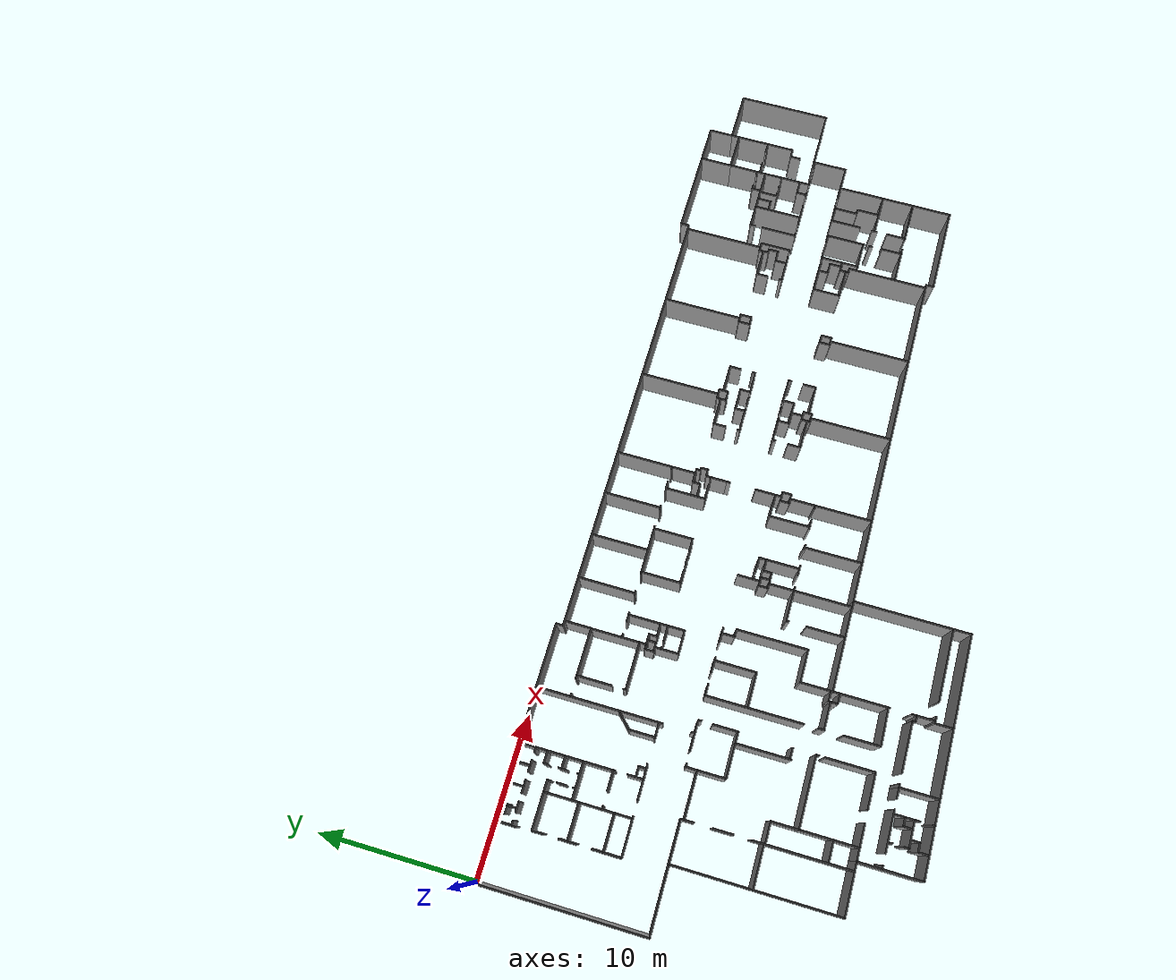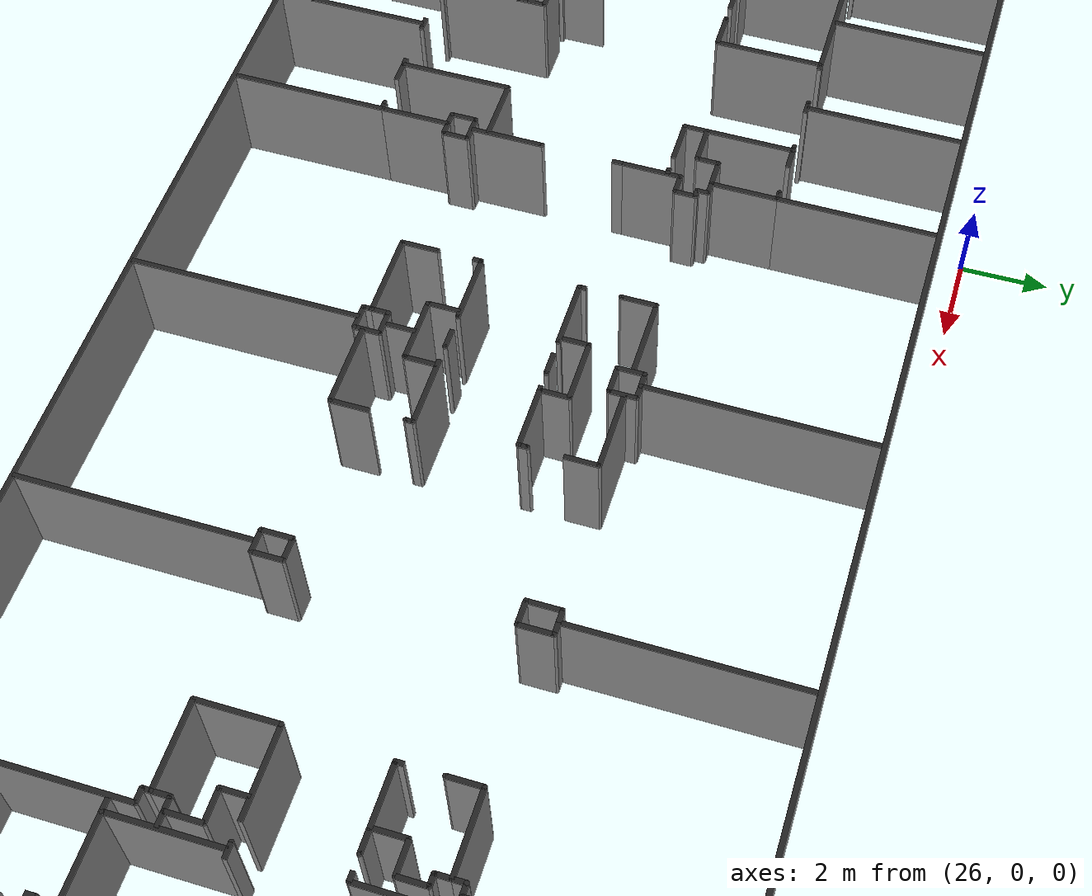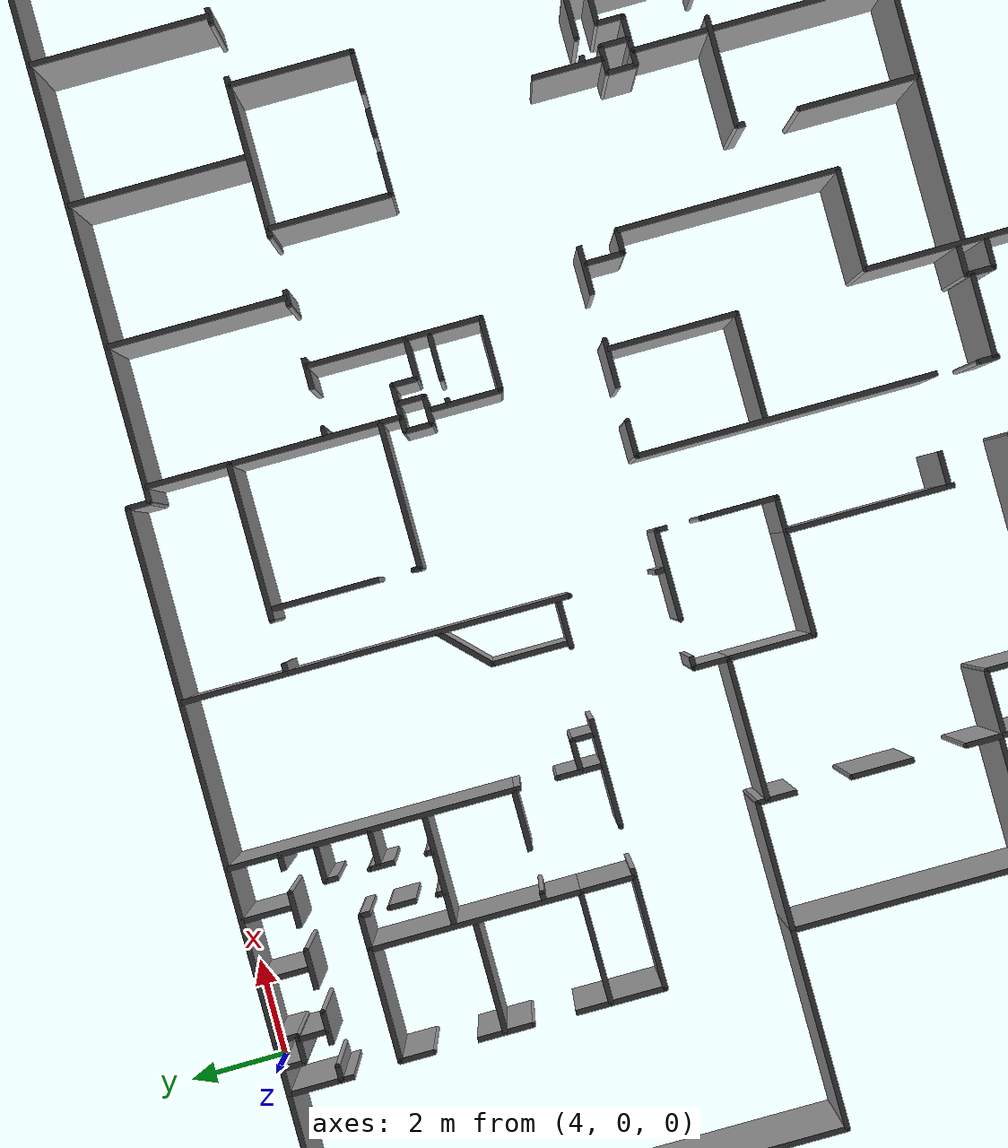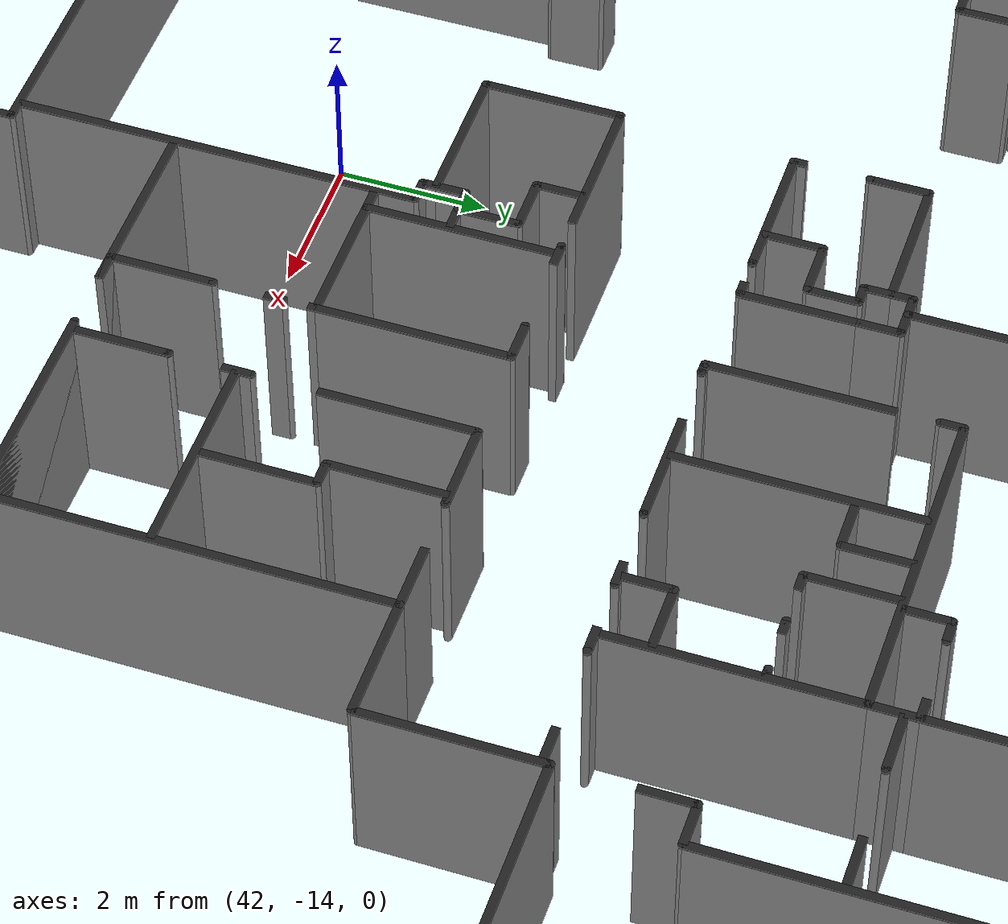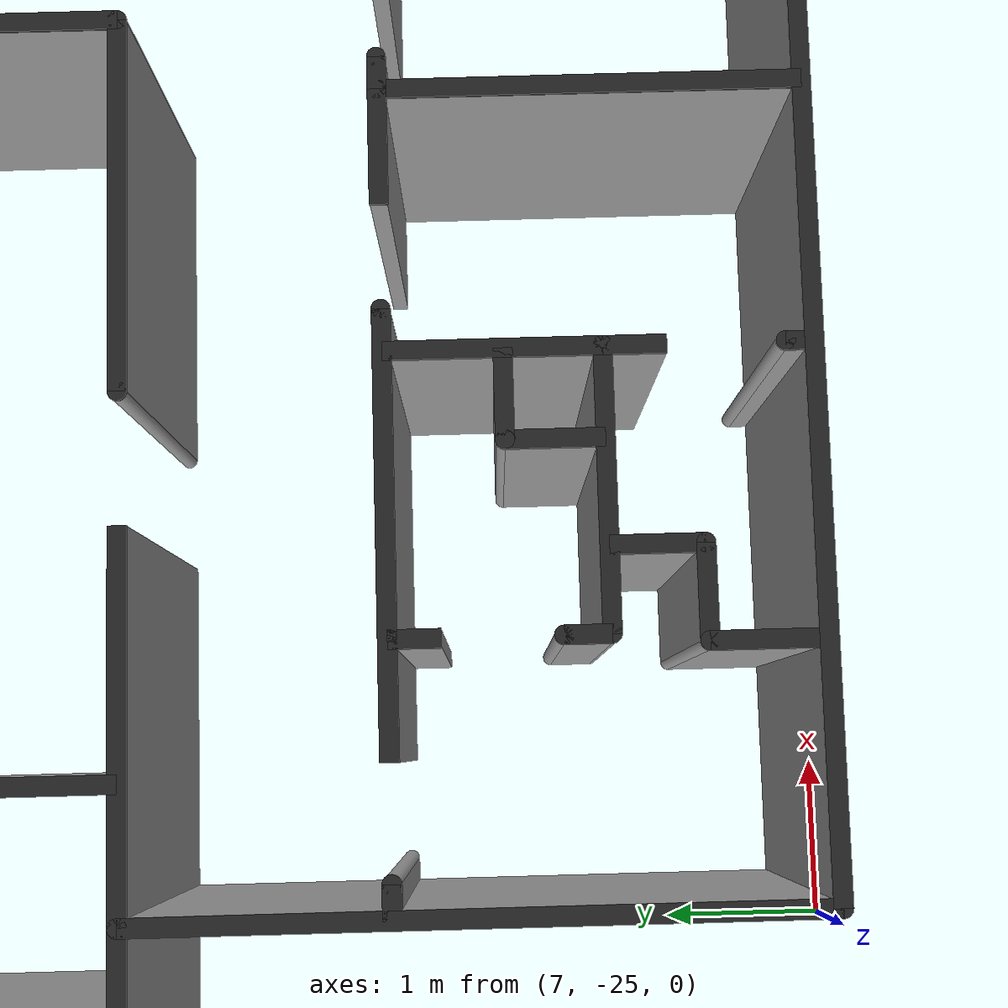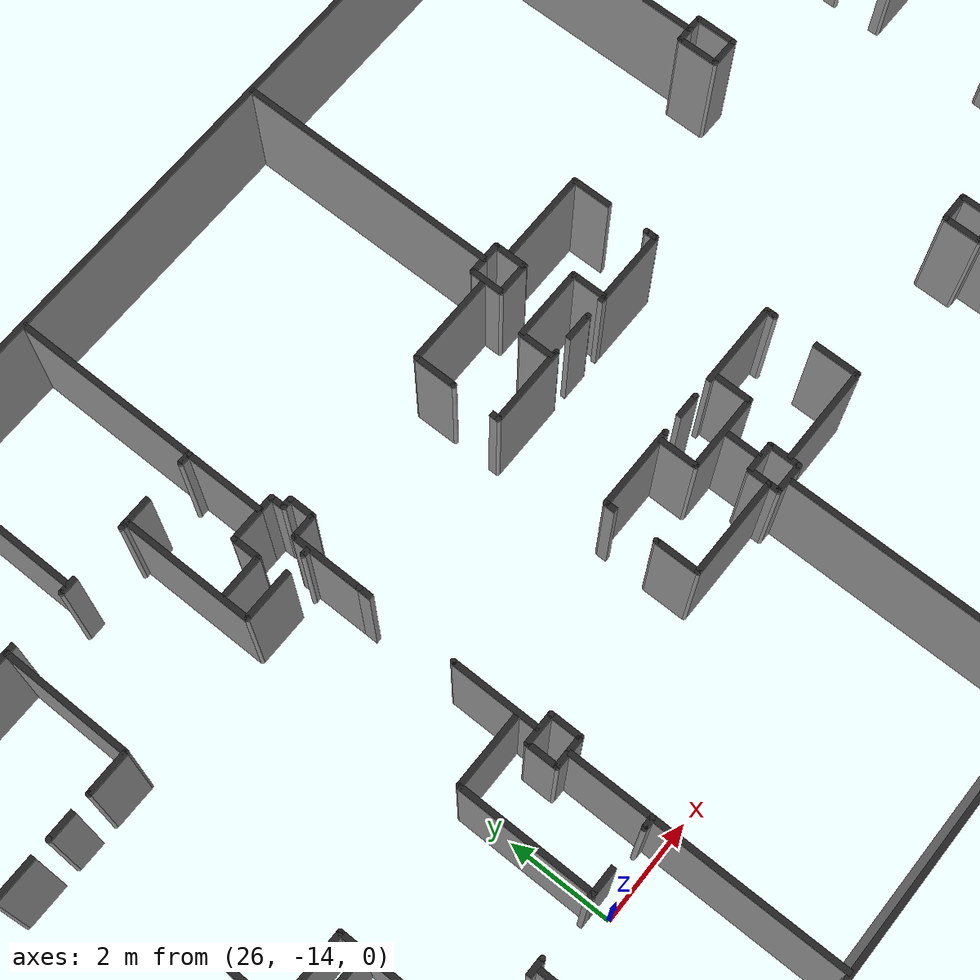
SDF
<sdf version="1.6">
 <world name="default">
  <plugin name="pedsim_plugin" filename="libpedsim_ros_plugin.so"/>
  <plugin name="pos_plugin" filename="libpos_plugin.so"/>
  <scene><ambient>0.8 0.8 0.8 1.0</ambient></scene>
  <include><uri>model://sun</uri></include>
  <model name="walls">
   <static>true</static>
   <link name="walls">
    <visual name="walls_0">
     <geometry><box><size>0.7134205 0.1 2.5</size></box></geometry>
     <material><script><name>SossSimulation/SimpleWall</name></script></material>
     <pose>3.67579 -6.38643175 1.25 0 0 1.57079632679</pose>
    </visual>
    <collision name="walls_0">
     <geometry><box><size>0.7134205 0.1 2.5</size></box></geometry>
     <pose>3.67579 -6.38643175 1.25 0 0 1.57079632679</pose>
     <surface><contact><collide_bitmask>0x01</collide_bitmask></contact></surface>
    </collision>
    <visual name="walls_1">
     <geometry><box><size>1.1174815 0.1 2.5</size></box></geometry>
     <material><script><name>SossSimulation/SimpleWall</name></script></material>
     <pose>3.67579 -4.59341075 1.25 0 0 1.57079632679</pose>
    </visual>
    <collision name="walls_1">
     <geometry><box><size>1.1174815 0.1 2.5</size></box></geometry>
     <pose>3.67579 -4.59341075 1.25 0 0 1.57079632679</pose>
     <surface><contact><collide_bitmask>0x01</collide_bitmask></contact></surface>
    </collision>
    <visual name="walls_2">
     <geometry><box><size>0.6755395 0.1 2.5</size></box></geometry>
     <material><script><name>SossSimulation/SimpleWall</name></script></material>
     <pose>3.67579 -2.80039025 1.25 0 0 1.57079632679</pose>
    </visual>
    <collision name="walls_2">
     <geometry><box><size>0.6755395 0.1 2.5</size></box></geometry>
     <pose>3.67579 -2.80039025 1.25 0 0 1.57079632679</pose>
     <surface><contact><collide_bitmask>0x01</collide_bitmask></contact></surface>
    </collision>
    <visual name="walls_3">
     <geometry><box><size>2.260215 0.1 2.5</size></box></geometry>
     <material><script><name>SossSimulation/SimpleWall</name></script></material>
     <pose>4.8058975 -2.4626205 1.25 0 0 0.0</pose>
    </visual>
    <collision name="walls_3">
     <geometry><box><size>2.260215 0.1 2.5</size></box></geometry>
     <pose>4.8058975 -2.4626205 1.25 0 0 0.0</pose>
     <surface><contact><collide_bitmask>0x01</collide_bitmask></contact></surface>
    </collision>
    <visual name="walls_4">
     <geometry><box><size>4.2805215 0.1 2.5</size></box></geometry>
     <material><script><name>SossSimulation/SimpleWall</name></script></material>
     <pose>5.936005 -4.60288125 1.25 0 0 -1.57079632679</pose>
    </visual>
    <collision name="walls_4">
     <geometry><box><size>4.2805215 0.1 2.5</size></box></geometry>
     <pose>5.936005 -4.60288125 1.25 0 0 -1.57079632679</pose>
     <surface><contact><collide_bitmask>0x01</collide_bitmask></contact></surface>
    </collision>
    <visual name="walls_5">
     <geometry><box><size>2.260215 0.1 2.5</size></box></geometry>
     <material><script><name>SossSimulation/SimpleWall</name></script></material>
     <pose>4.8058975 -6.743142 1.25 0 0 3.14159265359</pose>
    </visual>
    <collision name="walls_5">
     <geometry><box><size>2.260215 0.1 2.5</size></box></geometry>
     <pose>4.8058975 -6.743142 1.25 0 0 3.14159265359</pose>
     <surface><contact><collide_bitmask>0x01</collide_bitmask></contact></surface>
    </collision>
    <visual name="walls_6">
     <geometry><box><size>2.260215 0.1 2.5</size></box></geometry>
     <material><script><name>SossSimulation/SimpleWall</name></script></material>
     <pose>4.8058975 -4.5934105 1.25 0 0 0.0</pose>
    </visual>
    <collision name="walls_6">
     <geometry><box><size>2.260215 0.1 2.5</size></box></geometry>
     <pose>4.8058975 -4.5934105 1.25 0 0 0.0</pose>
     <surface><contact><collide_bitmask>0x01</collide_bitmask></contact></surface>
    </collision>
    <visual name="walls_7">
     <geometry><box><size>1.104854 0.1 2.5</size></box></geometry>
     <material><script><name>SossSimulation/SimpleWall</name></script></material>
     <pose>5.936005 -7.295569 1.25 0 0 -1.57079632679</pose>
    </visual>
    <collision name="walls_7">
     <geometry><box><size>1.104854 0.1 2.5</size></box></geometry>
     <pose>5.936005 -7.295569 1.25 0 0 -1.57079632679</pose>
     <surface><contact><collide_bitmask>0x01</collide_bitmask></contact></surface>
    </collision>
    <visual name="walls_8">
     <geometry><box><size>1.104854 0.1 2.5</size></box></geometry>
     <material><script><name>SossSimulation/SimpleWall</name></script></material>
     <pose>3.67579 -7.295569 1.25 0 0 -1.57079632679</pose>
    </visual>
    <collision name="walls_8">
     <geometry><box><size>1.104854 0.1 2.5</size></box></geometry>
     <pose>3.67579 -7.295569 1.25 0 0 -1.57079632679</pose>
     <surface><contact><collide_bitmask>0x01</collide_bitmask></contact></surface>
    </collision>
    <visual name="walls_9">
     <geometry><box><size>2.260215 0.1 2.5</size></box></geometry>
     <material><script><name>SossSimulation/SimpleWall</name></script></material>
     <pose>4.8058975 -7.847996 1.25 0 0 0.0</pose>
    </visual>
    <collision name="walls_9">
     <geometry><box><size>2.260215 0.1 2.5</size></box></geometry>
     <pose>4.8058975 -7.847996 1.25 0 0 0.0</pose>
     <surface><contact><collide_bitmask>0x01</collide_bitmask></contact></surface>
    </collision>
    <visual name="walls_10">
     <geometry><box><size>0.8035715 0.1 2.5</size></box></geometry>
     <material><script><name>SossSimulation/SimpleWall</name></script></material>
     <pose>6.69362 -10.95892875 1.25 0 0 -1.57079632679</pose>
    </visual>
    <collision name="walls_10">
     <geometry><box><size>0.8035715 0.1 2.5</size></box></geometry>
     <pose>6.69362 -10.95892875 1.25 0 0 -1.57079632679</pose>
     <surface><contact><collide_bitmask>0x01</collide_bitmask></contact></surface>
    </collision>
    <visual name="walls_11">
     <geometry><box><size>1.2678575 0.1 2.5</size></box></geometry>
     <material><script><name>SossSimulation/SimpleWall</name></script></material>
     <pose>6.69362 -13.10178575 1.25 0 0 -1.57079632679</pose>
    </visual>
    <collision name="walls_11">
     <geometry><box><size>1.2678575 0.1 2.5</size></box></geometry>
     <pose>6.69362 -13.10178575 1.25 0 0 -1.57079632679</pose>
     <surface><contact><collide_bitmask>0x01</collide_bitmask></contact></surface>
    </collision>
    <visual name="walls_12">
     <geometry><box><size>6.0202305 0.1 2.5</size></box></geometry>
     <material><script><name>SossSimulation/SimpleWall</name></script></material>
     <pose>6.69362 -17.79940075 1.25 0 0 -1.57079632679</pose>
    </visual>
    <collision name="walls_12">
     <geometry><box><size>6.0202305 0.1 2.5</size></box></geometry>
     <pose>6.69362 -17.79940075 1.25 0 0 -1.57079632679</pose>
     <surface><contact><collide_bitmask>0x01</collide_bitmask></contact></surface>
    </collision>
    <visual name="walls_13">
     <geometry><box><size>2.588075 0.1 2.5</size></box></geometry>
     <material><script><name>SossSimulation/SimpleWall</name></script></material>
     <pose>5.3995825 -10.557143 1.25 0 0 3.14159265359</pose>
    </visual>
    <collision name="walls_13">
     <geometry><box><size>2.588075 0.1 2.5</size></box></geometry>
     <pose>5.3995825 -10.557143 1.25 0 0 3.14159265359</pose>
     <surface><contact><collide_bitmask>0x01</collide_bitmask></contact></surface>
    </collision>
    <visual name="walls_14">
     <geometry><box><size>2.588305 0.1 2.5</size></box></geometry>
     <material><script><name>SossSimulation/SimpleWall</name></script></material>
     <pose>5.3994675 -15.4935885 1.25 0 0 3.14159265359</pose>
    </visual>
    <collision name="walls_14">
     <geometry><box><size>2.588305 0.1 2.5</size></box></geometry>
     <pose>5.3994675 -15.4935885 1.25 0 0 3.14159265359</pose>
     <surface><contact><collide_bitmask>0x01</collide_bitmask></contact></surface>
    </collision>
    <visual name="walls_15">
     <geometry><box><size>1.31001 0.1 2.5</size></box></geometry>
     <material><script><name>SossSimulation/SimpleWall</name></script></material>
     <pose>7.348625 -15.561607 1.25 0 0 0.0</pose>
    </visual>
    <collision name="walls_15">
     <geometry><box><size>1.31001 0.1 2.5</size></box></geometry>
     <pose>7.348625 -15.561607 1.25 0 0 0.0</pose>
     <surface><contact><collide_bitmask>0x01</collide_bitmask></contact></surface>
    </collision>
    <visual name="walls_16">
     <geometry><box><size>1.683036 0.1 2.5</size></box></geometry>
     <material><script><name>SossSimulation/SimpleWall</name></script></material>
     <pose>8.00363 -16.403125 1.25 0 0 -1.57079632679</pose>
    </visual>
    <collision name="walls_16">
     <geometry><box><size>1.683036 0.1 2.5</size></box></geometry>
     <pose>8.00363 -16.403125 1.25 0 0 -1.57079632679</pose>
     <surface><contact><collide_bitmask>0x01</collide_bitmask></contact></surface>
    </collision>
    <visual name="walls_17">
     <geometry><box><size>4.348215 0.1 2.5</size></box></geometry>
     <material><script><name>SossSimulation/SimpleWall</name></script></material>
     <pose>10.1777375 -17.244643 1.25 0 0 0.0</pose>
    </visual>
    <collision name="walls_17">
     <geometry><box><size>4.348215 0.1 2.5</size></box></geometry>
     <pose>10.1777375 -17.244643 1.25 0 0 0.0</pose>
     <surface><contact><collide_bitmask>0x01</collide_bitmask></contact></surface>
    </collision>
    <visual name="walls_18">
     <geometry><box><size>0.1998025 0.1 2.5</size></box></geometry>
     <material><script><name>SossSimulation/SimpleWall</name></script></material>
     <pose>12.351845 -17.34454425 1.25 0 0 -1.57079632679</pose>
    </visual>
    <collision name="walls_18">
     <geometry><box><size>0.1998025 0.1 2.5</size></box></geometry>
     <pose>12.351845 -17.34454425 1.25 0 0 -1.57079632679</pose>
     <surface><contact><collide_bitmask>0x01</collide_bitmask></contact></surface>
    </collision>
    <visual name="walls_19">
     <geometry><box><size>3.0178305 0.1 2.5</size></box></geometry>
     <material><script><name>SossSimulation/SimpleWall</name></script></material>
     <pose>12.351845 -19.30060075 1.25 0 0 -1.57079632679</pose>
    </visual>
    <collision name="walls_19">
     <geometry><box><size>3.0178305 0.1 2.5</size></box></geometry>
     <pose>12.351845 -19.30060075 1.25 0 0 -1.57079632679</pose>
     <surface><contact><collide_bitmask>0x01</collide_bitmask></contact></surface>
    </collision>
    <visual name="walls_20">
     <geometry><box><size>2.184515 0.1 2.5</size></box></geometry>
     <material><script><name>SossSimulation/SimpleWall</name></script></material>
     <pose>8.3287725 -20.809516 1.25 0 0 0.0</pose>
    </visual>
    <collision name="walls_20">
     <geometry><box><size>2.184515 0.1 2.5</size></box></geometry>
     <pose>8.3287725 -20.809516 1.25 0 0 0.0</pose>
     <surface><contact><collide_bitmask>0x01</collide_bitmask></contact></surface>
    </collision>
    <visual name="walls_21">
     <geometry><box><size>2.1732 0.1 2.5</size></box></geometry>
     <material><script><name>SossSimulation/SimpleWall</name></script></material>
     <pose>11.265245 -20.809516 1.25 0 0 0.0</pose>
    </visual>
    <collision name="walls_21">
     <geometry><box><size>2.1732 0.1 2.5</size></box></geometry>
     <pose>11.265245 -20.809516 1.25 0 0 0.0</pose>
     <surface><contact><collide_bitmask>0x01</collide_bitmask></contact></surface>
    </collision>
    <visual name="walls_22">
     <geometry><box><size>3.564873 0.1 2.5</size></box></geometry>
     <material><script><name>SossSimulation/SimpleWall</name></script></material>
     <pose>8.00363 -19.0270795 1.25 0 0 -1.57079632679</pose>
    </visual>
    <collision name="walls_22">
     <geometry><box><size>3.564873 0.1 2.5</size></box></geometry>
     <pose>8.00363 -19.0270795 1.25 0 0 -1.57079632679</pose>
     <surface><contact><collide_bitmask>0x01</collide_bitmask></contact></surface>
    </collision>
    <visual name="walls_23">
     <geometry><box><size>3.4345185 0.1 2.5</size></box></geometry>
     <material><script><name>SossSimulation/SimpleWall</name></script></material>
     <pose>11.68125 -14.21827075 1.25 0 0 1.57079632679</pose>
    </visual>
    <collision name="walls_23">
     <geometry><box><size>3.4345185 0.1 2.5</size></box></geometry>
     <pose>11.68125 -14.21827075 1.25 0 0 1.57079632679</pose>
     <surface><contact><collide_bitmask>0x01</collide_bitmask></contact></surface>
    </collision>
    <visual name="walls_24">
     <geometry><box><size>2.108695 0.1 2.5</size></box></geometry>
     <material><script><name>SossSimulation/SimpleWall</name></script></material>
     <pose>10.6269025 -12.5010115 1.25 0 0 3.14159265359</pose>
    </visual>
    <collision name="walls_24">
     <geometry><box><size>2.108695 0.1 2.5</size></box></geometry>
     <pose>10.6269025 -12.5010115 1.25 0 0 3.14159265359</pose>
     <surface><contact><collide_bitmask>0x01</collide_bitmask></contact></surface>
    </collision>
    <visual name="walls_25">
     <geometry><box><size>1.7425135 0.1 2.5</size></box></geometry>
     <material><script><name>SossSimulation/SimpleWall</name></script></material>
     <pose>9.572555 -11.62975475 1.25 0 0 1.57079632679</pose>
    </visual>
    <collision name="walls_25">
     <geometry><box><size>1.7425135 0.1 2.5</size></box></geometry>
     <pose>9.572555 -11.62975475 1.25 0 0 1.57079632679</pose>
     <surface><contact><collide_bitmask>0x01</collide_bitmask></contact></surface>
    </collision>
    <visual name="walls_26">
     <geometry><box><size>2.878935 0.1 2.5</size></box></geometry>
     <material><script><name>SossSimulation/SimpleWall</name></script></material>
     <pose>8.1330875 -10.758498 1.25 0 0 3.14159265359</pose>
    </visual>
    <collision name="walls_26">
     <geometry><box><size>2.878935 0.1 2.5</size></box></geometry>
     <pose>8.1330875 -10.758498 1.25 0 0 3.14159265359</pose>
     <surface><contact><collide_bitmask>0x01</collide_bitmask></contact></surface>
    </collision>
    <visual name="walls_27">
     <geometry><box><size>0.715235 0.1 2.5</size></box></geometry>
     <material><script><name>SossSimulation/SimpleWall</name></script></material>
     <pose>12.0388675 -15.8205355 1.25 0 0 0.0</pose>
    </visual>
    <collision name="walls_27">
     <geometry><box><size>0.715235 0.1 2.5</size></box></geometry>
     <pose>12.0388675 -15.8205355 1.25 0 0 0.0</pose>
     <surface><contact><collide_bitmask>0x01</collide_bitmask></contact></surface>
    </collision>
    <visual name="walls_28">
     <geometry><box><size>0.701355 0.1 2.5</size></box></geometry>
     <material><script><name>SossSimulation/SimpleWall</name></script></material>
     <pose>9.572555 -10.4078205 1.25 0 0 1.57079632679</pose>
    </visual>
    <collision name="walls_28">
     <geometry><box><size>0.701355 0.1 2.5</size></box></geometry>
     <pose>9.572555 -10.4078205 1.25 0 0 1.57079632679</pose>
     <surface><contact><collide_bitmask>0x01</collide_bitmask></contact></surface>
    </collision>
    <visual name="walls_29">
     <geometry><box><size>0.23991 0.1 2.5</size></box></geometry>
     <material><script><name>SossSimulation/SimpleWall</name></script></material>
     <pose>9.69251 -10.057143 1.25 0 0 0.0</pose>
    </visual>
    <collision name="walls_29">
     <geometry><box><size>0.23991 0.1 2.5</size></box></geometry>
     <pose>9.69251 -10.057143 1.25 0 0 0.0</pose>
     <surface><contact><collide_bitmask>0x01</collide_bitmask></contact></surface>
    </collision>
    <visual name="walls_30">
     <geometry><box><size>1.805935 0.1 2.5</size></box></geometry>
     <material><script><name>SossSimulation/SimpleWall</name></script></material>
     <pose>11.4667325 -10.057143 1.25 0 0 0.0</pose>
    </visual>
    <collision name="walls_30">
     <geometry><box><size>1.805935 0.1 2.5</size></box></geometry>
     <pose>11.4667325 -10.057143 1.25 0 0 0.0</pose>
     <surface><contact><collide_bitmask>0x01</collide_bitmask></contact></surface>
    </collision>
    <visual name="walls_31">
     <geometry><box><size>0.223214 0.1 2.5</size></box></geometry>
     <material><script><name>SossSimulation/SimpleWall</name></script></material>
     <pose>12.3697 -10.16875 1.25 0 0 -1.57079632679</pose>
    </visual>
    <collision name="walls_31">
     <geometry><box><size>0.223214 0.1 2.5</size></box></geometry>
     <pose>12.3697 -10.16875 1.25 0 0 -1.57079632679</pose>
     <surface><contact><collide_bitmask>0x01</collide_bitmask></contact></surface>
    </collision>
    <visual name="walls_32">
     <geometry><box><size>1.5331545 0.1 2.5</size></box></geometry>
     <material><script><name>SossSimulation/SimpleWall</name></script></material>
     <pose>12.3697 -11.73443425 1.25 0 0 -1.57079632679</pose>
    </visual>
    <collision name="walls_32">
     <geometry><box><size>1.5331545 0.1 2.5</size></box></geometry>
     <pose>12.3697 -11.73443425 1.25 0 0 -1.57079632679</pose>
     <surface><contact><collide_bitmask>0x01</collide_bitmask></contact></surface>
    </collision>
    <visual name="walls_33">
     <geometry><box><size>0.68845 0.1 2.5</size></box></geometry>
     <material><script><name>SossSimulation/SimpleWall</name></script></material>
     <pose>12.025475 -12.5010115 1.25 0 0 0.0</pose>
    </visual>
    <collision name="walls_33">
     <geometry><box><size>0.68845 0.1 2.5</size></box></geometry>
     <pose>12.025475 -12.5010115 1.25 0 0 0.0</pose>
     <surface><contact><collide_bitmask>0x01</collide_bitmask></contact></surface>
    </collision>
    <visual name="walls_34">
     <geometry><box><size>0.2410715 0.1 2.5</size></box></geometry>
     <material><script><name>SossSimulation/SimpleWall</name></script></material>
     <pose>11.58655 -9.93660725 1.25 0 0 1.57079632679</pose>
    </visual>
    <collision name="walls_34">
     <geometry><box><size>0.2410715 0.1 2.5</size></box></geometry>
     <pose>11.58655 -9.93660725 1.25 0 0 1.57079632679</pose>
     <surface><contact><collide_bitmask>0x01</collide_bitmask></contact></surface>
    </collision>
    <visual name="walls_35">
     <geometry><box><size>7.8928565 0.1 2.5</size></box></geometry>
     <material><script><name>SossSimulation/SimpleWall</name></script></material>
     <pose>11.58655 -4.12857125 1.25 0 0 1.57079632679</pose>
    </visual>
    <collision name="walls_35">
     <geometry><box><size>7.8928565 0.1 2.5</size></box></geometry>
     <pose>11.58655 -4.12857125 1.25 0 0 1.57079632679</pose>
     <surface><contact><collide_bitmask>0x01</collide_bitmask></contact></surface>
    </collision>
    <visual name="walls_36">
     <geometry><box><size>5.8286385 0.1 2.5</size></box></geometry>
     <material><script><name>SossSimulation/SimpleWall</name></script></material>
     <pose>8.20885 -3.09646225 1.25 0 0 -1.57079632679</pose>
    </visual>
    <collision name="walls_36">
     <geometry><box><size>5.8286385 0.1 2.5</size></box></geometry>
     <pose>8.20885 -3.09646225 1.25 0 0 -1.57079632679</pose>
     <surface><contact><collide_bitmask>0x01</collide_bitmask></contact></surface>
    </collision>
    <visual name="walls_37">
     <geometry><box><size>1.240935 0.1 2.5</size></box></geometry>
     <material><script><name>SossSimulation/SimpleWall</name></script></material>
     <pose>7.5883825 -6.0107815 1.25 0 0 3.14159265359</pose>
    </visual>
    <collision name="walls_37">
     <geometry><box><size>1.240935 0.1 2.5</size></box></geometry>
     <pose>7.5883825 -6.0107815 1.25 0 0 3.14159265359</pose>
     <surface><contact><collide_bitmask>0x01</collide_bitmask></contact></surface>
    </collision>
    <visual name="walls_38">
     <geometry><box><size>0.183695 0.1 2.5</size></box></geometry>
     <material><script><name>SossSimulation/SimpleWall</name></script></material>
     <pose>6.0278525 -6.0107815 1.25 0 0 3.14159265359</pose>
    </visual>
    <collision name="walls_38">
     <geometry><box><size>0.183695 0.1 2.5</size></box></geometry>
     <pose>6.0278525 -6.0107815 1.25 0 0 3.14159265359</pose>
     <surface><contact><collide_bitmask>0x01</collide_bitmask></contact></surface>
    </collision>
    <visual name="walls_39">
     <geometry><box><size>0.33022 0.1 2.5</size></box></geometry>
     <material><script><name>SossSimulation/SimpleWall</name></script></material>
     <pose>8.04374 -1.2504375 1.25 0 0 3.14159265359</pose>
    </visual>
    <collision name="walls_39">
     <geometry><box><size>0.33022 0.1 2.5</size></box></geometry>
     <pose>8.04374 -1.2504375 1.25 0 0 3.14159265359</pose>
     <surface><contact><collide_bitmask>0x01</collide_bitmask></contact></surface>
    </collision>
    <visual name="walls_40">
     <geometry><box><size>0.714285 0.1 2.5</size></box></geometry>
     <material><script><name>SossSimulation/SimpleWall</name></script></material>
     <pose>7.0750575 -1.2504375 1.25 0 0 3.14159265359</pose>
    </visual>
    <collision name="walls_40">
     <geometry><box><size>0.714285 0.1 2.5</size></box></geometry>
     <pose>7.0750575 -1.2504375 1.25 0 0 3.14159265359</pose>
     <surface><contact><collide_bitmask>0x01</collide_bitmask></contact></surface>
    </collision>
    <visual name="walls_41">
     <geometry><box><size>0.794645 0.1 2.5</size></box></geometry>
     <material><script><name>SossSimulation/SimpleWall</name></script></material>
     <pose>5.8652375 -1.2504375 1.25 0 0 3.14159265359</pose>
    </visual>
    <collision name="walls_41">
     <geometry><box><size>0.794645 0.1 2.5</size></box></geometry>
     <pose>5.8652375 -1.2504375 1.25 0 0 3.14159265359</pose>
     <surface><contact><collide_bitmask>0x01</collide_bitmask></contact></surface>
    </collision>
    <visual name="walls_42">
     <geometry><box><size>0.669645 0.1 2.5</size></box></geometry>
     <material><script><name>SossSimulation/SimpleWall</name></script></material>
     <pose>4.6777375 -1.2504375 1.25 0 0 3.14159265359</pose>
    </visual>
    <collision name="walls_42">
     <geometry><box><size>0.669645 0.1 2.5</size></box></geometry>
     <pose>4.6777375 -1.2504375 1.25 0 0 3.14159265359</pose>
     <surface><contact><collide_bitmask>0x01</collide_bitmask></contact></surface>
    </collision>
    <visual name="walls_43">
     <geometry><box><size>0.289065 0.1 2.5</size></box></geometry>
     <material><script><name>SossSimulation/SimpleWall</name></script></material>
     <pose>3.7698125 -1.2504375 1.25 0 0 3.14159265359</pose>
    </visual>
    <collision name="walls_43">
     <geometry><box><size>0.289065 0.1 2.5</size></box></geometry>
     <pose>3.7698125 -1.2504375 1.25 0 0 3.14159265359</pose>
     <surface><contact><collide_bitmask>0x01</collide_bitmask></contact></surface>
    </collision>
    <visual name="walls_44">
     <geometry><box><size>1.0682945 0.1 2.5</size></box></geometry>
     <material><script><name>SossSimulation/SimpleWall</name></script></material>
     <pose>3.62528 -0.71629025 1.25 0 0 1.57079632679</pose>
    </visual>
    <collision name="walls_44">
     <geometry><box><size>1.0682945 0.1 2.5</size></box></geometry>
     <pose>3.62528 -0.71629025 1.25 0 0 1.57079632679</pose>
     <surface><contact><collide_bitmask>0x01</collide_bitmask></contact></surface>
    </collision>
    <visual name="walls_45">
     <geometry><box><size>0.2620625 0.1 2.5</size></box></geometry>
     <material><script><name>SossSimulation/SimpleWall</name></script></material>
     <pose>3.62528 -1.38146875 1.25 0 0 -1.57079632679</pose>
    </visual>
    <collision name="walls_45">
     <geometry><box><size>0.2620625 0.1 2.5</size></box></geometry>
     <pose>3.62528 -1.38146875 1.25 0 0 -1.57079632679</pose>
     <surface><contact><collide_bitmask>0x01</collide_bitmask></contact></surface>
    </collision>
    <visual name="walls_46">
     <geometry><box><size>0.22065 0.1 2.5</size></box></geometry>
     <material><script><name>SossSimulation/SimpleWall</name></script></material>
     <pose>11.696875 -2.325 1.25 0 0 0.0</pose>
    </visual>
    <collision name="walls_46">
     <geometry><box><size>0.22065 0.1 2.5</size></box></geometry>
     <pose>11.696875 -2.325 1.25 0 0 0.0</pose>
     <surface><contact><collide_bitmask>0x01</collide_bitmask></contact></surface>
    </collision>
    <visual name="walls_47">
     <geometry><box><size>3.17857 0.1 2.5</size></box></geometry>
     <material><script><name>SossSimulation/SimpleWall</name></script></material>
     <pose>14.26256 -2.325 1.25 0 0 0.0</pose>
    </visual>
    <collision name="walls_47">
     <geometry><box><size>3.17857 0.1 2.5</size></box></geometry>
     <pose>14.26256 -2.325 1.25 0 0 0.0</pose>
     <surface><contact><collide_bitmask>0x01</collide_bitmask></contact></surface>
    </collision>
    <visual name="walls_48">
     <geometry><box><size>1.6964285 0.1 2.5</size></box></geometry>
     <material><script><name>SossSimulation/SimpleWall</name></script></material>
     <pose>15.851845 -1.47678575 1.25 0 0 1.57079632679</pose>
    </visual>
    <collision name="walls_48">
     <geometry><box><size>1.6964285 0.1 2.5</size></box></geometry>
     <pose>15.851845 -1.47678575 1.25 0 0 1.57079632679</pose>
     <surface><contact><collide_bitmask>0x01</collide_bitmask></contact></surface>
    </collision>
    <visual name="walls_49">
     <geometry><box><size>2.232143 0.1 2.5</size></box></geometry>
     <material><script><name>SossSimulation/SimpleWall</name></script></material>
     <pose>12.88756 -3.4410715 1.25 0 0 -1.57079632679</pose>
    </visual>
    <collision name="walls_49">
     <geometry><box><size>2.232143 0.1 2.5</size></box></geometry>
     <pose>12.88756 -3.4410715 1.25 0 0 -1.57079632679</pose>
     <surface><contact><collide_bitmask>0x01</collide_bitmask></contact></surface>
    </collision>
    <visual name="walls_50">
     <geometry><box><size>0.1339285 0.1 2.5</size></box></geometry>
     <material><script><name>SossSimulation/SimpleWall</name></script></material>
     <pose>12.88756 -5.32946425 1.25 0 0 -1.57079632679</pose>
    </visual>
    <collision name="walls_50">
     <geometry><box><size>0.1339285 0.1 2.5</size></box></geometry>
     <pose>12.88756 -5.32946425 1.25 0 0 -1.57079632679</pose>
     <surface><contact><collide_bitmask>0x01</collide_bitmask></contact></surface>
    </collision>
    <visual name="walls_51">
     <geometry><box><size>2.955355 0.1 2.5</size></box></geometry>
     <material><script><name>SossSimulation/SimpleWall</name></script></material>
     <pose>14.3652375 -5.3964285 1.25 0 0 0.0</pose>
    </visual>
    <collision name="walls_51">
     <geometry><box><size>2.955355 0.1 2.5</size></box></geometry>
     <pose>14.3652375 -5.3964285 1.25 0 0 0.0</pose>
     <surface><contact><collide_bitmask>0x01</collide_bitmask></contact></surface>
    </collision>
    <visual name="walls_52">
     <geometry><box><size>3.0714285 0.1 2.5</size></box></geometry>
     <material><script><name>SossSimulation/SimpleWall</name></script></material>
     <pose>15.842915 -3.86071425 1.25 0 0 1.57079632679</pose>
    </visual>
    <collision name="walls_52">
     <geometry><box><size>3.0714285 0.1 2.5</size></box></geometry>
     <pose>15.842915 -3.86071425 1.25 0 0 1.57079632679</pose>
     <surface><contact><collide_bitmask>0x01</collide_bitmask></contact></surface>
    </collision>
    <visual name="walls_53">
     <geometry><box><size>0.4285715 0.1 2.5</size></box></geometry>
     <material><script><name>SossSimulation/SimpleWall</name></script></material>
     <pose>15.842915 -5.61071425 1.25 0 0 -1.57079632679</pose>
    </visual>
    <collision name="walls_53">
     <geometry><box><size>0.4285715 0.1 2.5</size></box></geometry>
     <pose>15.842915 -5.61071425 1.25 0 0 -1.57079632679</pose>
     <surface><contact><collide_bitmask>0x01</collide_bitmask></contact></surface>
    </collision>
    <visual name="walls_54">
     <geometry><box><size>0.29464 0.1 2.5</size></box></geometry>
     <material><script><name>SossSimulation/SimpleWall</name></script></material>
     <pose>15.695595 -5.825 1.25 0 0 3.14159265359</pose>
    </visual>
    <collision name="walls_54">
     <geometry><box><size>0.29464 0.1 2.5</size></box></geometry>
     <pose>15.695595 -5.825 1.25 0 0 3.14159265359</pose>
     <surface><contact><collide_bitmask>0x01</collide_bitmask></contact></surface>
    </collision>
    <visual name="walls_55">
     <geometry><box><size>0.544643 0.1 2.5</size></box></geometry>
     <material><script><name>SossSimulation/SimpleWall</name></script></material>
     <pose>15.548275 -6.0973215 1.25 0 0 -1.57079632679</pose>
    </visual>
    <collision name="walls_55">
     <geometry><box><size>0.544643 0.1 2.5</size></box></geometry>
     <pose>15.548275 -6.0973215 1.25 0 0 -1.57079632679</pose>
     <surface><contact><collide_bitmask>0x01</collide_bitmask></contact></surface>
    </collision>
    <visual name="walls_56">
     <geometry><box><size>0.5625 0.1 2.5</size></box></geometry>
     <material><script><name>SossSimulation/SimpleWall</name></script></material>
     <pose>15.829525 -6.369643 1.25 0 0 0.0</pose>
    </visual>
    <collision name="walls_56">
     <geometry><box><size>0.5625 0.1 2.5</size></box></geometry>
     <pose>15.829525 -6.369643 1.25 0 0 0.0</pose>
     <surface><contact><collide_bitmask>0x01</collide_bitmask></contact></surface>
    </collision>
    <visual name="walls_57">
     <geometry><box><size>0.544643 0.1 2.5</size></box></geometry>
     <material><script><name>SossSimulation/SimpleWall</name></script></material>
     <pose>16.110775 -6.0973215 1.25 0 0 1.57079632679</pose>
    </visual>
    <collision name="walls_57">
     <geometry><box><size>0.544643 0.1 2.5</size></box></geometry>
     <pose>16.110775 -6.0973215 1.25 0 0 1.57079632679</pose>
     <surface><contact><collide_bitmask>0x01</collide_bitmask></contact></surface>
    </collision>
    <visual name="walls_58">
     <geometry><box><size>0.26786 0.1 2.5</size></box></geometry>
     <material><script><name>SossSimulation/SimpleWall</name></script></material>
     <pose>15.976845 -5.825 1.25 0 0 0.0</pose>
    </visual>
    <collision name="walls_58">
     <geometry><box><size>0.26786 0.1 2.5</size></box></geometry>
     <pose>15.976845 -5.825 1.25 0 0 0.0</pose>
     <surface><contact><collide_bitmask>0x01</collide_bitmask></contact></surface>
    </collision>
    <visual name="walls_59">
     <geometry><box><size>1.4821425 0.1 2.5</size></box></geometry>
     <material><script><name>SossSimulation/SimpleWall</name></script></material>
     <pose>15.82506 -7.11071425 1.25 0 0 -1.57079632679</pose>
    </visual>
    <collision name="walls_59">
     <geometry><box><size>1.4821425 0.1 2.5</size></box></geometry>
     <pose>15.82506 -7.11071425 1.25 0 0 -1.57079632679</pose>
     <surface><contact><collide_bitmask>0x01</collide_bitmask></contact></surface>
    </collision>
    <visual name="walls_60">
     <geometry><box><size>1.473215 0.1 2.5</size></box></geometry>
     <material><script><name>SossSimulation/SimpleWall</name></script></material>
     <pose>16.5616675 -7.8517855 1.25 0 0 0.0</pose>
    </visual>
    <collision name="walls_60">
     <geometry><box><size>1.473215 0.1 2.5</size></box></geometry>
     <pose>16.5616675 -7.8517855 1.25 0 0 0.0</pose>
     <surface><contact><collide_bitmask>0x01</collide_bitmask></contact></surface>
    </collision>
    <visual name="walls_61">
     <geometry><box><size>1.535714 0.1 2.5</size></box></geometry>
     <material><script><name>SossSimulation/SimpleWall</name></script></material>
     <pose>17.298275 -7.0839285 1.25 0 0 1.57079632679</pose>
    </visual>
    <collision name="walls_61">
     <geometry><box><size>1.535714 0.1 2.5</size></box></geometry>
     <pose>17.298275 -7.0839285 1.25 0 0 1.57079632679</pose>
     <surface><contact><collide_bitmask>0x01</collide_bitmask></contact></surface>
    </collision>
    <visual name="walls_62">
     <geometry><box><size>0.8125 0.1 2.5</size></box></geometry>
     <material><script><name>SossSimulation/SimpleWall</name></script></material>
     <pose>16.892025 -6.3160715 1.25 0 0 3.14159265359</pose>
    </visual>
    <collision name="walls_62">
     <geometry><box><size>0.8125 0.1 2.5</size></box></geometry>
     <pose>16.892025 -6.3160715 1.25 0 0 3.14159265359</pose>
     <surface><contact><collide_bitmask>0x01</collide_bitmask></contact></surface>
    </collision>
    <visual name="walls_63">
     <geometry><box><size>0.4910715 0.1 2.5</size></box></geometry>
     <material><script><name>SossSimulation/SimpleWall</name></script></material>
     <pose>16.485775 -6.07053575 1.25 0 0 1.57079632679</pose>
    </visual>
    <collision name="walls_63">
     <geometry><box><size>0.4910715 0.1 2.5</size></box></geometry>
     <pose>16.485775 -6.07053575 1.25 0 0 1.57079632679</pose>
     <surface><contact><collide_bitmask>0x01</collide_bitmask></contact></surface>
    </collision>
    <visual name="walls_64">
     <geometry><box><size>0.375 0.1 2.5</size></box></geometry>
     <material><script><name>SossSimulation/SimpleWall</name></script></material>
     <pose>16.298275 -5.825 1.25 0 0 0.0</pose>
    </visual>
    <collision name="walls_64">
     <geometry><box><size>0.375 0.1 2.5</size></box></geometry>
     <pose>16.298275 -5.825 1.25 0 0 0.0</pose>
     <surface><contact><collide_bitmask>0x01</collide_bitmask></contact></surface>
    </collision>
    <visual name="walls_65">
     <geometry><box><size>0.142855 0.1 2.5</size></box></geometry>
     <material><script><name>SossSimulation/SimpleWall</name></script></material>
     <pose>15.8964875 -6.7892855 1.25 0 0 0.0</pose>
    </visual>
    <collision name="walls_65">
     <geometry><box><size>0.142855 0.1 2.5</size></box></geometry>
     <pose>15.8964875 -6.7892855 1.25 0 0 0.0</pose>
     <surface><contact><collide_bitmask>0x01</collide_bitmask></contact></surface>
    </collision>
    <visual name="walls_66">
     <geometry><box><size>0.94643 0.1 2.5</size></box></geometry>
     <material><script><name>SossSimulation/SimpleWall</name></script></material>
     <pose>16.82506 -6.7892855 1.25 0 0 0.0</pose>
    </visual>
    <collision name="walls_66">
     <geometry><box><size>0.94643 0.1 2.5</size></box></geometry>
     <pose>16.82506 -6.7892855 1.25 0 0 0.0</pose>
     <surface><contact><collide_bitmask>0x01</collide_bitmask></contact></surface>
    </collision>
    <visual name="walls_67">
     <geometry><box><size>2.026786 0.1 2.5</size></box></geometry>
     <material><script><name>SossSimulation/SimpleWall</name></script></material>
     <pose>17.298275 -5.3026785 1.25 0 0 1.57079632679</pose>
    </visual>
    <collision name="walls_67">
     <geometry><box><size>2.026786 0.1 2.5</size></box></geometry>
     <pose>17.298275 -5.3026785 1.25 0 0 1.57079632679</pose>
     <surface><contact><collide_bitmask>0x01</collide_bitmask></contact></surface>
    </collision>
    <visual name="walls_68">
     <geometry><box><size>0.473215 0.1 2.5</size></box></geometry>
     <material><script><name>SossSimulation/SimpleWall</name></script></material>
     <pose>17.0616675 -4.2892855 1.25 0 0 3.14159265359</pose>
    </visual>
    <collision name="walls_68">
     <geometry><box><size>0.473215 0.1 2.5</size></box></geometry>
     <pose>17.0616675 -4.2892855 1.25 0 0 3.14159265359</pose>
     <surface><contact><collide_bitmask>0x01</collide_bitmask></contact></surface>
    </collision>
    <visual name="walls_69">
     <geometry><box><size>0.19643 0.1 2.5</size></box></geometry>
     <material><script><name>SossSimulation/SimpleWall</name></script></material>
     <pose>15.94113 -4.2892855 1.25 0 0 3.14159265359</pose>
    </visual>
    <collision name="walls_69">
     <geometry><box><size>0.19643 0.1 2.5</size></box></geometry>
     <pose>15.94113 -4.2892855 1.25 0 0 3.14159265359</pose>
     <surface><contact><collide_bitmask>0x01</collide_bitmask></contact></surface>
    </collision>
    <visual name="walls_70">
     <geometry><box><size>0.16964 0.1 2.5</size></box></geometry>
     <material><script><name>SossSimulation/SimpleWall</name></script></material>
     <pose>17.383095 -4.2892855 1.25 0 0 0.0</pose>
    </visual>
    <collision name="walls_70">
     <geometry><box><size>0.16964 0.1 2.5</size></box></geometry>
     <pose>17.383095 -4.2892855 1.25 0 0 0.0</pose>
     <surface><contact><collide_bitmask>0x01</collide_bitmask></contact></surface>
    </collision>
    <visual name="walls_71">
     <geometry><box><size>0.3125 0.1 2.5</size></box></geometry>
     <material><script><name>SossSimulation/SimpleWall</name></script></material>
     <pose>18.695595 -4.2892855 1.25 0 0 0.0</pose>
    </visual>
    <collision name="walls_71">
     <geometry><box><size>0.3125 0.1 2.5</size></box></geometry>
     <pose>18.695595 -4.2892855 1.25 0 0 0.0</pose>
     <surface><contact><collide_bitmask>0x01</collide_bitmask></contact></surface>
    </collision>
    <visual name="walls_72">
     <geometry><box><size>0.160715 0.1 2.5</size></box></geometry>
     <material><script><name>SossSimulation/SimpleWall</name></script></material>
     <pose>20.0125575 -4.2892855 1.25 0 0 0.0</pose>
    </visual>
    <collision name="walls_72">
     <geometry><box><size>0.160715 0.1 2.5</size></box></geometry>
     <pose>20.0125575 -4.2892855 1.25 0 0 0.0</pose>
     <surface><contact><collide_bitmask>0x01</collide_bitmask></contact></surface>
    </collision>
    <visual name="walls_73">
     <geometry><box><size>2.5089285 0.1 2.5</size></box></geometry>
     <material><script><name>SossSimulation/SimpleWall</name></script></material>
     <pose>20.092915 -5.54374975 1.25 0 0 -1.57079632679</pose>
    </visual>
    <collision name="walls_73">
     <geometry><box><size>2.5089285 0.1 2.5</size></box></geometry>
     <pose>20.092915 -5.54374975 1.25 0 0 -1.57079632679</pose>
     <surface><contact><collide_bitmask>0x01</collide_bitmask></contact></surface>
    </collision>
    <visual name="walls_74">
     <geometry><box><size>0.86607 0.1 2.5</size></box></geometry>
     <material><script><name>SossSimulation/SimpleWall</name></script></material>
     <pose>20.52595 -6.798214 1.25 0 0 0.0</pose>
    </visual>
    <collision name="walls_74">
     <geometry><box><size>0.86607 0.1 2.5</size></box></geometry>
     <pose>20.52595 -6.798214 1.25 0 0 0.0</pose>
     <surface><contact><collide_bitmask>0x01</collide_bitmask></contact></surface>
    </collision>
    <visual name="walls_75">
     <geometry><box><size>0.55357 0.1 2.5</size></box></geometry>
     <material><script><name>SossSimulation/SimpleWall</name></script></material>
     <pose>21.56613 -6.798214 1.25 0 0 0.0</pose>
    </visual>
    <collision name="walls_75">
     <geometry><box><size>0.55357 0.1 2.5</size></box></geometry>
     <pose>21.56613 -6.798214 1.25 0 0 0.0</pose>
     <surface><contact><collide_bitmask>0x01</collide_bitmask></contact></surface>
    </collision>
    <visual name="walls_76">
     <geometry><box><size>0.82143 0.1 2.5</size></box></geometry>
     <material><script><name>SossSimulation/SimpleWall</name></script></material>
     <pose>22.592915 -6.798214 1.25 0 0 0.0</pose>
    </visual>
    <collision name="walls_76">
     <geometry><box><size>0.82143 0.1 2.5</size></box></geometry>
     <pose>22.592915 -6.798214 1.25 0 0 0.0</pose>
     <surface><contact><collide_bitmask>0x01</collide_bitmask></contact></surface>
    </collision>
    <visual name="walls_77">
     <geometry><box><size>2.5089285 0.1 2.5</size></box></geometry>
     <material><script><name>SossSimulation/SimpleWall</name></script></material>
     <pose>23.00363 -5.54374975 1.25 0 0 1.57079632679</pose>
    </visual>
    <collision name="walls_77">
     <geometry><box><size>2.5089285 0.1 2.5</size></box></geometry>
     <pose>23.00363 -5.54374975 1.25 0 0 1.57079632679</pose>
     <surface><contact><collide_bitmask>0x01</collide_bitmask></contact></surface>
    </collision>
    <visual name="walls_78">
     <geometry><box><size>2.910715 0.1 2.5</size></box></geometry>
     <material><script><name>SossSimulation/SimpleWall</name></script></material>
     <pose>21.5482725 -4.2892855 1.25 0 0 0.0</pose>
    </visual>
    <collision name="walls_78">
     <geometry><box><size>2.910715 0.1 2.5</size></box></geometry>
     <pose>21.5482725 -4.2892855 1.25 0 0 0.0</pose>
     <surface><contact><collide_bitmask>0x01</collide_bitmask></contact></surface>
    </collision>
    <visual name="walls_79">
     <geometry><box><size>3.660714 0.1 2.5</size></box></geometry>
     <material><script><name>SossSimulation/SimpleWall</name></script></material>
     <pose>18.695595 -2.4589285 1.25 0 0 1.57079632679</pose>
    </visual>
    <collision name="walls_79">
     <geometry><box><size>3.660714 0.1 2.5</size></box></geometry>
     <pose>18.695595 -2.4589285 1.25 0 0 1.57079632679</pose>
     <surface><contact><collide_bitmask>0x01</collide_bitmask></contact></surface>
    </collision>
    <visual name="walls_80">
     <geometry><box><size>3.660714 0.1 2.5</size></box></geometry>
     <material><script><name>SossSimulation/SimpleWall</name></script></material>
     <pose>21.561805 -2.4589285 1.25 0 0 1.57079632679</pose>
    </visual>
    <collision name="walls_80">
     <geometry><box><size>3.660714 0.1 2.5</size></box></geometry>
     <pose>21.561805 -2.4589285 1.25 0 0 1.57079632679</pose>
     <surface><contact><collide_bitmask>0x01</collide_bitmask></contact></surface>
    </collision>
    <visual name="walls_81">
     <geometry><box><size>0.17857 0.1 2.5</size></box></geometry>
     <material><script><name>SossSimulation/SimpleWall</name></script></material>
     <pose>23.092915 -4.2892855 1.25 0 0 0.0</pose>
    </visual>
    <collision name="walls_81">
     <geometry><box><size>0.17857 0.1 2.5</size></box></geometry>
     <pose>23.092915 -4.2892855 1.25 0 0 0.0</pose>
     <surface><contact><collide_bitmask>0x01</collide_bitmask></contact></surface>
    </collision>
    <visual name="walls_82">
     <geometry><box><size>0.321425 0.1 2.5</size></box></geometry>
     <material><script><name>SossSimulation/SimpleWall</name></script></material>
     <pose>24.4232725 -4.2892855 1.25 0 0 0.0</pose>
    </visual>
    <collision name="walls_82">
     <geometry><box><size>0.321425 0.1 2.5</size></box></geometry>
     <pose>24.4232725 -4.2892855 1.25 0 0 0.0</pose>
     <surface><contact><collide_bitmask>0x01</collide_bitmask></contact></surface>
    </collision>
    <visual name="walls_83">
     <geometry><box><size>0.64286 0.1 2.5</size></box></geometry>
     <material><script><name>SossSimulation/SimpleWall</name></script></material>
     <pose>25.976845 -4.2892855 1.25 0 0 0.0</pose>
    </visual>
    <collision name="walls_83">
     <geometry><box><size>0.64286 0.1 2.5</size></box></geometry>
     <pose>25.976845 -4.2892855 1.25 0 0 0.0</pose>
     <surface><contact><collide_bitmask>0x01</collide_bitmask></contact></surface>
    </collision>
    <visual name="walls_84">
     <geometry><box><size>0.19643 0.1 2.5</size></box></geometry>
     <material><script><name>SossSimulation/SimpleWall</name></script></material>
     <pose>27.164345 -4.2892855 1.25 0 0 0.0</pose>
    </visual>
    <collision name="walls_84">
     <geometry><box><size>0.19643 0.1 2.5</size></box></geometry>
     <pose>27.164345 -4.2892855 1.25 0 0 0.0</pose>
     <surface><contact><collide_bitmask>0x01</collide_bitmask></contact></surface>
    </collision>
    <visual name="walls_85">
     <geometry><box><size>3.660714 0.1 2.5</size></box></geometry>
     <material><script><name>SossSimulation/SimpleWall</name></script></material>
     <pose>27.26256 -2.4589285 1.25 0 0 1.57079632679</pose>
    </visual>
    <collision name="walls_85">
     <geometry><box><size>3.660714 0.1 2.5</size></box></geometry>
     <pose>27.26256 -2.4589285 1.25 0 0 1.57079632679</pose>
     <surface><contact><collide_bitmask>0x01</collide_bitmask></contact></surface>
    </collision>
    <visual name="walls_86">
     <geometry><box><size>3.660714 0.1 2.5</size></box></geometry>
     <material><script><name>SossSimulation/SimpleWall</name></script></material>
     <pose>24.423275 -2.4589285 1.25 0 0 1.57079632679</pose>
    </visual>
    <collision name="walls_86">
     <geometry><box><size>3.660714 0.1 2.5</size></box></geometry>
     <pose>24.423275 -2.4589285 1.25 0 0 1.57079632679</pose>
     <surface><contact><collide_bitmask>0x01</collide_bitmask></contact></surface>
    </collision>
    <visual name="walls_87">
     <geometry><box><size>0.251623 0.1 2.5</size></box></geometry>
     <material><script><name>SossSimulation/SimpleWall</name></script></material>
     <pose>27.26285 -8.0116885 1.25 0 0 -1.57079632679</pose>
    </visual>
    <collision name="walls_87">
     <geometry><box><size>0.251623 0.1 2.5</size></box></geometry>
     <pose>27.26285 -8.0116885 1.25 0 0 -1.57079632679</pose>
     <surface><contact><collide_bitmask>0x01</collide_bitmask></contact></surface>
    </collision>
    <visual name="walls_88">
     <geometry><box><size>1.6989585 0.1 2.5</size></box></geometry>
     <material><script><name>SossSimulation/SimpleWall</name></script></material>
     <pose>27.26285 -10.64769325 1.25 0 0 -1.57079632679</pose>
    </visual>
    <collision name="walls_88">
     <geometry><box><size>1.6989585 0.1 2.5</size></box></geometry>
     <pose>27.26285 -10.64769325 1.25 0 0 -1.57079632679</pose>
     <surface><contact><collide_bitmask>0x01</collide_bitmask></contact></surface>
    </collision>
    <visual name="walls_89">
     <geometry><box><size>2.548558 0.1 2.5</size></box></geometry>
     <material><script><name>SossSimulation/SimpleWall</name></script></material>
     <pose>25.77595 -5.5635645 1.25 0 0 -1.57079632679</pose>
    </visual>
    <collision name="walls_89">
     <geometry><box><size>2.548558 0.1 2.5</size></box></geometry>
     <pose>25.77595 -5.5635645 1.25 0 0 -1.57079632679</pose>
     <surface><contact><collide_bitmask>0x01</collide_bitmask></contact></surface>
    </collision>
    <visual name="walls_90">
     <geometry><box><size>1.000765 0.1 2.5</size></box></geometry>
     <material><script><name>SossSimulation/SimpleWall</name></script></material>
     <pose>26.2763325 -6.8378435 1.25 0 0 0.0</pose>
    </visual>
    <collision name="walls_90">
     <geometry><box><size>1.000765 0.1 2.5</size></box></geometry>
     <pose>26.2763325 -6.8378435 1.25 0 0 0.0</pose>
     <surface><contact><collide_bitmask>0x01</collide_bitmask></contact></surface>
    </collision>
    <visual name="walls_91">
     <geometry><box><size>0.13258 0.1 2.5</size></box></geometry>
     <material><script><name>SossSimulation/SimpleWall</name></script></material>
     <pose>27.19656 -6.8378435 1.25 0 0 0.0</pose>
    </visual>
    <collision name="walls_91">
     <geometry><box><size>0.13258 0.1 2.5</size></box></geometry>
     <pose>27.19656 -6.8378435 1.25 0 0 0.0</pose>
     <surface><contact><collide_bitmask>0x01</collide_bitmask></contact></surface>
    </collision>
    <visual name="walls_92">
     <geometry><box><size>1.351079 0.1 2.5</size></box></geometry>
     <material><script><name>SossSimulation/SimpleWall</name></script></material>
     <pose>27.26285 -7.2103375 1.25 0 0 1.57079632679</pose>
    </visual>
    <collision name="walls_92">
     <geometry><box><size>1.351079 0.1 2.5</size></box></geometry>
     <pose>27.26285 -7.2103375 1.25 0 0 1.57079632679</pose>
     <surface><contact><collide_bitmask>0x01</collide_bitmask></contact></surface>
    </collision>
    <visual name="walls_93">
     <geometry><box><size>0.448255 0.1 2.5</size></box></geometry>
     <material><script><name>SossSimulation/SimpleWall</name></script></material>
     <pose>27.4869775 -6.534798 1.25 0 0 0.0</pose>
    </visual>
    <collision name="walls_93">
     <geometry><box><size>0.448255 0.1 2.5</size></box></geometry>
     <pose>27.4869775 -6.534798 1.25 0 0 0.0</pose>
     <surface><contact><collide_bitmask>0x01</collide_bitmask></contact></surface>
    </collision>
    <visual name="walls_94">
     <geometry><box><size>0.4671955 0.1 2.5</size></box></geometry>
     <material><script><name>SossSimulation/SimpleWall</name></script></material>
     <pose>27.711105 -6.30120025 1.25 0 0 1.57079632679</pose>
    </visual>
    <collision name="walls_94">
     <geometry><box><size>0.4671955 0.1 2.5</size></box></geometry>
     <pose>27.711105 -6.30120025 1.25 0 0 1.57079632679</pose>
     <surface><contact><collide_bitmask>0x01</collide_bitmask></contact></surface>
    </collision>
    <visual name="walls_95">
     <geometry><box><size>0.17046 0.1 2.5</size></box></geometry>
     <material><script><name>SossSimulation/SimpleWall</name></script></material>
     <pose>27.625875 -6.0676025 1.25 0 0 3.14159265359</pose>
    </visual>
    <collision name="walls_95">
     <geometry><box><size>0.17046 0.1 2.5</size></box></geometry>
     <pose>27.625875 -6.0676025 1.25 0 0 3.14159265359</pose>
     <surface><contact><collide_bitmask>0x01</collide_bitmask></contact></surface>
    </collision>
    <visual name="walls_96">
     <geometry><box><size>0.2525385 0.1 2.5</size></box></geometry>
     <material><script><name>SossSimulation/SimpleWall</name></script></material>
     <pose>27.540645 -5.94133325 1.25 0 0 1.57079632679</pose>
    </visual>
    <collision name="walls_96">
     <geometry><box><size>0.2525385 0.1 2.5</size></box></geometry>
     <pose>27.540645 -5.94133325 1.25 0 0 1.57079632679</pose>
     <surface><contact><collide_bitmask>0x01</collide_bitmask></contact></surface>
    </collision>
    <visual name="walls_97">
     <geometry><box><size>0.278085 0.1 2.5</size></box></geometry>
     <material><script><name>SossSimulation/SimpleWall</name></script></material>
     <pose>27.4016025 -5.815064 1.25 0 0 3.14159265359</pose>
    </visual>
    <collision name="walls_97">
     <geometry><box><size>0.278085 0.1 2.5</size></box></geometry>
     <pose>27.4016025 -5.815064 1.25 0 0 3.14159265359</pose>
     <surface><contact><collide_bitmask>0x01</collide_bitmask></contact></surface>
    </collision>
    <visual name="walls_98">
     <geometry><box><size>1.5257785 0.1 2.5</size></box></geometry>
     <material><script><name>SossSimulation/SimpleWall</name></script></material>
     <pose>27.26256 -5.05217475 1.25 0 0 -1.57079632679</pose>
    </visual>
    <collision name="walls_98">
     <geometry><box><size>1.5257785 0.1 2.5</size></box></geometry>
     <pose>27.26256 -5.05217475 1.25 0 0 -1.57079632679</pose>
     <surface><contact><collide_bitmask>0x01</collide_bitmask></contact></surface>
    </collision>
    <visual name="walls_99">
     <geometry><box><size>0.62474 0.1 2.5</size></box></geometry>
     <material><script><name>SossSimulation/SimpleWall</name></script></material>
     <pose>26.95019 -5.815064 1.25 0 0 3.14159265359</pose>
    </visual>
    <collision name="walls_99">
     <geometry><box><size>0.62474 0.1 2.5</size></box></geometry>
     <pose>26.95019 -5.815064 1.25 0 0 3.14159265359</pose>
     <surface><contact><collide_bitmask>0x01</collide_bitmask></contact></surface>
    </collision>
    <visual name="walls_100">
     <geometry><box><size>0.498763 0.1 2.5</size></box></geometry>
     <material><script><name>SossSimulation/SimpleWall</name></script></material>
     <pose>26.63782 -6.0644455 1.25 0 0 -1.57079632679</pose>
    </visual>
    <collision name="walls_100">
     <geometry><box><size>0.498763 0.1 2.5</size></box></geometry>
     <pose>26.63782 -6.0644455 1.25 0 0 -1.57079632679</pose>
     <surface><contact><collide_bitmask>0x01</collide_bitmask></contact></surface>
    </collision>
    <visual name="walls_101">
     <geometry><box><size>0.86187 0.1 2.5</size></box></geometry>
     <material><script><name>SossSimulation/SimpleWall</name></script></material>
     <pose>26.206885 -6.313827 1.25 0 0 3.14159265359</pose>
    </visual>
    <collision name="walls_101">
     <geometry><box><size>0.86187 0.1 2.5</size></box></geometry>
     <pose>26.206885 -6.313827 1.25 0 0 3.14159265359</pose>
     <surface><contact><collide_bitmask>0x01</collide_bitmask></contact></surface>
    </collision>
    <visual name="walls_102">
     <geometry><box><size>1.458405 0.1 2.5</size></box></geometry>
     <material><script><name>SossSimulation/SimpleWall</name></script></material>
     <pose>26.5336475 -11.0994245 1.25 0 0 3.14159265359</pose>
    </visual>
    <collision name="walls_102">
     <geometry><box><size>1.458405 0.1 2.5</size></box></geometry>
     <pose>26.5336475 -11.0994245 1.25 0 0 3.14159265359</pose>
     <surface><contact><collide_bitmask>0x01</collide_bitmask></contact></surface>
    </collision>
    <visual name="walls_103">
     <geometry><box><size>2.5822025 0.1 2.5</size></box></geometry>
     <material><script><name>SossSimulation/SimpleWall</name></script></material>
     <pose>25.804445 -12.39052575 1.25 0 0 -1.57079632679</pose>
    </visual>
    <collision name="walls_103">
     <geometry><box><size>2.5822025 0.1 2.5</size></box></geometry>
     <pose>25.804445 -12.39052575 1.25 0 0 -1.57079632679</pose>
     <surface><contact><collide_bitmask>0x01</collide_bitmask></contact></surface>
    </collision>
    <visual name="walls_104">
     <geometry><box><size>0.511685 0.1 2.5</size></box></geometry>
     <material><script><name>SossSimulation/SimpleWall</name></script></material>
     <pose>26.0602875 -13.681627 1.25 0 0 0.0</pose>
    </visual>
    <collision name="walls_104">
     <geometry><box><size>0.511685 0.1 2.5</size></box></geometry>
     <pose>26.0602875 -13.681627 1.25 0 0 0.0</pose>
     <surface><contact><collide_bitmask>0x01</collide_bitmask></contact></surface>
    </collision>
    <visual name="walls_105">
     <geometry><box><size>0.19672 0.1 2.5</size></box></geometry>
     <material><script><name>SossSimulation/SimpleWall</name></script></material>
     <pose>27.16449 -13.681627 1.25 0 0 0.0</pose>
    </visual>
    <collision name="walls_105">
     <geometry><box><size>0.19672 0.1 2.5</size></box></geometry>
     <pose>27.16449 -13.681627 1.25 0 0 0.0</pose>
     <surface><contact><collide_bitmask>0x01</collide_bitmask></contact></surface>
    </collision>
    <visual name="walls_106">
     <geometry><box><size>1.6099305 0.1 2.5</size></box></geometry>
     <material><script><name>SossSimulation/SimpleWall</name></script></material>
     <pose>27.26285 -12.87666175 1.25 0 0 1.57079632679</pose>
    </visual>
    <collision name="walls_106">
     <geometry><box><size>1.6099305 0.1 2.5</size></box></geometry>
     <pose>27.26285 -12.87666175 1.25 0 0 1.57079632679</pose>
     <surface><contact><collide_bitmask>0x01</collide_bitmask></contact></surface>
    </collision>
    <visual name="walls_107">
     <geometry><box><size>0.290415 0.1 2.5</size></box></geometry>
     <material><script><name>SossSimulation/SimpleWall</name></script></material>
     <pose>27.1176425 -12.0716965 1.25 0 0 3.14159265359</pose>
    </visual>
    <collision name="walls_107">
     <geometry><box><size>0.290415 0.1 2.5</size></box></geometry>
     <pose>27.1176425 -12.0716965 1.25 0 0 3.14159265359</pose>
     <surface><contact><collide_bitmask>0x01</collide_bitmask></contact></surface>
    </collision>
    <visual name="walls_108">
     <geometry><box><size>0.574524 0.1 2.5</size></box></geometry>
     <material><script><name>SossSimulation/SimpleWall</name></script></material>
     <pose>26.972435 -11.7844345 1.25 0 0 1.57079632679</pose>
    </visual>
    <collision name="walls_108">
     <geometry><box><size>0.574524 0.1 2.5</size></box></geometry>
     <pose>26.972435 -11.7844345 1.25 0 0 1.57079632679</pose>
     <surface><contact><collide_bitmask>0x01</collide_bitmask></contact></surface>
    </collision>
    <visual name="walls_109">
     <geometry><box><size>0.58715 0.1 2.5</size></box></geometry>
     <material><script><name>SossSimulation/SimpleWall</name></script></material>
     <pose>27.26601 -11.4971725 1.25 0 0 0.0</pose>
    </visual>
    <collision name="walls_109">
     <geometry><box><size>0.58715 0.1 2.5</size></box></geometry>
     <pose>27.26601 -11.4971725 1.25 0 0 0.0</pose>
     <surface><contact><collide_bitmask>0x01</collide_bitmask></contact></surface>
    </collision>
    <visual name="walls_110">
     <geometry><box><size>0.574524 0.1 2.5</size></box></geometry>
     <material><script><name>SossSimulation/SimpleWall</name></script></material>
     <pose>27.559585 -11.7844345 1.25 0 0 -1.57079632679</pose>
    </visual>
    <collision name="walls_110">
     <geometry><box><size>0.574524 0.1 2.5</size></box></geometry>
     <pose>27.559585 -11.7844345 1.25 0 0 -1.57079632679</pose>
     <surface><contact><collide_bitmask>0x01</collide_bitmask></contact></surface>
    </collision>
    <visual name="walls_111">
     <geometry><box><size>0.296735 0.1 2.5</size></box></geometry>
     <material><script><name>SossSimulation/SimpleWall</name></script></material>
     <pose>27.4112175 -12.0716965 1.25 0 0 0.0</pose>
    </visual>
    <collision name="walls_111">
     <geometry><box><size>0.296735 0.1 2.5</size></box></geometry>
     <pose>27.4112175 -12.0716965 1.25 0 0 0.0</pose>
     <surface><contact><collide_bitmask>0x01</collide_bitmask></contact></surface>
    </collision>
    <visual name="walls_112">
     <geometry><box><size>3.6807435 0.1 2.5</size></box></geometry>
     <material><script><name>SossSimulation/SimpleWall</name></script></material>
     <pose>27.26285 -15.52199875 1.25 0 0 -1.57079632679</pose>
    </visual>
    <collision name="walls_112">
     <geometry><box><size>3.6807435 0.1 2.5</size></box></geometry>
     <pose>27.26285 -15.52199875 1.25 0 0 -1.57079632679</pose>
     <surface><contact><collide_bitmask>0x01</collide_bitmask></contact></surface>
    </collision>
    <visual name="walls_113">
     <geometry><box><size>0.175815 0.1 2.5</size></box></geometry>
     <material><script><name>SossSimulation/SimpleWall</name></script></material>
     <pose>25.7165375 -13.681627 1.25 0 0 3.14159265359</pose>
    </visual>
    <collision name="walls_113">
     <geometry><box><size>0.175815 0.1 2.5</size></box></geometry>
     <pose>25.7165375 -13.681627 1.25 0 0 3.14159265359</pose>
     <surface><contact><collide_bitmask>0x01</collide_bitmask></contact></surface>
    </collision>
    <visual name="walls_114">
     <geometry><box><size>0.33036 0.1 2.5</size></box></geometry>
     <material><script><name>SossSimulation/SimpleWall</name></script></material>
     <pose>24.40988 -13.681627 1.25 0 0 3.14159265359</pose>
    </visual>
    <collision name="walls_114">
     <geometry><box><size>0.33036 0.1 2.5</size></box></geometry>
     <pose>24.40988 -13.681627 1.25 0 0 3.14159265359</pose>
     <surface><contact><collide_bitmask>0x01</collide_bitmask></contact></surface>
    </collision>
    <visual name="walls_115">
     <geometry><box><size>0.66964 0.1 2.5</size></box></geometry>
     <material><script><name>SossSimulation/SimpleWall</name></script></material>
     <pose>22.84738 -13.681627 1.25 0 0 3.14159265359</pose>
    </visual>
    <collision name="walls_115">
     <geometry><box><size>0.66964 0.1 2.5</size></box></geometry>
     <pose>22.84738 -13.681627 1.25 0 0 3.14159265359</pose>
     <surface><contact><collide_bitmask>0x01</collide_bitmask></contact></surface>
    </collision>
    <visual name="walls_116">
     <geometry><box><size>2.19643 0.1 2.5</size></box></geometry>
     <material><script><name>SossSimulation/SimpleWall</name></script></material>
     <pose>20.69113 -13.681627 1.25 0 0 3.14159265359</pose>
    </visual>
    <collision name="walls_116">
     <geometry><box><size>2.19643 0.1 2.5</size></box></geometry>
     <pose>20.69113 -13.681627 1.25 0 0 3.14159265359</pose>
     <surface><contact><collide_bitmask>0x01</collide_bitmask></contact></surface>
    </collision>
    <visual name="walls_117">
     <geometry><box><size>0.1701585 0.1 2.5</size></box></geometry>
     <material><script><name>SossSimulation/SimpleWall</name></script></material>
     <pose>19.592915 -13.76670625 1.25 0 0 -1.57079632679</pose>
    </visual>
    <collision name="walls_117">
     <geometry><box><size>0.1701585 0.1 2.5</size></box></geometry>
     <pose>19.592915 -13.76670625 1.25 0 0 -1.57079632679</pose>
     <surface><contact><collide_bitmask>0x01</collide_bitmask></contact></surface>
    </collision>
    <visual name="walls_118">
     <geometry><box><size>2.4123705 0.1 2.5</size></box></geometry>
     <material><script><name>SossSimulation/SimpleWall</name></script></material>
     <pose>19.592915 -16.15618525 1.25 0 0 -1.57079632679</pose>
    </visual>
    <collision name="walls_118">
     <geometry><box><size>2.4123705 0.1 2.5</size></box></geometry>
     <pose>19.592915 -16.15618525 1.25 0 0 -1.57079632679</pose>
     <surface><contact><collide_bitmask>0x01</collide_bitmask></contact></surface>
    </collision>
    <visual name="walls_119">
     <geometry><box><size>2.328695 0.1 2.5</size></box></geometry>
     <material><script><name>SossSimulation/SimpleWall</name></script></material>
     <pose>20.7572625 -17.3623705 1.25 0 0 3.14159265359</pose>
    </visual>
    <collision name="walls_119">
     <geometry><box><size>2.328695 0.1 2.5</size></box></geometry>
     <pose>20.7572625 -17.3623705 1.25 0 0 3.14159265359</pose>
     <surface><contact><collide_bitmask>0x01</collide_bitmask></contact></surface>
    </collision>
    <visual name="walls_120">
     <geometry><box><size>3.6807435 0.1 2.5</size></box></geometry>
     <material><script><name>SossSimulation/SimpleWall</name></script></material>
     <pose>21.5572 -15.52199875 1.25 0 0 1.57079632679</pose>
    </visual>
    <collision name="walls_120">
     <geometry><box><size>3.6807435 0.1 2.5</size></box></geometry>
     <pose>21.5572 -15.52199875 1.25 0 0 1.57079632679</pose>
     <surface><contact><collide_bitmask>0x01</collide_bitmask></contact></surface>
    </collision>
    <visual name="walls_121">
     <geometry><box><size>3.6807435 0.1 2.5</size></box></geometry>
     <material><script><name>SossSimulation/SimpleWall</name></script></material>
     <pose>24.423275 -15.52199875 1.25 0 0 -1.57079632679</pose>
    </visual>
    <collision name="walls_121">
     <geometry><box><size>3.6807435 0.1 2.5</size></box></geometry>
     <pose>24.423275 -15.52199875 1.25 0 0 -1.57079632679</pose>
     <surface><contact><collide_bitmask>0x01</collide_bitmask></contact></surface>
    </collision>
    <visual name="walls_122">
     <geometry><box><size>1.5846765 0.1 2.5</size></box></geometry>
     <material><script><name>SossSimulation/SimpleWall</name></script></material>
     <pose>21.5572 -12.88928875 1.25 0 0 1.57079632679</pose>
    </visual>
    <collision name="walls_122">
     <geometry><box><size>1.5846765 0.1 2.5</size></box></geometry>
     <pose>21.5572 -12.88928875 1.25 0 0 1.57079632679</pose>
     <surface><contact><collide_bitmask>0x01</collide_bitmask></contact></surface>
    </collision>
    <visual name="walls_123">
     <geometry><box><size>0.29213 0.1 2.5</size></box></geometry>
     <material><script><name>SossSimulation/SimpleWall</name></script></material>
     <pose>21.411135 -12.0969505 1.25 0 0 3.14159265359</pose>
    </visual>
    <collision name="walls_123">
     <geometry><box><size>0.29213 0.1 2.5</size></box></geometry>
     <pose>21.411135 -12.0969505 1.25 0 0 3.14159265359</pose>
     <surface><contact><collide_bitmask>0x01</collide_bitmask></contact></surface>
    </collision>
    <visual name="walls_124">
     <geometry><box><size>0.5745245 0.1 2.5</size></box></geometry>
     <material><script><name>SossSimulation/SimpleWall</name></script></material>
     <pose>21.26507 -11.80968825 1.25 0 0 1.57079632679</pose>
    </visual>
    <collision name="walls_124">
     <geometry><box><size>0.5745245 0.1 2.5</size></box></geometry>
     <pose>21.26507 -11.80968825 1.25 0 0 1.57079632679</pose>
     <surface><contact><collide_bitmask>0x01</collide_bitmask></contact></surface>
    </collision>
    <visual name="walls_125">
     <geometry><box><size>0.536645 0.1 2.5</size></box></geometry>
     <material><script><name>SossSimulation/SimpleWall</name></script></material>
     <pose>21.5333925 -11.522426 1.25 0 0 0.0</pose>
    </visual>
    <collision name="walls_125">
     <geometry><box><size>0.536645 0.1 2.5</size></box></geometry>
     <pose>21.5333925 -11.522426 1.25 0 0 0.0</pose>
     <surface><contact><collide_bitmask>0x01</collide_bitmask></contact></surface>
    </collision>
    <visual name="walls_126">
     <geometry><box><size>0.5745245 0.1 2.5</size></box></geometry>
     <material><script><name>SossSimulation/SimpleWall</name></script></material>
     <pose>21.801715 -11.80968825 1.25 0 0 -1.57079632679</pose>
    </visual>
    <collision name="walls_126">
     <geometry><box><size>0.5745245 0.1 2.5</size></box></geometry>
     <pose>21.801715 -11.80968825 1.25 0 0 -1.57079632679</pose>
     <surface><contact><collide_bitmask>0x01</collide_bitmask></contact></surface>
    </collision>
    <visual name="walls_127">
     <geometry><box><size>0.244515 0.1 2.5</size></box></geometry>
     <material><script><name>SossSimulation/SimpleWall</name></script></material>
     <pose>21.6794575 -12.0969505 1.25 0 0 0.0</pose>
    </visual>
    <collision name="walls_127">
     <geometry><box><size>0.244515 0.1 2.5</size></box></geometry>
     <pose>21.6794575 -12.0969505 1.25 0 0 0.0</pose>
     <surface><contact><collide_bitmask>0x01</collide_bitmask></contact></surface>
    </collision>
    <visual name="walls_128">
     <geometry><box><size>1.464721 0.1 2.5</size></box></geometry>
     <material><script><name>SossSimulation/SimpleWall</name></script></material>
     <pose>21.561805 -10.7900655 1.25 0 0 1.57079632679</pose>
    </visual>
    <collision name="walls_128">
     <geometry><box><size>1.464721 0.1 2.5</size></box></geometry>
     <pose>21.561805 -10.7900655 1.25 0 0 1.57079632679</pose>
     <surface><contact><collide_bitmask>0x01</collide_bitmask></contact></surface>
    </collision>
    <visual name="walls_129">
     <geometry><box><size>0.17046 0.1 2.5</size></box></geometry>
     <material><script><name>SossSimulation/SimpleWall</name></script></material>
     <pose>21.647035 -11.1120515 1.25 0 0 0.0</pose>
    </visual>
    <collision name="walls_129">
     <geometry><box><size>0.17046 0.1 2.5</size></box></geometry>
     <pose>21.647035 -11.1120515 1.25 0 0 0.0</pose>
     <surface><contact><collide_bitmask>0x01</collide_bitmask></contact></surface>
    </collision>
    <visual name="walls_130">
     <geometry><box><size>0.92176 0.1 2.5</size></box></geometry>
     <material><script><name>SossSimulation/SimpleWall</name></script></material>
     <pose>22.534075 -11.1120515 1.25 0 0 0.0</pose>
    </visual>
    <collision name="walls_130">
     <geometry><box><size>0.92176 0.1 2.5</size></box></geometry>
     <pose>22.534075 -11.1120515 1.25 0 0 0.0</pose>
     <surface><contact><collide_bitmask>0x01</collide_bitmask></contact></surface>
    </collision>
    <visual name="walls_131">
     <geometry><box><size>2.5695755 0.1 2.5</size></box></geometry>
     <material><script><name>SossSimulation/SimpleWall</name></script></material>
     <pose>22.994955 -12.39683925 1.25 0 0 -1.57079632679</pose>
    </visual>
    <collision name="walls_131">
     <geometry><box><size>2.5695755 0.1 2.5</size></box></geometry>
     <pose>22.994955 -12.39683925 1.25 0 0 -1.57079632679</pose>
     <surface><contact><collide_bitmask>0x01</collide_bitmask></contact></surface>
    </collision>
    <visual name="walls_132">
     <geometry><box><size>0.45457 0.1 2.5</size></box></geometry>
     <material><script><name>SossSimulation/SimpleWall</name></script></material>
     <pose>22.029 -12.0969505 1.25 0 0 0.0</pose>
    </visual>
    <collision name="walls_132">
     <geometry><box><size>0.45457 0.1 2.5</size></box></geometry>
     <pose>22.029 -12.0969505 1.25 0 0 0.0</pose>
     <surface><contact><collide_bitmask>0x01</collide_bitmask></contact></surface>
    </collision>
    <visual name="walls_133">
     <geometry><box><size>0.524017 0.1 2.5</size></box></geometry>
     <material><script><name>SossSimulation/SimpleWall</name></script></material>
     <pose>22.256285 -11.834942 1.25 0 0 1.57079632679</pose>
    </visual>
    <collision name="walls_133">
     <geometry><box><size>0.524017 0.1 2.5</size></box></geometry>
     <pose>22.256285 -11.834942 1.25 0 0 1.57079632679</pose>
     <surface><contact><collide_bitmask>0x01</collide_bitmask></contact></surface>
    </collision>
    <visual name="walls_134">
     <geometry><box><size>0.73867 0.1 2.5</size></box></geometry>
     <material><script><name>SossSimulation/SimpleWall</name></script></material>
     <pose>22.62562 -11.5729335 1.25 0 0 0.0</pose>
    </visual>
    <collision name="walls_134">
     <geometry><box><size>0.73867 0.1 2.5</size></box></geometry>
     <pose>22.62562 -11.5729335 1.25 0 0 0.0</pose>
     <surface><contact><collide_bitmask>0x01</collide_bitmask></contact></surface>
    </collision>
    <visual name="walls_135">
     <geometry><box><size>0.198874 0.1 2.5</size></box></geometry>
     <material><script><name>SossSimulation/SimpleWall</name></script></material>
     <pose>30.82506 -10.1476715 1.25 0 0 -1.57079632679</pose>
    </visual>
    <collision name="walls_135">
     <geometry><box><size>0.198874 0.1 2.5</size></box></geometry>
     <pose>30.82506 -10.1476715 1.25 0 0 -1.57079632679</pose>
     <surface><contact><collide_bitmask>0x01</collide_bitmask></contact></surface>
    </collision>
    <visual name="walls_136">
     <geometry><box><size>0.823341 0.1 2.5</size></box></geometry>
     <material><script><name>SossSimulation/SimpleWall</name></script></material>
     <pose>30.82506 -11.466901 1.25 0 0 -1.57079632679</pose>
    </visual>
    <collision name="walls_136">
     <geometry><box><size>0.823341 0.1 2.5</size></box></geometry>
     <pose>30.82506 -11.466901 1.25 0 0 -1.57079632679</pose>
     <surface><contact><collide_bitmask>0x01</collide_bitmask></contact></surface>
    </collision>
    <visual name="walls_137">
     <geometry><box><size>1.901785 0.1 2.5</size></box></geometry>
     <material><script><name>SossSimulation/SimpleWall</name></script></material>
     <pose>31.7759525 -11.8785715 1.25 0 0 0.0</pose>
    </visual>
    <collision name="walls_137">
     <geometry><box><size>1.901785 0.1 2.5</size></box></geometry>
     <pose>31.7759525 -11.8785715 1.25 0 0 0.0</pose>
     <surface><contact><collide_bitmask>0x01</collide_bitmask></contact></surface>
    </collision>
    <visual name="walls_138">
     <geometry><box><size>0.375086 0.1 2.5</size></box></geometry>
     <material><script><name>SossSimulation/SimpleWall</name></script></material>
     <pose>32.726845 -11.6910285 1.25 0 0 1.57079632679</pose>
    </visual>
    <collision name="walls_138">
     <geometry><box><size>0.375086 0.1 2.5</size></box></geometry>
     <pose>32.726845 -11.6910285 1.25 0 0 1.57079632679</pose>
     <surface><contact><collide_bitmask>0x01</collide_bitmask></contact></surface>
    </collision>
    <visual name="walls_139">
     <geometry><box><size>0.55273 0.1 2.5</size></box></geometry>
     <material><script><name>SossSimulation/SimpleWall</name></script></material>
     <pose>33.00321 -11.5034855 1.25 0 0 0.0</pose>
    </visual>
    <collision name="walls_139">
     <geometry><box><size>0.55273 0.1 2.5</size></box></geometry>
     <pose>33.00321 -11.5034855 1.25 0 0 0.0</pose>
     <surface><contact><collide_bitmask>0x01</collide_bitmask></contact></surface>
    </collision>
    <visual name="walls_140">
     <geometry><box><size>0.5650545 0.1 2.5</size></box></geometry>
     <material><script><name>SossSimulation/SimpleWall</name></script></material>
     <pose>33.279575 -11.78601275 1.25 0 0 -1.57079632679</pose>
    </visual>
    <collision name="walls_140">
     <geometry><box><size>0.5650545 0.1 2.5</size></box></geometry>
     <pose>33.279575 -11.78601275 1.25 0 0 -1.57079632679</pose>
     <surface><contact><collide_bitmask>0x01</collide_bitmask></contact></surface>
    </collision>
    <visual name="walls_141">
     <geometry><box><size>0.55273 0.1 2.5</size></box></geometry>
     <material><script><name>SossSimulation/SimpleWall</name></script></material>
     <pose>33.00321 -12.06854 1.25 0 0 3.14159265359</pose>
    </visual>
    <collision name="walls_141">
     <geometry><box><size>0.55273 0.1 2.5</size></box></geometry>
     <pose>33.00321 -12.06854 1.25 0 0 3.14159265359</pose>
     <surface><contact><collide_bitmask>0x01</collide_bitmask></contact></surface>
    </collision>
    <visual name="walls_142">
     <geometry><box><size>0.1899685 0.1 2.5</size></box></geometry>
     <material><script><name>SossSimulation/SimpleWall</name></script></material>
     <pose>32.726845 -11.97355575 1.25 0 0 -1.57079632679</pose>
    </visual>
    <collision name="walls_142">
     <geometry><box><size>0.1899685 0.1 2.5</size></box></geometry>
     <pose>32.726845 -11.97355575 1.25 0 0 -1.57079632679</pose>
     <surface><contact><collide_bitmask>0x01</collide_bitmask></contact></surface>
    </collision>
    <visual name="walls_143">
     <geometry><box><size>1.903505 0.1 2.5</size></box></geometry>
     <material><script><name>SossSimulation/SimpleWall</name></script></material>
     <pose>34.2313275 -11.8785715 1.25 0 0 0.0</pose>
    </visual>
    <collision name="walls_143">
     <geometry><box><size>1.903505 0.1 2.5</size></box></geometry>
     <pose>34.2313275 -11.8785715 1.25 0 0 0.0</pose>
     <surface><contact><collide_bitmask>0x01</collide_bitmask></contact></surface>
    </collision>
    <visual name="walls_144">
     <geometry><box><size>0.8675355 0.1 2.5</size></box></geometry>
     <material><script><name>SossSimulation/SimpleWall</name></script></material>
     <pose>35.18308 -11.44480375 1.25 0 0 1.57079632679</pose>
    </visual>
    <collision name="walls_144">
     <geometry><box><size>0.8675355 0.1 2.5</size></box></geometry>
     <pose>35.18308 -11.44480375 1.25 0 0 1.57079632679</pose>
     <surface><contact><collide_bitmask>0x01</collide_bitmask></contact></surface>
    </collision>
    <visual name="walls_145">
     <geometry><box><size>0.1673065 0.1 2.5</size></box></geometry>
     <material><script><name>SossSimulation/SimpleWall</name></script></material>
     <pose>35.18308 -10.13188775 1.25 0 0 1.57079632679</pose>
    </visual>
    <collision name="walls_145">
     <geometry><box><size>0.1673065 0.1 2.5</size></box></geometry>
     <pose>35.18308 -10.13188775 1.25 0 0 1.57079632679</pose>
     <surface><contact><collide_bitmask>0x01</collide_bitmask></contact></surface>
    </collision>
    <visual name="walls_146">
     <geometry><box><size>1.62887 0.1 2.5</size></box></geometry>
     <material><script><name>SossSimulation/SimpleWall</name></script></material>
     <pose>34.368645 -10.0482345 1.25 0 0 3.14159265359</pose>
    </visual>
    <collision name="walls_146">
     <geometry><box><size>1.62887 0.1 2.5</size></box></geometry>
     <pose>34.368645 -10.0482345 1.25 0 0 3.14159265359</pose>
     <surface><contact><collide_bitmask>0x01</collide_bitmask></contact></surface>
    </collision>
    <visual name="walls_147">
     <geometry><box><size>0.460885 0.1 2.5</size></box></geometry>
     <material><script><name>SossSimulation/SimpleWall</name></script></material>
     <pose>32.9765275 -10.0482345 1.25 0 0 3.14159265359</pose>
    </visual>
    <collision name="walls_147">
     <geometry><box><size>0.460885 0.1 2.5</size></box></geometry>
     <pose>32.9765275 -10.0482345 1.25 0 0 3.14159265359</pose>
     <surface><contact><collide_bitmask>0x01</collide_bitmask></contact></surface>
    </collision>
    <visual name="walls_148">
     <geometry><box><size>1.57063 0.1 2.5</size></box></geometry>
     <material><script><name>SossSimulation/SimpleWall</name></script></material>
     <pose>31.610375 -10.0482345 1.25 0 0 3.14159265359</pose>
    </visual>
    <collision name="walls_148">
     <geometry><box><size>1.57063 0.1 2.5</size></box></geometry>
     <pose>31.610375 -10.0482345 1.25 0 0 3.14159265359</pose>
     <surface><contact><collide_bitmask>0x01</collide_bitmask></contact></surface>
    </collision>
    <visual name="walls_149">
     <geometry><box><size>0.729204 0.1 2.5</size></box></geometry>
     <material><script><name>SossSimulation/SimpleWall</name></script></material>
     <pose>32.237855 -10.4128365 1.25 0 0 -1.57079632679</pose>
    </visual>
    <collision name="walls_149">
     <geometry><box><size>0.729204 0.1 2.5</size></box></geometry>
     <pose>32.237855 -10.4128365 1.25 0 0 -1.57079632679</pose>
     <surface><contact><collide_bitmask>0x01</collide_bitmask></contact></surface>
    </collision>
    <visual name="walls_150">
     <geometry><box><size>1.46472 0.1 2.5</size></box></geometry>
     <material><script><name>SossSimulation/SimpleWall</name></script></material>
     <pose>32.970215 -10.7774385 1.25 0 0 0.0</pose>
    </visual>
    <collision name="walls_150">
     <geometry><box><size>1.46472 0.1 2.5</size></box></geometry>
     <pose>32.970215 -10.7774385 1.25 0 0 0.0</pose>
     <surface><contact><collide_bitmask>0x01</collide_bitmask></contact></surface>
    </collision>
    <visual name="walls_151">
     <geometry><box><size>0.729204 0.1 2.5</size></box></geometry>
     <material><script><name>SossSimulation/SimpleWall</name></script></material>
     <pose>33.702575 -10.4128365 1.25 0 0 1.57079632679</pose>
    </visual>
    <collision name="walls_151">
     <geometry><box><size>0.729204 0.1 2.5</size></box></geometry>
     <pose>33.702575 -10.4128365 1.25 0 0 1.57079632679</pose>
     <surface><contact><collide_bitmask>0x01</collide_bitmask></contact></surface>
    </collision>
    <visual name="walls_152">
     <geometry><box><size>0.726047 0.1 2.5</size></box></geometry>
     <material><script><name>SossSimulation/SimpleWall</name></script></material>
     <pose>33.008095 -11.140462 1.25 0 0 -1.57079632679</pose>
    </visual>
    <collision name="walls_152">
     <geometry><box><size>0.726047 0.1 2.5</size></box></geometry>
     <pose>33.008095 -11.140462 1.25 0 0 -1.57079632679</pose>
     <surface><contact><collide_bitmask>0x01</collide_bitmask></contact></surface>
    </collision>
    <visual name="walls_153">
     <geometry><box><size>5.2938305 0.1 2.5</size></box></geometry>
     <material><script><name>SossSimulation/SimpleWall</name></script></material>
     <pose>32.985775 -14.71545525 1.25 0 0 -1.57079632679</pose>
    </visual>
    <collision name="walls_153">
     <geometry><box><size>5.2938305 0.1 2.5</size></box></geometry>
     <pose>32.985775 -14.71545525 1.25 0 0 -1.57079632679</pose>
     <surface><contact><collide_bitmask>0x01</collide_bitmask></contact></surface>
    </collision>
    <visual name="walls_154">
     <geometry><box><size>0.6785715 0.1 2.5</size></box></geometry>
     <material><script><name>SossSimulation/SimpleWall</name></script></material>
     <pose>38.976845 -11.72678575 1.25 0 0 -1.57079632679</pose>
    </visual>
    <collision name="walls_154">
     <geometry><box><size>0.6785715 0.1 2.5</size></box></geometry>
     <pose>38.976845 -11.72678575 1.25 0 0 -1.57079632679</pose>
     <surface><contact><collide_bitmask>0x01</collide_bitmask></contact></surface>
    </collision>
    <visual name="walls_155">
     <geometry><box><size>0.51786 0.1 2.5</size></box></geometry>
     <material><script><name>SossSimulation/SimpleWall</name></script></material>
     <pose>38.717915 -12.0660715 1.25 0 0 3.14159265359</pose>
    </visual>
    <collision name="walls_155">
     <geometry><box><size>0.51786 0.1 2.5</size></box></geometry>
     <pose>38.717915 -12.0660715 1.25 0 0 3.14159265359</pose>
     <surface><contact><collide_bitmask>0x01</collide_bitmask></contact></surface>
    </collision>
    <visual name="walls_156">
     <geometry><box><size>0.6785715 0.1 2.5</size></box></geometry>
     <material><script><name>SossSimulation/SimpleWall</name></script></material>
     <pose>38.458985 -11.72678575 1.25 0 0 1.57079632679</pose>
    </visual>
    <collision name="walls_156">
     <geometry><box><size>0.6785715 0.1 2.5</size></box></geometry>
     <pose>38.458985 -11.72678575 1.25 0 0 1.57079632679</pose>
     <surface><contact><collide_bitmask>0x01</collide_bitmask></contact></surface>
    </collision>
    <visual name="walls_157">
     <geometry><box><size>0.51786 0.1 2.5</size></box></geometry>
     <material><script><name>SossSimulation/SimpleWall</name></script></material>
     <pose>38.717915 -11.3875 1.25 0 0 0.0</pose>
    </visual>
    <collision name="walls_157">
     <geometry><box><size>0.51786 0.1 2.5</size></box></geometry>
     <pose>38.717915 -11.3875 1.25 0 0 0.0</pose>
     <surface><contact><collide_bitmask>0x01</collide_bitmask></contact></surface>
    </collision>
    <visual name="walls_158">
     <geometry><box><size>5.296299 0.1 2.5</size></box></geometry>
     <material><script><name>SossSimulation/SimpleWall</name></script></material>
     <pose>38.717915 -14.714221 1.25 0 0 -1.57079632679</pose>
    </visual>
    <collision name="walls_158">
     <geometry><box><size>5.296299 0.1 2.5</size></box></geometry>
     <pose>38.717915 -14.714221 1.25 0 0 -1.57079632679</pose>
     <surface><contact><collide_bitmask>0x01</collide_bitmask></contact></surface>
    </collision>
    <visual name="walls_159">
     <geometry><box><size>5.296299 0.1 2.5</size></box></geometry>
     <material><script><name>SossSimulation/SimpleWall</name></script></material>
     <pose>44.414345 -14.714221 1.25 0 0 1.57079632679</pose>
    </visual>
    <collision name="walls_159">
     <geometry><box><size>5.296299 0.1 2.5</size></box></geometry>
     <pose>44.414345 -14.714221 1.25 0 0 1.57079632679</pose>
     <surface><contact><collide_bitmask>0x01</collide_bitmask></contact></surface>
    </collision>
    <visual name="walls_160">
     <geometry><box><size>0.294645 0.1 2.5</size></box></geometry>
     <material><script><name>SossSimulation/SimpleWall</name></script></material>
     <pose>44.2670225 -12.0660715 1.25 0 0 3.14159265359</pose>
    </visual>
    <collision name="walls_160">
     <geometry><box><size>0.294645 0.1 2.5</size></box></geometry>
     <pose>44.2670225 -12.0660715 1.25 0 0 3.14159265359</pose>
     <surface><contact><collide_bitmask>0x01</collide_bitmask></contact></surface>
    </collision>
    <visual name="walls_161">
     <geometry><box><size>0.1785715 0.1 2.5</size></box></geometry>
     <material><script><name>SossSimulation/SimpleWall</name></script></material>
     <pose>44.1197 -11.97678575 1.25 0 0 1.57079632679</pose>
    </visual>
    <collision name="walls_161">
     <geometry><box><size>0.1785715 0.1 2.5</size></box></geometry>
     <pose>44.1197 -11.97678575 1.25 0 0 1.57079632679</pose>
     <surface><contact><collide_bitmask>0x01</collide_bitmask></contact></surface>
    </collision>
    <visual name="walls_162">
     <geometry><box><size>1.901785 0.1 2.5</size></box></geometry>
     <material><script><name>SossSimulation/SimpleWall</name></script></material>
     <pose>43.1688075 -11.8875 1.25 0 0 3.14159265359</pose>
    </visual>
    <collision name="walls_162">
     <geometry><box><size>1.901785 0.1 2.5</size></box></geometry>
     <pose>43.1688075 -11.8875 1.25 0 0 3.14159265359</pose>
     <surface><contact><collide_bitmask>0x01</collide_bitmask></contact></surface>
    </collision>
    <visual name="walls_163">
     <geometry><box><size>1.7857145 0.1 2.5</size></box></geometry>
     <material><script><name>SossSimulation/SimpleWall</name></script></material>
     <pose>42.217915 -10.99464275 1.25 0 0 1.57079632679</pose>
    </visual>
    <collision name="walls_163">
     <geometry><box><size>1.7857145 0.1 2.5</size></box></geometry>
     <pose>42.217915 -10.99464275 1.25 0 0 1.57079632679</pose>
     <surface><contact><collide_bitmask>0x01</collide_bitmask></contact></surface>
    </collision>
    <visual name="walls_164">
     <geometry><box><size>1.982145 0.1 2.5</size></box></geometry>
     <material><script><name>SossSimulation/SimpleWall</name></script></material>
     <pose>43.2089875 -10.1017855 1.25 0 0 0.0</pose>
    </visual>
    <collision name="walls_164">
     <geometry><box><size>1.982145 0.1 2.5</size></box></geometry>
     <pose>43.2089875 -10.1017855 1.25 0 0 0.0</pose>
     <surface><contact><collide_bitmask>0x01</collide_bitmask></contact></surface>
    </collision>
    <visual name="walls_165">
     <geometry><box><size>0.330355 0.1 2.5</size></box></geometry>
     <material><script><name>SossSimulation/SimpleWall</name></script></material>
     <pose>44.7670225 -10.1017855 1.25 0 0 0.0</pose>
    </visual>
    <collision name="walls_165">
     <geometry><box><size>0.330355 0.1 2.5</size></box></geometry>
     <pose>44.7670225 -10.1017855 1.25 0 0 0.0</pose>
     <surface><contact><collide_bitmask>0x01</collide_bitmask></contact></surface>
    </collision>
    <visual name="walls_166">
     <geometry><box><size>0.526785 0.1 2.5</size></box></geometry>
     <material><script><name>SossSimulation/SimpleWall</name></script></material>
     <pose>46.2580925 -10.1017855 1.25 0 0 0.0</pose>
    </visual>
    <collision name="walls_166">
     <geometry><box><size>0.526785 0.1 2.5</size></box></geometry>
     <pose>46.2580925 -10.1017855 1.25 0 0 0.0</pose>
     <surface><contact><collide_bitmask>0x01</collide_bitmask></contact></surface>
    </collision>
    <visual name="walls_167">
     <geometry><box><size>0.6160715 0.1 2.5</size></box></geometry>
     <material><script><name>SossSimulation/SimpleWall</name></script></material>
     <pose>43.708985 -10.40982125 1.25 0 0 -1.57079632679</pose>
    </visual>
    <collision name="walls_167">
     <geometry><box><size>0.6160715 0.1 2.5</size></box></geometry>
     <pose>43.708985 -10.40982125 1.25 0 0 -1.57079632679</pose>
     <surface><contact><collide_bitmask>0x01</collide_bitmask></contact></surface>
    </collision>
    <visual name="walls_168">
     <geometry><box><size>0.70536 0.1 2.5</size></box></geometry>
     <material><script><name>SossSimulation/SimpleWall</name></script></material>
     <pose>44.061665 -10.717857 1.25 0 0 0.0</pose>
    </visual>
    <collision name="walls_168">
     <geometry><box><size>0.70536 0.1 2.5</size></box></geometry>
     <pose>44.061665 -10.717857 1.25 0 0 0.0</pose>
     <surface><contact><collide_bitmask>0x01</collide_bitmask></contact></surface>
    </collision>
    <visual name="walls_169">
     <geometry><box><size>0.7857145 0.1 2.5</size></box></geometry>
     <material><script><name>SossSimulation/SimpleWall</name></script></material>
     <pose>44.414345 -11.11071425 1.25 0 0 -1.57079632679</pose>
    </visual>
    <collision name="walls_169">
     <geometry><box><size>0.7857145 0.1 2.5</size></box></geometry>
     <pose>44.414345 -11.11071425 1.25 0 0 -1.57079632679</pose>
     <surface><contact><collide_bitmask>0x01</collide_bitmask></contact></surface>
    </collision>
    <visual name="walls_170">
     <geometry><box><size>0.3839285 0.1 2.5</size></box></geometry>
     <material><script><name>SossSimulation/SimpleWall</name></script></material>
     <pose>44.1197 -11.69553575 1.25 0 0 1.57079632679</pose>
    </visual>
    <collision name="walls_170">
     <geometry><box><size>0.3839285 0.1 2.5</size></box></geometry>
     <pose>44.1197 -11.69553575 1.25 0 0 1.57079632679</pose>
     <surface><contact><collide_bitmask>0x01</collide_bitmask></contact></surface>
    </collision>
    <visual name="walls_171">
     <geometry><box><size>0.294645 0.1 2.5</size></box></geometry>
     <material><script><name>SossSimulation/SimpleWall</name></script></material>
     <pose>44.2670225 -11.5035715 1.25 0 0 3.14159265359</pose>
    </visual>
    <collision name="walls_171">
     <geometry><box><size>0.294645 0.1 2.5</size></box></geometry>
     <pose>44.2670225 -11.5035715 1.25 0 0 3.14159265359</pose>
     <surface><contact><collide_bitmask>0x01</collide_bitmask></contact></surface>
    </collision>
    <visual name="walls_172">
     <geometry><box><size>2.478144 0.1 2.5</size></box></geometry>
     <material><script><name>SossSimulation/SimpleWall</name></script></material>
     <pose>44.74165 -11.3408575 1.25 0 0 -1.57079632679</pose>
    </visual>
    <collision name="walls_172">
     <geometry><box><size>2.478144 0.1 2.5</size></box></geometry>
     <pose>44.74165 -11.3408575 1.25 0 0 -1.57079632679</pose>
     <surface><contact><collide_bitmask>0x01</collide_bitmask></contact></surface>
    </collision>
    <visual name="walls_173">
     <geometry><box><size>0.327305 0.1 2.5</size></box></geometry>
     <material><script><name>SossSimulation/SimpleWall</name></script></material>
     <pose>44.5779975 -12.5799295 1.25 0 0 3.14159265359</pose>
    </visual>
    <collision name="walls_173">
     <geometry><box><size>0.327305 0.1 2.5</size></box></geometry>
     <pose>44.5779975 -12.5799295 1.25 0 0 3.14159265359</pose>
     <surface><contact><collide_bitmask>0x01</collide_bitmask></contact></surface>
    </collision>
    <visual name="walls_174">
     <geometry><box><size>0.327305 0.1 2.5</size></box></geometry>
     <material><script><name>SossSimulation/SimpleWall</name></script></material>
     <pose>44.5779975 -11.5035715 1.25 0 0 0.0</pose>
    </visual>
    <collision name="walls_174">
     <geometry><box><size>0.327305 0.1 2.5</size></box></geometry>
     <pose>44.5779975 -11.5035715 1.25 0 0 0.0</pose>
     <surface><contact><collide_bitmask>0x01</collide_bitmask></contact></surface>
    </collision>
    <visual name="walls_175">
     <geometry><box><size>1.779835 0.1 2.5</size></box></geometry>
     <material><script><name>SossSimulation/SimpleWall</name></script></material>
     <pose>45.6315675 -12.5799295 1.25 0 0 0.0</pose>
    </visual>
    <collision name="walls_175">
     <geometry><box><size>1.779835 0.1 2.5</size></box></geometry>
     <pose>45.6315675 -12.5799295 1.25 0 0 0.0</pose>
     <surface><contact><collide_bitmask>0x01</collide_bitmask></contact></surface>
    </collision>
    <visual name="walls_176">
     <geometry><box><size>2.478144 0.1 2.5</size></box></geometry>
     <material><script><name>SossSimulation/SimpleWall</name></script></material>
     <pose>46.521485 -11.3408575 1.25 0 0 1.57079632679</pose>
    </visual>
    <collision name="walls_176">
     <geometry><box><size>2.478144 0.1 2.5</size></box></geometry>
     <pose>46.521485 -11.3408575 1.25 0 0 1.57079632679</pose>
     <surface><contact><collide_bitmask>0x01</collide_bitmask></contact></surface>
    </collision>
    <visual name="walls_177">
     <geometry><box><size>0.104172 0.1 2.5</size></box></geometry>
     <material><script><name>SossSimulation/SimpleWall</name></script></material>
     <pose>46.521485 -12.6320155 1.25 0 0 -1.57079632679</pose>
    </visual>
    <collision name="walls_177">
     <geometry><box><size>0.104172 0.1 2.5</size></box></geometry>
     <pose>46.521485 -12.6320155 1.25 0 0 -1.57079632679</pose>
     <surface><contact><collide_bitmask>0x01</collide_bitmask></contact></surface>
    </collision>
    <visual name="walls_178">
     <geometry><box><size>0.244869 0.1 2.5</size></box></geometry>
     <material><script><name>SossSimulation/SimpleWall</name></script></material>
     <pose>46.521485 -13.1222085 1.25 0 0 -1.57079632679</pose>
    </visual>
    <collision name="walls_178">
     <geometry><box><size>0.244869 0.1 2.5</size></box></geometry>
     <pose>46.521485 -13.1222085 1.25 0 0 -1.57079632679</pose>
     <surface><contact><collide_bitmask>0x01</collide_bitmask></contact></surface>
    </collision>
    <visual name="walls_179">
     <geometry><box><size>1.339286 0.1 2.5</size></box></geometry>
     <material><script><name>SossSimulation/SimpleWall</name></script></material>
     <pose>46.521485 -14.575 1.25 0 0 -1.57079632679</pose>
    </visual>
    <collision name="walls_179">
     <geometry><box><size>1.339286 0.1 2.5</size></box></geometry>
     <pose>46.521485 -14.575 1.25 0 0 -1.57079632679</pose>
     <surface><contact><collide_bitmask>0x01</collide_bitmask></contact></surface>
    </collision>
    <visual name="walls_180">
     <geometry><box><size>2.10714 0.1 2.5</size></box></geometry>
     <material><script><name>SossSimulation/SimpleWall</name></script></material>
     <pose>45.467915 -15.244643 1.25 0 0 3.14159265359</pose>
    </visual>
    <collision name="walls_180">
     <geometry><box><size>2.10714 0.1 2.5</size></box></geometry>
     <pose>45.467915 -15.244643 1.25 0 0 3.14159265359</pose>
     <surface><contact><collide_bitmask>0x01</collide_bitmask></contact></surface>
    </collision>
    <visual name="walls_181">
     <geometry><box><size>0.376205 0.1 2.5</size></box></geometry>
     <material><script><name>SossSimulation/SimpleWall</name></script></material>
     <pose>46.7095875 -15.244643 1.25 0 0 0.0</pose>
    </visual>
    <collision name="walls_181">
     <geometry><box><size>0.376205 0.1 2.5</size></box></geometry>
     <pose>46.7095875 -15.244643 1.25 0 0 0.0</pose>
     <surface><contact><collide_bitmask>0x01</collide_bitmask></contact></surface>
    </collision>
    <visual name="walls_182">
     <geometry><box><size>2.70414 0.1 2.5</size></box></geometry>
     <material><script><name>SossSimulation/SimpleWall</name></script></material>
     <pose>49.133645 -15.244643 1.25 0 0 0.0</pose>
    </visual>
    <collision name="walls_182">
     <geometry><box><size>2.70414 0.1 2.5</size></box></geometry>
     <pose>49.133645 -15.244643 1.25 0 0 0.0</pose>
     <surface><contact><collide_bitmask>0x01</collide_bitmask></contact></surface>
    </collision>
    <visual name="walls_183">
     <geometry><box><size>0.86692 0.1 2.5</size></box></geometry>
     <material><script><name>SossSimulation/SimpleWall</name></script></material>
     <pose>50.052255 -10.092857 1.25 0 0 3.14159265359</pose>
    </visual>
    <collision name="walls_183">
     <geometry><box><size>0.86692 0.1 2.5</size></box></geometry>
     <pose>50.052255 -10.092857 1.25 0 0 3.14159265359</pose>
     <surface><contact><collide_bitmask>0x01</collide_bitmask></contact></surface>
    </collision>
    <visual name="walls_184">
     <geometry><box><size>1.15536 0.1 2.5</size></box></geometry>
     <material><script><name>SossSimulation/SimpleWall</name></script></material>
     <pose>48.34663 -10.092857 1.25 0 0 3.14159265359</pose>
    </visual>
    <collision name="walls_184">
     <geometry><box><size>1.15536 0.1 2.5</size></box></geometry>
     <pose>48.34663 -10.092857 1.25 0 0 3.14159265359</pose>
     <surface><contact><collide_bitmask>0x01</collide_bitmask></contact></surface>
    </collision>
    <visual name="walls_185">
     <geometry><box><size>2.0040935 0.1 2.5</size></box></geometry>
     <material><script><name>SossSimulation/SimpleWall</name></script></material>
     <pose>47.76895 -11.09490375 1.25 0 0 -1.57079632679</pose>
    </visual>
    <collision name="walls_185">
     <geometry><box><size>2.0040935 0.1 2.5</size></box></geometry>
     <pose>47.76895 -11.09490375 1.25 0 0 -1.57079632679</pose>
     <surface><contact><collide_bitmask>0x01</collide_bitmask></contact></surface>
    </collision>
    <visual name="walls_186">
     <geometry><box><size>0.3788075 0.1 2.5</size></box></geometry>
     <material><script><name>SossSimulation/SimpleWall</name></script></material>
     <pose>47.76895 -13.11972975 1.25 0 0 -1.57079632679</pose>
    </visual>
    <collision name="walls_186">
     <geometry><box><size>0.3788075 0.1 2.5</size></box></geometry>
     <pose>47.76895 -13.11972975 1.25 0 0 -1.57079632679</pose>
     <surface><contact><collide_bitmask>0x01</collide_bitmask></contact></surface>
    </collision>
    <visual name="walls_187">
     <geometry><box><size>1.25997 0.1 2.5</size></box></geometry>
     <material><script><name>SossSimulation/SimpleWall</name></script></material>
     <pose>47.76895 -14.614658 1.25 0 0 -1.57079632679</pose>
    </visual>
    <collision name="walls_187">
     <geometry><box><size>1.25997 0.1 2.5</size></box></geometry>
     <pose>47.76895 -14.614658 1.25 0 0 -1.57079632679</pose>
     <surface><contact><collide_bitmask>0x01</collide_bitmask></contact></surface>
    </collision>
    <visual name="walls_188">
     <geometry><box><size>0.369895 0.1 2.5</size></box></geometry>
     <material><script><name>SossSimulation/SimpleWall</name></script></material>
     <pose>46.7064325 -15.244643 1.25 0 0 0.0</pose>
    </visual>
    <collision name="walls_188">
     <geometry><box><size>0.369895 0.1 2.5</size></box></geometry>
     <pose>46.7064325 -15.244643 1.25 0 0 0.0</pose>
     <surface><contact><collide_bitmask>0x01</collide_bitmask></contact></surface>
    </collision>
    <visual name="walls_189">
     <geometry><box><size>2.843035 0.1 2.5</size></box></geometry>
     <material><script><name>SossSimulation/SimpleWall</name></script></material>
     <pose>49.0641975 -15.244643 1.25 0 0 0.0</pose>
    </visual>
    <collision name="walls_189">
     <geometry><box><size>2.843035 0.1 2.5</size></box></geometry>
     <pose>49.0641975 -15.244643 1.25 0 0 0.0</pose>
     <surface><contact><collide_bitmask>0x01</collide_bitmask></contact></surface>
    </collision>
    <visual name="walls_190">
     <geometry><box><size>2.716765 0.1 2.5</size></box></geometry>
     <material><script><name>SossSimulation/SimpleWall</name></script></material>
     <pose>49.1273325 -13.11973 1.25 0 0 0.0</pose>
    </visual>
    <collision name="walls_190">
     <geometry><box><size>2.716765 0.1 2.5</size></box></geometry>
     <pose>49.1273325 -13.11973 1.25 0 0 0.0</pose>
     <surface><contact><collide_bitmask>0x01</collide_bitmask></contact></surface>
    </collision>
    <visual name="walls_191">
     <geometry><box><size>1.515229 0.1 2.5</size></box></geometry>
     <material><script><name>SossSimulation/SimpleWall</name></script></material>
     <pose>49.094775 -12.3621155 1.25 0 0 1.57079632679</pose>
    </visual>
    <collision name="walls_191">
     <geometry><box><size>1.515229 0.1 2.5</size></box></geometry>
     <pose>49.094775 -12.3621155 1.25 0 0 1.57079632679</pose>
     <surface><contact><collide_bitmask>0x01</collide_bitmask></contact></surface>
    </collision>
    <visual name="walls_192">
     <geometry><box><size>0.303045 0.1 2.5</size></box></geometry>
     <material><script><name>SossSimulation/SimpleWall</name></script></material>
     <pose>48.9432525 -11.604501 1.25 0 0 3.14159265359</pose>
    </visual>
    <collision name="walls_192">
     <geometry><box><size>0.303045 0.1 2.5</size></box></geometry>
     <pose>48.9432525 -11.604501 1.25 0 0 3.14159265359</pose>
     <surface><contact><collide_bitmask>0x01</collide_bitmask></contact></surface>
    </collision>
    <visual name="walls_193">
     <geometry><box><size>1.511644 0.1 2.5</size></box></geometry>
     <material><script><name>SossSimulation/SimpleWall</name></script></material>
     <pose>48.79173 -10.848679 1.25 0 0 1.57079632679</pose>
    </visual>
    <collision name="walls_193">
     <geometry><box><size>1.511644 0.1 2.5</size></box></geometry>
     <pose>48.79173 -10.848679 1.25 0 0 1.57079632679</pose>
     <surface><contact><collide_bitmask>0x01</collide_bitmask></contact></surface>
    </collision>
    <visual name="walls_194">
     <geometry><box><size>0.50012 0.1 2.5</size></box></geometry>
     <material><script><name>SossSimulation/SimpleWall</name></script></material>
     <pose>51.80708 -7.8830355 1.25 0 0 3.14159265359</pose>
    </visual>
    <collision name="walls_194">
     <geometry><box><size>0.50012 0.1 2.5</size></box></geometry>
     <pose>51.80708 -7.8830355 1.25 0 0 3.14159265359</pose>
     <surface><contact><collide_bitmask>0x01</collide_bitmask></contact></surface>
    </collision>
    <visual name="walls_195">
     <geometry><box><size>0.366185 0.1 2.5</size></box></geometry>
     <material><script><name>SossSimulation/SimpleWall</name></script></material>
     <pose>50.2627625 -7.8830355 1.25 0 0 3.14159265359</pose>
    </visual>
    <collision name="walls_195">
     <geometry><box><size>0.366185 0.1 2.5</size></box></geometry>
     <pose>50.2627625 -7.8830355 1.25 0 0 3.14159265359</pose>
     <surface><contact><collide_bitmask>0x01</collide_bitmask></contact></surface>
    </collision>
    <visual name="walls_196">
     <geometry><box><size>0.34724 0.1 2.5</size></box></geometry>
     <material><script><name>SossSimulation/SimpleWall</name></script></material>
     <pose>49.26208 -7.8830355 1.25 0 0 3.14159265359</pose>
    </visual>
    <collision name="walls_196">
     <geometry><box><size>0.34724 0.1 2.5</size></box></geometry>
     <pose>49.26208 -7.8830355 1.25 0 0 3.14159265359</pose>
     <surface><contact><collide_bitmask>0x01</collide_bitmask></contact></surface>
    </collision>
    <visual name="walls_197">
     <geometry><box><size>1.52786 0.1 2.5</size></box></geometry>
     <material><script><name>SossSimulation/SimpleWall</name></script></material>
     <pose>47.579545 -7.8830355 1.25 0 0 3.14159265359</pose>
    </visual>
    <collision name="walls_197">
     <geometry><box><size>1.52786 0.1 2.5</size></box></geometry>
     <pose>47.579545 -7.8830355 1.25 0 0 3.14159265359</pose>
     <surface><contact><collide_bitmask>0x01</collide_bitmask></contact></surface>
    </collision>
    <visual name="walls_198">
     <geometry><box><size>0.14521 0.1 2.5</size></box></geometry>
     <material><script><name>SossSimulation/SimpleWall</name></script></material>
     <pose>45.97277 -7.8830355 1.25 0 0 3.14159265359</pose>
    </visual>
    <collision name="walls_198">
     <geometry><box><size>0.14521 0.1 2.5</size></box></geometry>
     <pose>45.97277 -7.8830355 1.25 0 0 3.14159265359</pose>
     <surface><contact><collide_bitmask>0x01</collide_bitmask></contact></surface>
    </collision>
    <visual name="walls_199">
     <geometry><box><size>2.3520765 0.1 2.5</size></box></geometry>
     <material><script><name>SossSimulation/SimpleWall</name></script></material>
     <pose>45.900165 -6.70699725 1.25 0 0 1.57079632679</pose>
    </visual>
    <collision name="walls_199">
     <geometry><box><size>2.3520765 0.1 2.5</size></box></geometry>
     <pose>45.900165 -6.70699725 1.25 0 0 1.57079632679</pose>
     <surface><contact><collide_bitmask>0x01</collide_bitmask></contact></surface>
    </collision>
    <visual name="walls_200">
     <geometry><box><size>0.289085 0.1 2.5</size></box></geometry>
     <material><script><name>SossSimulation/SimpleWall</name></script></material>
     <pose>45.900165 -4.8623995 1.25 0 0 1.57079632679</pose>
    </visual>
    <collision name="walls_200">
     <geometry><box><size>0.289085 0.1 2.5</size></box></geometry>
     <pose>45.900165 -4.8623995 1.25 0 0 1.57079632679</pose>
     <surface><contact><collide_bitmask>0x01</collide_bitmask></contact></surface>
    </collision>
    <visual name="walls_201">
     <geometry><box><size>4.26418 0.1 2.5</size></box></geometry>
     <material><script><name>SossSimulation/SimpleWall</name></script></material>
     <pose>48.032255 -4.717857 1.25 0 0 0.0</pose>
    </visual>
    <collision name="walls_201">
     <geometry><box><size>4.26418 0.1 2.5</size></box></geometry>
     <pose>48.032255 -4.717857 1.25 0 0 0.0</pose>
     <surface><contact><collide_bitmask>0x01</collide_bitmask></contact></surface>
    </collision>
    <visual name="walls_202">
     <geometry><box><size>3.1651785 0.1 2.5</size></box></geometry>
     <material><script><name>SossSimulation/SimpleWall</name></script></material>
     <pose>50.164345 -6.30044625 1.25 0 0 -1.57079632679</pose>
    </visual>
    <collision name="walls_202">
     <geometry><box><size>3.1651785 0.1 2.5</size></box></geometry>
     <pose>50.164345 -6.30044625 1.25 0 0 -1.57079632679</pose>
     <surface><contact><collide_bitmask>0x01</collide_bitmask></contact></surface>
    </collision>
    <visual name="walls_203">
     <geometry><box><size>3.1651785 0.1 2.5</size></box></geometry>
     <material><script><name>SossSimulation/SimpleWall</name></script></material>
     <pose>47.396455 -6.30044625 1.25 0 0 -1.57079632679</pose>
    </visual>
    <collision name="walls_203">
     <geometry><box><size>3.1651785 0.1 2.5</size></box></geometry>
     <pose>47.396455 -6.30044625 1.25 0 0 -1.57079632679</pose>
     <surface><contact><collide_bitmask>0x01</collide_bitmask></contact></surface>
    </collision>
    <visual name="walls_204">
     <geometry><box><size>0.67554 0.1 2.5</size></box></geometry>
     <material><script><name>SossSimulation/SimpleWall</name></script></material>
     <pose>47.734225 -5.6130335 1.25 0 0 0.0</pose>
    </visual>
    <collision name="walls_204">
     <geometry><box><size>0.67554 0.1 2.5</size></box></geometry>
     <pose>47.734225 -5.6130335 1.25 0 0 0.0</pose>
     <surface><contact><collide_bitmask>0x01</collide_bitmask></contact></surface>
    </collision>
    <visual name="walls_205">
     <geometry><box><size>0.8951765 0.1 2.5</size></box></geometry>
     <material><script><name>SossSimulation/SimpleWall</name></script></material>
     <pose>48.071995 -5.16544525 1.25 0 0 1.57079632679</pose>
    </visual>
    <collision name="walls_205">
     <geometry><box><size>0.8951765 0.1 2.5</size></box></geometry>
     <pose>48.071995 -5.16544525 1.25 0 0 1.57079632679</pose>
     <surface><contact><collide_bitmask>0x01</collide_bitmask></contact></surface>
    </collision>
    <visual name="walls_206">
     <geometry><box><size>1.179282 0.1 2.5</size></box></geometry>
     <material><script><name>SossSimulation/SimpleWall</name></script></material>
     <pose>48.62758 -5.307498 1.25 0 0 -1.57079632679</pose>
    </visual>
    <collision name="walls_206">
     <geometry><box><size>1.179282 0.1 2.5</size></box></geometry>
     <pose>48.62758 -5.307498 1.25 0 0 -1.57079632679</pose>
     <surface><contact><collide_bitmask>0x01</collide_bitmask></contact></surface>
    </collision>
    <visual name="walls_207">
     <geometry><box><size>0.22728 0.1 2.5</size></box></geometry>
     <material><script><name>SossSimulation/SimpleWall</name></script></material>
     <pose>48.74122 -5.897139 1.25 0 0 0.0</pose>
    </visual>
    <collision name="walls_207">
     <geometry><box><size>0.22728 0.1 2.5</size></box></geometry>
     <pose>48.74122 -5.897139 1.25 0 0 0.0</pose>
     <surface><contact><collide_bitmask>0x01</collide_bitmask></contact></surface>
    </collision>
    <visual name="walls_208">
     <geometry><box><size>0.195715 0.1 2.5</size></box></geometry>
     <material><script><name>SossSimulation/SimpleWall</name></script></material>
     <pose>49.4199175 -5.897139 1.25 0 0 0.0</pose>
    </visual>
    <collision name="walls_208">
     <geometry><box><size>0.195715 0.1 2.5</size></box></geometry>
     <pose>49.4199175 -5.897139 1.25 0 0 0.0</pose>
     <surface><contact><collide_bitmask>0x01</collide_bitmask></contact></surface>
    </collision>
    <visual name="walls_209">
     <geometry><box><size>0.122555 0.1 2.5</size></box></geometry>
     <material><script><name>SossSimulation/SimpleWall</name></script></material>
     <pose>50.1030675 -5.897139 1.25 0 0 0.0</pose>
    </visual>
    <collision name="walls_209">
     <geometry><box><size>0.122555 0.1 2.5</size></box></geometry>
     <pose>50.1030675 -5.897139 1.25 0 0 0.0</pose>
     <surface><contact><collide_bitmask>0x01</collide_bitmask></contact></surface>
    </collision>
    <visual name="walls_210">
     <geometry><box><size>0.660071 0.1 2.5</size></box></geometry>
     <material><script><name>SossSimulation/SimpleWall</name></script></material>
     <pose>49.296805 -7.553 1.25 0 0 1.57079632679</pose>
    </visual>
    <collision name="walls_210">
     <geometry><box><size>0.660071 0.1 2.5</size></box></geometry>
     <pose>49.296805 -7.553 1.25 0 0 1.57079632679</pose>
     <surface><contact><collide_bitmask>0x01</collide_bitmask></contact></surface>
    </collision>
    <visual name="walls_211">
     <geometry><box><size>0.86754 0.1 2.5</size></box></geometry>
     <material><script><name>SossSimulation/SimpleWall</name></script></material>
     <pose>49.730575 -7.2229645 1.25 0 0 0.0</pose>
    </visual>
    <collision name="walls_211">
     <geometry><box><size>0.86754 0.1 2.5</size></box></geometry>
     <pose>49.730575 -7.2229645 1.25 0 0 0.0</pose>
     <surface><contact><collide_bitmask>0x01</collide_bitmask></contact></surface>
    </collision>
    <visual name="walls_212">
     <geometry><box><size>0.598214 0.1 2.5</size></box></geometry>
     <material><script><name>SossSimulation/SimpleWall</name></script></material>
     <pose>50.164345 -4.41875 1.25 0 0 1.57079632679</pose>
    </visual>
    <collision name="walls_212">
     <geometry><box><size>0.598214 0.1 2.5</size></box></geometry>
     <pose>50.164345 -4.41875 1.25 0 0 1.57079632679</pose>
     <surface><contact><collide_bitmask>0x01</collide_bitmask></contact></surface>
    </collision>
    <visual name="walls_213">
     <geometry><box><size>0.28125 0.1 2.5</size></box></geometry>
     <material><script><name>SossSimulation/SimpleWall</name></script></material>
     <pose>50.02372 -4.119643 1.25 0 0 3.14159265359</pose>
    </visual>
    <collision name="walls_213">
     <geometry><box><size>0.28125 0.1 2.5</size></box></geometry>
     <pose>50.02372 -4.119643 1.25 0 0 3.14159265359</pose>
     <surface><contact><collide_bitmask>0x01</collide_bitmask></contact></surface>
    </collision>
    <visual name="walls_214">
     <geometry><box><size>0.285715 0.1 2.5</size></box></geometry>
     <material><script><name>SossSimulation/SimpleWall</name></script></material>
     <pose>48.8830925 -4.119643 1.25 0 0 3.14159265359</pose>
    </visual>
    <collision name="walls_214">
     <geometry><box><size>0.285715 0.1 2.5</size></box></geometry>
     <pose>48.8830925 -4.119643 1.25 0 0 3.14159265359</pose>
     <surface><contact><collide_bitmask>0x01</collide_bitmask></contact></surface>
    </collision>
    <visual name="walls_215">
     <geometry><box><size>0.598214 0.1 2.5</size></box></geometry>
     <material><script><name>SossSimulation/SimpleWall</name></script></material>
     <pose>48.740235 -4.41875 1.25 0 0 -1.57079632679</pose>
    </visual>
    <collision name="walls_215">
     <geometry><box><size>0.598214 0.1 2.5</size></box></geometry>
     <pose>48.740235 -4.41875 1.25 0 0 -1.57079632679</pose>
     <surface><contact><collide_bitmask>0x01</collide_bitmask></contact></surface>
    </collision>
    <visual name="walls_216">
     <geometry><box><size>0.69448 0.1 2.5</size></box></geometry>
     <material><script><name>SossSimulation/SimpleWall</name></script></material>
     <pose>52.05714 -6.452723 1.25 0 0 1.57079632679</pose>
    </visual>
    <collision name="walls_216">
     <geometry><box><size>0.69448 0.1 2.5</size></box></geometry>
     <pose>52.05714 -6.452723 1.25 0 0 1.57079632679</pose>
     <surface><contact><collide_bitmask>0x01</collide_bitmask></contact></surface>
    </collision>
    <visual name="walls_217">
     <geometry><box><size>0.553575 0.1 2.5</size></box></geometry>
     <material><script><name>SossSimulation/SimpleWall</name></script></material>
     <pose>52.3339275 -6.105483 1.25 0 0 0.0</pose>
    </visual>
    <collision name="walls_217">
     <geometry><box><size>0.553575 0.1 2.5</size></box></geometry>
     <pose>52.3339275 -6.105483 1.25 0 0 0.0</pose>
     <surface><contact><collide_bitmask>0x01</collide_bitmask></contact></surface>
    </collision>
    <visual name="walls_218">
     <geometry><box><size>4.4590545 0.1 2.5</size></box></geometry>
     <material><script><name>SossSimulation/SimpleWall</name></script></material>
     <pose>52.610715 -3.87595575 1.25 0 0 -1.57079632679</pose>
    </visual>
    <collision name="walls_218">
     <geometry><box><size>4.4590545 0.1 2.5</size></box></geometry>
     <pose>52.610715 -3.87595575 1.25 0 0 -1.57079632679</pose>
     <surface><contact><collide_bitmask>0x01</collide_bitmask></contact></surface>
    </collision>
    <visual name="walls_219">
     <geometry><box><size>0.71908 0.1 2.5</size></box></geometry>
     <material><script><name>SossSimulation/SimpleWall</name></script></material>
     <pose>52.251175 -4.2998355 1.25 0 0 3.14159265359</pose>
    </visual>
    <collision name="walls_219">
     <geometry><box><size>0.71908 0.1 2.5</size></box></geometry>
     <pose>52.251175 -4.2998355 1.25 0 0 3.14159265359</pose>
     <surface><contact><collide_bitmask>0x01</collide_bitmask></contact></surface>
    </collision>
    <visual name="walls_220">
     <geometry><box><size>0.79921 0.1 2.5</size></box></geometry>
     <material><script><name>SossSimulation/SimpleWall</name></script></material>
     <pose>50.56395 -4.2998355 1.25 0 0 3.14159265359</pose>
    </visual>
    <collision name="walls_220">
     <geometry><box><size>0.79921 0.1 2.5</size></box></geometry>
     <pose>50.56395 -4.2998355 1.25 0 0 3.14159265359</pose>
     <surface><contact><collide_bitmask>0x01</collide_bitmask></contact></surface>
    </collision>
    <visual name="walls_221">
     <geometry><box><size>1.941128 0.1 2.5</size></box></geometry>
     <material><script><name>SossSimulation/SimpleWall</name></script></material>
     <pose>50.164345 -3.149079 1.25 0 0 1.57079632679</pose>
    </visual>
    <collision name="walls_221">
     <geometry><box><size>1.941128 0.1 2.5</size></box></geometry>
     <pose>50.164345 -3.149079 1.25 0 0 1.57079632679</pose>
     <surface><contact><collide_bitmask>0x01</collide_bitmask></contact></surface>
    </collision>
    <visual name="walls_222">
     <geometry><box><size>2.44637 0.1 2.5</size></box></geometry>
     <material><script><name>SossSimulation/SimpleWall</name></script></material>
     <pose>51.38753 -2.178515 1.25 0 0 0.0</pose>
    </visual>
    <collision name="walls_222">
     <geometry><box><size>2.44637 0.1 2.5</size></box></geometry>
     <pose>51.38753 -2.178515 1.25 0 0 0.0</pose>
     <surface><contact><collide_bitmask>0x01</collide_bitmask></contact></surface>
    </collision>
    <visual name="walls_223">
     <geometry><box><size>2.103515 0.1 2.5</size></box></geometry>
     <material><script><name>SossSimulation/SimpleWall</name></script></material>
     <pose>50.164345 -1.1267575 1.25 0 0 1.57079632679</pose>
    </visual>
    <collision name="walls_223">
     <geometry><box><size>2.103515 0.1 2.5</size></box></geometry>
     <pose>50.164345 -1.1267575 1.25 0 0 1.57079632679</pose>
     <surface><contact><collide_bitmask>0x01</collide_bitmask></contact></surface>
    </collision>
    <visual name="walls_224">
     <geometry><box><size>0.31458 0.1 2.5</size></box></geometry>
     <material><script><name>SossSimulation/SimpleWall</name></script></material>
     <pose>44.518065 -5.8087505 1.25 0 0 0.0</pose>
    </visual>
    <collision name="walls_224">
     <geometry><box><size>0.31458 0.1 2.5</size></box></geometry>
     <pose>44.518065 -5.8087505 1.25 0 0 0.0</pose>
     <surface><contact><collide_bitmask>0x01</collide_bitmask></contact></surface>
    </collision>
    <visual name="walls_225">
     <geometry><box><size>0.5492705 0.1 2.5</size></box></geometry>
     <material><script><name>SossSimulation/SimpleWall</name></script></material>
     <pose>44.675355 -6.08338575 1.25 0 0 -1.57079632679</pose>
    </visual>
    <collision name="walls_225">
     <geometry><box><size>0.5492705 0.1 2.5</size></box></geometry>
     <pose>44.675355 -6.08338575 1.25 0 0 -1.57079632679</pose>
     <surface><contact><collide_bitmask>0x01</collide_bitmask></contact></surface>
    </collision>
    <visual name="walls_226">
     <geometry><box><size>1.458408 0.1 2.5</size></box></geometry>
     <material><script><name>SossSimulation/SimpleWall</name></script></material>
     <pose>44.675355 -7.087225 1.25 0 0 -1.57079632679</pose>
    </visual>
    <collision name="walls_226">
     <geometry><box><size>1.458408 0.1 2.5</size></box></geometry>
     <pose>44.675355 -7.087225 1.25 0 0 -1.57079632679</pose>
     <surface><contact><collide_bitmask>0x01</collide_bitmask></contact></surface>
    </collision>
    <visual name="walls_227">
     <geometry><box><size>0.20744 0.1 2.5</size></box></geometry>
     <material><script><name>SossSimulation/SimpleWall</name></script></material>
     <pose>44.571635 -7.816429 1.25 0 0 3.14159265359</pose>
    </visual>
    <collision name="walls_227">
     <geometry><box><size>0.20744 0.1 2.5</size></box></geometry>
     <pose>44.571635 -7.816429 1.25 0 0 3.14159265359</pose>
     <surface><contact><collide_bitmask>0x01</collide_bitmask></contact></surface>
    </collision>
    <visual name="walls_228">
     <geometry><box><size>1.840525 0.1 2.5</size></box></geometry>
     <material><script><name>SossSimulation/SimpleWall</name></script></material>
     <pose>43.2217625 -7.816429 1.25 0 0 3.14159265359</pose>
    </visual>
    <collision name="walls_228">
     <geometry><box><size>1.840525 0.1 2.5</size></box></geometry>
     <pose>43.2217625 -7.816429 1.25 0 0 3.14159265359</pose>
     <surface><contact><collide_bitmask>0x01</collide_bitmask></contact></surface>
    </collision>
    <visual name="walls_229">
     <geometry><box><size>0.1700005 0.1 2.5</size></box></geometry>
     <material><script><name>SossSimulation/SimpleWall</name></script></material>
     <pose>42.3015 -7.73142875 1.25 0 0 1.57079632679</pose>
    </visual>
    <collision name="walls_229">
     <geometry><box><size>0.1700005 0.1 2.5</size></box></geometry>
     <pose>42.3015 -7.73142875 1.25 0 0 1.57079632679</pose>
     <surface><contact><collide_bitmask>0x01</collide_bitmask></contact></surface>
    </collision>
    <visual name="walls_230">
     <geometry><box><size>0.758164 0.1 2.5</size></box></geometry>
     <material><script><name>SossSimulation/SimpleWall</name></script></material>
     <pose>42.3015 -6.459311 1.25 0 0 1.57079632679</pose>
    </visual>
    <collision name="walls_230">
     <geometry><box><size>0.758164 0.1 2.5</size></box></geometry>
     <pose>42.3015 -6.459311 1.25 0 0 1.57079632679</pose>
     <surface><contact><collide_bitmask>0x01</collide_bitmask></contact></surface>
    </collision>
    <visual name="walls_231">
     <geometry><box><size>1.79933 0.1 2.5</size></box></geometry>
     <material><script><name>SossSimulation/SimpleWall</name></script></material>
     <pose>43.201165 -6.080229 1.25 0 0 0.0</pose>
    </visual>
    <collision name="walls_231">
     <geometry><box><size>1.79933 0.1 2.5</size></box></geometry>
     <pose>43.201165 -6.080229 1.25 0 0 0.0</pose>
     <surface><contact><collide_bitmask>0x01</collide_bitmask></contact></surface>
    </collision>
    <visual name="walls_232">
     <geometry><box><size>0.3409265 0.1 2.5</size></box></geometry>
     <material><script><name>SossSimulation/SimpleWall</name></script></material>
     <pose>44.10083 -6.25069225 1.25 0 0 -1.57079632679</pose>
    </visual>
    <collision name="walls_232">
     <geometry><box><size>0.3409265 0.1 2.5</size></box></geometry>
     <pose>44.10083 -6.25069225 1.25 0 0 -1.57079632679</pose>
     <surface><contact><collide_bitmask>0x01</collide_bitmask></contact></surface>
    </collision>
    <visual name="walls_233">
     <geometry><box><size>0.246225 0.1 2.5</size></box></geometry>
     <material><script><name>SossSimulation/SimpleWall</name></script></material>
     <pose>44.2239425 -6.4211555 1.25 0 0 0.0</pose>
    </visual>
    <collision name="walls_233">
     <geometry><box><size>0.246225 0.1 2.5</size></box></geometry>
     <pose>44.2239425 -6.4211555 1.25 0 0 0.0</pose>
     <surface><contact><collide_bitmask>0x01</collide_bitmask></contact></surface>
    </collision>
    <visual name="walls_234">
     <geometry><box><size>0.6439725 0.1 2.5</size></box></geometry>
     <material><script><name>SossSimulation/SimpleWall</name></script></material>
     <pose>44.347055 -6.74314175 1.25 0 0 -1.57079632679</pose>
    </visual>
    <collision name="walls_234">
     <geometry><box><size>0.6439725 0.1 2.5</size></box></geometry>
     <pose>44.347055 -6.74314175 1.25 0 0 -1.57079632679</pose>
     <surface><contact><collide_bitmask>0x01</collide_bitmask></contact></surface>
    </collision>
    <visual name="walls_235">
     <geometry><box><size>0.71973 0.1 2.5</size></box></geometry>
     <material><script><name>SossSimulation/SimpleWall</name></script></material>
     <pose>43.98719 -7.065128 1.25 0 0 3.14159265359</pose>
    </visual>
    <collision name="walls_235">
     <geometry><box><size>0.71973 0.1 2.5</size></box></geometry>
     <pose>43.98719 -7.065128 1.25 0 0 3.14159265359</pose>
     <surface><contact><collide_bitmask>0x01</collide_bitmask></contact></surface>
    </collision>
    <visual name="walls_236">
     <geometry><box><size>0.782868 0.1 2.5</size></box></geometry>
     <material><script><name>SossSimulation/SimpleWall</name></script></material>
     <pose>43.627325 -7.456562 1.25 0 0 -1.57079632679</pose>
    </visual>
    <collision name="walls_236">
     <geometry><box><size>0.782868 0.1 2.5</size></box></geometry>
     <pose>43.627325 -7.456562 1.25 0 0 -1.57079632679</pose>
     <surface><contact><collide_bitmask>0x01</collide_bitmask></contact></surface>
    </collision>
    <visual name="walls_237">
     <geometry><box><size>0.2714785 0.1 2.5</size></box></geometry>
     <material><script><name>SossSimulation/SimpleWall</name></script></material>
     <pose>44.10083 -5.94448975 1.25 0 0 1.57079632679</pose>
    </visual>
    <collision name="walls_237">
     <geometry><box><size>0.2714785 0.1 2.5</size></box></geometry>
     <pose>44.10083 -5.94448975 1.25 0 0 1.57079632679</pose>
     <surface><contact><collide_bitmask>0x01</collide_bitmask></contact></surface>
    </collision>
    <visual name="walls_238">
     <geometry><box><size>0.259945 0.1 2.5</size></box></geometry>
     <material><script><name>SossSimulation/SimpleWall</name></script></material>
     <pose>44.2308025 -5.8087505 1.25 0 0 0.0</pose>
    </visual>
    <collision name="walls_238">
     <geometry><box><size>0.259945 0.1 2.5</size></box></geometry>
     <pose>44.2308025 -5.8087505 1.25 0 0 0.0</pose>
     <surface><contact><collide_bitmask>0x01</collide_bitmask></contact></surface>
    </collision>
    <visual name="walls_239">
     <geometry><box><size>5.180179 0.1 2.5</size></box></geometry>
     <material><script><name>SossSimulation/SimpleWall</name></script></material>
     <pose>44.360775 -3.218661 1.25 0 0 1.57079632679</pose>
    </visual>
    <collision name="walls_239">
     <geometry><box><size>5.180179 0.1 2.5</size></box></geometry>
     <pose>44.360775 -3.218661 1.25 0 0 1.57079632679</pose>
     <surface><contact><collide_bitmask>0x01</collide_bitmask></contact></surface>
    </collision>
    <visual name="walls_240">
     <geometry><box><size>5.1696425 0.1 2.5</size></box></geometry>
     <material><script><name>SossSimulation/SimpleWall</name></script></material>
     <pose>38.717915 -3.21339275 1.25 0 0 -1.57079632679</pose>
    </visual>
    <collision name="walls_240">
     <geometry><box><size>5.1696425 0.1 2.5</size></box></geometry>
     <pose>38.717915 -3.21339275 1.25 0 0 -1.57079632679</pose>
     <surface><contact><collide_bitmask>0x01</collide_bitmask></contact></surface>
    </collision>
    <visual name="walls_241">
     <geometry><box><size>0.26786 0.1 2.5</size></box></geometry>
     <material><script><name>SossSimulation/SimpleWall</name></script></material>
     <pose>38.851845 -5.798214 1.25 0 0 0.0</pose>
    </visual>
    <collision name="walls_241">
     <geometry><box><size>0.26786 0.1 2.5</size></box></geometry>
     <pose>38.851845 -5.798214 1.25 0 0 0.0</pose>
     <surface><contact><collide_bitmask>0x01</collide_bitmask></contact></surface>
    </collision>
    <visual name="walls_242">
     <geometry><box><size>0.75 0.1 2.5</size></box></geometry>
     <material><script><name>SossSimulation/SimpleWall</name></script></material>
     <pose>38.985775 -6.173214 1.25 0 0 -1.57079632679</pose>
    </visual>
    <collision name="walls_242">
     <geometry><box><size>0.75 0.1 2.5</size></box></geometry>
     <pose>38.985775 -6.173214 1.25 0 0 -1.57079632679</pose>
     <surface><contact><collide_bitmask>0x01</collide_bitmask></contact></surface>
    </collision>
    <visual name="walls_243">
     <geometry><box><size>0.535715 0.1 2.5</size></box></geometry>
     <material><script><name>SossSimulation/SimpleWall</name></script></material>
     <pose>38.7179175 -6.548214 1.25 0 0 3.14159265359</pose>
    </visual>
    <collision name="walls_243">
     <geometry><box><size>0.535715 0.1 2.5</size></box></geometry>
     <pose>38.7179175 -6.548214 1.25 0 0 3.14159265359</pose>
     <surface><contact><collide_bitmask>0x01</collide_bitmask></contact></surface>
    </collision>
    <visual name="walls_244">
     <geometry><box><size>0.75 0.1 2.5</size></box></geometry>
     <material><script><name>SossSimulation/SimpleWall</name></script></material>
     <pose>38.45006 -6.173214 1.25 0 0 1.57079632679</pose>
    </visual>
    <collision name="walls_244">
     <geometry><box><size>0.75 0.1 2.5</size></box></geometry>
     <pose>38.45006 -6.173214 1.25 0 0 1.57079632679</pose>
     <surface><contact><collide_bitmask>0x01</collide_bitmask></contact></surface>
    </collision>
    <visual name="walls_245">
     <geometry><box><size>0.267855 0.1 2.5</size></box></geometry>
     <material><script><name>SossSimulation/SimpleWall</name></script></material>
     <pose>38.5839875 -5.798214 1.25 0 0 3.14159265359</pose>
    </visual>
    <collision name="walls_245">
     <geometry><box><size>0.267855 0.1 2.5</size></box></geometry>
     <pose>38.5839875 -5.798214 1.25 0 0 3.14159265359</pose>
     <surface><contact><collide_bitmask>0x01</collide_bitmask></contact></surface>
    </collision>
    <visual name="walls_246">
     <geometry><box><size>5.1785715 0.1 2.5</size></box></geometry>
     <material><script><name>SossSimulation/SimpleWall</name></script></material>
     <pose>32.985775 -3.21785725 1.25 0 0 -1.57079632679</pose>
    </visual>
    <collision name="walls_246">
     <geometry><box><size>5.1785715 0.1 2.5</size></box></geometry>
     <pose>32.985775 -3.21785725 1.25 0 0 -1.57079632679</pose>
     <surface><contact><collide_bitmask>0x01</collide_bitmask></contact></surface>
    </collision>
    <visual name="walls_247">
     <geometry><box><size>0.3125 0.1 2.5</size></box></geometry>
     <material><script><name>SossSimulation/SimpleWall</name></script></material>
     <pose>33.142025 -5.807143 1.25 0 0 0.0</pose>
    </visual>
    <collision name="walls_247">
     <geometry><box><size>0.3125 0.1 2.5</size></box></geometry>
     <pose>33.142025 -5.807143 1.25 0 0 0.0</pose>
     <surface><contact><collide_bitmask>0x01</collide_bitmask></contact></surface>
    </collision>
    <visual name="walls_248">
     <geometry><box><size>0.598214 0.1 2.5</size></box></geometry>
     <material><script><name>SossSimulation/SimpleWall</name></script></material>
     <pose>33.298275 -6.10625 1.25 0 0 -1.57079632679</pose>
    </visual>
    <collision name="walls_248">
     <geometry><box><size>0.598214 0.1 2.5</size></box></geometry>
     <pose>33.298275 -6.10625 1.25 0 0 -1.57079632679</pose>
     <surface><contact><collide_bitmask>0x01</collide_bitmask></contact></surface>
    </collision>
    <visual name="walls_249">
     <geometry><box><size>0.616075 0.1 2.5</size></box></geometry>
     <material><script><name>SossSimulation/SimpleWall</name></script></material>
     <pose>32.9902375 -6.405357 1.25 0 0 3.14159265359</pose>
    </visual>
    <collision name="walls_249">
     <geometry><box><size>0.616075 0.1 2.5</size></box></geometry>
     <pose>32.9902375 -6.405357 1.25 0 0 3.14159265359</pose>
     <surface><contact><collide_bitmask>0x01</collide_bitmask></contact></surface>
    </collision>
    <visual name="walls_250">
     <geometry><box><size>0.598214 0.1 2.5</size></box></geometry>
     <material><script><name>SossSimulation/SimpleWall</name></script></material>
     <pose>32.6822 -6.10625 1.25 0 0 1.57079632679</pose>
    </visual>
    <collision name="walls_250">
     <geometry><box><size>0.598214 0.1 2.5</size></box></geometry>
     <pose>32.6822 -6.10625 1.25 0 0 1.57079632679</pose>
     <surface><contact><collide_bitmask>0x01</collide_bitmask></contact></surface>
    </collision>
    <visual name="walls_251">
     <geometry><box><size>0.303575 0.1 2.5</size></box></geometry>
     <material><script><name>SossSimulation/SimpleWall</name></script></material>
     <pose>32.8339875 -5.807143 1.25 0 0 3.14159265359</pose>
    </visual>
    <collision name="walls_251">
     <geometry><box><size>0.303575 0.1 2.5</size></box></geometry>
     <pose>32.8339875 -5.807143 1.25 0 0 3.14159265359</pose>
     <surface><contact><collide_bitmask>0x01</collide_bitmask></contact></surface>
    </collision>
    <visual name="walls_252">
     <geometry><box><size>1.79957 0.1 2.5</size></box></geometry>
     <material><script><name>SossSimulation/SimpleWall</name></script></material>
     <pose>34.19806 -6.073916 1.25 0 0 0.0</pose>
    </visual>
    <collision name="walls_252">
     <geometry><box><size>1.79957 0.1 2.5</size></box></geometry>
     <pose>34.19806 -6.073916 1.25 0 0 0.0</pose>
     <surface><contact><collide_bitmask>0x01</collide_bitmask></contact></surface>
    </collision>
    <visual name="walls_253">
     <geometry><box><size>0.7582485 0.1 2.5</size></box></geometry>
     <material><script><name>SossSimulation/SimpleWall</name></script></material>
     <pose>35.097845 -6.45304025 1.25 0 0 -1.57079632679</pose>
    </visual>
    <collision name="walls_253">
     <geometry><box><size>0.7582485 0.1 2.5</size></box></geometry>
     <pose>35.097845 -6.45304025 1.25 0 0 -1.57079632679</pose>
     <surface><contact><collide_bitmask>0x01</collide_bitmask></contact></surface>
    </collision>
    <visual name="walls_254">
     <geometry><box><size>0.1909825 0.1 2.5</size></box></geometry>
     <material><script><name>SossSimulation/SimpleWall</name></script></material>
     <pose>35.097845 -7.70041925 1.25 0 0 -1.57079632679</pose>
    </visual>
    <collision name="walls_254">
     <geometry><box><size>0.1909825 0.1 2.5</size></box></geometry>
     <pose>35.097845 -7.70041925 1.25 0 0 -1.57079632679</pose>
     <surface><contact><collide_bitmask>0x01</collide_bitmask></contact></surface>
    </collision>
    <visual name="walls_255">
     <geometry><box><size>1.4079 0.1 2.5</size></box></geometry>
     <material><script><name>SossSimulation/SimpleWall</name></script></material>
     <pose>34.393895 -7.7959105 1.25 0 0 3.14159265359</pose>
    </visual>
    <collision name="walls_255">
     <geometry><box><size>1.4079 0.1 2.5</size></box></geometry>
     <pose>34.393895 -7.7959105 1.25 0 0 3.14159265359</pose>
     <surface><contact><collide_bitmask>0x01</collide_bitmask></contact></surface>
    </collision>
    <visual name="walls_256">
     <geometry><box><size>0.6487075 0.1 2.5</size></box></geometry>
     <material><script><name>SossSimulation/SimpleWall</name></script></material>
     <pose>33.689945 -7.47155675 1.25 0 0 1.57079632679</pose>
    </visual>
    <collision name="walls_256">
     <geometry><box><size>0.6487075 0.1 2.5</size></box></geometry>
     <pose>33.689945 -7.47155675 1.25 0 0 1.57079632679</pose>
     <surface><contact><collide_bitmask>0x01</collide_bitmask></contact></surface>
    </collision>
    <visual name="walls_257">
     <geometry><box><size>1.39527 0.1 2.5</size></box></geometry>
     <material><script><name>SossSimulation/SimpleWall</name></script></material>
     <pose>32.99231 -7.147203 1.25 0 0 3.14159265359</pose>
    </visual>
    <collision name="walls_257">
     <geometry><box><size>1.39527 0.1 2.5</size></box></geometry>
     <pose>32.99231 -7.147203 1.25 0 0 3.14159265359</pose>
     <surface><contact><collide_bitmask>0x01</collide_bitmask></contact></surface>
    </collision>
    <visual name="walls_258">
     <geometry><box><size>0.6487075 0.1 2.5</size></box></geometry>
     <material><script><name>SossSimulation/SimpleWall</name></script></material>
     <pose>32.294675 -7.47155675 1.25 0 0 -1.57079632679</pose>
    </visual>
    <collision name="walls_258">
     <geometry><box><size>0.6487075 0.1 2.5</size></box></geometry>
     <pose>32.294675 -7.47155675 1.25 0 0 -1.57079632679</pose>
     <surface><contact><collide_bitmask>0x01</collide_bitmask></contact></surface>
    </collision>
    <visual name="walls_259">
     <geometry><box><size>0.114885 0.1 2.5</size></box></geometry>
     <material><script><name>SossSimulation/SimpleWall</name></script></material>
     <pose>33.6325025 -7.7959105 1.25 0 0 3.14159265359</pose>
    </visual>
    <collision name="walls_259">
     <geometry><box><size>0.114885 0.1 2.5</size></box></geometry>
     <pose>33.6325025 -7.7959105 1.25 0 0 3.14159265359</pose>
     <surface><contact><collide_bitmask>0x01</collide_bitmask></contact></surface>
    </collision>
    <visual name="walls_260">
     <geometry><box><size>0.535715 0.1 2.5</size></box></geometry>
     <material><script><name>SossSimulation/SimpleWall</name></script></material>
     <pose>32.9768425 -7.7959105 1.25 0 0 3.14159265359</pose>
    </visual>
    <collision name="walls_260">
     <geometry><box><size>0.535715 0.1 2.5</size></box></geometry>
     <pose>32.9768425 -7.7959105 1.25 0 0 3.14159265359</pose>
     <surface><contact><collide_bitmask>0x01</collide_bitmask></contact></surface>
    </collision>
    <visual name="walls_261">
     <geometry><box><size>1.517855 0.1 2.5</size></box></geometry>
     <material><script><name>SossSimulation/SimpleWall</name></script></material>
     <pose>31.6420225 -7.7959105 1.25 0 0 3.14159265359</pose>
    </visual>
    <collision name="walls_261">
     <geometry><box><size>1.517855 0.1 2.5</size></box></geometry>
     <pose>31.6420225 -7.7959105 1.25 0 0 3.14159265359</pose>
     <surface><contact><collide_bitmask>0x01</collide_bitmask></contact></surface>
    </collision>
    <visual name="walls_262">
     <geometry><box><size>0.1584105 0.1 2.5</size></box></geometry>
     <material><script><name>SossSimulation/SimpleWall</name></script></material>
     <pose>30.883095 -7.71670525 1.25 0 0 1.57079632679</pose>
    </visual>
    <collision name="walls_262">
     <geometry><box><size>0.1584105 0.1 2.5</size></box></geometry>
     <pose>30.883095 -7.71670525 1.25 0 0 1.57079632679</pose>
     <surface><contact><collide_bitmask>0x01</collide_bitmask></contact></surface>
    </collision>
    <visual name="walls_263">
     <geometry><box><size>0.7901785 0.1 2.5</size></box></geometry>
     <material><script><name>SossSimulation/SimpleWall</name></script></material>
     <pose>30.883095 -6.46116075 1.25 0 0 1.57079632679</pose>
    </visual>
    <collision name="walls_263">
     <geometry><box><size>0.7901785 0.1 2.5</size></box></geometry>
     <pose>30.883095 -6.46116075 1.25 0 0 1.57079632679</pose>
     <surface><contact><collide_bitmask>0x01</collide_bitmask></contact></surface>
    </collision>
    <visual name="walls_264">
     <geometry><box><size>1.799105 0.1 2.5</size></box></geometry>
     <material><script><name>SossSimulation/SimpleWall</name></script></material>
     <pose>31.7826475 -6.0660715 1.25 0 0 0.0</pose>
    </visual>
    <collision name="walls_264">
     <geometry><box><size>1.799105 0.1 2.5</size></box></geometry>
     <pose>31.7826475 -6.0660715 1.25 0 0 0.0</pose>
     <surface><contact><collide_bitmask>0x01</collide_bitmask></contact></surface>
    </collision>
    <visual name="walls_265">
     <geometry><box><size>0.99058 0.1 2.5</size></box></geometry>
     <material><script><name>SossSimulation/SimpleWall</name></script></material>
     <pose>17.650935 -10.0766455 1.25 0 0 3.14159265359</pose>
    </visual>
    <collision name="walls_265">
     <geometry><box><size>0.99058 0.1 2.5</size></box></geometry>
     <pose>17.650935 -10.0766455 1.25 0 0 3.14159265359</pose>
     <surface><contact><collide_bitmask>0x01</collide_bitmask></contact></surface>
    </collision>
    <visual name="walls_266">
     <geometry><box><size>0.97669 0.1 2.5</size></box></geometry>
     <material><script><name>SossSimulation/SimpleWall</name></script></material>
     <pose>15.74806 -10.0766455 1.25 0 0 3.14159265359</pose>
    </visual>
    <collision name="walls_266">
     <geometry><box><size>0.97669 0.1 2.5</size></box></geometry>
     <pose>15.74806 -10.0766455 1.25 0 0 3.14159265359</pose>
     <surface><contact><collide_bitmask>0x01</collide_bitmask></contact></surface>
    </collision>
    <visual name="walls_267">
     <geometry><box><size>0.709635 0.1 2.5</size></box></geometry>
     <material><script><name>SossSimulation/SimpleWall</name></script></material>
     <pose>14.2331475 -10.0766455 1.25 0 0 3.14159265359</pose>
    </visual>
    <collision name="walls_267">
     <geometry><box><size>0.709635 0.1 2.5</size></box></geometry>
     <pose>14.2331475 -10.0766455 1.25 0 0 3.14159265359</pose>
     <surface><contact><collide_bitmask>0x01</collide_bitmask></contact></surface>
    </collision>
    <visual name="walls_268">
     <geometry><box><size>6.1108545 0.1 2.5</size></box></geometry>
     <material><script><name>SossSimulation/SimpleWall</name></script></material>
     <pose>13.87833 -13.13207275 1.25 0 0 -1.57079632679</pose>
    </visual>
    <collision name="walls_268">
     <geometry><box><size>6.1108545 0.1 2.5</size></box></geometry>
     <pose>13.87833 -13.13207275 1.25 0 0 -1.57079632679</pose>
     <surface><contact><collide_bitmask>0x01</collide_bitmask></contact></surface>
    </collision>
    <visual name="walls_269">
     <geometry><box><size>0.43125 0.1 2.5</size></box></geometry>
     <material><script><name>SossSimulation/SimpleWall</name></script></material>
     <pose>13.87833 -17.234375 1.25 0 0 -1.57079632679</pose>
    </visual>
    <collision name="walls_269">
     <geometry><box><size>0.43125 0.1 2.5</size></box></geometry>
     <pose>13.87833 -17.234375 1.25 0 0 -1.57079632679</pose>
     <surface><contact><collide_bitmask>0x01</collide_bitmask></contact></surface>
    </collision>
    <visual name="walls_270">
     <geometry><box><size>2.2527585 0.1 2.5</size></box></geometry>
     <material><script><name>SossSimulation/SimpleWall</name></script></material>
     <pose>13.87833 -19.67637925 1.25 0 0 -1.57079632679</pose>
    </visual>
    <collision name="walls_270">
     <geometry><box><size>2.2527585 0.1 2.5</size></box></geometry>
     <pose>13.87833 -19.67637925 1.25 0 0 -1.57079632679</pose>
     <surface><contact><collide_bitmask>0x01</collide_bitmask></contact></surface>
    </collision>
    <visual name="walls_271">
     <geometry><box><size>2.33638965562 0.1 2.5</size></box></geometry>
     <material><script><name>SossSimulation/SimpleWall</name></script></material>
     <pose>15.04632 -20.7808835 1.25 0 0 0.0187265668945</pose>
    </visual>
    <collision name="walls_271">
     <geometry><box><size>2.33638965562 0.1 2.5</size></box></geometry>
     <pose>15.04632 -20.7808835 1.25 0 0 0.0187265668945</pose>
     <surface><contact><collide_bitmask>0x01</collide_bitmask></contact></surface>
    </collision>
    <visual name="walls_272">
     <geometry><box><size>5.3916895 0.1 2.5</size></box></geometry>
     <material><script><name>SossSimulation/SimpleWall</name></script></material>
     <pose>16.21431 -18.06316375 1.25 0 0 1.57079632679</pose>
    </visual>
    <collision name="walls_272">
     <geometry><box><size>5.3916895 0.1 2.5</size></box></geometry>
     <pose>16.21431 -18.06316375 1.25 0 0 1.57079632679</pose>
     <surface><contact><collide_bitmask>0x01</collide_bitmask></contact></surface>
    </collision>
    <visual name="walls_273">
     <geometry><box><size>2.03293 0.1 2.5</size></box></geometry>
     <material><script><name>SossSimulation/SimpleWall</name></script></material>
     <pose>17.230775 -15.367319 1.25 0 0 0.0</pose>
    </visual>
    <collision name="walls_273">
     <geometry><box><size>2.03293 0.1 2.5</size></box></geometry>
     <pose>17.230775 -15.367319 1.25 0 0 0.0</pose>
     <surface><contact><collide_bitmask>0x01</collide_bitmask></contact></surface>
    </collision>
    <visual name="walls_274">
     <geometry><box><size>4.4951785 0.1 2.5</size></box></geometry>
     <material><script><name>SossSimulation/SimpleWall</name></script></material>
     <pose>18.24724 -13.11972975 1.25 0 0 1.57079632679</pose>
    </visual>
    <collision name="walls_274">
     <geometry><box><size>4.4951785 0.1 2.5</size></box></geometry>
     <pose>18.24724 -13.11972975 1.25 0 0 1.57079632679</pose>
     <surface><contact><collide_bitmask>0x01</collide_bitmask></contact></surface>
    </collision>
    <visual name="walls_275">
     <geometry><box><size>0.467195 0.1 2.5</size></box></geometry>
     <material><script><name>SossSimulation/SimpleWall</name></script></material>
     <pose>18.0136425 -10.8721405 1.25 0 0 3.14159265359</pose>
    </visual>
    <collision name="walls_275">
     <geometry><box><size>0.467195 0.1 2.5</size></box></geometry>
     <pose>18.0136425 -10.8721405 1.25 0 0 3.14159265359</pose>
     <surface><contact><collide_bitmask>0x01</collide_bitmask></contact></surface>
    </collision>
    <visual name="walls_276">
     <geometry><box><size>0.795495 0.1 2.5</size></box></geometry>
     <material><script><name>SossSimulation/SimpleWall</name></script></material>
     <pose>17.780045 -10.474393 1.25 0 0 1.57079632679</pose>
    </visual>
    <collision name="walls_276">
     <geometry><box><size>0.795495 0.1 2.5</size></box></geometry>
     <pose>17.780045 -10.474393 1.25 0 0 1.57079632679</pose>
     <surface><contact><collide_bitmask>0x01</collide_bitmask></contact></surface>
    </collision>
    <visual name="walls_277">
     <geometry><box><size>2.6233545 0.1 2.5</size></box></geometry>
     <material><script><name>SossSimulation/SimpleWall</name></script></material>
     <pose>16.05363 -11.38832275 1.25 0 0 -1.57079632679</pose>
    </visual>
    <collision name="walls_277">
     <geometry><box><size>2.6233545 0.1 2.5</size></box></geometry>
     <pose>16.05363 -11.38832275 1.25 0 0 -1.57079632679</pose>
     <surface><contact><collide_bitmask>0x01</collide_bitmask></contact></surface>
    </collision>
    <visual name="walls_278">
     <geometry><box><size>2.1753 0.1 2.5</size></box></geometry>
     <material><script><name>SossSimulation/SimpleWall</name></script></material>
     <pose>14.96598 -12.7 1.25 0 0 3.14159265359</pose>
    </visual>
    <collision name="walls_278">
     <geometry><box><size>2.1753 0.1 2.5</size></box></geometry>
     <pose>14.96598 -12.7 1.25 0 0 3.14159265359</pose>
     <surface><contact><collide_bitmask>0x01</collide_bitmask></contact></surface>
    </collision>
    <visual name="walls_279">
     <geometry><box><size>1.70655 0.1 2.5</size></box></geometry>
     <material><script><name>SossSimulation/SimpleWall</name></script></material>
     <pose>14.731605 -17.3625 1.25 0 0 0.0</pose>
    </visual>
    <collision name="walls_279">
     <geometry><box><size>1.70655 0.1 2.5</size></box></geometry>
     <pose>14.731605 -17.3625 1.25 0 0 0.0</pose>
     <surface><contact><collide_bitmask>0x01</collide_bitmask></contact></surface>
    </collision>
    <visual name="walls_280">
     <geometry><box><size>0.44375 0.1 2.5</size></box></geometry>
     <material><script><name>SossSimulation/SimpleWall</name></script></material>
     <pose>15.58488 -17.584375 1.25 0 0 -1.57079632679</pose>
    </visual>
    <collision name="walls_280">
     <geometry><box><size>0.44375 0.1 2.5</size></box></geometry>
     <pose>15.58488 -17.584375 1.25 0 0 -1.57079632679</pose>
     <surface><contact><collide_bitmask>0x01</collide_bitmask></contact></surface>
    </collision>
    <visual name="walls_281">
     <geometry><box><size>0.62943 0.1 2.5</size></box></geometry>
     <material><script><name>SossSimulation/SimpleWall</name></script></material>
     <pose>15.899595 -17.80625 1.25 0 0 0.0</pose>
    </visual>
    <collision name="walls_281">
     <geometry><box><size>0.62943 0.1 2.5</size></box></geometry>
     <pose>15.899595 -17.80625 1.25 0 0 0.0</pose>
     <surface><contact><collide_bitmask>0x01</collide_bitmask></contact></surface>
    </collision>
    <visual name="walls_282">
     <geometry><box><size>0.118191 0.1 2.5</size></box></geometry>
     <material><script><name>SossSimulation/SimpleWall</name></script></material>
     <pose>15.58488 -17.3034045 1.25 0 0 1.57079632679</pose>
    </visual>
    <collision name="walls_282">
     <geometry><box><size>0.118191 0.1 2.5</size></box></geometry>
     <pose>15.58488 -17.3034045 1.25 0 0 1.57079632679</pose>
     <surface><contact><collide_bitmask>0x01</collide_bitmask></contact></surface>
    </collision>
    <visual name="walls_283">
     <geometry><box><size>0.62943 0.1 2.5</size></box></geometry>
     <material><script><name>SossSimulation/SimpleWall</name></script></material>
     <pose>15.899595 -17.244309 1.25 0 0 0.0</pose>
    </visual>
    <collision name="walls_283">
     <geometry><box><size>0.62943 0.1 2.5</size></box></geometry>
     <pose>15.899595 -17.244309 1.25 0 0 0.0</pose>
     <surface><contact><collide_bitmask>0x01</collide_bitmask></contact></surface>
    </collision>
    <visual name="walls_284">
     <geometry><box><size>3.378605 0.1 2.5</size></box></geometry>
     <material><script><name>SossSimulation/SimpleWall</name></script></material>
     <pose>17.9036125 -17.3623705 1.25 0 0 3.14159265359</pose>
    </visual>
    <collision name="walls_284">
     <geometry><box><size>3.378605 0.1 2.5</size></box></geometry>
     <pose>17.9036125 -17.3623705 1.25 0 0 3.14159265359</pose>
     <surface><contact><collide_bitmask>0x01</collide_bitmask></contact></surface>
    </collision>
    <visual name="walls_285">
     <geometry><box><size>0.1048035 0.1 2.5</size></box></geometry>
     <material><script><name>SossSimulation/SimpleWall</name></script></material>
     <pose>16.21431 -20.81141025 1.25 0 0 -1.57079632679</pose>
    </visual>
    <collision name="walls_285">
     <geometry><box><size>0.1048035 0.1 2.5</size></box></geometry>
     <pose>16.21431 -20.81141025 1.25 0 0 -1.57079632679</pose>
     <surface><contact><collide_bitmask>0x01</collide_bitmask></contact></surface>
    </collision>
    <visual name="walls_286">
     <geometry><box><size>1.4053745 0.1 2.5</size></box></geometry>
     <material><script><name>SossSimulation/SimpleWall</name></script></material>
     <pose>16.21431 -22.89232425 1.25 0 0 -1.57079632679</pose>
    </visual>
    <collision name="walls_286">
     <geometry><box><size>1.4053745 0.1 2.5</size></box></geometry>
     <pose>16.21431 -22.89232425 1.25 0 0 -1.57079632679</pose>
     <surface><contact><collide_bitmask>0x01</collide_bitmask></contact></surface>
    </collision>
    <visual name="walls_287">
     <geometry><box><size>0.274 0.1 2.5</size></box></geometry>
     <material><script><name>SossSimulation/SimpleWall</name></script></material>
     <pose>16.35131 -23.5950115 1.25 0 0 0.0</pose>
    </visual>
    <collision name="walls_287">
     <geometry><box><size>0.274 0.1 2.5</size></box></geometry>
     <pose>16.35131 -23.5950115 1.25 0 0 0.0</pose>
     <surface><contact><collide_bitmask>0x01</collide_bitmask></contact></surface>
    </collision>
    <visual name="walls_288">
     <geometry><box><size>4.558255 0.1 2.5</size></box></geometry>
     <material><script><name>SossSimulation/SimpleWall</name></script></material>
     <pose>19.6424825 -23.5950115 1.25 0 0 0.0</pose>
    </visual>
    <collision name="walls_288">
     <geometry><box><size>4.558255 0.1 2.5</size></box></geometry>
     <pose>19.6424825 -23.5950115 1.25 0 0 0.0</pose>
     <surface><contact><collide_bitmask>0x01</collide_bitmask></contact></surface>
    </collision>
    <visual name="walls_289">
     <geometry><box><size>0.14193 0.1 2.5</size></box></geometry>
     <material><script><name>SossSimulation/SimpleWall</name></script></material>
     <pose>16.143345 -23.5950115 1.25 0 0 3.14159265359</pose>
    </visual>
    <collision name="walls_289">
     <geometry><box><size>0.14193 0.1 2.5</size></box></geometry>
     <pose>16.143345 -23.5950115 1.25 0 0 3.14159265359</pose>
     <surface><contact><collide_bitmask>0x01</collide_bitmask></contact></surface>
    </collision>
    <visual name="walls_290">
     <geometry><box><size>1.1288455 0.1 2.5</size></box></geometry>
     <material><script><name>SossSimulation/SimpleWall</name></script></material>
     <pose>16.07238 -24.15943425 1.25 0 0 -1.57079632679</pose>
    </visual>
    <collision name="walls_290">
     <geometry><box><size>1.1288455 0.1 2.5</size></box></geometry>
     <pose>16.07238 -24.15943425 1.25 0 0 -1.57079632679</pose>
     <surface><contact><collide_bitmask>0x01</collide_bitmask></contact></surface>
    </collision>
    <visual name="walls_291">
     <geometry><box><size>0.37943 0.1 2.5</size></box></geometry>
     <material><script><name>SossSimulation/SimpleWall</name></script></material>
     <pose>16.024595 -22.475 1.25 0 0 3.14159265359</pose>
    </visual>
    <collision name="walls_291">
     <geometry><box><size>0.37943 0.1 2.5</size></box></geometry>
     <pose>16.024595 -22.475 1.25 0 0 3.14159265359</pose>
     <surface><contact><collide_bitmask>0x01</collide_bitmask></contact></surface>
    </collision>
    <visual name="walls_292">
     <geometry><box><size>0.18125 0.1 2.5</size></box></geometry>
     <material><script><name>SossSimulation/SimpleWall</name></script></material>
     <pose>15.83488 -22.384375 1.25 0 0 1.57079632679</pose>
    </visual>
    <collision name="walls_292">
     <geometry><box><size>0.18125 0.1 2.5</size></box></geometry>
     <pose>15.83488 -22.384375 1.25 0 0 1.57079632679</pose>
     <surface><contact><collide_bitmask>0x01</collide_bitmask></contact></surface>
    </collision>
    <visual name="walls_293">
     <geometry><box><size>3.11875 0.1 2.5</size></box></geometry>
     <material><script><name>SossSimulation/SimpleWall</name></script></material>
     <pose>14.275505 -22.29375 1.25 0 0 3.14159265359</pose>
    </visual>
    <collision name="walls_293">
     <geometry><box><size>3.11875 0.1 2.5</size></box></geometry>
     <pose>14.275505 -22.29375 1.25 0 0 3.14159265359</pose>
     <surface><contact><collide_bitmask>0x01</collide_bitmask></contact></surface>
    </collision>
    <visual name="walls_294">
     <geometry><box><size>0.19375 0.1 2.5</size></box></geometry>
     <material><script><name>SossSimulation/SimpleWall</name></script></material>
     <pose>11.994255 -22.29375 1.25 0 0 3.14159265359</pose>
    </visual>
    <collision name="walls_294">
     <geometry><box><size>0.19375 0.1 2.5</size></box></geometry>
     <pose>11.994255 -22.29375 1.25 0 0 3.14159265359</pose>
     <surface><contact><collide_bitmask>0x01</collide_bitmask></contact></surface>
    </collision>
    <visual name="walls_295">
     <geometry><box><size>2.430107 0.1 2.5</size></box></geometry>
     <material><script><name>SossSimulation/SimpleWall</name></script></material>
     <pose>11.89738 -23.5088035 1.25 0 0 -1.57079632679</pose>
    </visual>
    <collision name="walls_295">
     <geometry><box><size>2.430107 0.1 2.5</size></box></geometry>
     <pose>11.89738 -23.5088035 1.25 0 0 -1.57079632679</pose>
     <surface><contact><collide_bitmask>0x01</collide_bitmask></contact></surface>
    </collision>
    <visual name="walls_296">
     <geometry><box><size>0.68125 0.1 2.5</size></box></geometry>
     <material><script><name>SossSimulation/SimpleWall</name></script></material>
     <pose>11.556755 -22.29375 1.25 0 0 3.14159265359</pose>
    </visual>
    <collision name="walls_296">
     <geometry><box><size>0.68125 0.1 2.5</size></box></geometry>
     <pose>11.556755 -22.29375 1.25 0 0 3.14159265359</pose>
     <surface><contact><collide_bitmask>0x01</collide_bitmask></contact></surface>
    </collision>
    <visual name="walls_297">
     <geometry><box><size>2.53125 0.1 2.5</size></box></geometry>
     <material><script><name>SossSimulation/SimpleWall</name></script></material>
     <pose>9.344255 -22.29375 1.25 0 0 3.14159265359</pose>
    </visual>
    <collision name="walls_297">
     <geometry><box><size>2.53125 0.1 2.5</size></box></geometry>
     <pose>9.344255 -22.29375 1.25 0 0 3.14159265359</pose>
     <surface><contact><collide_bitmask>0x01</collide_bitmask></contact></surface>
    </collision>
    <visual name="walls_298">
     <geometry><box><size>0.192115 0.1 2.5</size></box></geometry>
     <material><script><name>SossSimulation/SimpleWall</name></script></material>
     <pose>7.3325725 -22.29375 1.25 0 0 3.14159265359</pose>
    </visual>
    <collision name="walls_298">
     <geometry><box><size>0.192115 0.1 2.5</size></box></geometry>
     <pose>7.3325725 -22.29375 1.25 0 0 3.14159265359</pose>
     <surface><contact><collide_bitmask>0x01</collide_bitmask></contact></surface>
    </collision>
    <visual name="walls_299">
     <geometry><box><size>0.298054 0.1 2.5</size></box></geometry>
     <material><script><name>SossSimulation/SimpleWall</name></script></material>
     <pose>8.74991 -22.442777 1.25 0 0 -1.57079632679</pose>
    </visual>
    <collision name="walls_299">
     <geometry><box><size>0.298054 0.1 2.5</size></box></geometry>
     <pose>8.74991 -22.442777 1.25 0 0 -1.57079632679</pose>
     <surface><contact><collide_bitmask>0x01</collide_bitmask></contact></surface>
    </collision>
    <visual name="walls_300">
     <geometry><box><size>0.265165 0.1 2.5</size></box></geometry>
     <material><script><name>SossSimulation/SimpleWall</name></script></material>
     <pose>8.74991 -23.4005575 1.25 0 0 -1.57079632679</pose>
    </visual>
    <collision name="walls_300">
     <geometry><box><size>0.265165 0.1 2.5</size></box></geometry>
     <pose>8.74991 -23.4005575 1.25 0 0 -1.57079632679</pose>
     <surface><contact><collide_bitmask>0x01</collide_bitmask></contact></surface>
    </collision>
    <visual name="walls_301">
     <geometry><box><size>1.61751 0.1 2.5</size></box></geometry>
     <material><script><name>SossSimulation/SimpleWall</name></script></material>
     <pose>9.558665 -23.53314 1.25 0 0 0.0</pose>
    </visual>
    <collision name="walls_301">
     <geometry><box><size>1.61751 0.1 2.5</size></box></geometry>
     <pose>9.558665 -23.53314 1.25 0 0 0.0</pose>
     <surface><contact><collide_bitmask>0x01</collide_bitmask></contact></surface>
    </collision>
    <visual name="walls_302">
     <geometry><box><size>1.23939 0.1 2.5</size></box></geometry>
     <material><script><name>SossSimulation/SimpleWall</name></script></material>
     <pose>10.36742 -22.913445 1.25 0 0 1.57079632679</pose>
    </visual>
    <collision name="walls_302">
     <geometry><box><size>1.23939 0.1 2.5</size></box></geometry>
     <pose>10.36742 -22.913445 1.25 0 0 1.57079632679</pose>
     <surface><contact><collide_bitmask>0x01</collide_bitmask></contact></surface>
    </collision>
    <visual name="walls_303">
     <geometry><box><size>0.52149 0.1 2.5</size></box></geometry>
     <material><script><name>SossSimulation/SimpleWall</name></script></material>
     <pose>10.106675 -22.971874 1.25 0 0 3.14159265359</pose>
    </visual>
    <collision name="walls_303">
     <geometry><box><size>0.52149 0.1 2.5</size></box></geometry>
     <pose>10.106675 -22.971874 1.25 0 0 3.14159265359</pose>
     <surface><contact><collide_bitmask>0x01</collide_bitmask></contact></surface>
    </collision>
    <visual name="walls_304">
     <geometry><box><size>0.561266 0.1 2.5</size></box></geometry>
     <material><script><name>SossSimulation/SimpleWall</name></script></material>
     <pose>9.84593 -23.252507 1.25 0 0 -1.57079632679</pose>
    </visual>
    <collision name="walls_304">
     <geometry><box><size>0.561266 0.1 2.5</size></box></geometry>
     <pose>9.84593 -23.252507 1.25 0 0 -1.57079632679</pose>
     <surface><contact><collide_bitmask>0x01</collide_bitmask></contact></surface>
    </collision>
    <visual name="walls_305">
     <geometry><box><size>0.5347495 0.1 2.5</size></box></geometry>
     <material><script><name>SossSimulation/SimpleWall</name></script></material>
     <pose>9.24047 -23.80051475 1.25 0 0 -1.57079632679</pose>
    </visual>
    <collision name="walls_305">
     <geometry><box><size>0.5347495 0.1 2.5</size></box></geometry>
     <pose>9.24047 -23.80051475 1.25 0 0 -1.57079632679</pose>
     <surface><contact><collide_bitmask>0x01</collide_bitmask></contact></surface>
    </collision>
    <visual name="walls_306">
     <geometry><box><size>0.54359 0.1 2.5</size></box></geometry>
     <material><script><name>SossSimulation/SimpleWall</name></script></material>
     <pose>8.968675 -24.0678895 1.25 0 0 3.14159265359</pose>
    </visual>
    <collision name="walls_306">
     <geometry><box><size>0.54359 0.1 2.5</size></box></geometry>
     <pose>8.968675 -24.0678895 1.25 0 0 3.14159265359</pose>
     <surface><contact><collide_bitmask>0x01</collide_bitmask></contact></surface>
    </collision>
    <visual name="walls_307">
     <geometry><box><size>0.6559675 0.1 2.5</size></box></geometry>
     <material><script><name>SossSimulation/SimpleWall</name></script></material>
     <pose>8.69688 -24.39587325 1.25 0 0 -1.57079632679</pose>
    </visual>
    <collision name="walls_307">
     <geometry><box><size>0.6559675 0.1 2.5</size></box></geometry>
     <pose>8.69688 -24.39587325 1.25 0 0 -1.57079632679</pose>
     <surface><contact><collide_bitmask>0x01</collide_bitmask></contact></surface>
    </collision>
    <visual name="walls_308">
     <geometry><box><size>0.362392 0.1 2.5</size></box></geometry>
     <material><script><name>SossSimulation/SimpleWall</name></script></material>
     <pose>10.36742 -23.714336 1.25 0 0 -1.57079632679</pose>
    </visual>
    <collision name="walls_308">
     <geometry><box><size>0.362392 0.1 2.5</size></box></geometry>
     <pose>10.36742 -23.714336 1.25 0 0 -1.57079632679</pose>
     <surface><contact><collide_bitmask>0x01</collide_bitmask></contact></surface>
    </collision>
    <visual name="walls_309">
     <geometry><box><size>0.160993 0.1 2.5</size></box></geometry>
     <material><script><name>SossSimulation/SimpleWall</name></script></material>
     <pose>10.36742 -24.6433605 1.25 0 0 -1.57079632679</pose>
    </visual>
    <collision name="walls_309">
     <geometry><box><size>0.160993 0.1 2.5</size></box></geometry>
     <pose>10.36742 -24.6433605 1.25 0 0 -1.57079632679</pose>
     <surface><contact><collide_bitmask>0x01</collide_bitmask></contact></surface>
    </collision>
    <visual name="walls_310">
     <geometry><box><size>0.180125 0.1 2.5</size></box></geometry>
     <material><script><name>SossSimulation/SimpleWall</name></script></material>
     <pose>6.0260675 -7.847996 1.25 0 0 0.0</pose>
    </visual>
    <collision name="walls_310">
     <geometry><box><size>0.180125 0.1 2.5</size></box></geometry>
     <pose>6.0260675 -7.847996 1.25 0 0 0.0</pose>
     <surface><contact><collide_bitmask>0x01</collide_bitmask></contact></surface>
    </collision>
    <visual name="walls_311">
     <geometry><box><size>2.18765 0.1 2.5</size></box></geometry>
     <material><script><name>SossSimulation/SimpleWall</name></script></material>
     <pose>8.058255 -7.847996 1.25 0 0 0.0</pose>
    </visual>
    <collision name="walls_311">
     <geometry><box><size>2.18765 0.1 2.5</size></box></geometry>
     <pose>8.058255 -7.847996 1.25 0 0 0.0</pose>
     <surface><contact><collide_bitmask>0x01</collide_bitmask></contact></surface>
    </collision>
    <visual name="walls_312">
     <geometry><box><size>0.976065 0.1 2.5</size></box></geometry>
     <material><script><name>SossSimulation/SimpleWall</name></script></material>
     <pose>11.0985175 -7.847996 1.25 0 0 0.0</pose>
    </visual>
    <collision name="walls_312">
     <geometry><box><size>0.976065 0.1 2.5</size></box></geometry>
     <pose>11.0985175 -7.847996 1.25 0 0 0.0</pose>
     <surface><contact><collide_bitmask>0x01</collide_bitmask></contact></surface>
    </collision>
    <visual name="walls_313">
     <geometry><box><size>1.5859395 0.1 2.5</size></box></geometry>
     <material><script><name>SossSimulation/SimpleWall</name></script></material>
     <pose>10.698875 -7.05502625 1.25 0 0 1.57079632679</pose>
    </visual>
    <collision name="walls_313">
     <geometry><box><size>1.5859395 0.1 2.5</size></box></geometry>
     <pose>10.698875 -7.05502625 1.25 0 0 1.57079632679</pose>
     <surface><contact><collide_bitmask>0x01</collide_bitmask></contact></surface>
    </collision>
    <visual name="walls_314">
     <geometry><box><size>1.25536167043 0.1 2.5</size></box></geometry>
     <material><script><name>SossSimulation/SimpleWall</name></script></material>
     <pose>11.1427125 -5.81821925 1.25 0 0 0.785397881763</pose>
    </visual>
    <collision name="walls_314">
     <geometry><box><size>1.25536167043 0.1 2.5</size></box></geometry>
     <pose>11.1427125 -5.81821925 1.25 0 0 0.785397881763</pose>
     <surface><contact><collide_bitmask>0x01</collide_bitmask></contact></surface>
    </collision>
    <visual name="walls_315">
     <geometry><box><size>0.1454685 0.1 2.5</size></box></geometry>
     <material><script><name>SossSimulation/SimpleWall</name></script></material>
     <pose>8.20885 -6.08351575 1.25 0 0 -1.57079632679</pose>
    </visual>
    <collision name="walls_315">
     <geometry><box><size>0.1454685 0.1 2.5</size></box></geometry>
     <pose>8.20885 -6.08351575 1.25 0 0 -1.57079632679</pose>
     <surface><contact><collide_bitmask>0x01</collide_bitmask></contact></surface>
    </collision>
    <visual name="walls_316">
     <geometry><box><size>0.947996 0.1 2.5</size></box></geometry>
     <material><script><name>SossSimulation/SimpleWall</name></script></material>
     <pose>8.20885 -7.373998 1.25 0 0 -1.57079632679</pose>
    </visual>
    <collision name="walls_316">
     <geometry><box><size>0.947996 0.1 2.5</size></box></geometry>
     <pose>8.20885 -7.373998 1.25 0 0 -1.57079632679</pose>
     <surface><contact><collide_bitmask>0x01</collide_bitmask></contact></surface>
    </collision>
    <visual name="walls_317">
     <geometry><box><size>0.62945 0.1 2.5</size></box></geometry>
     <material><script><name>SossSimulation/SimpleWall</name></script></material>
     <pose>8.523575 -7.3801695 1.25 0 0 0.0</pose>
    </visual>
    <collision name="walls_317">
     <geometry><box><size>0.62945 0.1 2.5</size></box></geometry>
     <pose>8.523575 -7.3801695 1.25 0 0 0.0</pose>
     <surface><contact><collide_bitmask>0x01</collide_bitmask></contact></surface>
    </collision>
    <visual name="walls_318">
     <geometry><box><size>0.4678265 0.1 2.5</size></box></geometry>
     <material><script><name>SossSimulation/SimpleWall</name></script></material>
     <pose>8.8383 -7.61408275 1.25 0 0 -1.57079632679</pose>
    </visual>
    <collision name="walls_318">
     <geometry><box><size>0.4678265 0.1 2.5</size></box></geometry>
     <pose>8.8383 -7.61408275 1.25 0 0 -1.57079632679</pose>
     <surface><contact><collide_bitmask>0x01</collide_bitmask></contact></surface>
    </collision>
    <visual name="walls_319">
     <geometry><box><size>0.74499 0.1 2.5</size></box></geometry>
     <material><script><name>SossSimulation/SimpleWall</name></script></material>
     <pose>7.836355 -1.975222 1.25 0 0 3.14159265359</pose>
    </visual>
    <collision name="walls_319">
     <geometry><box><size>0.74499 0.1 2.5</size></box></geometry>
     <pose>7.836355 -1.975222 1.25 0 0 3.14159265359</pose>
     <surface><contact><collide_bitmask>0x01</collide_bitmask></contact></surface>
    </collision>
    <visual name="walls_320">
     <geometry><box><size>0.265165 0.1 2.5</size></box></geometry>
     <material><script><name>SossSimulation/SimpleWall</name></script></material>
     <pose>7.46386 -2.1078045 1.25 0 0 -1.57079632679</pose>
    </visual>
    <collision name="walls_320">
     <geometry><box><size>0.265165 0.1 2.5</size></box></geometry>
     <pose>7.46386 -2.1078045 1.25 0 0 -1.57079632679</pose>
     <surface><contact><collide_bitmask>0x01</collide_bitmask></contact></surface>
    </collision>
    <visual name="walls_321">
     <geometry><box><size>0.499708 0.1 2.5</size></box></geometry>
     <material><script><name>SossSimulation/SimpleWall</name></script></material>
     <pose>7.46386 -3.135476 1.25 0 0 -1.57079632679</pose>
    </visual>
    <collision name="walls_321">
     <geometry><box><size>0.499708 0.1 2.5</size></box></geometry>
     <pose>7.46386 -3.135476 1.25 0 0 -1.57079632679</pose>
     <surface><contact><collide_bitmask>0x01</collide_bitmask></contact></surface>
    </collision>
    <visual name="walls_322">
     <geometry><box><size>0.1458175 0.1 2.5</size></box></geometry>
     <material><script><name>SossSimulation/SimpleWall</name></script></material>
     <pose>7.46386 -4.11202175 1.25 0 0 -1.57079632679</pose>
    </visual>
    <collision name="walls_322">
     <geometry><box><size>0.1458175 0.1 2.5</size></box></geometry>
     <pose>7.46386 -4.11202175 1.25 0 0 -1.57079632679</pose>
     <surface><contact><collide_bitmask>0x01</collide_bitmask></contact></surface>
    </collision>
    <visual name="walls_323">
     <geometry><box><size>2.272845 0.1 2.5</size></box></geometry>
     <material><script><name>SossSimulation/SimpleWall</name></script></material>
     <pose>7.0724275 -4.1849305 1.25 0 0 3.14159265359</pose>
    </visual>
    <collision name="walls_323">
     <geometry><box><size>2.272845 0.1 2.5</size></box></geometry>
     <pose>7.0724275 -4.1849305 1.25 0 0 3.14159265359</pose>
     <surface><contact><collide_bitmask>0x01</collide_bitmask></contact></surface>
    </collision>
    <visual name="walls_324">
     <geometry><box><size>0.74499 0.1 2.5</size></box></geometry>
     <material><script><name>SossSimulation/SimpleWall</name></script></material>
     <pose>7.836355 -3.071875 1.25 0 0 0.0</pose>
    </visual>
    <collision name="walls_324">
     <geometry><box><size>0.74499 0.1 2.5</size></box></geometry>
     <pose>7.836355 -3.071875 1.25 0 0 0.0</pose>
     <surface><contact><collide_bitmask>0x01</collide_bitmask></contact></surface>
    </collision>
    <visual name="walls_325">
     <geometry><box><size>1.0682945 0.1 2.5</size></box></geometry>
     <material><script><name>SossSimulation/SimpleWall</name></script></material>
     <pose>7.141245 -0.71629025 1.25 0 0 1.57079632679</pose>
    </visual>
    <collision name="walls_325">
     <geometry><box><size>1.0682945 0.1 2.5</size></box></geometry>
     <pose>7.141245 -0.71629025 1.25 0 0 1.57079632679</pose>
     <surface><contact><collide_bitmask>0x01</collide_bitmask></contact></surface>
    </collision>
    <visual name="walls_326">
     <geometry><box><size>1.0682945 0.1 2.5</size></box></geometry>
     <material><script><name>SossSimulation/SimpleWall</name></script></material>
     <pose>5.89497 -0.71629025 1.25 0 0 1.57079632679</pose>
    </visual>
    <collision name="walls_326">
     <geometry><box><size>1.0682945 0.1 2.5</size></box></geometry>
     <pose>5.89497 -0.71629025 1.25 0 0 1.57079632679</pose>
     <surface><contact><collide_bitmask>0x01</collide_bitmask></contact></surface>
    </collision>
    <visual name="walls_327">
     <geometry><box><size>0.6066875 0.1 2.5</size></box></geometry>
     <material><script><name>SossSimulation/SimpleWall</name></script></material>
     <pose>4.619255 -0.94709375 1.25 0 0 1.57079632679</pose>
    </visual>
    <collision name="walls_327">
     <geometry><box><size>0.6066875 0.1 2.5</size></box></geometry>
     <pose>4.619255 -0.94709375 1.25 0 0 1.57079632679</pose>
     <surface><contact><collide_bitmask>0x01</collide_bitmask></contact></surface>
    </collision>
    <visual name="walls_328">
     <geometry><box><size>0.071875 0.1 2.5</size></box></geometry>
     <material><script><name>SossSimulation/SimpleWall</name></script></material>
     <pose>4.6551925 -0.64375 1.25 0 0 0.0</pose>
    </visual>
    <collision name="walls_328">
     <geometry><box><size>0.071875 0.1 2.5</size></box></geometry>
     <pose>4.6551925 -0.64375 1.25 0 0 0.0</pose>
     <surface><contact><collide_bitmask>0x01</collide_bitmask></contact></surface>
    </collision>
    <visual name="walls_329">
     <geometry><box><size>0.461607 0.1 2.5</size></box></geometry>
     <material><script><name>SossSimulation/SimpleWall</name></script></material>
     <pose>4.69113 -0.4129465 1.25 0 0 1.57079632679</pose>
    </visual>
    <collision name="walls_329">
     <geometry><box><size>0.461607 0.1 2.5</size></box></geometry>
     <pose>4.69113 -0.4129465 1.25 0 0 1.57079632679</pose>
     <surface><contact><collide_bitmask>0x01</collide_bitmask></contact></surface>
    </collision>
    <visual name="walls_330">
     <geometry><box><size>0.46875 0.1 2.5</size></box></geometry>
     <material><script><name>SossSimulation/SimpleWall</name></script></material>
     <pose>4.38488 -0.64375 1.25 0 0 3.14159265359</pose>
    </visual>
    <collision name="walls_330">
     <geometry><box><size>0.46875 0.1 2.5</size></box></geometry>
     <pose>4.38488 -0.64375 1.25 0 0 3.14159265359</pose>
     <surface><contact><collide_bitmask>0x01</collide_bitmask></contact></surface>
    </collision>
    <visual name="walls_331">
     <geometry><box><size>0.461607 0.1 2.5</size></box></geometry>
     <material><script><name>SossSimulation/SimpleWall</name></script></material>
     <pose>4.150505 -0.4129465 1.25 0 0 1.57079632679</pose>
    </visual>
    <collision name="walls_331">
     <geometry><box><size>0.461607 0.1 2.5</size></box></geometry>
     <pose>4.150505 -0.4129465 1.25 0 0 1.57079632679</pose>
     <surface><contact><collide_bitmask>0x01</collide_bitmask></contact></surface>
    </collision>
    <visual name="walls_332">
     <geometry><box><size>0.692625 0.1 2.5</size></box></geometry>
     <material><script><name>SossSimulation/SimpleWall</name></script></material>
     <pose>6.2823175 -2.4626205 1.25 0 0 0.0</pose>
    </visual>
    <collision name="walls_332">
     <geometry><box><size>0.692625 0.1 2.5</size></box></geometry>
     <pose>6.2823175 -2.4626205 1.25 0 0 0.0</pose>
     <surface><contact><collide_bitmask>0x01</collide_bitmask></contact></surface>
    </collision>
    <visual name="walls_333">
     <geometry><box><size>0.1936295 0.1 2.5</size></box></geometry>
     <material><script><name>SossSimulation/SimpleWall</name></script></material>
     <pose>6.62863 -2.55943525 1.25 0 0 -1.57079632679</pose>
    </visual>
    <collision name="walls_333">
     <geometry><box><size>0.1936295 0.1 2.5</size></box></geometry>
     <pose>6.62863 -2.55943525 1.25 0 0 -1.57079632679</pose>
     <surface><contact><collide_bitmask>0x01</collide_bitmask></contact></surface>
    </collision>
    <visual name="walls_334">
     <geometry><box><size>0.54375 0.1 2.5</size></box></geometry>
     <material><script><name>SossSimulation/SimpleWall</name></script></material>
     <pose>6.62863 -3.328125 1.25 0 0 -1.57079632679</pose>
    </visual>
    <collision name="walls_334">
     <geometry><box><size>0.54375 0.1 2.5</size></box></geometry>
     <pose>6.62863 -3.328125 1.25 0 0 -1.57079632679</pose>
     <surface><contact><collide_bitmask>0x01</collide_bitmask></contact></surface>
    </collision>
    <visual name="walls_335">
     <geometry><box><size>0.1536805 0.1 2.5</size></box></geometry>
     <material><script><name>SossSimulation/SimpleWall</name></script></material>
     <pose>6.62863 -4.10809025 1.25 0 0 -1.57079632679</pose>
    </visual>
    <collision name="walls_335">
     <geometry><box><size>0.1536805 0.1 2.5</size></box></geometry>
     <pose>6.62863 -4.10809025 1.25 0 0 -1.57079632679</pose>
     <surface><contact><collide_bitmask>0x01</collide_bitmask></contact></surface>
    </collision>
    <visual name="walls_336">
     <geometry><box><size>1.31001 0.1 2.5</size></box></geometry>
     <material><script><name>SossSimulation/SimpleWall</name></script></material>
     <pose>7.348625 -19.2816605 1.25 0 0 0.0</pose>
    </visual>
    <collision name="walls_336">
     <geometry><box><size>1.31001 0.1 2.5</size></box></geometry>
     <pose>7.348625 -19.2816605 1.25 0 0 0.0</pose>
     <surface><contact><collide_bitmask>0x01</collide_bitmask></contact></surface>
    </collision>
    <visual name="walls_337">
     <geometry><box><size>4.030485 0.1 2.5</size></box></geometry>
     <material><script><name>SossSimulation/SimpleWall</name></script></material>
     <pose>2.0903025 -10.557143 1.25 0 0 0.0</pose>
    </visual>
    <collision name="walls_337">
     <geometry><box><size>4.030485 0.1 2.5</size></box></geometry>
     <pose>2.0903025 -10.557143 1.25 0 0 0.0</pose>
     <surface><contact><collide_bitmask>0x01</collide_bitmask></contact></surface>
    </collision>
    <visual name="walls_338">
     <geometry><box><size>10.2523730122 0.1 2.5</size></box></geometry>
     <material><script><name>SossSimulation/SimpleWall</name></script></material>
     <pose>4.105295 -15.6833295 1.25 0 0 -1.57084509599</pose>
    </visual>
    <collision name="walls_338">
     <geometry><box><size>10.2523730122 0.1 2.5</size></box></geometry>
     <pose>4.105295 -15.6833295 1.25 0 0 -1.57084509599</pose>
     <surface><contact><collide_bitmask>0x01</collide_bitmask></contact></surface>
    </collision>
    <visual name="walls_339">
     <geometry><box><size>3.13147 0.1 2.5</size></box></geometry>
     <material><script><name>SossSimulation/SimpleWall</name></script></material>
     <pose>5.67078 -20.809516 1.25 0 0 0.0</pose>
    </visual>
    <collision name="walls_339">
     <geometry><box><size>3.13147 0.1 2.5</size></box></geometry>
     <pose>5.67078 -20.809516 1.25 0 0 0.0</pose>
     <surface><contact><collide_bitmask>0x01</collide_bitmask></contact></surface>
    </collision>
    <visual name="walls_340">
     <geometry><box><size>3.914341 0.1 2.5</size></box></geometry>
     <material><script><name>SossSimulation/SimpleWall</name></script></material>
     <pose>7.236515 -22.7666865 1.25 0 0 -1.57079632679</pose>
    </visual>
    <collision name="walls_340">
     <geometry><box><size>3.914341 0.1 2.5</size></box></geometry>
     <pose>7.236515 -22.7666865 1.25 0 0 -1.57079632679</pose>
     <surface><contact><collide_bitmask>0x01</collide_bitmask></contact></surface>
    </collision>
    <visual name="walls_341">
     <geometry><box><size>14.685095 0.1 2.5</size></box></geometry>
     <material><script><name>SossSimulation/SimpleWall</name></script></material>
     <pose>14.5790625 -24.723857 1.25 0 0 0.0</pose>
    </visual>
    <collision name="walls_341">
     <geometry><box><size>14.685095 0.1 2.5</size></box></geometry>
     <pose>14.5790625 -24.723857 1.25 0 0 0.0</pose>
     <surface><contact><collide_bitmask>0x01</collide_bitmask></contact></surface>
    </collision>
    <visual name="walls_342">
     <geometry><box><size>7.3614865 0.1 2.5</size></box></geometry>
     <material><script><name>SossSimulation/SimpleWall</name></script></material>
     <pose>21.92161 -21.04311375 1.25 0 0 1.57079632679</pose>
    </visual>
    <collision name="walls_342">
     <geometry><box><size>7.3614865 0.1 2.5</size></box></geometry>
     <pose>21.92161 -21.04311375 1.25 0 0 1.57079632679</pose>
     <surface><contact><collide_bitmask>0x01</collide_bitmask></contact></surface>
    </collision>
    <visual name="walls_343">
     <geometry><box><size>22.724815 0.1 2.5</size></box></geometry>
     <material><script><name>SossSimulation/SimpleWall</name></script></material>
     <pose>33.2840175 -17.3623705 1.25 0 0 0.0</pose>
    </visual>
    <collision name="walls_343">
     <geometry><box><size>22.724815 0.1 2.5</size></box></geometry>
     <pose>33.2840175 -17.3623705 1.25 0 0 0.0</pose>
     <surface><contact><collide_bitmask>0x01</collide_bitmask></contact></surface>
    </collision>
    <visual name="walls_344">
     <geometry><box><size>0.498344 0.1 2.5</size></box></geometry>
     <material><script><name>SossSimulation/SimpleWall</name></script></material>
     <pose>44.646425 -17.6115425 1.25 0 0 -1.57079632679</pose>
    </visual>
    <collision name="walls_344">
     <geometry><box><size>0.498344 0.1 2.5</size></box></geometry>
     <pose>44.646425 -17.6115425 1.25 0 0 -1.57079632679</pose>
     <surface><contact><collide_bitmask>0x01</collide_bitmask></contact></surface>
    </collision>
    <visual name="walls_345">
     <geometry><box><size>5.83929 0.1 2.5</size></box></geometry>
     <material><script><name>SossSimulation/SimpleWall</name></script></material>
     <pose>47.56607 -17.8607145 1.25 0 0 0.0</pose>
    </visual>
    <collision name="walls_345">
     <geometry><box><size>5.83929 0.1 2.5</size></box></geometry>
     <pose>47.56607 -17.8607145 1.25 0 0 0.0</pose>
     <surface><contact><collide_bitmask>0x01</collide_bitmask></contact></surface>
    </collision>
    <visual name="walls_346">
     <geometry><box><size>7.7678575 0.1 2.5</size></box></geometry>
     <material><script><name>SossSimulation/SimpleWall</name></script></material>
     <pose>50.485715 -13.97678575 1.25 0 0 1.57079632679</pose>
    </visual>
    <collision name="walls_346">
     <geometry><box><size>7.7678575 0.1 2.5</size></box></geometry>
     <pose>50.485715 -13.97678575 1.25 0 0 1.57079632679</pose>
     <surface><contact><collide_bitmask>0x01</collide_bitmask></contact></surface>
    </collision>
    <visual name="walls_347">
     <geometry><box><size>1.571425 0.1 2.5</size></box></geometry>
     <material><script><name>SossSimulation/SimpleWall</name></script></material>
     <pose>51.2714275 -10.092857 1.25 0 0 0.0</pose>
    </visual>
    <collision name="walls_347">
     <geometry><box><size>1.571425 0.1 2.5</size></box></geometry>
     <pose>51.2714275 -10.092857 1.25 0 0 0.0</pose>
     <surface><contact><collide_bitmask>0x01</collide_bitmask></contact></surface>
    </collision>
    <visual name="walls_348">
     <geometry><box><size>2.3035715 0.1 2.5</size></box></geometry>
     <material><script><name>SossSimulation/SimpleWall</name></script></material>
     <pose>52.05714 -8.94107125 1.25 0 0 1.57079632679</pose>
    </visual>
    <collision name="walls_348">
     <geometry><box><size>2.3035715 0.1 2.5</size></box></geometry>
     <pose>52.05714 -8.94107125 1.25 0 0 1.57079632679</pose>
     <surface><contact><collide_bitmask>0x01</collide_bitmask></contact></surface>
    </collision>
    <visual name="walls_349">
     <geometry><box><size>3.875 0.1 2.5</size></box></geometry>
     <material><script><name>SossSimulation/SimpleWall</name></script></material>
     <pose>53.99464 -7.7892855 1.25 0 0 0.0</pose>
    </visual>
    <collision name="walls_349">
     <geometry><box><size>3.875 0.1 2.5</size></box></geometry>
     <pose>53.99464 -7.7892855 1.25 0 0 0.0</pose>
     <surface><contact><collide_bitmask>0x01</collide_bitmask></contact></surface>
    </collision>
    <visual name="walls_350">
     <geometry><box><size>6.142857 0.1 2.5</size></box></geometry>
     <material><script><name>SossSimulation/SimpleWall</name></script></material>
     <pose>55.93214 -4.717857 1.25 0 0 1.57079632679</pose>
    </visual>
    <collision name="walls_350">
     <geometry><box><size>6.142857 0.1 2.5</size></box></geometry>
     <pose>55.93214 -4.717857 1.25 0 0 1.57079632679</pose>
     <surface><contact><collide_bitmask>0x01</collide_bitmask></contact></surface>
    </collision>
    <visual name="walls_351">
     <geometry><box><size>3.321425 0.1 2.5</size></box></geometry>
     <material><script><name>SossSimulation/SimpleWall</name></script></material>
     <pose>54.2714275 -1.6464285 1.25 0 0 3.14159265359</pose>
    </visual>
    <collision name="walls_351">
     <geometry><box><size>3.321425 0.1 2.5</size></box></geometry>
     <pose>54.2714275 -1.6464285 1.25 0 0 3.14159265359</pose>
     <surface><contact><collide_bitmask>0x01</collide_bitmask></contact></surface>
    </collision>
    <visual name="walls_352">
     <geometry><box><size>1.5714285 0.1 2.5</size></box></geometry>
     <material><script><name>SossSimulation/SimpleWall</name></script></material>
     <pose>52.610715 -0.86071425 1.25 0 0 1.57079632679</pose>
    </visual>
    <collision name="walls_352">
     <geometry><box><size>1.5714285 0.1 2.5</size></box></geometry>
     <pose>52.610715 -0.86071425 1.25 0 0 1.57079632679</pose>
     <surface><contact><collide_bitmask>0x01</collide_bitmask></contact></surface>
    </collision>
    <visual name="walls_353">
     <geometry><box><size>7.96429 0.1 2.5</size></box></geometry>
     <material><script><name>SossSimulation/SimpleWall</name></script></material>
     <pose>48.62857 -0.075 1.25 0 0 3.14159265359</pose>
    </visual>
    <collision name="walls_353">
     <geometry><box><size>7.96429 0.1 2.5</size></box></geometry>
     <pose>48.62857 -0.075 1.25 0 0 3.14159265359</pose>
     <surface><contact><collide_bitmask>0x01</collide_bitmask></contact></surface>
    </collision>
    <visual name="walls_354">
     <geometry><box><size>0.5535715 0.1 2.5</size></box></geometry>
     <material><script><name>SossSimulation/SimpleWall</name></script></material>
     <pose>44.646425 -0.35178575 1.25 0 0 -1.57079632679</pose>
    </visual>
    <collision name="walls_354">
     <geometry><box><size>0.5535715 0.1 2.5</size></box></geometry>
     <pose>44.646425 -0.35178575 1.25 0 0 -1.57079632679</pose>
     <surface><contact><collide_bitmask>0x01</collide_bitmask></contact></surface>
    </collision>
    <visual name="walls_355">
     <geometry><box><size>29.10714 0.1 2.5</size></box></geometry>
     <material><script><name>SossSimulation/SimpleWall</name></script></material>
     <pose>30.092855 -0.6285715 1.25 0 0 3.14159265359</pose>
    </visual>
    <collision name="walls_355">
     <geometry><box><size>29.10714 0.1 2.5</size></box></geometry>
     <pose>30.092855 -0.6285715 1.25 0 0 3.14159265359</pose>
     <surface><contact><collide_bitmask>0x01</collide_bitmask></contact></surface>
    </collision>
    <visual name="walls_356">
     <geometry><box><size>0.4464285 0.1 2.5</size></box></geometry>
     <material><script><name>SossSimulation/SimpleWall</name></script></material>
     <pose>15.539285 -0.40535725 1.25 0 0 1.57079632679</pose>
    </visual>
    <collision name="walls_356">
     <geometry><box><size>0.4464285 0.1 2.5</size></box></geometry>
     <pose>15.539285 -0.40535725 1.25 0 0 1.57079632679</pose>
     <surface><contact><collide_bitmask>0x01</collide_bitmask></contact></surface>
    </collision>
    <visual name="walls_357">
     <geometry><box><size>15.464285 0.1 2.5</size></box></geometry>
     <material><script><name>SossSimulation/SimpleWall</name></script></material>
     <pose>7.8071425 -0.182143 1.25 0 0 3.14159265359</pose>
    </visual>
    <collision name="walls_357">
     <geometry><box><size>15.464285 0.1 2.5</size></box></geometry>
     <pose>7.8071425 -0.182143 1.25 0 0 3.14159265359</pose>
     <surface><contact><collide_bitmask>0x01</collide_bitmask></contact></surface>
    </collision>
    <visual name="walls_358">
     <geometry><box><size>10.3750000002 0.1 2.5</size></box></geometry>
     <material><script><name>SossSimulation/SimpleWall</name></script></material>
     <pose>0.07503 -5.369643 1.25 0 0 -1.57079054366</pose>
    </visual>
    <collision name="walls_358">
     <geometry><box><size>10.3750000002 0.1 2.5</size></box></geometry>
     <pose>0.07503 -5.369643 1.25 0 0 -1.57079054366</pose>
     <surface><contact><collide_bitmask>0x01</collide_bitmask></contact></surface>
    </collision>
    <visual name="walls_node_359">
     <geometry><cylinder><radius>0.05</radius><length>2.5</length></cylinder></geometry>
     <material><script><name>SossSimulation/SimpleWall</name></script></material>
     <pose>3.67579 -5.1521515 1.25 3.14159265359 0 0</pose>
    </visual>
    <collision name="walls_node_359">
     <geometry><cylinder><radius>0.05</radius><length>2.5</length></cylinder></geometry>
     <pose>3.67579 -5.1521515 1.25 3.14159265359 0 0</pose>
     <surface><contact><collide_bitmask>0x01</collide_bitmask></contact></surface>
    </collision>
    <visual name="walls_node_360">
     <geometry><cylinder><radius>0.05</radius><length>2.5</length></cylinder></geometry>
     <material><script><name>SossSimulation/SimpleWall</name></script></material>
     <pose>3.67579 -3.13816 1.25 3.14159265359 0 0</pose>
    </visual>
    <collision name="walls_node_360">
     <geometry><cylinder><radius>0.05</radius><length>2.5</length></cylinder></geometry>
     <pose>3.67579 -3.13816 1.25 3.14159265359 0 0</pose>
     <surface><contact><collide_bitmask>0x01</collide_bitmask></contact></surface>
    </collision>
    <visual name="walls_node_361">
     <geometry><cylinder><radius>0.05</radius><length>2.5</length></cylinder></geometry>
     <material><script><name>SossSimulation/SimpleWall</name></script></material>
     <pose>3.67579 -2.4626205 1.25 3.14159265359 0 0</pose>
    </visual>
    <collision name="walls_node_361">
     <geometry><cylinder><radius>0.05</radius><length>2.5</length></cylinder></geometry>
     <pose>3.67579 -2.4626205 1.25 3.14159265359 0 0</pose>
     <surface><contact><collide_bitmask>0x01</collide_bitmask></contact></surface>
    </collision>
    <visual name="walls_node_362">
     <geometry><cylinder><radius>0.05</radius><length>2.5</length></cylinder></geometry>
     <material><script><name>SossSimulation/SimpleWall</name></script></material>
     <pose>5.936005 -2.4626205 1.25 3.14159265359 0 0</pose>
    </visual>
    <collision name="walls_node_362">
     <geometry><cylinder><radius>0.05</radius><length>2.5</length></cylinder></geometry>
     <pose>5.936005 -2.4626205 1.25 3.14159265359 0 0</pose>
     <surface><contact><collide_bitmask>0x01</collide_bitmask></contact></surface>
    </collision>
    <visual name="walls_node_363">
     <geometry><cylinder><radius>0.05</radius><length>2.5</length></cylinder></geometry>
     <material><script><name>SossSimulation/SimpleWall</name></script></material>
     <pose>3.67579 -7.847996 1.25 3.14159265359 0 0</pose>
    </visual>
    <collision name="walls_node_363">
     <geometry><cylinder><radius>0.05</radius><length>2.5</length></cylinder></geometry>
     <pose>3.67579 -7.847996 1.25 3.14159265359 0 0</pose>
     <surface><contact><collide_bitmask>0x01</collide_bitmask></contact></surface>
    </collision>
    <visual name="walls_node_364">
     <geometry><cylinder><radius>0.05</radius><length>2.5</length></cylinder></geometry>
     <material><script><name>SossSimulation/SimpleWall</name></script></material>
     <pose>6.69362 -12.467857 1.25 3.14159265359 0 0</pose>
    </visual>
    <collision name="walls_node_364">
     <geometry><cylinder><radius>0.05</radius><length>2.5</length></cylinder></geometry>
     <pose>6.69362 -12.467857 1.25 3.14159265359 0 0</pose>
     <surface><contact><collide_bitmask>0x01</collide_bitmask></contact></surface>
    </collision>
    <visual name="walls_node_365">
     <geometry><cylinder><radius>0.05</radius><length>2.5</length></cylinder></geometry>
     <material><script><name>SossSimulation/SimpleWall</name></script></material>
     <pose>6.69362 -14.7892855 1.25 3.14159265359 0 0</pose>
    </visual>
    <collision name="walls_node_365">
     <geometry><cylinder><radius>0.05</radius><length>2.5</length></cylinder></geometry>
     <pose>6.69362 -14.7892855 1.25 3.14159265359 0 0</pose>
     <surface><contact><collide_bitmask>0x01</collide_bitmask></contact></surface>
    </collision>
    <visual name="walls_node_366">
     <geometry><cylinder><radius>0.05</radius><length>2.5</length></cylinder></geometry>
     <material><script><name>SossSimulation/SimpleWall</name></script></material>
     <pose>8.00363 -15.561607 1.25 3.14159265359 0 0</pose>
    </visual>
    <collision name="walls_node_366">
     <geometry><cylinder><radius>0.05</radius><length>2.5</length></cylinder></geometry>
     <pose>8.00363 -15.561607 1.25 3.14159265359 0 0</pose>
     <surface><contact><collide_bitmask>0x01</collide_bitmask></contact></surface>
    </collision>
    <visual name="walls_node_367">
     <geometry><cylinder><radius>0.05</radius><length>2.5</length></cylinder></geometry>
     <material><script><name>SossSimulation/SimpleWall</name></script></material>
     <pose>8.00363 -17.244643 1.25 3.14159265359 0 0</pose>
    </visual>
    <collision name="walls_node_367">
     <geometry><cylinder><radius>0.05</radius><length>2.5</length></cylinder></geometry>
     <pose>8.00363 -17.244643 1.25 3.14159265359 0 0</pose>
     <surface><contact><collide_bitmask>0x01</collide_bitmask></contact></surface>
    </collision>
    <visual name="walls_node_368">
     <geometry><cylinder><radius>0.05</radius><length>2.5</length></cylinder></geometry>
     <material><script><name>SossSimulation/SimpleWall</name></script></material>
     <pose>12.351845 -17.244643 1.25 3.14159265359 0 0</pose>
    </visual>
    <collision name="walls_node_368">
     <geometry><cylinder><radius>0.05</radius><length>2.5</length></cylinder></geometry>
     <pose>12.351845 -17.244643 1.25 3.14159265359 0 0</pose>
     <surface><contact><collide_bitmask>0x01</collide_bitmask></contact></surface>
    </collision>
    <visual name="walls_node_369">
     <geometry><cylinder><radius>0.05</radius><length>2.5</length></cylinder></geometry>
     <material><script><name>SossSimulation/SimpleWall</name></script></material>
     <pose>12.351845 -17.7916855 1.25 3.14159265359 0 0</pose>
    </visual>
    <collision name="walls_node_369">
     <geometry><cylinder><radius>0.05</radius><length>2.5</length></cylinder></geometry>
     <pose>12.351845 -17.7916855 1.25 3.14159265359 0 0</pose>
     <surface><contact><collide_bitmask>0x01</collide_bitmask></contact></surface>
    </collision>
    <visual name="walls_node_370">
     <geometry><cylinder><radius>0.05</radius><length>2.5</length></cylinder></geometry>
     <material><script><name>SossSimulation/SimpleWall</name></script></material>
     <pose>10.178645 -20.809516 1.25 3.14159265359 0 0</pose>
    </visual>
    <collision name="walls_node_370">
     <geometry><cylinder><radius>0.05</radius><length>2.5</length></cylinder></geometry>
     <pose>10.178645 -20.809516 1.25 3.14159265359 0 0</pose>
     <surface><contact><collide_bitmask>0x01</collide_bitmask></contact></surface>
    </collision>
    <visual name="walls_node_371">
     <geometry><cylinder><radius>0.05</radius><length>2.5</length></cylinder></geometry>
     <material><script><name>SossSimulation/SimpleWall</name></script></material>
     <pose>11.68125 -12.5010115 1.25 3.14159265359 0 0</pose>
    </visual>
    <collision name="walls_node_371">
     <geometry><cylinder><radius>0.05</radius><length>2.5</length></cylinder></geometry>
     <pose>11.68125 -12.5010115 1.25 3.14159265359 0 0</pose>
     <surface><contact><collide_bitmask>0x01</collide_bitmask></contact></surface>
    </collision>
    <visual name="walls_node_372">
     <geometry><cylinder><radius>0.05</radius><length>2.5</length></cylinder></geometry>
     <material><script><name>SossSimulation/SimpleWall</name></script></material>
     <pose>9.572555 -12.5010115 1.25 3.14159265359 0 0</pose>
    </visual>
    <collision name="walls_node_372">
     <geometry><cylinder><radius>0.05</radius><length>2.5</length></cylinder></geometry>
     <pose>9.572555 -12.5010115 1.25 3.14159265359 0 0</pose>
     <surface><contact><collide_bitmask>0x01</collide_bitmask></contact></surface>
    </collision>
    <visual name="walls_node_373">
     <geometry><cylinder><radius>0.05</radius><length>2.5</length></cylinder></geometry>
     <material><script><name>SossSimulation/SimpleWall</name></script></material>
     <pose>9.572555 -10.758498 1.25 3.14159265359 0 0</pose>
    </visual>
    <collision name="walls_node_373">
     <geometry><cylinder><radius>0.05</radius><length>2.5</length></cylinder></geometry>
     <pose>9.572555 -10.758498 1.25 3.14159265359 0 0</pose>
     <surface><contact><collide_bitmask>0x01</collide_bitmask></contact></surface>
    </collision>
    <visual name="walls_node_374">
     <geometry><cylinder><radius>0.05</radius><length>2.5</length></cylinder></geometry>
     <material><script><name>SossSimulation/SimpleWall</name></script></material>
     <pose>9.572555 -10.057143 1.25 3.14159265359 0 0</pose>
    </visual>
    <collision name="walls_node_374">
     <geometry><cylinder><radius>0.05</radius><length>2.5</length></cylinder></geometry>
     <pose>9.572555 -10.057143 1.25 3.14159265359 0 0</pose>
     <surface><contact><collide_bitmask>0x01</collide_bitmask></contact></surface>
    </collision>
    <visual name="walls_node_375">
     <geometry><cylinder><radius>0.05</radius><length>2.5</length></cylinder></geometry>
     <material><script><name>SossSimulation/SimpleWall</name></script></material>
     <pose>10.563765 -10.057143 1.25 3.14159265359 0 0</pose>
    </visual>
    <collision name="walls_node_375">
     <geometry><cylinder><radius>0.05</radius><length>2.5</length></cylinder></geometry>
     <pose>10.563765 -10.057143 1.25 3.14159265359 0 0</pose>
     <surface><contact><collide_bitmask>0x01</collide_bitmask></contact></surface>
    </collision>
    <visual name="walls_node_376">
     <geometry><cylinder><radius>0.05</radius><length>2.5</length></cylinder></geometry>
     <material><script><name>SossSimulation/SimpleWall</name></script></material>
     <pose>12.3697 -10.057143 1.25 3.14159265359 0 0</pose>
    </visual>
    <collision name="walls_node_376">
     <geometry><cylinder><radius>0.05</radius><length>2.5</length></cylinder></geometry>
     <pose>12.3697 -10.057143 1.25 3.14159265359 0 0</pose>
     <surface><contact><collide_bitmask>0x01</collide_bitmask></contact></surface>
    </collision>
    <visual name="walls_node_377">
     <geometry><cylinder><radius>0.05</radius><length>2.5</length></cylinder></geometry>
     <material><script><name>SossSimulation/SimpleWall</name></script></material>
     <pose>12.3697 -10.967857 1.25 3.14159265359 0 0</pose>
    </visual>
    <collision name="walls_node_377">
     <geometry><cylinder><radius>0.05</radius><length>2.5</length></cylinder></geometry>
     <pose>12.3697 -10.967857 1.25 3.14159265359 0 0</pose>
     <surface><contact><collide_bitmask>0x01</collide_bitmask></contact></surface>
    </collision>
    <visual name="walls_node_378">
     <geometry><cylinder><radius>0.05</radius><length>2.5</length></cylinder></geometry>
     <material><script><name>SossSimulation/SimpleWall</name></script></material>
     <pose>11.58655 -8.0749995 1.25 3.14159265359 0 0</pose>
    </visual>
    <collision name="walls_node_378">
     <geometry><cylinder><radius>0.05</radius><length>2.5</length></cylinder></geometry>
     <pose>11.58655 -8.0749995 1.25 3.14159265359 0 0</pose>
     <surface><contact><collide_bitmask>0x01</collide_bitmask></contact></surface>
    </collision>
    <visual name="walls_node_379">
     <geometry><cylinder><radius>0.05</radius><length>2.5</length></cylinder></geometry>
     <material><script><name>SossSimulation/SimpleWall</name></script></material>
     <pose>8.20885 -6.0107815 1.25 3.14159265359 0 0</pose>
    </visual>
    <collision name="walls_node_379">
     <geometry><cylinder><radius>0.05</radius><length>2.5</length></cylinder></geometry>
     <pose>8.20885 -6.0107815 1.25 3.14159265359 0 0</pose>
     <surface><contact><collide_bitmask>0x01</collide_bitmask></contact></surface>
    </collision>
    <visual name="walls_node_380">
     <geometry><cylinder><radius>0.05</radius><length>2.5</length></cylinder></geometry>
     <material><script><name>SossSimulation/SimpleWall</name></script></material>
     <pose>6.1197 -6.0107815 1.25 3.14159265359 0 0</pose>
    </visual>
    <collision name="walls_node_380">
     <geometry><cylinder><radius>0.05</radius><length>2.5</length></cylinder></geometry>
     <pose>6.1197 -6.0107815 1.25 3.14159265359 0 0</pose>
     <surface><contact><collide_bitmask>0x01</collide_bitmask></contact></surface>
    </collision>
    <visual name="walls_node_381">
     <geometry><cylinder><radius>0.05</radius><length>2.5</length></cylinder></geometry>
     <material><script><name>SossSimulation/SimpleWall</name></script></material>
     <pose>7.4322 -1.2504375 1.25 3.14159265359 0 0</pose>
    </visual>
    <collision name="walls_node_381">
     <geometry><cylinder><radius>0.05</radius><length>2.5</length></cylinder></geometry>
     <pose>7.4322 -1.2504375 1.25 3.14159265359 0 0</pose>
     <surface><contact><collide_bitmask>0x01</collide_bitmask></contact></surface>
    </collision>
    <visual name="walls_node_382">
     <geometry><cylinder><radius>0.05</radius><length>2.5</length></cylinder></geometry>
     <material><script><name>SossSimulation/SimpleWall</name></script></material>
     <pose>6.26256 -1.2504375 1.25 3.14159265359 0 0</pose>
    </visual>
    <collision name="walls_node_382">
     <geometry><cylinder><radius>0.05</radius><length>2.5</length></cylinder></geometry>
     <pose>6.26256 -1.2504375 1.25 3.14159265359 0 0</pose>
     <surface><contact><collide_bitmask>0x01</collide_bitmask></contact></surface>
    </collision>
    <visual name="walls_node_383">
     <geometry><cylinder><radius>0.05</radius><length>2.5</length></cylinder></geometry>
     <material><script><name>SossSimulation/SimpleWall</name></script></material>
     <pose>5.01256 -1.2504375 1.25 3.14159265359 0 0</pose>
    </visual>
    <collision name="walls_node_383">
     <geometry><cylinder><radius>0.05</radius><length>2.5</length></cylinder></geometry>
     <pose>5.01256 -1.2504375 1.25 3.14159265359 0 0</pose>
     <surface><contact><collide_bitmask>0x01</collide_bitmask></contact></surface>
    </collision>
    <visual name="walls_node_384">
     <geometry><cylinder><radius>0.05</radius><length>2.5</length></cylinder></geometry>
     <material><script><name>SossSimulation/SimpleWall</name></script></material>
     <pose>3.914345 -1.2504375 1.25 3.14159265359 0 0</pose>
    </visual>
    <collision name="walls_node_384">
     <geometry><cylinder><radius>0.05</radius><length>2.5</length></cylinder></geometry>
     <pose>3.914345 -1.2504375 1.25 3.14159265359 0 0</pose>
     <surface><contact><collide_bitmask>0x01</collide_bitmask></contact></surface>
    </collision>
    <visual name="walls_node_385">
     <geometry><cylinder><radius>0.05</radius><length>2.5</length></cylinder></geometry>
     <material><script><name>SossSimulation/SimpleWall</name></script></material>
     <pose>3.62528 -1.2504375 1.25 3.14159265359 0 0</pose>
    </visual>
    <collision name="walls_node_385">
     <geometry><cylinder><radius>0.05</radius><length>2.5</length></cylinder></geometry>
     <pose>3.62528 -1.2504375 1.25 3.14159265359 0 0</pose>
     <surface><contact><collide_bitmask>0x01</collide_bitmask></contact></surface>
    </collision>
    <visual name="walls_node_386">
     <geometry><cylinder><radius>0.05</radius><length>2.5</length></cylinder></geometry>
     <material><script><name>SossSimulation/SimpleWall</name></script></material>
     <pose>12.673275 -2.325 1.25 3.14159265359 0 0</pose>
    </visual>
    <collision name="walls_node_386">
     <geometry><cylinder><radius>0.05</radius><length>2.5</length></cylinder></geometry>
     <pose>12.673275 -2.325 1.25 3.14159265359 0 0</pose>
     <surface><contact><collide_bitmask>0x01</collide_bitmask></contact></surface>
    </collision>
    <visual name="walls_node_387">
     <geometry><cylinder><radius>0.05</radius><length>2.5</length></cylinder></geometry>
     <material><script><name>SossSimulation/SimpleWall</name></script></material>
     <pose>15.851845 -2.325 1.25 3.14159265359 0 0</pose>
    </visual>
    <collision name="walls_node_387">
     <geometry><cylinder><radius>0.05</radius><length>2.5</length></cylinder></geometry>
     <pose>15.851845 -2.325 1.25 3.14159265359 0 0</pose>
     <surface><contact><collide_bitmask>0x01</collide_bitmask></contact></surface>
    </collision>
    <visual name="walls_node_388">
     <geometry><cylinder><radius>0.05</radius><length>2.5</length></cylinder></geometry>
     <material><script><name>SossSimulation/SimpleWall</name></script></material>
     <pose>12.88756 -5.2625 1.25 3.14159265359 0 0</pose>
    </visual>
    <collision name="walls_node_388">
     <geometry><cylinder><radius>0.05</radius><length>2.5</length></cylinder></geometry>
     <pose>12.88756 -5.2625 1.25 3.14159265359 0 0</pose>
     <surface><contact><collide_bitmask>0x01</collide_bitmask></contact></surface>
    </collision>
    <visual name="walls_node_389">
     <geometry><cylinder><radius>0.05</radius><length>2.5</length></cylinder></geometry>
     <material><script><name>SossSimulation/SimpleWall</name></script></material>
     <pose>12.88756 -5.3964285 1.25 3.14159265359 0 0</pose>
    </visual>
    <collision name="walls_node_389">
     <geometry><cylinder><radius>0.05</radius><length>2.5</length></cylinder></geometry>
     <pose>12.88756 -5.3964285 1.25 3.14159265359 0 0</pose>
     <surface><contact><collide_bitmask>0x01</collide_bitmask></contact></surface>
    </collision>
    <visual name="walls_node_390">
     <geometry><cylinder><radius>0.05</radius><length>2.5</length></cylinder></geometry>
     <material><script><name>SossSimulation/SimpleWall</name></script></material>
     <pose>15.842915 -5.3964285 1.25 3.14159265359 0 0</pose>
    </visual>
    <collision name="walls_node_390">
     <geometry><cylinder><radius>0.05</radius><length>2.5</length></cylinder></geometry>
     <pose>15.842915 -5.3964285 1.25 3.14159265359 0 0</pose>
     <surface><contact><collide_bitmask>0x01</collide_bitmask></contact></surface>
    </collision>
    <visual name="walls_node_391">
     <geometry><cylinder><radius>0.05</radius><length>2.5</length></cylinder></geometry>
     <material><script><name>SossSimulation/SimpleWall</name></script></material>
     <pose>15.842915 -5.825 1.25 3.14159265359 0 0</pose>
    </visual>
    <collision name="walls_node_391">
     <geometry><cylinder><radius>0.05</radius><length>2.5</length></cylinder></geometry>
     <pose>15.842915 -5.825 1.25 3.14159265359 0 0</pose>
     <surface><contact><collide_bitmask>0x01</collide_bitmask></contact></surface>
    </collision>
    <visual name="walls_node_392">
     <geometry><cylinder><radius>0.05</radius><length>2.5</length></cylinder></geometry>
     <material><script><name>SossSimulation/SimpleWall</name></script></material>
     <pose>15.548275 -5.825 1.25 3.14159265359 0 0</pose>
    </visual>
    <collision name="walls_node_392">
     <geometry><cylinder><radius>0.05</radius><length>2.5</length></cylinder></geometry>
     <pose>15.548275 -5.825 1.25 3.14159265359 0 0</pose>
     <surface><contact><collide_bitmask>0x01</collide_bitmask></contact></surface>
    </collision>
    <visual name="walls_node_393">
     <geometry><cylinder><radius>0.05</radius><length>2.5</length></cylinder></geometry>
     <material><script><name>SossSimulation/SimpleWall</name></script></material>
     <pose>15.548275 -6.369643 1.25 3.14159265359 0 0</pose>
    </visual>
    <collision name="walls_node_393">
     <geometry><cylinder><radius>0.05</radius><length>2.5</length></cylinder></geometry>
     <pose>15.548275 -6.369643 1.25 3.14159265359 0 0</pose>
     <surface><contact><collide_bitmask>0x01</collide_bitmask></contact></surface>
    </collision>
    <visual name="walls_node_394">
     <geometry><cylinder><radius>0.05</radius><length>2.5</length></cylinder></geometry>
     <material><script><name>SossSimulation/SimpleWall</name></script></material>
     <pose>16.110775 -6.369643 1.25 3.14159265359 0 0</pose>
    </visual>
    <collision name="walls_node_394">
     <geometry><cylinder><radius>0.05</radius><length>2.5</length></cylinder></geometry>
     <pose>16.110775 -6.369643 1.25 3.14159265359 0 0</pose>
     <surface><contact><collide_bitmask>0x01</collide_bitmask></contact></surface>
    </collision>
    <visual name="walls_node_395">
     <geometry><cylinder><radius>0.05</radius><length>2.5</length></cylinder></geometry>
     <material><script><name>SossSimulation/SimpleWall</name></script></material>
     <pose>15.82506 -7.8517855 1.25 3.14159265359 0 0</pose>
    </visual>
    <collision name="walls_node_395">
     <geometry><cylinder><radius>0.05</radius><length>2.5</length></cylinder></geometry>
     <pose>15.82506 -7.8517855 1.25 3.14159265359 0 0</pose>
     <surface><contact><collide_bitmask>0x01</collide_bitmask></contact></surface>
    </collision>
    <visual name="walls_node_396">
     <geometry><cylinder><radius>0.05</radius><length>2.5</length></cylinder></geometry>
     <material><script><name>SossSimulation/SimpleWall</name></script></material>
     <pose>17.298275 -7.8517855 1.25 3.14159265359 0 0</pose>
    </visual>
    <collision name="walls_node_396">
     <geometry><cylinder><radius>0.05</radius><length>2.5</length></cylinder></geometry>
     <pose>17.298275 -7.8517855 1.25 3.14159265359 0 0</pose>
     <surface><contact><collide_bitmask>0x01</collide_bitmask></contact></surface>
    </collision>
    <visual name="walls_node_397">
     <geometry><cylinder><radius>0.05</radius><length>2.5</length></cylinder></geometry>
     <material><script><name>SossSimulation/SimpleWall</name></script></material>
     <pose>17.298275 -6.3160715 1.25 3.14159265359 0 0</pose>
    </visual>
    <collision name="walls_node_397">
     <geometry><cylinder><radius>0.05</radius><length>2.5</length></cylinder></geometry>
     <pose>17.298275 -6.3160715 1.25 3.14159265359 0 0</pose>
     <surface><contact><collide_bitmask>0x01</collide_bitmask></contact></surface>
    </collision>
    <visual name="walls_node_398">
     <geometry><cylinder><radius>0.05</radius><length>2.5</length></cylinder></geometry>
     <material><script><name>SossSimulation/SimpleWall</name></script></material>
     <pose>16.485775 -6.3160715 1.25 3.14159265359 0 0</pose>
    </visual>
    <collision name="walls_node_398">
     <geometry><cylinder><radius>0.05</radius><length>2.5</length></cylinder></geometry>
     <pose>16.485775 -6.3160715 1.25 3.14159265359 0 0</pose>
     <surface><contact><collide_bitmask>0x01</collide_bitmask></contact></surface>
    </collision>
    <visual name="walls_node_399">
     <geometry><cylinder><radius>0.05</radius><length>2.5</length></cylinder></geometry>
     <material><script><name>SossSimulation/SimpleWall</name></script></material>
     <pose>16.351845 -6.7892855 1.25 3.14159265359 0 0</pose>
    </visual>
    <collision name="walls_node_399">
     <geometry><cylinder><radius>0.05</radius><length>2.5</length></cylinder></geometry>
     <pose>16.351845 -6.7892855 1.25 3.14159265359 0 0</pose>
     <surface><contact><collide_bitmask>0x01</collide_bitmask></contact></surface>
    </collision>
    <visual name="walls_node_400">
     <geometry><cylinder><radius>0.05</radius><length>2.5</length></cylinder></geometry>
     <material><script><name>SossSimulation/SimpleWall</name></script></material>
     <pose>17.298275 -4.2892855 1.25 3.14159265359 0 0</pose>
    </visual>
    <collision name="walls_node_400">
     <geometry><cylinder><radius>0.05</radius><length>2.5</length></cylinder></geometry>
     <pose>17.298275 -4.2892855 1.25 3.14159265359 0 0</pose>
     <surface><contact><collide_bitmask>0x01</collide_bitmask></contact></surface>
    </collision>
    <visual name="walls_node_401">
     <geometry><cylinder><radius>0.05</radius><length>2.5</length></cylinder></geometry>
     <material><script><name>SossSimulation/SimpleWall</name></script></material>
     <pose>16.039345 -4.2892855 1.25 3.14159265359 0 0</pose>
    </visual>
    <collision name="walls_node_401">
     <geometry><cylinder><radius>0.05</radius><length>2.5</length></cylinder></geometry>
     <pose>16.039345 -4.2892855 1.25 3.14159265359 0 0</pose>
     <surface><contact><collide_bitmask>0x01</collide_bitmask></contact></surface>
    </collision>
    <visual name="walls_node_402">
     <geometry><cylinder><radius>0.05</radius><length>2.5</length></cylinder></geometry>
     <material><script><name>SossSimulation/SimpleWall</name></script></material>
     <pose>18.539345 -4.2892855 1.25 3.14159265359 0 0</pose>
    </visual>
    <collision name="walls_node_402">
     <geometry><cylinder><radius>0.05</radius><length>2.5</length></cylinder></geometry>
     <pose>18.539345 -4.2892855 1.25 3.14159265359 0 0</pose>
     <surface><contact><collide_bitmask>0x01</collide_bitmask></contact></surface>
    </collision>
    <visual name="walls_node_403">
     <geometry><cylinder><radius>0.05</radius><length>2.5</length></cylinder></geometry>
     <material><script><name>SossSimulation/SimpleWall</name></script></material>
     <pose>19.9322 -4.2892855 1.25 3.14159265359 0 0</pose>
    </visual>
    <collision name="walls_node_403">
     <geometry><cylinder><radius>0.05</radius><length>2.5</length></cylinder></geometry>
     <pose>19.9322 -4.2892855 1.25 3.14159265359 0 0</pose>
     <surface><contact><collide_bitmask>0x01</collide_bitmask></contact></surface>
    </collision>
    <visual name="walls_node_404">
     <geometry><cylinder><radius>0.05</radius><length>2.5</length></cylinder></geometry>
     <material><script><name>SossSimulation/SimpleWall</name></script></material>
     <pose>20.092915 -4.2892855 1.25 3.14159265359 0 0</pose>
    </visual>
    <collision name="walls_node_404">
     <geometry><cylinder><radius>0.05</radius><length>2.5</length></cylinder></geometry>
     <pose>20.092915 -4.2892855 1.25 3.14159265359 0 0</pose>
     <surface><contact><collide_bitmask>0x01</collide_bitmask></contact></surface>
    </collision>
    <visual name="walls_node_405">
     <geometry><cylinder><radius>0.05</radius><length>2.5</length></cylinder></geometry>
     <material><script><name>SossSimulation/SimpleWall</name></script></material>
     <pose>20.092915 -6.798214 1.25 3.14159265359 0 0</pose>
    </visual>
    <collision name="walls_node_405">
     <geometry><cylinder><radius>0.05</radius><length>2.5</length></cylinder></geometry>
     <pose>20.092915 -6.798214 1.25 3.14159265359 0 0</pose>
     <surface><contact><collide_bitmask>0x01</collide_bitmask></contact></surface>
    </collision>
    <visual name="walls_node_406">
     <geometry><cylinder><radius>0.05</radius><length>2.5</length></cylinder></geometry>
     <material><script><name>SossSimulation/SimpleWall</name></script></material>
     <pose>21.289345 -6.798214 1.25 3.14159265359 0 0</pose>
    </visual>
    <collision name="walls_node_406">
     <geometry><cylinder><radius>0.05</radius><length>2.5</length></cylinder></geometry>
     <pose>21.289345 -6.798214 1.25 3.14159265359 0 0</pose>
     <surface><contact><collide_bitmask>0x01</collide_bitmask></contact></surface>
    </collision>
    <visual name="walls_node_407">
     <geometry><cylinder><radius>0.05</radius><length>2.5</length></cylinder></geometry>
     <material><script><name>SossSimulation/SimpleWall</name></script></material>
     <pose>22.1822 -6.798214 1.25 3.14159265359 0 0</pose>
    </visual>
    <collision name="walls_node_407">
     <geometry><cylinder><radius>0.05</radius><length>2.5</length></cylinder></geometry>
     <pose>22.1822 -6.798214 1.25 3.14159265359 0 0</pose>
     <surface><contact><collide_bitmask>0x01</collide_bitmask></contact></surface>
    </collision>
    <visual name="walls_node_408">
     <geometry><cylinder><radius>0.05</radius><length>2.5</length></cylinder></geometry>
     <material><script><name>SossSimulation/SimpleWall</name></script></material>
     <pose>23.00363 -6.798214 1.25 3.14159265359 0 0</pose>
    </visual>
    <collision name="walls_node_408">
     <geometry><cylinder><radius>0.05</radius><length>2.5</length></cylinder></geometry>
     <pose>23.00363 -6.798214 1.25 3.14159265359 0 0</pose>
     <surface><contact><collide_bitmask>0x01</collide_bitmask></contact></surface>
    </collision>
    <visual name="walls_node_409">
     <geometry><cylinder><radius>0.05</radius><length>2.5</length></cylinder></geometry>
     <material><script><name>SossSimulation/SimpleWall</name></script></material>
     <pose>24.26256 -4.2892855 1.25 3.14159265359 0 0</pose>
    </visual>
    <collision name="walls_node_409">
     <geometry><cylinder><radius>0.05</radius><length>2.5</length></cylinder></geometry>
     <pose>24.26256 -4.2892855 1.25 3.14159265359 0 0</pose>
     <surface><contact><collide_bitmask>0x01</collide_bitmask></contact></surface>
    </collision>
    <visual name="walls_node_410">
     <geometry><cylinder><radius>0.05</radius><length>2.5</length></cylinder></geometry>
     <material><script><name>SossSimulation/SimpleWall</name></script></material>
     <pose>25.655415 -4.2892855 1.25 3.14159265359 0 0</pose>
    </visual>
    <collision name="walls_node_410">
     <geometry><cylinder><radius>0.05</radius><length>2.5</length></cylinder></geometry>
     <pose>25.655415 -4.2892855 1.25 3.14159265359 0 0</pose>
     <surface><contact><collide_bitmask>0x01</collide_bitmask></contact></surface>
    </collision>
    <visual name="walls_node_411">
     <geometry><cylinder><radius>0.05</radius><length>2.5</length></cylinder></geometry>
     <material><script><name>SossSimulation/SimpleWall</name></script></material>
     <pose>27.06613 -4.2892855 1.25 3.14159265359 0 0</pose>
    </visual>
    <collision name="walls_node_411">
     <geometry><cylinder><radius>0.05</radius><length>2.5</length></cylinder></geometry>
     <pose>27.06613 -4.2892855 1.25 3.14159265359 0 0</pose>
     <surface><contact><collide_bitmask>0x01</collide_bitmask></contact></surface>
    </collision>
    <visual name="walls_node_412">
     <geometry><cylinder><radius>0.05</radius><length>2.5</length></cylinder></geometry>
     <material><script><name>SossSimulation/SimpleWall</name></script></material>
     <pose>27.26256 -4.2892855 1.25 3.14159265359 0 0</pose>
    </visual>
    <collision name="walls_node_412">
     <geometry><cylinder><radius>0.05</radius><length>2.5</length></cylinder></geometry>
     <pose>27.26256 -4.2892855 1.25 3.14159265359 0 0</pose>
     <surface><contact><collide_bitmask>0x01</collide_bitmask></contact></surface>
    </collision>
    <visual name="walls_node_413">
     <geometry><cylinder><radius>0.05</radius><length>2.5</length></cylinder></geometry>
     <material><script><name>SossSimulation/SimpleWall</name></script></material>
     <pose>27.26285 -9.798214 1.25 3.14159265359 0 0</pose>
    </visual>
    <collision name="walls_node_413">
     <geometry><cylinder><radius>0.05</radius><length>2.5</length></cylinder></geometry>
     <pose>27.26285 -9.798214 1.25 3.14159265359 0 0</pose>
     <surface><contact><collide_bitmask>0x01</collide_bitmask></contact></surface>
    </collision>
    <visual name="walls_node_414">
     <geometry><cylinder><radius>0.05</radius><length>2.5</length></cylinder></geometry>
     <material><script><name>SossSimulation/SimpleWall</name></script></material>
     <pose>25.77595 -4.2892855 1.25 3.14159265359 0 0</pose>
    </visual>
    <collision name="walls_node_414">
     <geometry><cylinder><radius>0.05</radius><length>2.5</length></cylinder></geometry>
     <pose>25.77595 -4.2892855 1.25 3.14159265359 0 0</pose>
     <surface><contact><collide_bitmask>0x01</collide_bitmask></contact></surface>
    </collision>
    <visual name="walls_node_415">
     <geometry><cylinder><radius>0.05</radius><length>2.5</length></cylinder></geometry>
     <material><script><name>SossSimulation/SimpleWall</name></script></material>
     <pose>25.77595 -6.8378435 1.25 3.14159265359 0 0</pose>
    </visual>
    <collision name="walls_node_415">
     <geometry><cylinder><radius>0.05</radius><length>2.5</length></cylinder></geometry>
     <pose>25.77595 -6.8378435 1.25 3.14159265359 0 0</pose>
     <surface><contact><collide_bitmask>0x01</collide_bitmask></contact></surface>
    </collision>
    <visual name="walls_node_416">
     <geometry><cylinder><radius>0.05</radius><length>2.5</length></cylinder></geometry>
     <material><script><name>SossSimulation/SimpleWall</name></script></material>
     <pose>27.13027 -6.8378435 1.25 3.14159265359 0 0</pose>
    </visual>
    <collision name="walls_node_416">
     <geometry><cylinder><radius>0.05</radius><length>2.5</length></cylinder></geometry>
     <pose>27.13027 -6.8378435 1.25 3.14159265359 0 0</pose>
     <surface><contact><collide_bitmask>0x01</collide_bitmask></contact></surface>
    </collision>
    <visual name="walls_node_417">
     <geometry><cylinder><radius>0.05</radius><length>2.5</length></cylinder></geometry>
     <material><script><name>SossSimulation/SimpleWall</name></script></material>
     <pose>27.26285 -6.534798 1.25 3.14159265359 0 0</pose>
    </visual>
    <collision name="walls_node_417">
     <geometry><cylinder><radius>0.05</radius><length>2.5</length></cylinder></geometry>
     <pose>27.26285 -6.534798 1.25 3.14159265359 0 0</pose>
     <surface><contact><collide_bitmask>0x01</collide_bitmask></contact></surface>
    </collision>
    <visual name="walls_node_418">
     <geometry><cylinder><radius>0.05</radius><length>2.5</length></cylinder></geometry>
     <material><script><name>SossSimulation/SimpleWall</name></script></material>
     <pose>27.711105 -6.534798 1.25 3.14159265359 0 0</pose>
    </visual>
    <collision name="walls_node_418">
     <geometry><cylinder><radius>0.05</radius><length>2.5</length></cylinder></geometry>
     <pose>27.711105 -6.534798 1.25 3.14159265359 0 0</pose>
     <surface><contact><collide_bitmask>0x01</collide_bitmask></contact></surface>
    </collision>
    <visual name="walls_node_419">
     <geometry><cylinder><radius>0.05</radius><length>2.5</length></cylinder></geometry>
     <material><script><name>SossSimulation/SimpleWall</name></script></material>
     <pose>27.711105 -6.0676025 1.25 3.14159265359 0 0</pose>
    </visual>
    <collision name="walls_node_419">
     <geometry><cylinder><radius>0.05</radius><length>2.5</length></cylinder></geometry>
     <pose>27.711105 -6.0676025 1.25 3.14159265359 0 0</pose>
     <surface><contact><collide_bitmask>0x01</collide_bitmask></contact></surface>
    </collision>
    <visual name="walls_node_420">
     <geometry><cylinder><radius>0.05</radius><length>2.5</length></cylinder></geometry>
     <material><script><name>SossSimulation/SimpleWall</name></script></material>
     <pose>27.540645 -6.0676025 1.25 3.14159265359 0 0</pose>
    </visual>
    <collision name="walls_node_420">
     <geometry><cylinder><radius>0.05</radius><length>2.5</length></cylinder></geometry>
     <pose>27.540645 -6.0676025 1.25 3.14159265359 0 0</pose>
     <surface><contact><collide_bitmask>0x01</collide_bitmask></contact></surface>
    </collision>
    <visual name="walls_node_421">
     <geometry><cylinder><radius>0.05</radius><length>2.5</length></cylinder></geometry>
     <material><script><name>SossSimulation/SimpleWall</name></script></material>
     <pose>27.540645 -5.815064 1.25 3.14159265359 0 0</pose>
    </visual>
    <collision name="walls_node_421">
     <geometry><cylinder><radius>0.05</radius><length>2.5</length></cylinder></geometry>
     <pose>27.540645 -5.815064 1.25 3.14159265359 0 0</pose>
     <surface><contact><collide_bitmask>0x01</collide_bitmask></contact></surface>
    </collision>
    <visual name="walls_node_422">
     <geometry><cylinder><radius>0.05</radius><length>2.5</length></cylinder></geometry>
     <material><script><name>SossSimulation/SimpleWall</name></script></material>
     <pose>26.63782 -5.815064 1.25 3.14159265359 0 0</pose>
    </visual>
    <collision name="walls_node_422">
     <geometry><cylinder><radius>0.05</radius><length>2.5</length></cylinder></geometry>
     <pose>26.63782 -5.815064 1.25 3.14159265359 0 0</pose>
     <surface><contact><collide_bitmask>0x01</collide_bitmask></contact></surface>
    </collision>
    <visual name="walls_node_423">
     <geometry><cylinder><radius>0.05</radius><length>2.5</length></cylinder></geometry>
     <material><script><name>SossSimulation/SimpleWall</name></script></material>
     <pose>26.63782 -6.313827 1.25 3.14159265359 0 0</pose>
    </visual>
    <collision name="walls_node_423">
     <geometry><cylinder><radius>0.05</radius><length>2.5</length></cylinder></geometry>
     <pose>26.63782 -6.313827 1.25 3.14159265359 0 0</pose>
     <surface><contact><collide_bitmask>0x01</collide_bitmask></contact></surface>
    </collision>
    <visual name="walls_node_424">
     <geometry><cylinder><radius>0.05</radius><length>2.5</length></cylinder></geometry>
     <material><script><name>SossSimulation/SimpleWall</name></script></material>
     <pose>25.804445 -11.0994245 1.25 3.14159265359 0 0</pose>
    </visual>
    <collision name="walls_node_424">
     <geometry><cylinder><radius>0.05</radius><length>2.5</length></cylinder></geometry>
     <pose>25.804445 -11.0994245 1.25 3.14159265359 0 0</pose>
     <surface><contact><collide_bitmask>0x01</collide_bitmask></contact></surface>
    </collision>
    <visual name="walls_node_425">
     <geometry><cylinder><radius>0.05</radius><length>2.5</length></cylinder></geometry>
     <material><script><name>SossSimulation/SimpleWall</name></script></material>
     <pose>25.804445 -13.681627 1.25 3.14159265359 0 0</pose>
    </visual>
    <collision name="walls_node_425">
     <geometry><cylinder><radius>0.05</radius><length>2.5</length></cylinder></geometry>
     <pose>25.804445 -13.681627 1.25 3.14159265359 0 0</pose>
     <surface><contact><collide_bitmask>0x01</collide_bitmask></contact></surface>
    </collision>
    <visual name="walls_node_426">
     <geometry><cylinder><radius>0.05</radius><length>2.5</length></cylinder></geometry>
     <material><script><name>SossSimulation/SimpleWall</name></script></material>
     <pose>27.06613 -13.681627 1.25 3.14159265359 0 0</pose>
    </visual>
    <collision name="walls_node_426">
     <geometry><cylinder><radius>0.05</radius><length>2.5</length></cylinder></geometry>
     <pose>27.06613 -13.681627 1.25 3.14159265359 0 0</pose>
     <surface><contact><collide_bitmask>0x01</collide_bitmask></contact></surface>
    </collision>
    <visual name="walls_node_427">
     <geometry><cylinder><radius>0.05</radius><length>2.5</length></cylinder></geometry>
     <material><script><name>SossSimulation/SimpleWall</name></script></material>
     <pose>27.26285 -13.681627 1.25 3.14159265359 0 0</pose>
    </visual>
    <collision name="walls_node_427">
     <geometry><cylinder><radius>0.05</radius><length>2.5</length></cylinder></geometry>
     <pose>27.26285 -13.681627 1.25 3.14159265359 0 0</pose>
     <surface><contact><collide_bitmask>0x01</collide_bitmask></contact></surface>
    </collision>
    <visual name="walls_node_428">
     <geometry><cylinder><radius>0.05</radius><length>2.5</length></cylinder></geometry>
     <material><script><name>SossSimulation/SimpleWall</name></script></material>
     <pose>27.26285 -12.0716965 1.25 3.14159265359 0 0</pose>
    </visual>
    <collision name="walls_node_428">
     <geometry><cylinder><radius>0.05</radius><length>2.5</length></cylinder></geometry>
     <pose>27.26285 -12.0716965 1.25 3.14159265359 0 0</pose>
     <surface><contact><collide_bitmask>0x01</collide_bitmask></contact></surface>
    </collision>
    <visual name="walls_node_429">
     <geometry><cylinder><radius>0.05</radius><length>2.5</length></cylinder></geometry>
     <material><script><name>SossSimulation/SimpleWall</name></script></material>
     <pose>26.972435 -12.0716965 1.25 3.14159265359 0 0</pose>
    </visual>
    <collision name="walls_node_429">
     <geometry><cylinder><radius>0.05</radius><length>2.5</length></cylinder></geometry>
     <pose>26.972435 -12.0716965 1.25 3.14159265359 0 0</pose>
     <surface><contact><collide_bitmask>0x01</collide_bitmask></contact></surface>
    </collision>
    <visual name="walls_node_430">
     <geometry><cylinder><radius>0.05</radius><length>2.5</length></cylinder></geometry>
     <material><script><name>SossSimulation/SimpleWall</name></script></material>
     <pose>26.972435 -11.4971725 1.25 3.14159265359 0 0</pose>
    </visual>
    <collision name="walls_node_430">
     <geometry><cylinder><radius>0.05</radius><length>2.5</length></cylinder></geometry>
     <pose>26.972435 -11.4971725 1.25 3.14159265359 0 0</pose>
     <surface><contact><collide_bitmask>0x01</collide_bitmask></contact></surface>
    </collision>
    <visual name="walls_node_431">
     <geometry><cylinder><radius>0.05</radius><length>2.5</length></cylinder></geometry>
     <material><script><name>SossSimulation/SimpleWall</name></script></material>
     <pose>27.559585 -11.4971725 1.25 3.14159265359 0 0</pose>
    </visual>
    <collision name="walls_node_431">
     <geometry><cylinder><radius>0.05</radius><length>2.5</length></cylinder></geometry>
     <pose>27.559585 -11.4971725 1.25 3.14159265359 0 0</pose>
     <surface><contact><collide_bitmask>0x01</collide_bitmask></contact></surface>
    </collision>
    <visual name="walls_node_432">
     <geometry><cylinder><radius>0.05</radius><length>2.5</length></cylinder></geometry>
     <material><script><name>SossSimulation/SimpleWall</name></script></material>
     <pose>24.57506 -13.681627 1.25 3.14159265359 0 0</pose>
    </visual>
    <collision name="walls_node_432">
     <geometry><cylinder><radius>0.05</radius><length>2.5</length></cylinder></geometry>
     <pose>24.57506 -13.681627 1.25 3.14159265359 0 0</pose>
     <surface><contact><collide_bitmask>0x01</collide_bitmask></contact></surface>
    </collision>
    <visual name="walls_node_433">
     <geometry><cylinder><radius>0.05</radius><length>2.5</length></cylinder></geometry>
     <material><script><name>SossSimulation/SimpleWall</name></script></material>
     <pose>23.1822 -13.681627 1.25 3.14159265359 0 0</pose>
    </visual>
    <collision name="walls_node_433">
     <geometry><cylinder><radius>0.05</radius><length>2.5</length></cylinder></geometry>
     <pose>23.1822 -13.681627 1.25 3.14159265359 0 0</pose>
     <surface><contact><collide_bitmask>0x01</collide_bitmask></contact></surface>
    </collision>
    <visual name="walls_node_434">
     <geometry><cylinder><radius>0.05</radius><length>2.5</length></cylinder></geometry>
     <material><script><name>SossSimulation/SimpleWall</name></script></material>
     <pose>21.789345 -13.681627 1.25 3.14159265359 0 0</pose>
    </visual>
    <collision name="walls_node_434">
     <geometry><cylinder><radius>0.05</radius><length>2.5</length></cylinder></geometry>
     <pose>21.789345 -13.681627 1.25 3.14159265359 0 0</pose>
     <surface><contact><collide_bitmask>0x01</collide_bitmask></contact></surface>
    </collision>
    <visual name="walls_node_435">
     <geometry><cylinder><radius>0.05</radius><length>2.5</length></cylinder></geometry>
     <material><script><name>SossSimulation/SimpleWall</name></script></material>
     <pose>19.592915 -13.681627 1.25 3.14159265359 0 0</pose>
    </visual>
    <collision name="walls_node_435">
     <geometry><cylinder><radius>0.05</radius><length>2.5</length></cylinder></geometry>
     <pose>19.592915 -13.681627 1.25 3.14159265359 0 0</pose>
     <surface><contact><collide_bitmask>0x01</collide_bitmask></contact></surface>
    </collision>
    <visual name="walls_node_436">
     <geometry><cylinder><radius>0.05</radius><length>2.5</length></cylinder></geometry>
     <material><script><name>SossSimulation/SimpleWall</name></script></material>
     <pose>19.592915 -14.95 1.25 3.14159265359 0 0</pose>
    </visual>
    <collision name="walls_node_436">
     <geometry><cylinder><radius>0.05</radius><length>2.5</length></cylinder></geometry>
     <pose>19.592915 -14.95 1.25 3.14159265359 0 0</pose>
     <surface><contact><collide_bitmask>0x01</collide_bitmask></contact></surface>
    </collision>
    <visual name="walls_node_437">
     <geometry><cylinder><radius>0.05</radius><length>2.5</length></cylinder></geometry>
     <material><script><name>SossSimulation/SimpleWall</name></script></material>
     <pose>21.5572 -12.0969505 1.25 3.14159265359 0 0</pose>
    </visual>
    <collision name="walls_node_437">
     <geometry><cylinder><radius>0.05</radius><length>2.5</length></cylinder></geometry>
     <pose>21.5572 -12.0969505 1.25 3.14159265359 0 0</pose>
     <surface><contact><collide_bitmask>0x01</collide_bitmask></contact></surface>
    </collision>
    <visual name="walls_node_438">
     <geometry><cylinder><radius>0.05</radius><length>2.5</length></cylinder></geometry>
     <material><script><name>SossSimulation/SimpleWall</name></script></material>
     <pose>21.26507 -12.0969505 1.25 3.14159265359 0 0</pose>
    </visual>
    <collision name="walls_node_438">
     <geometry><cylinder><radius>0.05</radius><length>2.5</length></cylinder></geometry>
     <pose>21.26507 -12.0969505 1.25 3.14159265359 0 0</pose>
     <surface><contact><collide_bitmask>0x01</collide_bitmask></contact></surface>
    </collision>
    <visual name="walls_node_439">
     <geometry><cylinder><radius>0.05</radius><length>2.5</length></cylinder></geometry>
     <material><script><name>SossSimulation/SimpleWall</name></script></material>
     <pose>21.26507 -11.522426 1.25 3.14159265359 0 0</pose>
    </visual>
    <collision name="walls_node_439">
     <geometry><cylinder><radius>0.05</radius><length>2.5</length></cylinder></geometry>
     <pose>21.26507 -11.522426 1.25 3.14159265359 0 0</pose>
     <surface><contact><collide_bitmask>0x01</collide_bitmask></contact></surface>
    </collision>
    <visual name="walls_node_440">
     <geometry><cylinder><radius>0.05</radius><length>2.5</length></cylinder></geometry>
     <material><script><name>SossSimulation/SimpleWall</name></script></material>
     <pose>21.801715 -11.522426 1.25 3.14159265359 0 0</pose>
    </visual>
    <collision name="walls_node_440">
     <geometry><cylinder><radius>0.05</radius><length>2.5</length></cylinder></geometry>
     <pose>21.801715 -11.522426 1.25 3.14159265359 0 0</pose>
     <surface><contact><collide_bitmask>0x01</collide_bitmask></contact></surface>
    </collision>
    <visual name="walls_node_441">
     <geometry><cylinder><radius>0.05</radius><length>2.5</length></cylinder></geometry>
     <material><script><name>SossSimulation/SimpleWall</name></script></material>
     <pose>22.073195 -11.1120515 1.25 3.14159265359 0 0</pose>
    </visual>
    <collision name="walls_node_441">
     <geometry><cylinder><radius>0.05</radius><length>2.5</length></cylinder></geometry>
     <pose>22.073195 -11.1120515 1.25 3.14159265359 0 0</pose>
     <surface><contact><collide_bitmask>0x01</collide_bitmask></contact></surface>
    </collision>
    <visual name="walls_node_442">
     <geometry><cylinder><radius>0.05</radius><length>2.5</length></cylinder></geometry>
     <material><script><name>SossSimulation/SimpleWall</name></script></material>
     <pose>22.994955 -11.1120515 1.25 3.14159265359 0 0</pose>
    </visual>
    <collision name="walls_node_442">
     <geometry><cylinder><radius>0.05</radius><length>2.5</length></cylinder></geometry>
     <pose>22.994955 -11.1120515 1.25 3.14159265359 0 0</pose>
     <surface><contact><collide_bitmask>0x01</collide_bitmask></contact></surface>
    </collision>
    <visual name="walls_node_443">
     <geometry><cylinder><radius>0.05</radius><length>2.5</length></cylinder></geometry>
     <material><script><name>SossSimulation/SimpleWall</name></script></material>
     <pose>22.256285 -12.0969505 1.25 3.14159265359 0 0</pose>
    </visual>
    <collision name="walls_node_443">
     <geometry><cylinder><radius>0.05</radius><length>2.5</length></cylinder></geometry>
     <pose>22.256285 -12.0969505 1.25 3.14159265359 0 0</pose>
     <surface><contact><collide_bitmask>0x01</collide_bitmask></contact></surface>
    </collision>
    <visual name="walls_node_444">
     <geometry><cylinder><radius>0.05</radius><length>2.5</length></cylinder></geometry>
     <material><script><name>SossSimulation/SimpleWall</name></script></material>
     <pose>22.256285 -11.5729335 1.25 3.14159265359 0 0</pose>
    </visual>
    <collision name="walls_node_444">
     <geometry><cylinder><radius>0.05</radius><length>2.5</length></cylinder></geometry>
     <pose>22.256285 -11.5729335 1.25 3.14159265359 0 0</pose>
     <surface><contact><collide_bitmask>0x01</collide_bitmask></contact></surface>
    </collision>
    <visual name="walls_node_445">
     <geometry><cylinder><radius>0.05</radius><length>2.5</length></cylinder></geometry>
     <material><script><name>SossSimulation/SimpleWall</name></script></material>
     <pose>30.82506 -11.0552305 1.25 3.14159265359 0 0</pose>
    </visual>
    <collision name="walls_node_445">
     <geometry><cylinder><radius>0.05</radius><length>2.5</length></cylinder></geometry>
     <pose>30.82506 -11.0552305 1.25 3.14159265359 0 0</pose>
     <surface><contact><collide_bitmask>0x01</collide_bitmask></contact></surface>
    </collision>
    <visual name="walls_node_446">
     <geometry><cylinder><radius>0.05</radius><length>2.5</length></cylinder></geometry>
     <material><script><name>SossSimulation/SimpleWall</name></script></material>
     <pose>30.82506 -11.8785715 1.25 3.14159265359 0 0</pose>
    </visual>
    <collision name="walls_node_446">
     <geometry><cylinder><radius>0.05</radius><length>2.5</length></cylinder></geometry>
     <pose>30.82506 -11.8785715 1.25 3.14159265359 0 0</pose>
     <surface><contact><collide_bitmask>0x01</collide_bitmask></contact></surface>
    </collision>
    <visual name="walls_node_447">
     <geometry><cylinder><radius>0.05</radius><length>2.5</length></cylinder></geometry>
     <material><script><name>SossSimulation/SimpleWall</name></script></material>
     <pose>32.726845 -11.8785715 1.25 3.14159265359 0 0</pose>
    </visual>
    <collision name="walls_node_447">
     <geometry><cylinder><radius>0.05</radius><length>2.5</length></cylinder></geometry>
     <pose>32.726845 -11.8785715 1.25 3.14159265359 0 0</pose>
     <surface><contact><collide_bitmask>0x01</collide_bitmask></contact></surface>
    </collision>
    <visual name="walls_node_448">
     <geometry><cylinder><radius>0.05</radius><length>2.5</length></cylinder></geometry>
     <material><script><name>SossSimulation/SimpleWall</name></script></material>
     <pose>32.726845 -11.5034855 1.25 3.14159265359 0 0</pose>
    </visual>
    <collision name="walls_node_448">
     <geometry><cylinder><radius>0.05</radius><length>2.5</length></cylinder></geometry>
     <pose>32.726845 -11.5034855 1.25 3.14159265359 0 0</pose>
     <surface><contact><collide_bitmask>0x01</collide_bitmask></contact></surface>
    </collision>
    <visual name="walls_node_449">
     <geometry><cylinder><radius>0.05</radius><length>2.5</length></cylinder></geometry>
     <material><script><name>SossSimulation/SimpleWall</name></script></material>
     <pose>33.279575 -11.5034855 1.25 3.14159265359 0 0</pose>
    </visual>
    <collision name="walls_node_449">
     <geometry><cylinder><radius>0.05</radius><length>2.5</length></cylinder></geometry>
     <pose>33.279575 -11.5034855 1.25 3.14159265359 0 0</pose>
     <surface><contact><collide_bitmask>0x01</collide_bitmask></contact></surface>
    </collision>
    <visual name="walls_node_450">
     <geometry><cylinder><radius>0.05</radius><length>2.5</length></cylinder></geometry>
     <material><script><name>SossSimulation/SimpleWall</name></script></material>
     <pose>33.279575 -12.06854 1.25 3.14159265359 0 0</pose>
    </visual>
    <collision name="walls_node_450">
     <geometry><cylinder><radius>0.05</radius><length>2.5</length></cylinder></geometry>
     <pose>33.279575 -12.06854 1.25 3.14159265359 0 0</pose>
     <surface><contact><collide_bitmask>0x01</collide_bitmask></contact></surface>
    </collision>
    <visual name="walls_node_451">
     <geometry><cylinder><radius>0.05</radius><length>2.5</length></cylinder></geometry>
     <material><script><name>SossSimulation/SimpleWall</name></script></material>
     <pose>35.18308 -11.8785715 1.25 3.14159265359 0 0</pose>
    </visual>
    <collision name="walls_node_451">
     <geometry><cylinder><radius>0.05</radius><length>2.5</length></cylinder></geometry>
     <pose>35.18308 -11.8785715 1.25 3.14159265359 0 0</pose>
     <surface><contact><collide_bitmask>0x01</collide_bitmask></contact></surface>
    </collision>
    <visual name="walls_node_452">
     <geometry><cylinder><radius>0.05</radius><length>2.5</length></cylinder></geometry>
     <material><script><name>SossSimulation/SimpleWall</name></script></material>
     <pose>35.18308 -10.215541 1.25 3.14159265359 0 0</pose>
    </visual>
    <collision name="walls_node_452">
     <geometry><cylinder><radius>0.05</radius><length>2.5</length></cylinder></geometry>
     <pose>35.18308 -10.215541 1.25 3.14159265359 0 0</pose>
     <surface><contact><collide_bitmask>0x01</collide_bitmask></contact></surface>
    </collision>
    <visual name="walls_node_453">
     <geometry><cylinder><radius>0.05</radius><length>2.5</length></cylinder></geometry>
     <material><script><name>SossSimulation/SimpleWall</name></script></material>
     <pose>35.18308 -10.0482345 1.25 3.14159265359 0 0</pose>
    </visual>
    <collision name="walls_node_453">
     <geometry><cylinder><radius>0.05</radius><length>2.5</length></cylinder></geometry>
     <pose>35.18308 -10.0482345 1.25 3.14159265359 0 0</pose>
     <surface><contact><collide_bitmask>0x01</collide_bitmask></contact></surface>
    </collision>
    <visual name="walls_node_454">
     <geometry><cylinder><radius>0.05</radius><length>2.5</length></cylinder></geometry>
     <material><script><name>SossSimulation/SimpleWall</name></script></material>
     <pose>33.20697 -10.0482345 1.25 3.14159265359 0 0</pose>
    </visual>
    <collision name="walls_node_454">
     <geometry><cylinder><radius>0.05</radius><length>2.5</length></cylinder></geometry>
     <pose>33.20697 -10.0482345 1.25 3.14159265359 0 0</pose>
     <surface><contact><collide_bitmask>0x01</collide_bitmask></contact></surface>
    </collision>
    <visual name="walls_node_455">
     <geometry><cylinder><radius>0.05</radius><length>2.5</length></cylinder></geometry>
     <material><script><name>SossSimulation/SimpleWall</name></script></material>
     <pose>32.39569 -10.0482345 1.25 3.14159265359 0 0</pose>
    </visual>
    <collision name="walls_node_455">
     <geometry><cylinder><radius>0.05</radius><length>2.5</length></cylinder></geometry>
     <pose>32.39569 -10.0482345 1.25 3.14159265359 0 0</pose>
     <surface><contact><collide_bitmask>0x01</collide_bitmask></contact></surface>
    </collision>
    <visual name="walls_node_456">
     <geometry><cylinder><radius>0.05</radius><length>2.5</length></cylinder></geometry>
     <material><script><name>SossSimulation/SimpleWall</name></script></material>
     <pose>32.237855 -10.7774385 1.25 3.14159265359 0 0</pose>
    </visual>
    <collision name="walls_node_456">
     <geometry><cylinder><radius>0.05</radius><length>2.5</length></cylinder></geometry>
     <pose>32.237855 -10.7774385 1.25 3.14159265359 0 0</pose>
     <surface><contact><collide_bitmask>0x01</collide_bitmask></contact></surface>
    </collision>
    <visual name="walls_node_457">
     <geometry><cylinder><radius>0.05</radius><length>2.5</length></cylinder></geometry>
     <material><script><name>SossSimulation/SimpleWall</name></script></material>
     <pose>33.702575 -10.7774385 1.25 3.14159265359 0 0</pose>
    </visual>
    <collision name="walls_node_457">
     <geometry><cylinder><radius>0.05</radius><length>2.5</length></cylinder></geometry>
     <pose>33.702575 -10.7774385 1.25 3.14159265359 0 0</pose>
     <surface><contact><collide_bitmask>0x01</collide_bitmask></contact></surface>
    </collision>
    <visual name="walls_node_458">
     <geometry><cylinder><radius>0.05</radius><length>2.5</length></cylinder></geometry>
     <material><script><name>SossSimulation/SimpleWall</name></script></material>
     <pose>38.976845 -12.0660715 1.25 3.14159265359 0 0</pose>
    </visual>
    <collision name="walls_node_458">
     <geometry><cylinder><radius>0.05</radius><length>2.5</length></cylinder></geometry>
     <pose>38.976845 -12.0660715 1.25 3.14159265359 0 0</pose>
     <surface><contact><collide_bitmask>0x01</collide_bitmask></contact></surface>
    </collision>
    <visual name="walls_node_459">
     <geometry><cylinder><radius>0.05</radius><length>2.5</length></cylinder></geometry>
     <material><script><name>SossSimulation/SimpleWall</name></script></material>
     <pose>38.458985 -12.0660715 1.25 3.14159265359 0 0</pose>
    </visual>
    <collision name="walls_node_459">
     <geometry><cylinder><radius>0.05</radius><length>2.5</length></cylinder></geometry>
     <pose>38.458985 -12.0660715 1.25 3.14159265359 0 0</pose>
     <surface><contact><collide_bitmask>0x01</collide_bitmask></contact></surface>
    </collision>
    <visual name="walls_node_460">
     <geometry><cylinder><radius>0.05</radius><length>2.5</length></cylinder></geometry>
     <material><script><name>SossSimulation/SimpleWall</name></script></material>
     <pose>38.458985 -11.3875 1.25 3.14159265359 0 0</pose>
    </visual>
    <collision name="walls_node_460">
     <geometry><cylinder><radius>0.05</radius><length>2.5</length></cylinder></geometry>
     <pose>38.458985 -11.3875 1.25 3.14159265359 0 0</pose>
     <surface><contact><collide_bitmask>0x01</collide_bitmask></contact></surface>
    </collision>
    <visual name="walls_node_461">
     <geometry><cylinder><radius>0.05</radius><length>2.5</length></cylinder></geometry>
     <material><script><name>SossSimulation/SimpleWall</name></script></material>
     <pose>44.414345 -12.0660715 1.25 3.14159265359 0 0</pose>
    </visual>
    <collision name="walls_node_461">
     <geometry><cylinder><radius>0.05</radius><length>2.5</length></cylinder></geometry>
     <pose>44.414345 -12.0660715 1.25 3.14159265359 0 0</pose>
     <surface><contact><collide_bitmask>0x01</collide_bitmask></contact></surface>
    </collision>
    <visual name="walls_node_462">
     <geometry><cylinder><radius>0.05</radius><length>2.5</length></cylinder></geometry>
     <material><script><name>SossSimulation/SimpleWall</name></script></material>
     <pose>44.1197 -12.0660715 1.25 3.14159265359 0 0</pose>
    </visual>
    <collision name="walls_node_462">
     <geometry><cylinder><radius>0.05</radius><length>2.5</length></cylinder></geometry>
     <pose>44.1197 -12.0660715 1.25 3.14159265359 0 0</pose>
     <surface><contact><collide_bitmask>0x01</collide_bitmask></contact></surface>
    </collision>
    <visual name="walls_node_463">
     <geometry><cylinder><radius>0.05</radius><length>2.5</length></cylinder></geometry>
     <material><script><name>SossSimulation/SimpleWall</name></script></material>
     <pose>44.1197 -11.8875 1.25 3.14159265359 0 0</pose>
    </visual>
    <collision name="walls_node_463">
     <geometry><cylinder><radius>0.05</radius><length>2.5</length></cylinder></geometry>
     <pose>44.1197 -11.8875 1.25 3.14159265359 0 0</pose>
     <surface><contact><collide_bitmask>0x01</collide_bitmask></contact></surface>
    </collision>
    <visual name="walls_node_464">
     <geometry><cylinder><radius>0.05</radius><length>2.5</length></cylinder></geometry>
     <material><script><name>SossSimulation/SimpleWall</name></script></material>
     <pose>42.217915 -11.8875 1.25 3.14159265359 0 0</pose>
    </visual>
    <collision name="walls_node_464">
     <geometry><cylinder><radius>0.05</radius><length>2.5</length></cylinder></geometry>
     <pose>42.217915 -11.8875 1.25 3.14159265359 0 0</pose>
     <surface><contact><collide_bitmask>0x01</collide_bitmask></contact></surface>
    </collision>
    <visual name="walls_node_465">
     <geometry><cylinder><radius>0.05</radius><length>2.5</length></cylinder></geometry>
     <material><script><name>SossSimulation/SimpleWall</name></script></material>
     <pose>42.217915 -10.1017855 1.25 3.14159265359 0 0</pose>
    </visual>
    <collision name="walls_node_465">
     <geometry><cylinder><radius>0.05</radius><length>2.5</length></cylinder></geometry>
     <pose>42.217915 -10.1017855 1.25 3.14159265359 0 0</pose>
     <surface><contact><collide_bitmask>0x01</collide_bitmask></contact></surface>
    </collision>
    <visual name="walls_node_466">
     <geometry><cylinder><radius>0.05</radius><length>2.5</length></cylinder></geometry>
     <material><script><name>SossSimulation/SimpleWall</name></script></material>
     <pose>44.601845 -10.1017855 1.25 3.14159265359 0 0</pose>
    </visual>
    <collision name="walls_node_466">
     <geometry><cylinder><radius>0.05</radius><length>2.5</length></cylinder></geometry>
     <pose>44.601845 -10.1017855 1.25 3.14159265359 0 0</pose>
     <surface><contact><collide_bitmask>0x01</collide_bitmask></contact></surface>
    </collision>
    <visual name="walls_node_467">
     <geometry><cylinder><radius>0.05</radius><length>2.5</length></cylinder></geometry>
     <material><script><name>SossSimulation/SimpleWall</name></script></material>
     <pose>45.9947 -10.1017855 1.25 3.14159265359 0 0</pose>
    </visual>
    <collision name="walls_node_467">
     <geometry><cylinder><radius>0.05</radius><length>2.5</length></cylinder></geometry>
     <pose>45.9947 -10.1017855 1.25 3.14159265359 0 0</pose>
     <surface><contact><collide_bitmask>0x01</collide_bitmask></contact></surface>
    </collision>
    <visual name="walls_node_468">
     <geometry><cylinder><radius>0.05</radius><length>2.5</length></cylinder></geometry>
     <material><script><name>SossSimulation/SimpleWall</name></script></material>
     <pose>43.708985 -10.717857 1.25 3.14159265359 0 0</pose>
    </visual>
    <collision name="walls_node_468">
     <geometry><cylinder><radius>0.05</radius><length>2.5</length></cylinder></geometry>
     <pose>43.708985 -10.717857 1.25 3.14159265359 0 0</pose>
     <surface><contact><collide_bitmask>0x01</collide_bitmask></contact></surface>
    </collision>
    <visual name="walls_node_469">
     <geometry><cylinder><radius>0.05</radius><length>2.5</length></cylinder></geometry>
     <material><script><name>SossSimulation/SimpleWall</name></script></material>
     <pose>44.414345 -10.717857 1.25 3.14159265359 0 0</pose>
    </visual>
    <collision name="walls_node_469">
     <geometry><cylinder><radius>0.05</radius><length>2.5</length></cylinder></geometry>
     <pose>44.414345 -10.717857 1.25 3.14159265359 0 0</pose>
     <surface><contact><collide_bitmask>0x01</collide_bitmask></contact></surface>
    </collision>
    <visual name="walls_node_470">
     <geometry><cylinder><radius>0.05</radius><length>2.5</length></cylinder></geometry>
     <material><script><name>SossSimulation/SimpleWall</name></script></material>
     <pose>44.74165 -12.5799295 1.25 3.14159265359 0 0</pose>
    </visual>
    <collision name="walls_node_470">
     <geometry><cylinder><radius>0.05</radius><length>2.5</length></cylinder></geometry>
     <pose>44.74165 -12.5799295 1.25 3.14159265359 0 0</pose>
     <surface><contact><collide_bitmask>0x01</collide_bitmask></contact></surface>
    </collision>
    <visual name="walls_node_471">
     <geometry><cylinder><radius>0.05</radius><length>2.5</length></cylinder></geometry>
     <material><script><name>SossSimulation/SimpleWall</name></script></material>
     <pose>46.521485 -12.5799295 1.25 3.14159265359 0 0</pose>
    </visual>
    <collision name="walls_node_471">
     <geometry><cylinder><radius>0.05</radius><length>2.5</length></cylinder></geometry>
     <pose>46.521485 -12.5799295 1.25 3.14159265359 0 0</pose>
     <surface><contact><collide_bitmask>0x01</collide_bitmask></contact></surface>
    </collision>
    <visual name="walls_node_472">
     <geometry><cylinder><radius>0.05</radius><length>2.5</length></cylinder></geometry>
     <material><script><name>SossSimulation/SimpleWall</name></script></material>
     <pose>46.521485 -12.999774 1.25 3.14159265359 0 0</pose>
    </visual>
    <collision name="walls_node_472">
     <geometry><cylinder><radius>0.05</radius><length>2.5</length></cylinder></geometry>
     <pose>46.521485 -12.999774 1.25 3.14159265359 0 0</pose>
     <surface><contact><collide_bitmask>0x01</collide_bitmask></contact></surface>
    </collision>
    <visual name="walls_node_473">
     <geometry><cylinder><radius>0.05</radius><length>2.5</length></cylinder></geometry>
     <material><script><name>SossSimulation/SimpleWall</name></script></material>
     <pose>46.521485 -13.905357 1.25 3.14159265359 0 0</pose>
    </visual>
    <collision name="walls_node_473">
     <geometry><cylinder><radius>0.05</radius><length>2.5</length></cylinder></geometry>
     <pose>46.521485 -13.905357 1.25 3.14159265359 0 0</pose>
     <surface><contact><collide_bitmask>0x01</collide_bitmask></contact></surface>
    </collision>
    <visual name="walls_node_474">
     <geometry><cylinder><radius>0.05</radius><length>2.5</length></cylinder></geometry>
     <material><script><name>SossSimulation/SimpleWall</name></script></material>
     <pose>46.521485 -15.244643 1.25 3.14159265359 0 0</pose>
    </visual>
    <collision name="walls_node_474">
     <geometry><cylinder><radius>0.05</radius><length>2.5</length></cylinder></geometry>
     <pose>46.521485 -15.244643 1.25 3.14159265359 0 0</pose>
     <surface><contact><collide_bitmask>0x01</collide_bitmask></contact></surface>
    </collision>
    <visual name="walls_node_475">
     <geometry><cylinder><radius>0.05</radius><length>2.5</length></cylinder></geometry>
     <material><script><name>SossSimulation/SimpleWall</name></script></material>
     <pose>47.781575 -15.244643 1.25 3.14159265359 0 0</pose>
    </visual>
    <collision name="walls_node_475">
     <geometry><cylinder><radius>0.05</radius><length>2.5</length></cylinder></geometry>
     <pose>47.781575 -15.244643 1.25 3.14159265359 0 0</pose>
     <surface><contact><collide_bitmask>0x01</collide_bitmask></contact></surface>
    </collision>
    <visual name="walls_node_476">
     <geometry><cylinder><radius>0.05</radius><length>2.5</length></cylinder></geometry>
     <material><script><name>SossSimulation/SimpleWall</name></script></material>
     <pose>48.92431 -10.092857 1.25 3.14159265359 0 0</pose>
    </visual>
    <collision name="walls_node_476">
     <geometry><cylinder><radius>0.05</radius><length>2.5</length></cylinder></geometry>
     <pose>48.92431 -10.092857 1.25 3.14159265359 0 0</pose>
     <surface><contact><collide_bitmask>0x01</collide_bitmask></contact></surface>
    </collision>
    <visual name="walls_node_477">
     <geometry><cylinder><radius>0.05</radius><length>2.5</length></cylinder></geometry>
     <material><script><name>SossSimulation/SimpleWall</name></script></material>
     <pose>47.76895 -10.092857 1.25 3.14159265359 0 0</pose>
    </visual>
    <collision name="walls_node_477">
     <geometry><cylinder><radius>0.05</radius><length>2.5</length></cylinder></geometry>
     <pose>47.76895 -10.092857 1.25 3.14159265359 0 0</pose>
     <surface><contact><collide_bitmask>0x01</collide_bitmask></contact></surface>
    </collision>
    <visual name="walls_node_478">
     <geometry><cylinder><radius>0.05</radius><length>2.5</length></cylinder></geometry>
     <material><script><name>SossSimulation/SimpleWall</name></script></material>
     <pose>47.76895 -12.930326 1.25 3.14159265359 0 0</pose>
    </visual>
    <collision name="walls_node_478">
     <geometry><cylinder><radius>0.05</radius><length>2.5</length></cylinder></geometry>
     <pose>47.76895 -12.930326 1.25 3.14159265359 0 0</pose>
     <surface><contact><collide_bitmask>0x01</collide_bitmask></contact></surface>
    </collision>
    <visual name="walls_node_479">
     <geometry><cylinder><radius>0.05</radius><length>2.5</length></cylinder></geometry>
     <material><script><name>SossSimulation/SimpleWall</name></script></material>
     <pose>47.76895 -13.984673 1.25 3.14159265359 0 0</pose>
    </visual>
    <collision name="walls_node_479">
     <geometry><cylinder><radius>0.05</radius><length>2.5</length></cylinder></geometry>
     <pose>47.76895 -13.984673 1.25 3.14159265359 0 0</pose>
     <surface><contact><collide_bitmask>0x01</collide_bitmask></contact></surface>
    </collision>
    <visual name="walls_node_480">
     <geometry><cylinder><radius>0.05</radius><length>2.5</length></cylinder></geometry>
     <material><script><name>SossSimulation/SimpleWall</name></script></material>
     <pose>47.64268 -15.244643 1.25 3.14159265359 0 0</pose>
    </visual>
    <collision name="walls_node_480">
     <geometry><cylinder><radius>0.05</radius><length>2.5</length></cylinder></geometry>
     <pose>47.64268 -15.244643 1.25 3.14159265359 0 0</pose>
     <surface><contact><collide_bitmask>0x01</collide_bitmask></contact></surface>
    </collision>
    <visual name="walls_node_481">
     <geometry><cylinder><radius>0.05</radius><length>2.5</length></cylinder></geometry>
     <material><script><name>SossSimulation/SimpleWall</name></script></material>
     <pose>50.485715 -15.244643 1.25 3.14159265359 0 0</pose>
    </visual>
    <collision name="walls_node_481">
     <geometry><cylinder><radius>0.05</radius><length>2.5</length></cylinder></geometry>
     <pose>50.485715 -15.244643 1.25 3.14159265359 0 0</pose>
     <surface><contact><collide_bitmask>0x01</collide_bitmask></contact></surface>
    </collision>
    <visual name="walls_node_482">
     <geometry><cylinder><radius>0.05</radius><length>2.5</length></cylinder></geometry>
     <material><script><name>SossSimulation/SimpleWall</name></script></material>
     <pose>49.094775 -11.604501 1.25 3.14159265359 0 0</pose>
    </visual>
    <collision name="walls_node_482">
     <geometry><cylinder><radius>0.05</radius><length>2.5</length></cylinder></geometry>
     <pose>49.094775 -11.604501 1.25 3.14159265359 0 0</pose>
     <surface><contact><collide_bitmask>0x01</collide_bitmask></contact></surface>
    </collision>
    <visual name="walls_node_483">
     <geometry><cylinder><radius>0.05</radius><length>2.5</length></cylinder></geometry>
     <material><script><name>SossSimulation/SimpleWall</name></script></material>
     <pose>48.79173 -11.604501 1.25 3.14159265359 0 0</pose>
    </visual>
    <collision name="walls_node_483">
     <geometry><cylinder><radius>0.05</radius><length>2.5</length></cylinder></geometry>
     <pose>48.79173 -11.604501 1.25 3.14159265359 0 0</pose>
     <surface><contact><collide_bitmask>0x01</collide_bitmask></contact></surface>
    </collision>
    <visual name="walls_node_484">
     <geometry><cylinder><radius>0.05</radius><length>2.5</length></cylinder></geometry>
     <material><script><name>SossSimulation/SimpleWall</name></script></material>
     <pose>50.445855 -7.8830355 1.25 3.14159265359 0 0</pose>
    </visual>
    <collision name="walls_node_484">
     <geometry><cylinder><radius>0.05</radius><length>2.5</length></cylinder></geometry>
     <pose>50.445855 -7.8830355 1.25 3.14159265359 0 0</pose>
     <surface><contact><collide_bitmask>0x01</collide_bitmask></contact></surface>
    </collision>
    <visual name="walls_node_485">
     <geometry><cylinder><radius>0.05</radius><length>2.5</length></cylinder></geometry>
     <material><script><name>SossSimulation/SimpleWall</name></script></material>
     <pose>49.4357 -7.8830355 1.25 3.14159265359 0 0</pose>
    </visual>
    <collision name="walls_node_485">
     <geometry><cylinder><radius>0.05</radius><length>2.5</length></cylinder></geometry>
     <pose>49.4357 -7.8830355 1.25 3.14159265359 0 0</pose>
     <surface><contact><collide_bitmask>0x01</collide_bitmask></contact></surface>
    </collision>
    <visual name="walls_node_486">
     <geometry><cylinder><radius>0.05</radius><length>2.5</length></cylinder></geometry>
     <material><script><name>SossSimulation/SimpleWall</name></script></material>
     <pose>48.343475 -7.8830355 1.25 3.14159265359 0 0</pose>
    </visual>
    <collision name="walls_node_486">
     <geometry><cylinder><radius>0.05</radius><length>2.5</length></cylinder></geometry>
     <pose>48.343475 -7.8830355 1.25 3.14159265359 0 0</pose>
     <surface><contact><collide_bitmask>0x01</collide_bitmask></contact></surface>
    </collision>
    <visual name="walls_node_487">
     <geometry><cylinder><radius>0.05</radius><length>2.5</length></cylinder></geometry>
     <material><script><name>SossSimulation/SimpleWall</name></script></material>
     <pose>46.045375 -7.8830355 1.25 3.14159265359 0 0</pose>
    </visual>
    <collision name="walls_node_487">
     <geometry><cylinder><radius>0.05</radius><length>2.5</length></cylinder></geometry>
     <pose>46.045375 -7.8830355 1.25 3.14159265359 0 0</pose>
     <surface><contact><collide_bitmask>0x01</collide_bitmask></contact></surface>
    </collision>
    <visual name="walls_node_488">
     <geometry><cylinder><radius>0.05</radius><length>2.5</length></cylinder></geometry>
     <material><script><name>SossSimulation/SimpleWall</name></script></material>
     <pose>45.900165 -7.8830355 1.25 3.14159265359 0 0</pose>
    </visual>
    <collision name="walls_node_488">
     <geometry><cylinder><radius>0.05</radius><length>2.5</length></cylinder></geometry>
     <pose>45.900165 -7.8830355 1.25 3.14159265359 0 0</pose>
     <surface><contact><collide_bitmask>0x01</collide_bitmask></contact></surface>
    </collision>
    <visual name="walls_node_489">
     <geometry><cylinder><radius>0.05</radius><length>2.5</length></cylinder></geometry>
     <material><script><name>SossSimulation/SimpleWall</name></script></material>
     <pose>45.900165 -5.006942 1.25 3.14159265359 0 0</pose>
    </visual>
    <collision name="walls_node_489">
     <geometry><cylinder><radius>0.05</radius><length>2.5</length></cylinder></geometry>
     <pose>45.900165 -5.006942 1.25 3.14159265359 0 0</pose>
     <surface><contact><collide_bitmask>0x01</collide_bitmask></contact></surface>
    </collision>
    <visual name="walls_node_490">
     <geometry><cylinder><radius>0.05</radius><length>2.5</length></cylinder></geometry>
     <material><script><name>SossSimulation/SimpleWall</name></script></material>
     <pose>45.900165 -4.717857 1.25 3.14159265359 0 0</pose>
    </visual>
    <collision name="walls_node_490">
     <geometry><cylinder><radius>0.05</radius><length>2.5</length></cylinder></geometry>
     <pose>45.900165 -4.717857 1.25 3.14159265359 0 0</pose>
     <surface><contact><collide_bitmask>0x01</collide_bitmask></contact></surface>
    </collision>
    <visual name="walls_node_491">
     <geometry><cylinder><radius>0.05</radius><length>2.5</length></cylinder></geometry>
     <material><script><name>SossSimulation/SimpleWall</name></script></material>
     <pose>50.164345 -4.717857 1.25 3.14159265359 0 0</pose>
    </visual>
    <collision name="walls_node_491">
     <geometry><cylinder><radius>0.05</radius><length>2.5</length></cylinder></geometry>
     <pose>50.164345 -4.717857 1.25 3.14159265359 0 0</pose>
     <surface><contact><collide_bitmask>0x01</collide_bitmask></contact></surface>
    </collision>
    <visual name="walls_node_492">
     <geometry><cylinder><radius>0.05</radius><length>2.5</length></cylinder></geometry>
     <material><script><name>SossSimulation/SimpleWall</name></script></material>
     <pose>48.071995 -5.6130335 1.25 3.14159265359 0 0</pose>
    </visual>
    <collision name="walls_node_492">
     <geometry><cylinder><radius>0.05</radius><length>2.5</length></cylinder></geometry>
     <pose>48.071995 -5.6130335 1.25 3.14159265359 0 0</pose>
     <surface><contact><collide_bitmask>0x01</collide_bitmask></contact></surface>
    </collision>
    <visual name="walls_node_493">
     <geometry><cylinder><radius>0.05</radius><length>2.5</length></cylinder></geometry>
     <material><script><name>SossSimulation/SimpleWall</name></script></material>
     <pose>48.62758 -5.897139 1.25 3.14159265359 0 0</pose>
    </visual>
    <collision name="walls_node_493">
     <geometry><cylinder><radius>0.05</radius><length>2.5</length></cylinder></geometry>
     <pose>48.62758 -5.897139 1.25 3.14159265359 0 0</pose>
     <surface><contact><collide_bitmask>0x01</collide_bitmask></contact></surface>
    </collision>
    <visual name="walls_node_494">
     <geometry><cylinder><radius>0.05</radius><length>2.5</length></cylinder></geometry>
     <material><script><name>SossSimulation/SimpleWall</name></script></material>
     <pose>49.32206 -5.897139 1.25 3.14159265359 0 0</pose>
    </visual>
    <collision name="walls_node_494">
     <geometry><cylinder><radius>0.05</radius><length>2.5</length></cylinder></geometry>
     <pose>49.32206 -5.897139 1.25 3.14159265359 0 0</pose>
     <surface><contact><collide_bitmask>0x01</collide_bitmask></contact></surface>
    </collision>
    <visual name="walls_node_495">
     <geometry><cylinder><radius>0.05</radius><length>2.5</length></cylinder></geometry>
     <material><script><name>SossSimulation/SimpleWall</name></script></material>
     <pose>50.04179 -5.897139 1.25 3.14159265359 0 0</pose>
    </visual>
    <collision name="walls_node_495">
     <geometry><cylinder><radius>0.05</radius><length>2.5</length></cylinder></geometry>
     <pose>50.04179 -5.897139 1.25 3.14159265359 0 0</pose>
     <surface><contact><collide_bitmask>0x01</collide_bitmask></contact></surface>
    </collision>
    <visual name="walls_node_496">
     <geometry><cylinder><radius>0.05</radius><length>2.5</length></cylinder></geometry>
     <material><script><name>SossSimulation/SimpleWall</name></script></material>
     <pose>49.296805 -7.2229645 1.25 3.14159265359 0 0</pose>
    </visual>
    <collision name="walls_node_496">
     <geometry><cylinder><radius>0.05</radius><length>2.5</length></cylinder></geometry>
     <pose>49.296805 -7.2229645 1.25 3.14159265359 0 0</pose>
     <surface><contact><collide_bitmask>0x01</collide_bitmask></contact></surface>
    </collision>
    <visual name="walls_node_497">
     <geometry><cylinder><radius>0.05</radius><length>2.5</length></cylinder></geometry>
     <material><script><name>SossSimulation/SimpleWall</name></script></material>
     <pose>50.164345 -4.119643 1.25 3.14159265359 0 0</pose>
    </visual>
    <collision name="walls_node_497">
     <geometry><cylinder><radius>0.05</radius><length>2.5</length></cylinder></geometry>
     <pose>50.164345 -4.119643 1.25 3.14159265359 0 0</pose>
     <surface><contact><collide_bitmask>0x01</collide_bitmask></contact></surface>
    </collision>
    <visual name="walls_node_498">
     <geometry><cylinder><radius>0.05</radius><length>2.5</length></cylinder></geometry>
     <material><script><name>SossSimulation/SimpleWall</name></script></material>
     <pose>49.02595 -4.119643 1.25 3.14159265359 0 0</pose>
    </visual>
    <collision name="walls_node_498">
     <geometry><cylinder><radius>0.05</radius><length>2.5</length></cylinder></geometry>
     <pose>49.02595 -4.119643 1.25 3.14159265359 0 0</pose>
     <surface><contact><collide_bitmask>0x01</collide_bitmask></contact></surface>
    </collision>
    <visual name="walls_node_499">
     <geometry><cylinder><radius>0.05</radius><length>2.5</length></cylinder></geometry>
     <material><script><name>SossSimulation/SimpleWall</name></script></material>
     <pose>48.740235 -4.119643 1.25 3.14159265359 0 0</pose>
    </visual>
    <collision name="walls_node_499">
     <geometry><cylinder><radius>0.05</radius><length>2.5</length></cylinder></geometry>
     <pose>48.740235 -4.119643 1.25 3.14159265359 0 0</pose>
     <surface><contact><collide_bitmask>0x01</collide_bitmask></contact></surface>
    </collision>
    <visual name="walls_node_500">
     <geometry><cylinder><radius>0.05</radius><length>2.5</length></cylinder></geometry>
     <material><script><name>SossSimulation/SimpleWall</name></script></material>
     <pose>52.05714 -6.105483 1.25 3.14159265359 0 0</pose>
    </visual>
    <collision name="walls_node_500">
     <geometry><cylinder><radius>0.05</radius><length>2.5</length></cylinder></geometry>
     <pose>52.05714 -6.105483 1.25 3.14159265359 0 0</pose>
     <surface><contact><collide_bitmask>0x01</collide_bitmask></contact></surface>
    </collision>
    <visual name="walls_node_501">
     <geometry><cylinder><radius>0.05</radius><length>2.5</length></cylinder></geometry>
     <material><script><name>SossSimulation/SimpleWall</name></script></material>
     <pose>50.963555 -4.2998355 1.25 3.14159265359 0 0</pose>
    </visual>
    <collision name="walls_node_501">
     <geometry><cylinder><radius>0.05</radius><length>2.5</length></cylinder></geometry>
     <pose>50.963555 -4.2998355 1.25 3.14159265359 0 0</pose>
     <surface><contact><collide_bitmask>0x01</collide_bitmask></contact></surface>
    </collision>
    <visual name="walls_node_502">
     <geometry><cylinder><radius>0.05</radius><length>2.5</length></cylinder></geometry>
     <material><script><name>SossSimulation/SimpleWall</name></script></material>
     <pose>50.164345 -2.178515 1.25 3.14159265359 0 0</pose>
    </visual>
    <collision name="walls_node_502">
     <geometry><cylinder><radius>0.05</radius><length>2.5</length></cylinder></geometry>
     <pose>50.164345 -2.178515 1.25 3.14159265359 0 0</pose>
     <surface><contact><collide_bitmask>0x01</collide_bitmask></contact></surface>
    </collision>
    <visual name="walls_node_503">
     <geometry><cylinder><radius>0.05</radius><length>2.5</length></cylinder></geometry>
     <material><script><name>SossSimulation/SimpleWall</name></script></material>
     <pose>44.675355 -5.8087505 1.25 3.14159265359 0 0</pose>
    </visual>
    <collision name="walls_node_503">
     <geometry><cylinder><radius>0.05</radius><length>2.5</length></cylinder></geometry>
     <pose>44.675355 -5.8087505 1.25 3.14159265359 0 0</pose>
     <surface><contact><collide_bitmask>0x01</collide_bitmask></contact></surface>
    </collision>
    <visual name="walls_node_504">
     <geometry><cylinder><radius>0.05</radius><length>2.5</length></cylinder></geometry>
     <material><script><name>SossSimulation/SimpleWall</name></script></material>
     <pose>44.675355 -6.358021 1.25 3.14159265359 0 0</pose>
    </visual>
    <collision name="walls_node_504">
     <geometry><cylinder><radius>0.05</radius><length>2.5</length></cylinder></geometry>
     <pose>44.675355 -6.358021 1.25 3.14159265359 0 0</pose>
     <surface><contact><collide_bitmask>0x01</collide_bitmask></contact></surface>
    </collision>
    <visual name="walls_node_505">
     <geometry><cylinder><radius>0.05</radius><length>2.5</length></cylinder></geometry>
     <material><script><name>SossSimulation/SimpleWall</name></script></material>
     <pose>44.675355 -7.816429 1.25 3.14159265359 0 0</pose>
    </visual>
    <collision name="walls_node_505">
     <geometry><cylinder><radius>0.05</radius><length>2.5</length></cylinder></geometry>
     <pose>44.675355 -7.816429 1.25 3.14159265359 0 0</pose>
     <surface><contact><collide_bitmask>0x01</collide_bitmask></contact></surface>
    </collision>
    <visual name="walls_node_506">
     <geometry><cylinder><radius>0.05</radius><length>2.5</length></cylinder></geometry>
     <material><script><name>SossSimulation/SimpleWall</name></script></material>
     <pose>44.142025 -7.816429 1.25 3.14159265359 0 0</pose>
    </visual>
    <collision name="walls_node_506">
     <geometry><cylinder><radius>0.05</radius><length>2.5</length></cylinder></geometry>
     <pose>44.142025 -7.816429 1.25 3.14159265359 0 0</pose>
     <surface><contact><collide_bitmask>0x01</collide_bitmask></contact></surface>
    </collision>
    <visual name="walls_node_507">
     <geometry><cylinder><radius>0.05</radius><length>2.5</length></cylinder></geometry>
     <material><script><name>SossSimulation/SimpleWall</name></script></material>
     <pose>42.3015 -7.816429 1.25 3.14159265359 0 0</pose>
    </visual>
    <collision name="walls_node_507">
     <geometry><cylinder><radius>0.05</radius><length>2.5</length></cylinder></geometry>
     <pose>42.3015 -7.816429 1.25 3.14159265359 0 0</pose>
     <surface><contact><collide_bitmask>0x01</collide_bitmask></contact></surface>
    </collision>
    <visual name="walls_node_508">
     <geometry><cylinder><radius>0.05</radius><length>2.5</length></cylinder></geometry>
     <material><script><name>SossSimulation/SimpleWall</name></script></material>
     <pose>42.3015 -6.838393 1.25 3.14159265359 0 0</pose>
    </visual>
    <collision name="walls_node_508">
     <geometry><cylinder><radius>0.05</radius><length>2.5</length></cylinder></geometry>
     <pose>42.3015 -6.838393 1.25 3.14159265359 0 0</pose>
     <surface><contact><collide_bitmask>0x01</collide_bitmask></contact></surface>
    </collision>
    <visual name="walls_node_509">
     <geometry><cylinder><radius>0.05</radius><length>2.5</length></cylinder></geometry>
     <material><script><name>SossSimulation/SimpleWall</name></script></material>
     <pose>42.3015 -6.080229 1.25 3.14159265359 0 0</pose>
    </visual>
    <collision name="walls_node_509">
     <geometry><cylinder><radius>0.05</radius><length>2.5</length></cylinder></geometry>
     <pose>42.3015 -6.080229 1.25 3.14159265359 0 0</pose>
     <surface><contact><collide_bitmask>0x01</collide_bitmask></contact></surface>
    </collision>
    <visual name="walls_node_510">
     <geometry><cylinder><radius>0.05</radius><length>2.5</length></cylinder></geometry>
     <material><script><name>SossSimulation/SimpleWall</name></script></material>
     <pose>44.10083 -6.080229 1.25 3.14159265359 0 0</pose>
    </visual>
    <collision name="walls_node_510">
     <geometry><cylinder><radius>0.05</radius><length>2.5</length></cylinder></geometry>
     <pose>44.10083 -6.080229 1.25 3.14159265359 0 0</pose>
     <surface><contact><collide_bitmask>0x01</collide_bitmask></contact></surface>
    </collision>
    <visual name="walls_node_511">
     <geometry><cylinder><radius>0.05</radius><length>2.5</length></cylinder></geometry>
     <material><script><name>SossSimulation/SimpleWall</name></script></material>
     <pose>44.10083 -6.4211555 1.25 3.14159265359 0 0</pose>
    </visual>
    <collision name="walls_node_511">
     <geometry><cylinder><radius>0.05</radius><length>2.5</length></cylinder></geometry>
     <pose>44.10083 -6.4211555 1.25 3.14159265359 0 0</pose>
     <surface><contact><collide_bitmask>0x01</collide_bitmask></contact></surface>
    </collision>
    <visual name="walls_node_512">
     <geometry><cylinder><radius>0.05</radius><length>2.5</length></cylinder></geometry>
     <material><script><name>SossSimulation/SimpleWall</name></script></material>
     <pose>44.347055 -6.4211555 1.25 3.14159265359 0 0</pose>
    </visual>
    <collision name="walls_node_512">
     <geometry><cylinder><radius>0.05</radius><length>2.5</length></cylinder></geometry>
     <pose>44.347055 -6.4211555 1.25 3.14159265359 0 0</pose>
     <surface><contact><collide_bitmask>0x01</collide_bitmask></contact></surface>
    </collision>
    <visual name="walls_node_513">
     <geometry><cylinder><radius>0.05</radius><length>2.5</length></cylinder></geometry>
     <material><script><name>SossSimulation/SimpleWall</name></script></material>
     <pose>44.347055 -7.065128 1.25 3.14159265359 0 0</pose>
    </visual>
    <collision name="walls_node_513">
     <geometry><cylinder><radius>0.05</radius><length>2.5</length></cylinder></geometry>
     <pose>44.347055 -7.065128 1.25 3.14159265359 0 0</pose>
     <surface><contact><collide_bitmask>0x01</collide_bitmask></contact></surface>
    </collision>
    <visual name="walls_node_514">
     <geometry><cylinder><radius>0.05</radius><length>2.5</length></cylinder></geometry>
     <material><script><name>SossSimulation/SimpleWall</name></script></material>
     <pose>43.627325 -7.065128 1.25 3.14159265359 0 0</pose>
    </visual>
    <collision name="walls_node_514">
     <geometry><cylinder><radius>0.05</radius><length>2.5</length></cylinder></geometry>
     <pose>43.627325 -7.065128 1.25 3.14159265359 0 0</pose>
     <surface><contact><collide_bitmask>0x01</collide_bitmask></contact></surface>
    </collision>
    <visual name="walls_node_515">
     <geometry><cylinder><radius>0.05</radius><length>2.5</length></cylinder></geometry>
     <material><script><name>SossSimulation/SimpleWall</name></script></material>
     <pose>44.10083 -5.8087505 1.25 3.14159265359 0 0</pose>
    </visual>
    <collision name="walls_node_515">
     <geometry><cylinder><radius>0.05</radius><length>2.5</length></cylinder></geometry>
     <pose>44.10083 -5.8087505 1.25 3.14159265359 0 0</pose>
     <surface><contact><collide_bitmask>0x01</collide_bitmask></contact></surface>
    </collision>
    <visual name="walls_node_516">
     <geometry><cylinder><radius>0.05</radius><length>2.5</length></cylinder></geometry>
     <material><script><name>SossSimulation/SimpleWall</name></script></material>
     <pose>44.360775 -5.8087505 1.25 3.14159265359 0 0</pose>
    </visual>
    <collision name="walls_node_516">
     <geometry><cylinder><radius>0.05</radius><length>2.5</length></cylinder></geometry>
     <pose>44.360775 -5.8087505 1.25 3.14159265359 0 0</pose>
     <surface><contact><collide_bitmask>0x01</collide_bitmask></contact></surface>
    </collision>
    <visual name="walls_node_517">
     <geometry><cylinder><radius>0.05</radius><length>2.5</length></cylinder></geometry>
     <material><script><name>SossSimulation/SimpleWall</name></script></material>
     <pose>38.717915 -5.798214 1.25 3.14159265359 0 0</pose>
    </visual>
    <collision name="walls_node_517">
     <geometry><cylinder><radius>0.05</radius><length>2.5</length></cylinder></geometry>
     <pose>38.717915 -5.798214 1.25 3.14159265359 0 0</pose>
     <surface><contact><collide_bitmask>0x01</collide_bitmask></contact></surface>
    </collision>
    <visual name="walls_node_518">
     <geometry><cylinder><radius>0.05</radius><length>2.5</length></cylinder></geometry>
     <material><script><name>SossSimulation/SimpleWall</name></script></material>
     <pose>38.985775 -5.798214 1.25 3.14159265359 0 0</pose>
    </visual>
    <collision name="walls_node_518">
     <geometry><cylinder><radius>0.05</radius><length>2.5</length></cylinder></geometry>
     <pose>38.985775 -5.798214 1.25 3.14159265359 0 0</pose>
     <surface><contact><collide_bitmask>0x01</collide_bitmask></contact></surface>
    </collision>
    <visual name="walls_node_519">
     <geometry><cylinder><radius>0.05</radius><length>2.5</length></cylinder></geometry>
     <material><script><name>SossSimulation/SimpleWall</name></script></material>
     <pose>38.985775 -6.548214 1.25 3.14159265359 0 0</pose>
    </visual>
    <collision name="walls_node_519">
     <geometry><cylinder><radius>0.05</radius><length>2.5</length></cylinder></geometry>
     <pose>38.985775 -6.548214 1.25 3.14159265359 0 0</pose>
     <surface><contact><collide_bitmask>0x01</collide_bitmask></contact></surface>
    </collision>
    <visual name="walls_node_520">
     <geometry><cylinder><radius>0.05</radius><length>2.5</length></cylinder></geometry>
     <material><script><name>SossSimulation/SimpleWall</name></script></material>
     <pose>38.45006 -6.548214 1.25 3.14159265359 0 0</pose>
    </visual>
    <collision name="walls_node_520">
     <geometry><cylinder><radius>0.05</radius><length>2.5</length></cylinder></geometry>
     <pose>38.45006 -6.548214 1.25 3.14159265359 0 0</pose>
     <surface><contact><collide_bitmask>0x01</collide_bitmask></contact></surface>
    </collision>
    <visual name="walls_node_521">
     <geometry><cylinder><radius>0.05</radius><length>2.5</length></cylinder></geometry>
     <material><script><name>SossSimulation/SimpleWall</name></script></material>
     <pose>32.985775 -5.807143 1.25 3.14159265359 0 0</pose>
    </visual>
    <collision name="walls_node_521">
     <geometry><cylinder><radius>0.05</radius><length>2.5</length></cylinder></geometry>
     <pose>32.985775 -5.807143 1.25 3.14159265359 0 0</pose>
     <surface><contact><collide_bitmask>0x01</collide_bitmask></contact></surface>
    </collision>
    <visual name="walls_node_522">
     <geometry><cylinder><radius>0.05</radius><length>2.5</length></cylinder></geometry>
     <material><script><name>SossSimulation/SimpleWall</name></script></material>
     <pose>33.298275 -5.807143 1.25 3.14159265359 0 0</pose>
    </visual>
    <collision name="walls_node_522">
     <geometry><cylinder><radius>0.05</radius><length>2.5</length></cylinder></geometry>
     <pose>33.298275 -5.807143 1.25 3.14159265359 0 0</pose>
     <surface><contact><collide_bitmask>0x01</collide_bitmask></contact></surface>
    </collision>
    <visual name="walls_node_523">
     <geometry><cylinder><radius>0.05</radius><length>2.5</length></cylinder></geometry>
     <material><script><name>SossSimulation/SimpleWall</name></script></material>
     <pose>33.298275 -6.405357 1.25 3.14159265359 0 0</pose>
    </visual>
    <collision name="walls_node_523">
     <geometry><cylinder><radius>0.05</radius><length>2.5</length></cylinder></geometry>
     <pose>33.298275 -6.405357 1.25 3.14159265359 0 0</pose>
     <surface><contact><collide_bitmask>0x01</collide_bitmask></contact></surface>
    </collision>
    <visual name="walls_node_524">
     <geometry><cylinder><radius>0.05</radius><length>2.5</length></cylinder></geometry>
     <material><script><name>SossSimulation/SimpleWall</name></script></material>
     <pose>32.6822 -6.405357 1.25 3.14159265359 0 0</pose>
    </visual>
    <collision name="walls_node_524">
     <geometry><cylinder><radius>0.05</radius><length>2.5</length></cylinder></geometry>
     <pose>32.6822 -6.405357 1.25 3.14159265359 0 0</pose>
     <surface><contact><collide_bitmask>0x01</collide_bitmask></contact></surface>
    </collision>
    <visual name="walls_node_525">
     <geometry><cylinder><radius>0.05</radius><length>2.5</length></cylinder></geometry>
     <material><script><name>SossSimulation/SimpleWall</name></script></material>
     <pose>35.097845 -6.073916 1.25 3.14159265359 0 0</pose>
    </visual>
    <collision name="walls_node_525">
     <geometry><cylinder><radius>0.05</radius><length>2.5</length></cylinder></geometry>
     <pose>35.097845 -6.073916 1.25 3.14159265359 0 0</pose>
     <surface><contact><collide_bitmask>0x01</collide_bitmask></contact></surface>
    </collision>
    <visual name="walls_node_526">
     <geometry><cylinder><radius>0.05</radius><length>2.5</length></cylinder></geometry>
     <material><script><name>SossSimulation/SimpleWall</name></script></material>
     <pose>35.097845 -7.604928 1.25 3.14159265359 0 0</pose>
    </visual>
    <collision name="walls_node_526">
     <geometry><cylinder><radius>0.05</radius><length>2.5</length></cylinder></geometry>
     <pose>35.097845 -7.604928 1.25 3.14159265359 0 0</pose>
     <surface><contact><collide_bitmask>0x01</collide_bitmask></contact></surface>
    </collision>
    <visual name="walls_node_527">
     <geometry><cylinder><radius>0.05</radius><length>2.5</length></cylinder></geometry>
     <material><script><name>SossSimulation/SimpleWall</name></script></material>
     <pose>35.097845 -7.7959105 1.25 3.14159265359 0 0</pose>
    </visual>
    <collision name="walls_node_527">
     <geometry><cylinder><radius>0.05</radius><length>2.5</length></cylinder></geometry>
     <pose>35.097845 -7.7959105 1.25 3.14159265359 0 0</pose>
     <surface><contact><collide_bitmask>0x01</collide_bitmask></contact></surface>
    </collision>
    <visual name="walls_node_528">
     <geometry><cylinder><radius>0.05</radius><length>2.5</length></cylinder></geometry>
     <material><script><name>SossSimulation/SimpleWall</name></script></material>
     <pose>33.689945 -7.7959105 1.25 3.14159265359 0 0</pose>
    </visual>
    <collision name="walls_node_528">
     <geometry><cylinder><radius>0.05</radius><length>2.5</length></cylinder></geometry>
     <pose>33.689945 -7.7959105 1.25 3.14159265359 0 0</pose>
     <surface><contact><collide_bitmask>0x01</collide_bitmask></contact></surface>
    </collision>
    <visual name="walls_node_529">
     <geometry><cylinder><radius>0.05</radius><length>2.5</length></cylinder></geometry>
     <material><script><name>SossSimulation/SimpleWall</name></script></material>
     <pose>33.689945 -7.147203 1.25 3.14159265359 0 0</pose>
    </visual>
    <collision name="walls_node_529">
     <geometry><cylinder><radius>0.05</radius><length>2.5</length></cylinder></geometry>
     <pose>33.689945 -7.147203 1.25 3.14159265359 0 0</pose>
     <surface><contact><collide_bitmask>0x01</collide_bitmask></contact></surface>
    </collision>
    <visual name="walls_node_530">
     <geometry><cylinder><radius>0.05</radius><length>2.5</length></cylinder></geometry>
     <material><script><name>SossSimulation/SimpleWall</name></script></material>
     <pose>32.294675 -7.147203 1.25 3.14159265359 0 0</pose>
    </visual>
    <collision name="walls_node_530">
     <geometry><cylinder><radius>0.05</radius><length>2.5</length></cylinder></geometry>
     <pose>32.294675 -7.147203 1.25 3.14159265359 0 0</pose>
     <surface><contact><collide_bitmask>0x01</collide_bitmask></contact></surface>
    </collision>
    <visual name="walls_node_531">
     <geometry><cylinder><radius>0.05</radius><length>2.5</length></cylinder></geometry>
     <material><script><name>SossSimulation/SimpleWall</name></script></material>
     <pose>33.2447 -7.7959105 1.25 3.14159265359 0 0</pose>
    </visual>
    <collision name="walls_node_531">
     <geometry><cylinder><radius>0.05</radius><length>2.5</length></cylinder></geometry>
     <pose>33.2447 -7.7959105 1.25 3.14159265359 0 0</pose>
     <surface><contact><collide_bitmask>0x01</collide_bitmask></contact></surface>
    </collision>
    <visual name="walls_node_532">
     <geometry><cylinder><radius>0.05</radius><length>2.5</length></cylinder></geometry>
     <material><script><name>SossSimulation/SimpleWall</name></script></material>
     <pose>32.40095 -7.7959105 1.25 3.14159265359 0 0</pose>
    </visual>
    <collision name="walls_node_532">
     <geometry><cylinder><radius>0.05</radius><length>2.5</length></cylinder></geometry>
     <pose>32.40095 -7.7959105 1.25 3.14159265359 0 0</pose>
     <surface><contact><collide_bitmask>0x01</collide_bitmask></contact></surface>
    </collision>
    <visual name="walls_node_533">
     <geometry><cylinder><radius>0.05</radius><length>2.5</length></cylinder></geometry>
     <material><script><name>SossSimulation/SimpleWall</name></script></material>
     <pose>30.883095 -7.7959105 1.25 3.14159265359 0 0</pose>
    </visual>
    <collision name="walls_node_533">
     <geometry><cylinder><radius>0.05</radius><length>2.5</length></cylinder></geometry>
     <pose>30.883095 -7.7959105 1.25 3.14159265359 0 0</pose>
     <surface><contact><collide_bitmask>0x01</collide_bitmask></contact></surface>
    </collision>
    <visual name="walls_node_534">
     <geometry><cylinder><radius>0.05</radius><length>2.5</length></cylinder></geometry>
     <material><script><name>SossSimulation/SimpleWall</name></script></material>
     <pose>30.883095 -6.85625 1.25 3.14159265359 0 0</pose>
    </visual>
    <collision name="walls_node_534">
     <geometry><cylinder><radius>0.05</radius><length>2.5</length></cylinder></geometry>
     <pose>30.883095 -6.85625 1.25 3.14159265359 0 0</pose>
     <surface><contact><collide_bitmask>0x01</collide_bitmask></contact></surface>
    </collision>
    <visual name="walls_node_535">
     <geometry><cylinder><radius>0.05</radius><length>2.5</length></cylinder></geometry>
     <material><script><name>SossSimulation/SimpleWall</name></script></material>
     <pose>30.883095 -6.0660715 1.25 3.14159265359 0 0</pose>
    </visual>
    <collision name="walls_node_535">
     <geometry><cylinder><radius>0.05</radius><length>2.5</length></cylinder></geometry>
     <pose>30.883095 -6.0660715 1.25 3.14159265359 0 0</pose>
     <surface><contact><collide_bitmask>0x01</collide_bitmask></contact></surface>
    </collision>
    <visual name="walls_node_536">
     <geometry><cylinder><radius>0.05</radius><length>2.5</length></cylinder></geometry>
     <material><script><name>SossSimulation/SimpleWall</name></script></material>
     <pose>16.236405 -10.0766455 1.25 3.14159265359 0 0</pose>
    </visual>
    <collision name="walls_node_536">
     <geometry><cylinder><radius>0.05</radius><length>2.5</length></cylinder></geometry>
     <pose>16.236405 -10.0766455 1.25 3.14159265359 0 0</pose>
     <surface><contact><collide_bitmask>0x01</collide_bitmask></contact></surface>
    </collision>
    <visual name="walls_node_537">
     <geometry><cylinder><radius>0.05</radius><length>2.5</length></cylinder></geometry>
     <material><script><name>SossSimulation/SimpleWall</name></script></material>
     <pose>14.587965 -10.0766455 1.25 3.14159265359 0 0</pose>
    </visual>
    <collision name="walls_node_537">
     <geometry><cylinder><radius>0.05</radius><length>2.5</length></cylinder></geometry>
     <pose>14.587965 -10.0766455 1.25 3.14159265359 0 0</pose>
     <surface><contact><collide_bitmask>0x01</collide_bitmask></contact></surface>
    </collision>
    <visual name="walls_node_538">
     <geometry><cylinder><radius>0.05</radius><length>2.5</length></cylinder></geometry>
     <material><script><name>SossSimulation/SimpleWall</name></script></material>
     <pose>13.87833 -10.0766455 1.25 3.14159265359 0 0</pose>
    </visual>
    <collision name="walls_node_538">
     <geometry><cylinder><radius>0.05</radius><length>2.5</length></cylinder></geometry>
     <pose>13.87833 -10.0766455 1.25 3.14159265359 0 0</pose>
     <surface><contact><collide_bitmask>0x01</collide_bitmask></contact></surface>
    </collision>
    <visual name="walls_node_539">
     <geometry><cylinder><radius>0.05</radius><length>2.5</length></cylinder></geometry>
     <material><script><name>SossSimulation/SimpleWall</name></script></material>
     <pose>13.87833 -17.01875 1.25 3.14159265359 0 0</pose>
    </visual>
    <collision name="walls_node_539">
     <geometry><cylinder><radius>0.05</radius><length>2.5</length></cylinder></geometry>
     <pose>13.87833 -17.01875 1.25 3.14159265359 0 0</pose>
     <surface><contact><collide_bitmask>0x01</collide_bitmask></contact></surface>
    </collision>
    <visual name="walls_node_540">
     <geometry><cylinder><radius>0.05</radius><length>2.5</length></cylinder></geometry>
     <material><script><name>SossSimulation/SimpleWall</name></script></material>
     <pose>13.87833 -18.55 1.25 3.14159265359 0 0</pose>
    </visual>
    <collision name="walls_node_540">
     <geometry><cylinder><radius>0.05</radius><length>2.5</length></cylinder></geometry>
     <pose>13.87833 -18.55 1.25 3.14159265359 0 0</pose>
     <surface><contact><collide_bitmask>0x01</collide_bitmask></contact></surface>
    </collision>
    <visual name="walls_node_541">
     <geometry><cylinder><radius>0.05</radius><length>2.5</length></cylinder></geometry>
     <material><script><name>SossSimulation/SimpleWall</name></script></material>
     <pose>13.87833 -20.8027585 1.25 3.14159265359 0 0</pose>
    </visual>
    <collision name="walls_node_541">
     <geometry><cylinder><radius>0.05</radius><length>2.5</length></cylinder></geometry>
     <pose>13.87833 -20.8027585 1.25 3.14159265359 0 0</pose>
     <surface><contact><collide_bitmask>0x01</collide_bitmask></contact></surface>
    </collision>
    <visual name="walls_node_542">
     <geometry><cylinder><radius>0.05</radius><length>2.5</length></cylinder></geometry>
     <material><script><name>SossSimulation/SimpleWall</name></script></material>
     <pose>16.21431 -20.7590085 1.25 3.14159265359 0 0</pose>
    </visual>
    <collision name="walls_node_542">
     <geometry><cylinder><radius>0.05</radius><length>2.5</length></cylinder></geometry>
     <pose>16.21431 -20.7590085 1.25 3.14159265359 0 0</pose>
     <surface><contact><collide_bitmask>0x01</collide_bitmask></contact></surface>
    </collision>
    <visual name="walls_node_543">
     <geometry><cylinder><radius>0.05</radius><length>2.5</length></cylinder></geometry>
     <material><script><name>SossSimulation/SimpleWall</name></script></material>
     <pose>16.21431 -15.367319 1.25 3.14159265359 0 0</pose>
    </visual>
    <collision name="walls_node_543">
     <geometry><cylinder><radius>0.05</radius><length>2.5</length></cylinder></geometry>
     <pose>16.21431 -15.367319 1.25 3.14159265359 0 0</pose>
     <surface><contact><collide_bitmask>0x01</collide_bitmask></contact></surface>
    </collision>
    <visual name="walls_node_544">
     <geometry><cylinder><radius>0.05</radius><length>2.5</length></cylinder></geometry>
     <material><script><name>SossSimulation/SimpleWall</name></script></material>
     <pose>18.24724 -15.367319 1.25 3.14159265359 0 0</pose>
    </visual>
    <collision name="walls_node_544">
     <geometry><cylinder><radius>0.05</radius><length>2.5</length></cylinder></geometry>
     <pose>18.24724 -15.367319 1.25 3.14159265359 0 0</pose>
     <surface><contact><collide_bitmask>0x01</collide_bitmask></contact></surface>
    </collision>
    <visual name="walls_node_545">
     <geometry><cylinder><radius>0.05</radius><length>2.5</length></cylinder></geometry>
     <material><script><name>SossSimulation/SimpleWall</name></script></material>
     <pose>18.24724 -10.8721405 1.25 3.14159265359 0 0</pose>
    </visual>
    <collision name="walls_node_545">
     <geometry><cylinder><radius>0.05</radius><length>2.5</length></cylinder></geometry>
     <pose>18.24724 -10.8721405 1.25 3.14159265359 0 0</pose>
     <surface><contact><collide_bitmask>0x01</collide_bitmask></contact></surface>
    </collision>
    <visual name="walls_node_546">
     <geometry><cylinder><radius>0.05</radius><length>2.5</length></cylinder></geometry>
     <material><script><name>SossSimulation/SimpleWall</name></script></material>
     <pose>16.05363 -12.7 1.25 3.14159265359 0 0</pose>
    </visual>
    <collision name="walls_node_546">
     <geometry><cylinder><radius>0.05</radius><length>2.5</length></cylinder></geometry>
     <pose>16.05363 -12.7 1.25 3.14159265359 0 0</pose>
     <surface><contact><collide_bitmask>0x01</collide_bitmask></contact></surface>
    </collision>
    <visual name="walls_node_547">
     <geometry><cylinder><radius>0.05</radius><length>2.5</length></cylinder></geometry>
     <material><script><name>SossSimulation/SimpleWall</name></script></material>
     <pose>15.58488 -17.3625 1.25 3.14159265359 0 0</pose>
    </visual>
    <collision name="walls_node_547">
     <geometry><cylinder><radius>0.05</radius><length>2.5</length></cylinder></geometry>
     <pose>15.58488 -17.3625 1.25 3.14159265359 0 0</pose>
     <surface><contact><collide_bitmask>0x01</collide_bitmask></contact></surface>
    </collision>
    <visual name="walls_node_548">
     <geometry><cylinder><radius>0.05</radius><length>2.5</length></cylinder></geometry>
     <material><script><name>SossSimulation/SimpleWall</name></script></material>
     <pose>15.58488 -17.80625 1.25 3.14159265359 0 0</pose>
    </visual>
    <collision name="walls_node_548">
     <geometry><cylinder><radius>0.05</radius><length>2.5</length></cylinder></geometry>
     <pose>15.58488 -17.80625 1.25 3.14159265359 0 0</pose>
     <surface><contact><collide_bitmask>0x01</collide_bitmask></contact></surface>
    </collision>
    <visual name="walls_node_549">
     <geometry><cylinder><radius>0.05</radius><length>2.5</length></cylinder></geometry>
     <material><script><name>SossSimulation/SimpleWall</name></script></material>
     <pose>15.58488 -17.244309 1.25 3.14159265359 0 0</pose>
    </visual>
    <collision name="walls_node_549">
     <geometry><cylinder><radius>0.05</radius><length>2.5</length></cylinder></geometry>
     <pose>15.58488 -17.244309 1.25 3.14159265359 0 0</pose>
     <surface><contact><collide_bitmask>0x01</collide_bitmask></contact></surface>
    </collision>
    <visual name="walls_node_550">
     <geometry><cylinder><radius>0.05</radius><length>2.5</length></cylinder></geometry>
     <material><script><name>SossSimulation/SimpleWall</name></script></material>
     <pose>16.21431 -22.189637 1.25 3.14159265359 0 0</pose>
    </visual>
    <collision name="walls_node_550">
     <geometry><cylinder><radius>0.05</radius><length>2.5</length></cylinder></geometry>
     <pose>16.21431 -22.189637 1.25 3.14159265359 0 0</pose>
     <surface><contact><collide_bitmask>0x01</collide_bitmask></contact></surface>
    </collision>
    <visual name="walls_node_551">
     <geometry><cylinder><radius>0.05</radius><length>2.5</length></cylinder></geometry>
     <material><script><name>SossSimulation/SimpleWall</name></script></material>
     <pose>17.363355 -23.5950115 1.25 3.14159265359 0 0</pose>
    </visual>
    <collision name="walls_node_551">
     <geometry><cylinder><radius>0.05</radius><length>2.5</length></cylinder></geometry>
     <pose>17.363355 -23.5950115 1.25 3.14159265359 0 0</pose>
     <surface><contact><collide_bitmask>0x01</collide_bitmask></contact></surface>
    </collision>
    <visual name="walls_node_552">
     <geometry><cylinder><radius>0.05</radius><length>2.5</length></cylinder></geometry>
     <material><script><name>SossSimulation/SimpleWall</name></script></material>
     <pose>16.07238 -23.5950115 1.25 3.14159265359 0 0</pose>
    </visual>
    <collision name="walls_node_552">
     <geometry><cylinder><radius>0.05</radius><length>2.5</length></cylinder></geometry>
     <pose>16.07238 -23.5950115 1.25 3.14159265359 0 0</pose>
     <surface><contact><collide_bitmask>0x01</collide_bitmask></contact></surface>
    </collision>
    <visual name="walls_node_553">
     <geometry><cylinder><radius>0.05</radius><length>2.5</length></cylinder></geometry>
     <material><script><name>SossSimulation/SimpleWall</name></script></material>
     <pose>15.83488 -22.475 1.25 3.14159265359 0 0</pose>
    </visual>
    <collision name="walls_node_553">
     <geometry><cylinder><radius>0.05</radius><length>2.5</length></cylinder></geometry>
     <pose>15.83488 -22.475 1.25 3.14159265359 0 0</pose>
     <surface><contact><collide_bitmask>0x01</collide_bitmask></contact></surface>
    </collision>
    <visual name="walls_node_554">
     <geometry><cylinder><radius>0.05</radius><length>2.5</length></cylinder></geometry>
     <material><script><name>SossSimulation/SimpleWall</name></script></material>
     <pose>15.83488 -22.29375 1.25 3.14159265359 0 0</pose>
    </visual>
    <collision name="walls_node_554">
     <geometry><cylinder><radius>0.05</radius><length>2.5</length></cylinder></geometry>
     <pose>15.83488 -22.29375 1.25 3.14159265359 0 0</pose>
     <surface><contact><collide_bitmask>0x01</collide_bitmask></contact></surface>
    </collision>
    <visual name="walls_node_555">
     <geometry><cylinder><radius>0.05</radius><length>2.5</length></cylinder></geometry>
     <material><script><name>SossSimulation/SimpleWall</name></script></material>
     <pose>12.09113 -22.29375 1.25 3.14159265359 0 0</pose>
    </visual>
    <collision name="walls_node_555">
     <geometry><cylinder><radius>0.05</radius><length>2.5</length></cylinder></geometry>
     <pose>12.09113 -22.29375 1.25 3.14159265359 0 0</pose>
     <surface><contact><collide_bitmask>0x01</collide_bitmask></contact></surface>
    </collision>
    <visual name="walls_node_556">
     <geometry><cylinder><radius>0.05</radius><length>2.5</length></cylinder></geometry>
     <material><script><name>SossSimulation/SimpleWall</name></script></material>
     <pose>11.89738 -22.29375 1.25 3.14159265359 0 0</pose>
    </visual>
    <collision name="walls_node_556">
     <geometry><cylinder><radius>0.05</radius><length>2.5</length></cylinder></geometry>
     <pose>11.89738 -22.29375 1.25 3.14159265359 0 0</pose>
     <surface><contact><collide_bitmask>0x01</collide_bitmask></contact></surface>
    </collision>
    <visual name="walls_node_557">
     <geometry><cylinder><radius>0.05</radius><length>2.5</length></cylinder></geometry>
     <material><script><name>SossSimulation/SimpleWall</name></script></material>
     <pose>10.60988 -22.29375 1.25 3.14159265359 0 0</pose>
    </visual>
    <collision name="walls_node_557">
     <geometry><cylinder><radius>0.05</radius><length>2.5</length></cylinder></geometry>
     <pose>10.60988 -22.29375 1.25 3.14159265359 0 0</pose>
     <surface><contact><collide_bitmask>0x01</collide_bitmask></contact></surface>
    </collision>
    <visual name="walls_node_558">
     <geometry><cylinder><radius>0.05</radius><length>2.5</length></cylinder></geometry>
     <material><script><name>SossSimulation/SimpleWall</name></script></material>
     <pose>7.42863 -22.29375 1.25 3.14159265359 0 0</pose>
    </visual>
    <collision name="walls_node_558">
     <geometry><cylinder><radius>0.05</radius><length>2.5</length></cylinder></geometry>
     <pose>7.42863 -22.29375 1.25 3.14159265359 0 0</pose>
     <surface><contact><collide_bitmask>0x01</collide_bitmask></contact></surface>
    </collision>
    <visual name="walls_node_559">
     <geometry><cylinder><radius>0.05</radius><length>2.5</length></cylinder></geometry>
     <material><script><name>SossSimulation/SimpleWall</name></script></material>
     <pose>8.74991 -23.267975 1.25 3.14159265359 0 0</pose>
    </visual>
    <collision name="walls_node_559">
     <geometry><cylinder><radius>0.05</radius><length>2.5</length></cylinder></geometry>
     <pose>8.74991 -23.267975 1.25 3.14159265359 0 0</pose>
     <surface><contact><collide_bitmask>0x01</collide_bitmask></contact></surface>
    </collision>
    <visual name="walls_node_560">
     <geometry><cylinder><radius>0.05</radius><length>2.5</length></cylinder></geometry>
     <material><script><name>SossSimulation/SimpleWall</name></script></material>
     <pose>8.74991 -23.53314 1.25 3.14159265359 0 0</pose>
    </visual>
    <collision name="walls_node_560">
     <geometry><cylinder><radius>0.05</radius><length>2.5</length></cylinder></geometry>
     <pose>8.74991 -23.53314 1.25 3.14159265359 0 0</pose>
     <surface><contact><collide_bitmask>0x01</collide_bitmask></contact></surface>
    </collision>
    <visual name="walls_node_561">
     <geometry><cylinder><radius>0.05</radius><length>2.5</length></cylinder></geometry>
     <material><script><name>SossSimulation/SimpleWall</name></script></material>
     <pose>10.36742 -23.53314 1.25 3.14159265359 0 0</pose>
    </visual>
    <collision name="walls_node_561">
     <geometry><cylinder><radius>0.05</radius><length>2.5</length></cylinder></geometry>
     <pose>10.36742 -23.53314 1.25 3.14159265359 0 0</pose>
     <surface><contact><collide_bitmask>0x01</collide_bitmask></contact></surface>
    </collision>
    <visual name="walls_node_562">
     <geometry><cylinder><radius>0.05</radius><length>2.5</length></cylinder></geometry>
     <material><script><name>SossSimulation/SimpleWall</name></script></material>
     <pose>9.84593 -22.971874 1.25 3.14159265359 0 0</pose>
    </visual>
    <collision name="walls_node_562">
     <geometry><cylinder><radius>0.05</radius><length>2.5</length></cylinder></geometry>
     <pose>9.84593 -22.971874 1.25 3.14159265359 0 0</pose>
     <surface><contact><collide_bitmask>0x01</collide_bitmask></contact></surface>
    </collision>
    <visual name="walls_node_563">
     <geometry><cylinder><radius>0.05</radius><length>2.5</length></cylinder></geometry>
     <material><script><name>SossSimulation/SimpleWall</name></script></material>
     <pose>9.24047 -24.0678895 1.25 3.14159265359 0 0</pose>
    </visual>
    <collision name="walls_node_563">
     <geometry><cylinder><radius>0.05</radius><length>2.5</length></cylinder></geometry>
     <pose>9.24047 -24.0678895 1.25 3.14159265359 0 0</pose>
     <surface><contact><collide_bitmask>0x01</collide_bitmask></contact></surface>
    </collision>
    <visual name="walls_node_564">
     <geometry><cylinder><radius>0.05</radius><length>2.5</length></cylinder></geometry>
     <material><script><name>SossSimulation/SimpleWall</name></script></material>
     <pose>8.69688 -24.0678895 1.25 3.14159265359 0 0</pose>
    </visual>
    <collision name="walls_node_564">
     <geometry><cylinder><radius>0.05</radius><length>2.5</length></cylinder></geometry>
     <pose>8.69688 -24.0678895 1.25 3.14159265359 0 0</pose>
     <surface><contact><collide_bitmask>0x01</collide_bitmask></contact></surface>
    </collision>
    <visual name="walls_node_565">
     <geometry><cylinder><radius>0.05</radius><length>2.5</length></cylinder></geometry>
     <material><script><name>SossSimulation/SimpleWall</name></script></material>
     <pose>10.36742 -24.562864 1.25 3.14159265359 0 0</pose>
    </visual>
    <collision name="walls_node_565">
     <geometry><cylinder><radius>0.05</radius><length>2.5</length></cylinder></geometry>
     <pose>10.36742 -24.562864 1.25 3.14159265359 0 0</pose>
     <surface><contact><collide_bitmask>0x01</collide_bitmask></contact></surface>
    </collision>
    <visual name="walls_node_566">
     <geometry><cylinder><radius>0.05</radius><length>2.5</length></cylinder></geometry>
     <material><script><name>SossSimulation/SimpleWall</name></script></material>
     <pose>6.96443 -7.847996 1.25 3.14159265359 0 0</pose>
    </visual>
    <collision name="walls_node_566">
     <geometry><cylinder><radius>0.05</radius><length>2.5</length></cylinder></geometry>
     <pose>6.96443 -7.847996 1.25 3.14159265359 0 0</pose>
     <surface><contact><collide_bitmask>0x01</collide_bitmask></contact></surface>
    </collision>
    <visual name="walls_node_567">
     <geometry><cylinder><radius>0.05</radius><length>2.5</length></cylinder></geometry>
     <material><script><name>SossSimulation/SimpleWall</name></script></material>
     <pose>10.610485 -7.847996 1.25 3.14159265359 0 0</pose>
    </visual>
    <collision name="walls_node_567">
     <geometry><cylinder><radius>0.05</radius><length>2.5</length></cylinder></geometry>
     <pose>10.610485 -7.847996 1.25 3.14159265359 0 0</pose>
     <surface><contact><collide_bitmask>0x01</collide_bitmask></contact></surface>
    </collision>
    <visual name="walls_node_568">
     <geometry><cylinder><radius>0.05</radius><length>2.5</length></cylinder></geometry>
     <material><script><name>SossSimulation/SimpleWall</name></script></material>
     <pose>10.698875 -6.2620565 1.25 3.14159265359 0 0</pose>
    </visual>
    <collision name="walls_node_568">
     <geometry><cylinder><radius>0.05</radius><length>2.5</length></cylinder></geometry>
     <pose>10.698875 -6.2620565 1.25 3.14159265359 0 0</pose>
     <surface><contact><collide_bitmask>0x01</collide_bitmask></contact></surface>
    </collision>
    <visual name="walls_node_569">
     <geometry><cylinder><radius>0.05</radius><length>2.5</length></cylinder></geometry>
     <material><script><name>SossSimulation/SimpleWall</name></script></material>
     <pose>8.20885 -6.9 1.25 3.14159265359 0 0</pose>
    </visual>
    <collision name="walls_node_569">
     <geometry><cylinder><radius>0.05</radius><length>2.5</length></cylinder></geometry>
     <pose>8.20885 -6.9 1.25 3.14159265359 0 0</pose>
     <surface><contact><collide_bitmask>0x01</collide_bitmask></contact></surface>
    </collision>
    <visual name="walls_node_570">
     <geometry><cylinder><radius>0.05</radius><length>2.5</length></cylinder></geometry>
     <material><script><name>SossSimulation/SimpleWall</name></script></material>
     <pose>8.8383 -7.3801695 1.25 3.14159265359 0 0</pose>
    </visual>
    <collision name="walls_node_570">
     <geometry><cylinder><radius>0.05</radius><length>2.5</length></cylinder></geometry>
     <pose>8.8383 -7.3801695 1.25 3.14159265359 0 0</pose>
     <surface><contact><collide_bitmask>0x01</collide_bitmask></contact></surface>
    </collision>
    <visual name="walls_node_571">
     <geometry><cylinder><radius>0.05</radius><length>2.5</length></cylinder></geometry>
     <material><script><name>SossSimulation/SimpleWall</name></script></material>
     <pose>7.46386 -1.975222 1.25 3.14159265359 0 0</pose>
    </visual>
    <collision name="walls_node_571">
     <geometry><cylinder><radius>0.05</radius><length>2.5</length></cylinder></geometry>
     <pose>7.46386 -1.975222 1.25 3.14159265359 0 0</pose>
     <surface><contact><collide_bitmask>0x01</collide_bitmask></contact></surface>
    </collision>
    <visual name="walls_node_572">
     <geometry><cylinder><radius>0.05</radius><length>2.5</length></cylinder></geometry>
     <material><script><name>SossSimulation/SimpleWall</name></script></material>
     <pose>7.46386 -2.885622 1.25 3.14159265359 0 0</pose>
    </visual>
    <collision name="walls_node_572">
     <geometry><cylinder><radius>0.05</radius><length>2.5</length></cylinder></geometry>
     <pose>7.46386 -2.885622 1.25 3.14159265359 0 0</pose>
     <surface><contact><collide_bitmask>0x01</collide_bitmask></contact></surface>
    </collision>
    <visual name="walls_node_573">
     <geometry><cylinder><radius>0.05</radius><length>2.5</length></cylinder></geometry>
     <material><script><name>SossSimulation/SimpleWall</name></script></material>
     <pose>7.46386 -4.039113 1.25 3.14159265359 0 0</pose>
    </visual>
    <collision name="walls_node_573">
     <geometry><cylinder><radius>0.05</radius><length>2.5</length></cylinder></geometry>
     <pose>7.46386 -4.039113 1.25 3.14159265359 0 0</pose>
     <surface><contact><collide_bitmask>0x01</collide_bitmask></contact></surface>
    </collision>
    <visual name="walls_node_574">
     <geometry><cylinder><radius>0.05</radius><length>2.5</length></cylinder></geometry>
     <material><script><name>SossSimulation/SimpleWall</name></script></material>
     <pose>4.619255 -0.64375 1.25 3.14159265359 0 0</pose>
    </visual>
    <collision name="walls_node_574">
     <geometry><cylinder><radius>0.05</radius><length>2.5</length></cylinder></geometry>
     <pose>4.619255 -0.64375 1.25 3.14159265359 0 0</pose>
     <surface><contact><collide_bitmask>0x01</collide_bitmask></contact></surface>
    </collision>
    <visual name="walls_node_575">
     <geometry><cylinder><radius>0.05</radius><length>2.5</length></cylinder></geometry>
     <material><script><name>SossSimulation/SimpleWall</name></script></material>
     <pose>4.69113 -0.64375 1.25 3.14159265359 0 0</pose>
    </visual>
    <collision name="walls_node_575">
     <geometry><cylinder><radius>0.05</radius><length>2.5</length></cylinder></geometry>
     <pose>4.69113 -0.64375 1.25 3.14159265359 0 0</pose>
     <surface><contact><collide_bitmask>0x01</collide_bitmask></contact></surface>
    </collision>
    <visual name="walls_node_576">
     <geometry><cylinder><radius>0.05</radius><length>2.5</length></cylinder></geometry>
     <material><script><name>SossSimulation/SimpleWall</name></script></material>
     <pose>4.150505 -0.64375 1.25 3.14159265359 0 0</pose>
    </visual>
    <collision name="walls_node_576">
     <geometry><cylinder><radius>0.05</radius><length>2.5</length></cylinder></geometry>
     <pose>4.150505 -0.64375 1.25 3.14159265359 0 0</pose>
     <surface><contact><collide_bitmask>0x01</collide_bitmask></contact></surface>
    </collision>
    <visual name="walls_node_577">
     <geometry><cylinder><radius>0.05</radius><length>2.5</length></cylinder></geometry>
     <material><script><name>SossSimulation/SimpleWall</name></script></material>
     <pose>6.62863 -2.4626205 1.25 3.14159265359 0 0</pose>
    </visual>
    <collision name="walls_node_577">
     <geometry><cylinder><radius>0.05</radius><length>2.5</length></cylinder></geometry>
     <pose>6.62863 -2.4626205 1.25 3.14159265359 0 0</pose>
     <surface><contact><collide_bitmask>0x01</collide_bitmask></contact></surface>
    </collision>
    <visual name="walls_node_578">
     <geometry><cylinder><radius>0.05</radius><length>2.5</length></cylinder></geometry>
     <material><script><name>SossSimulation/SimpleWall</name></script></material>
     <pose>6.62863 -3.05625 1.25 3.14159265359 0 0</pose>
    </visual>
    <collision name="walls_node_578">
     <geometry><cylinder><radius>0.05</radius><length>2.5</length></cylinder></geometry>
     <pose>6.62863 -3.05625 1.25 3.14159265359 0 0</pose>
     <surface><contact><collide_bitmask>0x01</collide_bitmask></contact></surface>
    </collision>
    <visual name="walls_node_579">
     <geometry><cylinder><radius>0.05</radius><length>2.5</length></cylinder></geometry>
     <material><script><name>SossSimulation/SimpleWall</name></script></material>
     <pose>6.62863 -4.03125 1.25 3.14159265359 0 0</pose>
    </visual>
    <collision name="walls_node_579">
     <geometry><cylinder><radius>0.05</radius><length>2.5</length></cylinder></geometry>
     <pose>6.62863 -4.03125 1.25 3.14159265359 0 0</pose>
     <surface><contact><collide_bitmask>0x01</collide_bitmask></contact></surface>
    </collision>
    <visual name="walls_node_580">
     <geometry><cylinder><radius>0.05</radius><length>2.5</length></cylinder></geometry>
     <material><script><name>SossSimulation/SimpleWall</name></script></material>
     <pose>4.105545 -10.557143 1.25 3.14159265359 0 0</pose>
    </visual>
    <collision name="walls_node_580">
     <geometry><cylinder><radius>0.05</radius><length>2.5</length></cylinder></geometry>
     <pose>4.105545 -10.557143 1.25 3.14159265359 0 0</pose>
     <surface><contact><collide_bitmask>0x01</collide_bitmask></contact></surface>
    </collision>
    <visual name="walls_node_581">
     <geometry><cylinder><radius>0.05</radius><length>2.5</length></cylinder></geometry>
     <material><script><name>SossSimulation/SimpleWall</name></script></material>
     <pose>4.105045 -20.809516 1.25 3.14159265359 0 0</pose>
    </visual>
    <collision name="walls_node_581">
     <geometry><cylinder><radius>0.05</radius><length>2.5</length></cylinder></geometry>
     <pose>4.105045 -20.809516 1.25 3.14159265359 0 0</pose>
     <surface><contact><collide_bitmask>0x01</collide_bitmask></contact></surface>
    </collision>
    <visual name="walls_node_582">
     <geometry><cylinder><radius>0.05</radius><length>2.5</length></cylinder></geometry>
     <material><script><name>SossSimulation/SimpleWall</name></script></material>
     <pose>4.105045 -20.809516 1.25 3.14159265359 0 0</pose>
    </visual>
    <collision name="walls_node_582">
     <geometry><cylinder><radius>0.05</radius><length>2.5</length></cylinder></geometry>
     <pose>4.105045 -20.809516 1.25 3.14159265359 0 0</pose>
     <surface><contact><collide_bitmask>0x01</collide_bitmask></contact></surface>
    </collision>
    <visual name="walls_node_583">
     <geometry><cylinder><radius>0.05</radius><length>2.5</length></cylinder></geometry>
     <material><script><name>SossSimulation/SimpleWall</name></script></material>
     <pose>7.236515 -20.809516 1.25 3.14159265359 0 0</pose>
    </visual>
    <collision name="walls_node_583">
     <geometry><cylinder><radius>0.05</radius><length>2.5</length></cylinder></geometry>
     <pose>7.236515 -20.809516 1.25 3.14159265359 0 0</pose>
     <surface><contact><collide_bitmask>0x01</collide_bitmask></contact></surface>
    </collision>
    <visual name="walls_node_584">
     <geometry><cylinder><radius>0.05</radius><length>2.5</length></cylinder></geometry>
     <material><script><name>SossSimulation/SimpleWall</name></script></material>
     <pose>7.236515 -24.723857 1.25 3.14159265359 0 0</pose>
    </visual>
    <collision name="walls_node_584">
     <geometry><cylinder><radius>0.05</radius><length>2.5</length></cylinder></geometry>
     <pose>7.236515 -24.723857 1.25 3.14159265359 0 0</pose>
     <surface><contact><collide_bitmask>0x01</collide_bitmask></contact></surface>
    </collision>
    <visual name="walls_node_585">
     <geometry><cylinder><radius>0.05</radius><length>2.5</length></cylinder></geometry>
     <material><script><name>SossSimulation/SimpleWall</name></script></material>
     <pose>21.92161 -24.723857 1.25 3.14159265359 0 0</pose>
    </visual>
    <collision name="walls_node_585">
     <geometry><cylinder><radius>0.05</radius><length>2.5</length></cylinder></geometry>
     <pose>21.92161 -24.723857 1.25 3.14159265359 0 0</pose>
     <surface><contact><collide_bitmask>0x01</collide_bitmask></contact></surface>
    </collision>
    <visual name="walls_node_586">
     <geometry><cylinder><radius>0.05</radius><length>2.5</length></cylinder></geometry>
     <material><script><name>SossSimulation/SimpleWall</name></script></material>
     <pose>21.92161 -17.3623705 1.25 3.14159265359 0 0</pose>
    </visual>
    <collision name="walls_node_586">
     <geometry><cylinder><radius>0.05</radius><length>2.5</length></cylinder></geometry>
     <pose>21.92161 -17.3623705 1.25 3.14159265359 0 0</pose>
     <surface><contact><collide_bitmask>0x01</collide_bitmask></contact></surface>
    </collision>
    <visual name="walls_node_587">
     <geometry><cylinder><radius>0.05</radius><length>2.5</length></cylinder></geometry>
     <material><script><name>SossSimulation/SimpleWall</name></script></material>
     <pose>44.646425 -17.3623705 1.25 3.14159265359 0 0</pose>
    </visual>
    <collision name="walls_node_587">
     <geometry><cylinder><radius>0.05</radius><length>2.5</length></cylinder></geometry>
     <pose>44.646425 -17.3623705 1.25 3.14159265359 0 0</pose>
     <surface><contact><collide_bitmask>0x01</collide_bitmask></contact></surface>
    </collision>
    <visual name="walls_node_588">
     <geometry><cylinder><radius>0.05</radius><length>2.5</length></cylinder></geometry>
     <material><script><name>SossSimulation/SimpleWall</name></script></material>
     <pose>44.646425 -17.8607145 1.25 3.14159265359 0 0</pose>
    </visual>
    <collision name="walls_node_588">
     <geometry><cylinder><radius>0.05</radius><length>2.5</length></cylinder></geometry>
     <pose>44.646425 -17.8607145 1.25 3.14159265359 0 0</pose>
     <surface><contact><collide_bitmask>0x01</collide_bitmask></contact></surface>
    </collision>
    <visual name="walls_node_589">
     <geometry><cylinder><radius>0.05</radius><length>2.5</length></cylinder></geometry>
     <material><script><name>SossSimulation/SimpleWall</name></script></material>
     <pose>50.485715 -17.8607145 1.25 3.14159265359 0 0</pose>
    </visual>
    <collision name="walls_node_589">
     <geometry><cylinder><radius>0.05</radius><length>2.5</length></cylinder></geometry>
     <pose>50.485715 -17.8607145 1.25 3.14159265359 0 0</pose>
     <surface><contact><collide_bitmask>0x01</collide_bitmask></contact></surface>
    </collision>
    <visual name="walls_node_590">
     <geometry><cylinder><radius>0.05</radius><length>2.5</length></cylinder></geometry>
     <material><script><name>SossSimulation/SimpleWall</name></script></material>
     <pose>50.485715 -10.092857 1.25 3.14159265359 0 0</pose>
    </visual>
    <collision name="walls_node_590">
     <geometry><cylinder><radius>0.05</radius><length>2.5</length></cylinder></geometry>
     <pose>50.485715 -10.092857 1.25 3.14159265359 0 0</pose>
     <surface><contact><collide_bitmask>0x01</collide_bitmask></contact></surface>
    </collision>
    <visual name="walls_node_591">
     <geometry><cylinder><radius>0.05</radius><length>2.5</length></cylinder></geometry>
     <material><script><name>SossSimulation/SimpleWall</name></script></material>
     <pose>52.05714 -10.092857 1.25 3.14159265359 0 0</pose>
    </visual>
    <collision name="walls_node_591">
     <geometry><cylinder><radius>0.05</radius><length>2.5</length></cylinder></geometry>
     <pose>52.05714 -10.092857 1.25 3.14159265359 0 0</pose>
     <surface><contact><collide_bitmask>0x01</collide_bitmask></contact></surface>
    </collision>
    <visual name="walls_node_592">
     <geometry><cylinder><radius>0.05</radius><length>2.5</length></cylinder></geometry>
     <material><script><name>SossSimulation/SimpleWall</name></script></material>
     <pose>52.05714 -7.7892855 1.25 3.14159265359 0 0</pose>
    </visual>
    <collision name="walls_node_592">
     <geometry><cylinder><radius>0.05</radius><length>2.5</length></cylinder></geometry>
     <pose>52.05714 -7.7892855 1.25 3.14159265359 0 0</pose>
     <surface><contact><collide_bitmask>0x01</collide_bitmask></contact></surface>
    </collision>
    <visual name="walls_node_593">
     <geometry><cylinder><radius>0.05</radius><length>2.5</length></cylinder></geometry>
     <material><script><name>SossSimulation/SimpleWall</name></script></material>
     <pose>55.93214 -7.7892855 1.25 3.14159265359 0 0</pose>
    </visual>
    <collision name="walls_node_593">
     <geometry><cylinder><radius>0.05</radius><length>2.5</length></cylinder></geometry>
     <pose>55.93214 -7.7892855 1.25 3.14159265359 0 0</pose>
     <surface><contact><collide_bitmask>0x01</collide_bitmask></contact></surface>
    </collision>
    <visual name="walls_node_594">
     <geometry><cylinder><radius>0.05</radius><length>2.5</length></cylinder></geometry>
     <material><script><name>SossSimulation/SimpleWall</name></script></material>
     <pose>55.93214 -1.6464285 1.25 3.14159265359 0 0</pose>
    </visual>
    <collision name="walls_node_594">
     <geometry><cylinder><radius>0.05</radius><length>2.5</length></cylinder></geometry>
     <pose>55.93214 -1.6464285 1.25 3.14159265359 0 0</pose>
     <surface><contact><collide_bitmask>0x01</collide_bitmask></contact></surface>
    </collision>
    <visual name="walls_node_595">
     <geometry><cylinder><radius>0.05</radius><length>2.5</length></cylinder></geometry>
     <material><script><name>SossSimulation/SimpleWall</name></script></material>
     <pose>52.610715 -1.6464285 1.25 3.14159265359 0 0</pose>
    </visual>
    <collision name="walls_node_595">
     <geometry><cylinder><radius>0.05</radius><length>2.5</length></cylinder></geometry>
     <pose>52.610715 -1.6464285 1.25 3.14159265359 0 0</pose>
     <surface><contact><collide_bitmask>0x01</collide_bitmask></contact></surface>
    </collision>
    <visual name="walls_node_596">
     <geometry><cylinder><radius>0.05</radius><length>2.5</length></cylinder></geometry>
     <material><script><name>SossSimulation/SimpleWall</name></script></material>
     <pose>52.610715 -0.075 1.25 3.14159265359 0 0</pose>
    </visual>
    <collision name="walls_node_596">
     <geometry><cylinder><radius>0.05</radius><length>2.5</length></cylinder></geometry>
     <pose>52.610715 -0.075 1.25 3.14159265359 0 0</pose>
     <surface><contact><collide_bitmask>0x01</collide_bitmask></contact></surface>
    </collision>
    <visual name="walls_node_597">
     <geometry><cylinder><radius>0.05</radius><length>2.5</length></cylinder></geometry>
     <material><script><name>SossSimulation/SimpleWall</name></script></material>
     <pose>44.646425 -0.075 1.25 3.14159265359 0 0</pose>
    </visual>
    <collision name="walls_node_597">
     <geometry><cylinder><radius>0.05</radius><length>2.5</length></cylinder></geometry>
     <pose>44.646425 -0.075 1.25 3.14159265359 0 0</pose>
     <surface><contact><collide_bitmask>0x01</collide_bitmask></contact></surface>
    </collision>
    <visual name="walls_node_598">
     <geometry><cylinder><radius>0.05</radius><length>2.5</length></cylinder></geometry>
     <material><script><name>SossSimulation/SimpleWall</name></script></material>
     <pose>44.646425 -0.6285715 1.25 3.14159265359 0 0</pose>
    </visual>
    <collision name="walls_node_598">
     <geometry><cylinder><radius>0.05</radius><length>2.5</length></cylinder></geometry>
     <pose>44.646425 -0.6285715 1.25 3.14159265359 0 0</pose>
     <surface><contact><collide_bitmask>0x01</collide_bitmask></contact></surface>
    </collision>
    <visual name="walls_node_599">
     <geometry><cylinder><radius>0.05</radius><length>2.5</length></cylinder></geometry>
     <material><script><name>SossSimulation/SimpleWall</name></script></material>
     <pose>15.539285 -0.6285715 1.25 3.14159265359 0 0</pose>
    </visual>
    <collision name="walls_node_599">
     <geometry><cylinder><radius>0.05</radius><length>2.5</length></cylinder></geometry>
     <pose>15.539285 -0.6285715 1.25 3.14159265359 0 0</pose>
     <surface><contact><collide_bitmask>0x01</collide_bitmask></contact></surface>
    </collision>
    <visual name="walls_node_600">
     <geometry><cylinder><radius>0.05</radius><length>2.5</length></cylinder></geometry>
     <material><script><name>SossSimulation/SimpleWall</name></script></material>
     <pose>15.539285 -0.182143 1.25 3.14159265359 0 0</pose>
    </visual>
    <collision name="walls_node_600">
     <geometry><cylinder><radius>0.05</radius><length>2.5</length></cylinder></geometry>
     <pose>15.539285 -0.182143 1.25 3.14159265359 0 0</pose>
     <surface><contact><collide_bitmask>0x01</collide_bitmask></contact></surface>
    </collision>
    <visual name="walls_node_601">
     <geometry><cylinder><radius>0.05</radius><length>2.5</length></cylinder></geometry>
     <material><script><name>SossSimulation/SimpleWall</name></script></material>
     <pose>0.075 -0.182143 1.25 3.14159265359 0 0</pose>
    </visual>
    <collision name="walls_node_601">
     <geometry><cylinder><radius>0.05</radius><length>2.5</length></cylinder></geometry>
     <pose>0.075 -0.182143 1.25 3.14159265359 0 0</pose>
     <surface><contact><collide_bitmask>0x01</collide_bitmask></contact></surface>
    </collision>
    <visual name="walls_node_602">
     <geometry><cylinder><radius>0.05</radius><length>2.5</length></cylinder></geometry>
     <material><script><name>SossSimulation/SimpleWall</name></script></material>
     <pose>3.67579 -6.743142 1.25 3.14159265359 0 0</pose>
    </visual>
    <collision name="walls_node_602">
     <geometry><cylinder><radius>0.05</radius><length>2.5</length></cylinder></geometry>
     <pose>3.67579 -6.743142 1.25 3.14159265359 0 0</pose>
     <surface><contact><collide_bitmask>0x01</collide_bitmask></contact></surface>
    </collision>
    <visual name="walls_node_603">
     <geometry><cylinder><radius>0.05</radius><length>2.5</length></cylinder></geometry>
     <material><script><name>SossSimulation/SimpleWall</name></script></material>
     <pose>3.67579 -6.743142 1.25 3.14159265359 0 0</pose>
    </visual>
    <collision name="walls_node_603">
     <geometry><cylinder><radius>0.05</radius><length>2.5</length></cylinder></geometry>
     <pose>3.67579 -6.743142 1.25 3.14159265359 0 0</pose>
     <surface><contact><collide_bitmask>0x01</collide_bitmask></contact></surface>
    </collision>
    <visual name="walls_node_604">
     <geometry><cylinder><radius>0.05</radius><length>2.5</length></cylinder></geometry>
     <material><script><name>SossSimulation/SimpleWall</name></script></material>
     <pose>5.936005 -6.743142 1.25 3.14159265359 0 0</pose>
    </visual>
    <collision name="walls_node_604">
     <geometry><cylinder><radius>0.05</radius><length>2.5</length></cylinder></geometry>
     <pose>5.936005 -6.743142 1.25 3.14159265359 0 0</pose>
     <surface><contact><collide_bitmask>0x01</collide_bitmask></contact></surface>
    </collision>
    <visual name="walls_node_605">
     <geometry><cylinder><radius>0.05</radius><length>2.5</length></cylinder></geometry>
     <material><script><name>SossSimulation/SimpleWall</name></script></material>
     <pose>5.936005 -6.743142 1.25 3.14159265359 0 0</pose>
    </visual>
    <collision name="walls_node_605">
     <geometry><cylinder><radius>0.05</radius><length>2.5</length></cylinder></geometry>
     <pose>5.936005 -6.743142 1.25 3.14159265359 0 0</pose>
     <surface><contact><collide_bitmask>0x01</collide_bitmask></contact></surface>
    </collision>
    <visual name="walls_node_606">
     <geometry><cylinder><radius>0.05</radius><length>2.5</length></cylinder></geometry>
     <material><script><name>SossSimulation/SimpleWall</name></script></material>
     <pose>5.936005 -6.743142 1.25 3.14159265359 0 0</pose>
    </visual>
    <collision name="walls_node_606">
     <geometry><cylinder><radius>0.05</radius><length>2.5</length></cylinder></geometry>
     <pose>5.936005 -6.743142 1.25 3.14159265359 0 0</pose>
     <surface><contact><collide_bitmask>0x01</collide_bitmask></contact></surface>
    </collision>
    <visual name="walls_node_607">
     <geometry><cylinder><radius>0.05</radius><length>2.5</length></cylinder></geometry>
     <material><script><name>SossSimulation/SimpleWall</name></script></material>
     <pose>5.936005 -6.743142 1.25 3.14159265359 0 0</pose>
    </visual>
    <collision name="walls_node_607">
     <geometry><cylinder><radius>0.05</radius><length>2.5</length></cylinder></geometry>
     <pose>5.936005 -6.743142 1.25 3.14159265359 0 0</pose>
     <surface><contact><collide_bitmask>0x01</collide_bitmask></contact></surface>
    </collision>
    <visual name="walls_node_608">
     <geometry><cylinder><radius>0.05</radius><length>2.5</length></cylinder></geometry>
     <material><script><name>SossSimulation/SimpleWall</name></script></material>
     <pose>3.67579 -6.743142 1.25 3.14159265359 0 0</pose>
    </visual>
    <collision name="walls_node_608">
     <geometry><cylinder><radius>0.05</radius><length>2.5</length></cylinder></geometry>
     <pose>3.67579 -6.743142 1.25 3.14159265359 0 0</pose>
     <surface><contact><collide_bitmask>0x01</collide_bitmask></contact></surface>
    </collision>
    <visual name="walls_node_609">
     <geometry><cylinder><radius>0.05</radius><length>2.5</length></cylinder></geometry>
     <material><script><name>SossSimulation/SimpleWall</name></script></material>
     <pose>3.67579 -6.743142 1.25 3.14159265359 0 0</pose>
    </visual>
    <collision name="walls_node_609">
     <geometry><cylinder><radius>0.05</radius><length>2.5</length></cylinder></geometry>
     <pose>3.67579 -6.743142 1.25 3.14159265359 0 0</pose>
     <surface><contact><collide_bitmask>0x01</collide_bitmask></contact></surface>
    </collision>
    <visual name="walls_node_610">
     <geometry><cylinder><radius>0.05</radius><length>2.5</length></cylinder></geometry>
     <material><script><name>SossSimulation/SimpleWall</name></script></material>
     <pose>5.936005 -6.743142 1.25 3.14159265359 0 0</pose>
    </visual>
    <collision name="walls_node_610">
     <geometry><cylinder><radius>0.05</radius><length>2.5</length></cylinder></geometry>
     <pose>5.936005 -6.743142 1.25 3.14159265359 0 0</pose>
     <surface><contact><collide_bitmask>0x01</collide_bitmask></contact></surface>
    </collision>
    <visual name="walls_node_611">
     <geometry><cylinder><radius>0.05</radius><length>2.5</length></cylinder></geometry>
     <material><script><name>SossSimulation/SimpleWall</name></script></material>
     <pose>5.936005 -6.743142 1.25 3.14159265359 0 0</pose>
    </visual>
    <collision name="walls_node_611">
     <geometry><cylinder><radius>0.05</radius><length>2.5</length></cylinder></geometry>
     <pose>5.936005 -6.743142 1.25 3.14159265359 0 0</pose>
     <surface><contact><collide_bitmask>0x01</collide_bitmask></contact></surface>
    </collision>
    <visual name="walls_node_612">
     <geometry><cylinder><radius>0.05</radius><length>2.5</length></cylinder></geometry>
     <material><script><name>SossSimulation/SimpleWall</name></script></material>
     <pose>5.936005 -7.847996 1.25 3.14159265359 0 0</pose>
    </visual>
    <collision name="walls_node_612">
     <geometry><cylinder><radius>0.05</radius><length>2.5</length></cylinder></geometry>
     <pose>5.936005 -7.847996 1.25 3.14159265359 0 0</pose>
     <surface><contact><collide_bitmask>0x01</collide_bitmask></contact></surface>
    </collision>
    <visual name="walls_node_613">
     <geometry><cylinder><radius>0.05</radius><length>2.5</length></cylinder></geometry>
     <material><script><name>SossSimulation/SimpleWall</name></script></material>
     <pose>5.936005 -7.847996 1.25 3.14159265359 0 0</pose>
    </visual>
    <collision name="walls_node_613">
     <geometry><cylinder><radius>0.05</radius><length>2.5</length></cylinder></geometry>
     <pose>5.936005 -7.847996 1.25 3.14159265359 0 0</pose>
     <surface><contact><collide_bitmask>0x01</collide_bitmask></contact></surface>
    </collision>
    <visual name="walls_node_614">
     <geometry><cylinder><radius>0.05</radius><length>2.5</length></cylinder></geometry>
     <material><script><name>SossSimulation/SimpleWall</name></script></material>
     <pose>3.67579 -6.743142 1.25 3.14159265359 0 0</pose>
    </visual>
    <collision name="walls_node_614">
     <geometry><cylinder><radius>0.05</radius><length>2.5</length></cylinder></geometry>
     <pose>3.67579 -6.743142 1.25 3.14159265359 0 0</pose>
     <surface><contact><collide_bitmask>0x01</collide_bitmask></contact></surface>
    </collision>
    <visual name="walls_node_615">
     <geometry><cylinder><radius>0.05</radius><length>2.5</length></cylinder></geometry>
     <material><script><name>SossSimulation/SimpleWall</name></script></material>
     <pose>3.67579 -6.743142 1.25 3.14159265359 0 0</pose>
    </visual>
    <collision name="walls_node_615">
     <geometry><cylinder><radius>0.05</radius><length>2.5</length></cylinder></geometry>
     <pose>3.67579 -6.743142 1.25 3.14159265359 0 0</pose>
     <surface><contact><collide_bitmask>0x01</collide_bitmask></contact></surface>
    </collision>
    <visual name="walls_node_616">
     <geometry><cylinder><radius>0.05</radius><length>2.5</length></cylinder></geometry>
     <material><script><name>SossSimulation/SimpleWall</name></script></material>
     <pose>5.936005 -7.847996 1.25 3.14159265359 0 0</pose>
    </visual>
    <collision name="walls_node_616">
     <geometry><cylinder><radius>0.05</radius><length>2.5</length></cylinder></geometry>
     <pose>5.936005 -7.847996 1.25 3.14159265359 0 0</pose>
     <surface><contact><collide_bitmask>0x01</collide_bitmask></contact></surface>
    </collision>
    <visual name="walls_node_617">
     <geometry><cylinder><radius>0.05</radius><length>2.5</length></cylinder></geometry>
     <material><script><name>SossSimulation/SimpleWall</name></script></material>
     <pose>5.936005 -7.847996 1.25 3.14159265359 0 0</pose>
    </visual>
    <collision name="walls_node_617">
     <geometry><cylinder><radius>0.05</radius><length>2.5</length></cylinder></geometry>
     <pose>5.936005 -7.847996 1.25 3.14159265359 0 0</pose>
     <surface><contact><collide_bitmask>0x01</collide_bitmask></contact></surface>
    </collision>
    <visual name="walls_node_618">
     <geometry><cylinder><radius>0.05</radius><length>2.5</length></cylinder></geometry>
     <material><script><name>SossSimulation/SimpleWall</name></script></material>
     <pose>6.69362 -10.557143 1.25 3.14159265359 0 0</pose>
    </visual>
    <collision name="walls_node_618">
     <geometry><cylinder><radius>0.05</radius><length>2.5</length></cylinder></geometry>
     <pose>6.69362 -10.557143 1.25 3.14159265359 0 0</pose>
     <surface><contact><collide_bitmask>0x01</collide_bitmask></contact></surface>
    </collision>
    <visual name="walls_node_619">
     <geometry><cylinder><radius>0.05</radius><length>2.5</length></cylinder></geometry>
     <material><script><name>SossSimulation/SimpleWall</name></script></material>
     <pose>6.69362 -10.557143 1.25 3.14159265359 0 0</pose>
    </visual>
    <collision name="walls_node_619">
     <geometry><cylinder><radius>0.05</radius><length>2.5</length></cylinder></geometry>
     <pose>6.69362 -10.557143 1.25 3.14159265359 0 0</pose>
     <surface><contact><collide_bitmask>0x01</collide_bitmask></contact></surface>
    </collision>
    <visual name="walls_node_620">
     <geometry><cylinder><radius>0.05</radius><length>2.5</length></cylinder></geometry>
     <material><script><name>SossSimulation/SimpleWall</name></script></material>
     <pose>12.351845 -20.809516 1.25 3.14159265359 0 0</pose>
    </visual>
    <collision name="walls_node_620">
     <geometry><cylinder><radius>0.05</radius><length>2.5</length></cylinder></geometry>
     <pose>12.351845 -20.809516 1.25 3.14159265359 0 0</pose>
     <surface><contact><collide_bitmask>0x01</collide_bitmask></contact></surface>
    </collision>
    <visual name="walls_node_621">
     <geometry><cylinder><radius>0.05</radius><length>2.5</length></cylinder></geometry>
     <material><script><name>SossSimulation/SimpleWall</name></script></material>
     <pose>12.351845 -20.809516 1.25 3.14159265359 0 0</pose>
    </visual>
    <collision name="walls_node_621">
     <geometry><cylinder><radius>0.05</radius><length>2.5</length></cylinder></geometry>
     <pose>12.351845 -20.809516 1.25 3.14159265359 0 0</pose>
     <surface><contact><collide_bitmask>0x01</collide_bitmask></contact></surface>
    </collision>
    <visual name="walls_node_622">
     <geometry><cylinder><radius>0.05</radius><length>2.5</length></cylinder></geometry>
     <material><script><name>SossSimulation/SimpleWall</name></script></material>
     <pose>12.3697 -12.5010115 1.25 3.14159265359 0 0</pose>
    </visual>
    <collision name="walls_node_622">
     <geometry><cylinder><radius>0.05</radius><length>2.5</length></cylinder></geometry>
     <pose>12.3697 -12.5010115 1.25 3.14159265359 0 0</pose>
     <surface><contact><collide_bitmask>0x01</collide_bitmask></contact></surface>
    </collision>
    <visual name="walls_node_623">
     <geometry><cylinder><radius>0.05</radius><length>2.5</length></cylinder></geometry>
     <material><script><name>SossSimulation/SimpleWall</name></script></material>
     <pose>12.3697 -12.5010115 1.25 3.14159265359 0 0</pose>
    </visual>
    <collision name="walls_node_623">
     <geometry><cylinder><radius>0.05</radius><length>2.5</length></cylinder></geometry>
     <pose>12.3697 -12.5010115 1.25 3.14159265359 0 0</pose>
     <surface><contact><collide_bitmask>0x01</collide_bitmask></contact></surface>
    </collision>
    <visual name="walls_node_624">
     <geometry><cylinder><radius>0.05</radius><length>2.5</length></cylinder></geometry>
     <material><script><name>SossSimulation/SimpleWall</name></script></material>
     <pose>16.110775 -5.825 1.25 3.14159265359 0 0</pose>
    </visual>
    <collision name="walls_node_624">
     <geometry><cylinder><radius>0.05</radius><length>2.5</length></cylinder></geometry>
     <pose>16.110775 -5.825 1.25 3.14159265359 0 0</pose>
     <surface><contact><collide_bitmask>0x01</collide_bitmask></contact></surface>
    </collision>
    <visual name="walls_node_625">
     <geometry><cylinder><radius>0.05</radius><length>2.5</length></cylinder></geometry>
     <material><script><name>SossSimulation/SimpleWall</name></script></material>
     <pose>16.110775 -5.825 1.25 3.14159265359 0 0</pose>
    </visual>
    <collision name="walls_node_625">
     <geometry><cylinder><radius>0.05</radius><length>2.5</length></cylinder></geometry>
     <pose>16.110775 -5.825 1.25 3.14159265359 0 0</pose>
     <surface><contact><collide_bitmask>0x01</collide_bitmask></contact></surface>
    </collision>
    <visual name="walls_node_626">
     <geometry><cylinder><radius>0.05</radius><length>2.5</length></cylinder></geometry>
     <material><script><name>SossSimulation/SimpleWall</name></script></material>
     <pose>16.110775 -5.825 1.25 3.14159265359 0 0</pose>
    </visual>
    <collision name="walls_node_626">
     <geometry><cylinder><radius>0.05</radius><length>2.5</length></cylinder></geometry>
     <pose>16.110775 -5.825 1.25 3.14159265359 0 0</pose>
     <surface><contact><collide_bitmask>0x01</collide_bitmask></contact></surface>
    </collision>
    <visual name="walls_node_627">
     <geometry><cylinder><radius>0.05</radius><length>2.5</length></cylinder></geometry>
     <material><script><name>SossSimulation/SimpleWall</name></script></material>
     <pose>16.110775 -5.825 1.25 3.14159265359 0 0</pose>
    </visual>
    <collision name="walls_node_627">
     <geometry><cylinder><radius>0.05</radius><length>2.5</length></cylinder></geometry>
     <pose>16.110775 -5.825 1.25 3.14159265359 0 0</pose>
     <surface><contact><collide_bitmask>0x01</collide_bitmask></contact></surface>
    </collision>
    <visual name="walls_node_628">
     <geometry><cylinder><radius>0.05</radius><length>2.5</length></cylinder></geometry>
     <material><script><name>SossSimulation/SimpleWall</name></script></material>
     <pose>16.485775 -5.825 1.25 3.14159265359 0 0</pose>
    </visual>
    <collision name="walls_node_628">
     <geometry><cylinder><radius>0.05</radius><length>2.5</length></cylinder></geometry>
     <pose>16.485775 -5.825 1.25 3.14159265359 0 0</pose>
     <surface><contact><collide_bitmask>0x01</collide_bitmask></contact></surface>
    </collision>
    <visual name="walls_node_629">
     <geometry><cylinder><radius>0.05</radius><length>2.5</length></cylinder></geometry>
     <material><script><name>SossSimulation/SimpleWall</name></script></material>
     <pose>16.110775 -5.825 1.25 3.14159265359 0 0</pose>
    </visual>
    <collision name="walls_node_629">
     <geometry><cylinder><radius>0.05</radius><length>2.5</length></cylinder></geometry>
     <pose>16.110775 -5.825 1.25 3.14159265359 0 0</pose>
     <surface><contact><collide_bitmask>0x01</collide_bitmask></contact></surface>
    </collision>
    <visual name="walls_node_630">
     <geometry><cylinder><radius>0.05</radius><length>2.5</length></cylinder></geometry>
     <material><script><name>SossSimulation/SimpleWall</name></script></material>
     <pose>16.110775 -5.825 1.25 3.14159265359 0 0</pose>
    </visual>
    <collision name="walls_node_630">
     <geometry><cylinder><radius>0.05</radius><length>2.5</length></cylinder></geometry>
     <pose>16.110775 -5.825 1.25 3.14159265359 0 0</pose>
     <surface><contact><collide_bitmask>0x01</collide_bitmask></contact></surface>
    </collision>
    <visual name="walls_node_631">
     <geometry><cylinder><radius>0.05</radius><length>2.5</length></cylinder></geometry>
     <material><script><name>SossSimulation/SimpleWall</name></script></material>
     <pose>16.485775 -5.825 1.25 3.14159265359 0 0</pose>
    </visual>
    <collision name="walls_node_631">
     <geometry><cylinder><radius>0.05</radius><length>2.5</length></cylinder></geometry>
     <pose>16.485775 -5.825 1.25 3.14159265359 0 0</pose>
     <surface><contact><collide_bitmask>0x01</collide_bitmask></contact></surface>
    </collision>
    <visual name="walls_node_632">
     <geometry><cylinder><radius>0.05</radius><length>2.5</length></cylinder></geometry>
     <material><script><name>SossSimulation/SimpleWall</name></script></material>
     <pose>23.00363 -4.2892855 1.25 3.14159265359 0 0</pose>
    </visual>
    <collision name="walls_node_632">
     <geometry><cylinder><radius>0.05</radius><length>2.5</length></cylinder></geometry>
     <pose>23.00363 -4.2892855 1.25 3.14159265359 0 0</pose>
     <surface><contact><collide_bitmask>0x01</collide_bitmask></contact></surface>
    </collision>
    <visual name="walls_node_633">
     <geometry><cylinder><radius>0.05</radius><length>2.5</length></cylinder></geometry>
     <material><script><name>SossSimulation/SimpleWall</name></script></material>
     <pose>23.00363 -4.2892855 1.25 3.14159265359 0 0</pose>
    </visual>
    <collision name="walls_node_633">
     <geometry><cylinder><radius>0.05</radius><length>2.5</length></cylinder></geometry>
     <pose>23.00363 -4.2892855 1.25 3.14159265359 0 0</pose>
     <surface><contact><collide_bitmask>0x01</collide_bitmask></contact></surface>
    </collision>
    <visual name="walls_node_634">
     <geometry><cylinder><radius>0.05</radius><length>2.5</length></cylinder></geometry>
     <material><script><name>SossSimulation/SimpleWall</name></script></material>
     <pose>23.00363 -4.2892855 1.25 3.14159265359 0 0</pose>
    </visual>
    <collision name="walls_node_634">
     <geometry><cylinder><radius>0.05</radius><length>2.5</length></cylinder></geometry>
     <pose>23.00363 -4.2892855 1.25 3.14159265359 0 0</pose>
     <surface><contact><collide_bitmask>0x01</collide_bitmask></contact></surface>
    </collision>
    <visual name="walls_node_635">
     <geometry><cylinder><radius>0.05</radius><length>2.5</length></cylinder></geometry>
     <material><script><name>SossSimulation/SimpleWall</name></script></material>
     <pose>23.00363 -4.2892855 1.25 3.14159265359 0 0</pose>
    </visual>
    <collision name="walls_node_635">
     <geometry><cylinder><radius>0.05</radius><length>2.5</length></cylinder></geometry>
     <pose>23.00363 -4.2892855 1.25 3.14159265359 0 0</pose>
     <surface><contact><collide_bitmask>0x01</collide_bitmask></contact></surface>
    </collision>
    <visual name="walls_node_636">
     <geometry><cylinder><radius>0.05</radius><length>2.5</length></cylinder></geometry>
     <material><script><name>SossSimulation/SimpleWall</name></script></material>
     <pose>23.00363 -4.2892855 1.25 3.14159265359 0 0</pose>
    </visual>
    <collision name="walls_node_636">
     <geometry><cylinder><radius>0.05</radius><length>2.5</length></cylinder></geometry>
     <pose>23.00363 -4.2892855 1.25 3.14159265359 0 0</pose>
     <surface><contact><collide_bitmask>0x01</collide_bitmask></contact></surface>
    </collision>
    <visual name="walls_node_637">
     <geometry><cylinder><radius>0.05</radius><length>2.5</length></cylinder></geometry>
     <material><script><name>SossSimulation/SimpleWall</name></script></material>
     <pose>23.00363 -4.2892855 1.25 3.14159265359 0 0</pose>
    </visual>
    <collision name="walls_node_637">
     <geometry><cylinder><radius>0.05</radius><length>2.5</length></cylinder></geometry>
     <pose>23.00363 -4.2892855 1.25 3.14159265359 0 0</pose>
     <surface><contact><collide_bitmask>0x01</collide_bitmask></contact></surface>
    </collision>
    <visual name="walls_node_638">
     <geometry><cylinder><radius>0.05</radius><length>2.5</length></cylinder></geometry>
     <material><script><name>SossSimulation/SimpleWall</name></script></material>
     <pose>27.26285 -7.885877 1.25 3.14159265359 0 0</pose>
    </visual>
    <collision name="walls_node_638">
     <geometry><cylinder><radius>0.05</radius><length>2.5</length></cylinder></geometry>
     <pose>27.26285 -7.885877 1.25 3.14159265359 0 0</pose>
     <surface><contact><collide_bitmask>0x01</collide_bitmask></contact></surface>
    </collision>
    <visual name="walls_node_639">
     <geometry><cylinder><radius>0.05</radius><length>2.5</length></cylinder></geometry>
     <material><script><name>SossSimulation/SimpleWall</name></script></material>
     <pose>27.26285 -7.885877 1.25 3.14159265359 0 0</pose>
    </visual>
    <collision name="walls_node_639">
     <geometry><cylinder><radius>0.05</radius><length>2.5</length></cylinder></geometry>
     <pose>27.26285 -7.885877 1.25 3.14159265359 0 0</pose>
     <surface><contact><collide_bitmask>0x01</collide_bitmask></contact></surface>
    </collision>
    <visual name="walls_node_640">
     <geometry><cylinder><radius>0.05</radius><length>2.5</length></cylinder></geometry>
     <material><script><name>SossSimulation/SimpleWall</name></script></material>
     <pose>27.26256 -5.815064 1.25 3.14159265359 0 0</pose>
    </visual>
    <collision name="walls_node_640">
     <geometry><cylinder><radius>0.05</radius><length>2.5</length></cylinder></geometry>
     <pose>27.26256 -5.815064 1.25 3.14159265359 0 0</pose>
     <surface><contact><collide_bitmask>0x01</collide_bitmask></contact></surface>
    </collision>
    <visual name="walls_node_641">
     <geometry><cylinder><radius>0.05</radius><length>2.5</length></cylinder></geometry>
     <material><script><name>SossSimulation/SimpleWall</name></script></material>
     <pose>27.26256 -5.815064 1.25 3.14159265359 0 0</pose>
    </visual>
    <collision name="walls_node_641">
     <geometry><cylinder><radius>0.05</radius><length>2.5</length></cylinder></geometry>
     <pose>27.26256 -5.815064 1.25 3.14159265359 0 0</pose>
     <surface><contact><collide_bitmask>0x01</collide_bitmask></contact></surface>
    </collision>
    <visual name="walls_node_642">
     <geometry><cylinder><radius>0.05</radius><length>2.5</length></cylinder></geometry>
     <material><script><name>SossSimulation/SimpleWall</name></script></material>
     <pose>27.26256 -5.815064 1.25 3.14159265359 0 0</pose>
    </visual>
    <collision name="walls_node_642">
     <geometry><cylinder><radius>0.05</radius><length>2.5</length></cylinder></geometry>
     <pose>27.26256 -5.815064 1.25 3.14159265359 0 0</pose>
     <surface><contact><collide_bitmask>0x01</collide_bitmask></contact></surface>
    </collision>
    <visual name="walls_node_643">
     <geometry><cylinder><radius>0.05</radius><length>2.5</length></cylinder></geometry>
     <material><script><name>SossSimulation/SimpleWall</name></script></material>
     <pose>27.26256 -5.815064 1.25 3.14159265359 0 0</pose>
    </visual>
    <collision name="walls_node_643">
     <geometry><cylinder><radius>0.05</radius><length>2.5</length></cylinder></geometry>
     <pose>27.26256 -5.815064 1.25 3.14159265359 0 0</pose>
     <surface><contact><collide_bitmask>0x01</collide_bitmask></contact></surface>
    </collision>
    <visual name="walls_node_644">
     <geometry><cylinder><radius>0.05</radius><length>2.5</length></cylinder></geometry>
     <material><script><name>SossSimulation/SimpleWall</name></script></material>
     <pose>27.26256 -5.815064 1.25 3.14159265359 0 0</pose>
    </visual>
    <collision name="walls_node_644">
     <geometry><cylinder><radius>0.05</radius><length>2.5</length></cylinder></geometry>
     <pose>27.26256 -5.815064 1.25 3.14159265359 0 0</pose>
     <surface><contact><collide_bitmask>0x01</collide_bitmask></contact></surface>
    </collision>
    <visual name="walls_node_645">
     <geometry><cylinder><radius>0.05</radius><length>2.5</length></cylinder></geometry>
     <material><script><name>SossSimulation/SimpleWall</name></script></material>
     <pose>27.26256 -5.815064 1.25 3.14159265359 0 0</pose>
    </visual>
    <collision name="walls_node_645">
     <geometry><cylinder><radius>0.05</radius><length>2.5</length></cylinder></geometry>
     <pose>27.26256 -5.815064 1.25 3.14159265359 0 0</pose>
     <surface><contact><collide_bitmask>0x01</collide_bitmask></contact></surface>
    </collision>
    <visual name="walls_node_646">
     <geometry><cylinder><radius>0.05</radius><length>2.5</length></cylinder></geometry>
     <material><script><name>SossSimulation/SimpleWall</name></script></material>
     <pose>27.559585 -12.0716965 1.25 3.14159265359 0 0</pose>
    </visual>
    <collision name="walls_node_646">
     <geometry><cylinder><radius>0.05</radius><length>2.5</length></cylinder></geometry>
     <pose>27.559585 -12.0716965 1.25 3.14159265359 0 0</pose>
     <surface><contact><collide_bitmask>0x01</collide_bitmask></contact></surface>
    </collision>
    <visual name="walls_node_647">
     <geometry><cylinder><radius>0.05</radius><length>2.5</length></cylinder></geometry>
     <material><script><name>SossSimulation/SimpleWall</name></script></material>
     <pose>27.559585 -12.0716965 1.25 3.14159265359 0 0</pose>
    </visual>
    <collision name="walls_node_647">
     <geometry><cylinder><radius>0.05</radius><length>2.5</length></cylinder></geometry>
     <pose>27.559585 -12.0716965 1.25 3.14159265359 0 0</pose>
     <surface><contact><collide_bitmask>0x01</collide_bitmask></contact></surface>
    </collision>
    <visual name="walls_node_648">
     <geometry><cylinder><radius>0.05</radius><length>2.5</length></cylinder></geometry>
     <material><script><name>SossSimulation/SimpleWall</name></script></material>
     <pose>19.592915 -17.3623705 1.25 3.14159265359 0 0</pose>
    </visual>
    <collision name="walls_node_648">
     <geometry><cylinder><radius>0.05</radius><length>2.5</length></cylinder></geometry>
     <pose>19.592915 -17.3623705 1.25 3.14159265359 0 0</pose>
     <surface><contact><collide_bitmask>0x01</collide_bitmask></contact></surface>
    </collision>
    <visual name="walls_node_649">
     <geometry><cylinder><radius>0.05</radius><length>2.5</length></cylinder></geometry>
     <material><script><name>SossSimulation/SimpleWall</name></script></material>
     <pose>19.592915 -17.3623705 1.25 3.14159265359 0 0</pose>
    </visual>
    <collision name="walls_node_649">
     <geometry><cylinder><radius>0.05</radius><length>2.5</length></cylinder></geometry>
     <pose>19.592915 -17.3623705 1.25 3.14159265359 0 0</pose>
     <surface><contact><collide_bitmask>0x01</collide_bitmask></contact></surface>
    </collision>
    <visual name="walls_node_650">
     <geometry><cylinder><radius>0.05</radius><length>2.5</length></cylinder></geometry>
     <material><script><name>SossSimulation/SimpleWall</name></script></material>
     <pose>19.592915 -17.3623705 1.25 3.14159265359 0 0</pose>
    </visual>
    <collision name="walls_node_650">
     <geometry><cylinder><radius>0.05</radius><length>2.5</length></cylinder></geometry>
     <pose>19.592915 -17.3623705 1.25 3.14159265359 0 0</pose>
     <surface><contact><collide_bitmask>0x01</collide_bitmask></contact></surface>
    </collision>
    <visual name="walls_node_651">
     <geometry><cylinder><radius>0.05</radius><length>2.5</length></cylinder></geometry>
     <material><script><name>SossSimulation/SimpleWall</name></script></material>
     <pose>19.592915 -17.3623705 1.25 3.14159265359 0 0</pose>
    </visual>
    <collision name="walls_node_651">
     <geometry><cylinder><radius>0.05</radius><length>2.5</length></cylinder></geometry>
     <pose>19.592915 -17.3623705 1.25 3.14159265359 0 0</pose>
     <surface><contact><collide_bitmask>0x01</collide_bitmask></contact></surface>
    </collision>
    <visual name="walls_node_652">
     <geometry><cylinder><radius>0.05</radius><length>2.5</length></cylinder></geometry>
     <material><script><name>SossSimulation/SimpleWall</name></script></material>
     <pose>21.5572 -13.681627 1.25 3.14159265359 0 0</pose>
    </visual>
    <collision name="walls_node_652">
     <geometry><cylinder><radius>0.05</radius><length>2.5</length></cylinder></geometry>
     <pose>21.5572 -13.681627 1.25 3.14159265359 0 0</pose>
     <surface><contact><collide_bitmask>0x01</collide_bitmask></contact></surface>
    </collision>
    <visual name="walls_node_653">
     <geometry><cylinder><radius>0.05</radius><length>2.5</length></cylinder></geometry>
     <material><script><name>SossSimulation/SimpleWall</name></script></material>
     <pose>21.5572 -13.681627 1.25 3.14159265359 0 0</pose>
    </visual>
    <collision name="walls_node_653">
     <geometry><cylinder><radius>0.05</radius><length>2.5</length></cylinder></geometry>
     <pose>21.5572 -13.681627 1.25 3.14159265359 0 0</pose>
     <surface><contact><collide_bitmask>0x01</collide_bitmask></contact></surface>
    </collision>
    <visual name="walls_node_654">
     <geometry><cylinder><radius>0.05</radius><length>2.5</length></cylinder></geometry>
     <material><script><name>SossSimulation/SimpleWall</name></script></material>
     <pose>21.801715 -12.0969505 1.25 3.14159265359 0 0</pose>
    </visual>
    <collision name="walls_node_654">
     <geometry><cylinder><radius>0.05</radius><length>2.5</length></cylinder></geometry>
     <pose>21.801715 -12.0969505 1.25 3.14159265359 0 0</pose>
     <surface><contact><collide_bitmask>0x01</collide_bitmask></contact></surface>
    </collision>
    <visual name="walls_node_655">
     <geometry><cylinder><radius>0.05</radius><length>2.5</length></cylinder></geometry>
     <material><script><name>SossSimulation/SimpleWall</name></script></material>
     <pose>21.801715 -12.0969505 1.25 3.14159265359 0 0</pose>
    </visual>
    <collision name="walls_node_655">
     <geometry><cylinder><radius>0.05</radius><length>2.5</length></cylinder></geometry>
     <pose>21.801715 -12.0969505 1.25 3.14159265359 0 0</pose>
     <surface><contact><collide_bitmask>0x01</collide_bitmask></contact></surface>
    </collision>
    <visual name="walls_node_656">
     <geometry><cylinder><radius>0.05</radius><length>2.5</length></cylinder></geometry>
     <material><script><name>SossSimulation/SimpleWall</name></script></material>
     <pose>21.801715 -12.0969505 1.25 3.14159265359 0 0</pose>
    </visual>
    <collision name="walls_node_656">
     <geometry><cylinder><radius>0.05</radius><length>2.5</length></cylinder></geometry>
     <pose>21.801715 -12.0969505 1.25 3.14159265359 0 0</pose>
     <surface><contact><collide_bitmask>0x01</collide_bitmask></contact></surface>
    </collision>
    <visual name="walls_node_657">
     <geometry><cylinder><radius>0.05</radius><length>2.5</length></cylinder></geometry>
     <material><script><name>SossSimulation/SimpleWall</name></script></material>
     <pose>21.801715 -12.0969505 1.25 3.14159265359 0 0</pose>
    </visual>
    <collision name="walls_node_657">
     <geometry><cylinder><radius>0.05</radius><length>2.5</length></cylinder></geometry>
     <pose>21.801715 -12.0969505 1.25 3.14159265359 0 0</pose>
     <surface><contact><collide_bitmask>0x01</collide_bitmask></contact></surface>
    </collision>
    <visual name="walls_node_658">
     <geometry><cylinder><radius>0.05</radius><length>2.5</length></cylinder></geometry>
     <material><script><name>SossSimulation/SimpleWall</name></script></material>
     <pose>21.801715 -12.0969505 1.25 3.14159265359 0 0</pose>
    </visual>
    <collision name="walls_node_658">
     <geometry><cylinder><radius>0.05</radius><length>2.5</length></cylinder></geometry>
     <pose>21.801715 -12.0969505 1.25 3.14159265359 0 0</pose>
     <surface><contact><collide_bitmask>0x01</collide_bitmask></contact></surface>
    </collision>
    <visual name="walls_node_659">
     <geometry><cylinder><radius>0.05</radius><length>2.5</length></cylinder></geometry>
     <material><script><name>SossSimulation/SimpleWall</name></script></material>
     <pose>21.801715 -12.0969505 1.25 3.14159265359 0 0</pose>
    </visual>
    <collision name="walls_node_659">
     <geometry><cylinder><radius>0.05</radius><length>2.5</length></cylinder></geometry>
     <pose>21.801715 -12.0969505 1.25 3.14159265359 0 0</pose>
     <surface><contact><collide_bitmask>0x01</collide_bitmask></contact></surface>
    </collision>
    <visual name="walls_node_660">
     <geometry><cylinder><radius>0.05</radius><length>2.5</length></cylinder></geometry>
     <material><script><name>SossSimulation/SimpleWall</name></script></material>
     <pose>30.82506 -10.0482345 1.25 3.14159265359 0 0</pose>
    </visual>
    <collision name="walls_node_660">
     <geometry><cylinder><radius>0.05</radius><length>2.5</length></cylinder></geometry>
     <pose>30.82506 -10.0482345 1.25 3.14159265359 0 0</pose>
     <surface><contact><collide_bitmask>0x01</collide_bitmask></contact></surface>
    </collision>
    <visual name="walls_node_661">
     <geometry><cylinder><radius>0.05</radius><length>2.5</length></cylinder></geometry>
     <material><script><name>SossSimulation/SimpleWall</name></script></material>
     <pose>32.726845 -12.06854 1.25 3.14159265359 0 0</pose>
    </visual>
    <collision name="walls_node_661">
     <geometry><cylinder><radius>0.05</radius><length>2.5</length></cylinder></geometry>
     <pose>32.726845 -12.06854 1.25 3.14159265359 0 0</pose>
     <surface><contact><collide_bitmask>0x01</collide_bitmask></contact></surface>
    </collision>
    <visual name="walls_node_662">
     <geometry><cylinder><radius>0.05</radius><length>2.5</length></cylinder></geometry>
     <material><script><name>SossSimulation/SimpleWall</name></script></material>
     <pose>32.726845 -12.06854 1.25 3.14159265359 0 0</pose>
    </visual>
    <collision name="walls_node_662">
     <geometry><cylinder><radius>0.05</radius><length>2.5</length></cylinder></geometry>
     <pose>32.726845 -12.06854 1.25 3.14159265359 0 0</pose>
     <surface><contact><collide_bitmask>0x01</collide_bitmask></contact></surface>
    </collision>
    <visual name="walls_node_663">
     <geometry><cylinder><radius>0.05</radius><length>2.5</length></cylinder></geometry>
     <material><script><name>SossSimulation/SimpleWall</name></script></material>
     <pose>30.82506 -10.0482345 1.25 3.14159265359 0 0</pose>
    </visual>
    <collision name="walls_node_663">
     <geometry><cylinder><radius>0.05</radius><length>2.5</length></cylinder></geometry>
     <pose>30.82506 -10.0482345 1.25 3.14159265359 0 0</pose>
     <surface><contact><collide_bitmask>0x01</collide_bitmask></contact></surface>
    </collision>
    <visual name="walls_node_664">
     <geometry><cylinder><radius>0.05</radius><length>2.5</length></cylinder></geometry>
     <material><script><name>SossSimulation/SimpleWall</name></script></material>
     <pose>38.976845 -11.3875 1.25 3.14159265359 0 0</pose>
    </visual>
    <collision name="walls_node_664">
     <geometry><cylinder><radius>0.05</radius><length>2.5</length></cylinder></geometry>
     <pose>38.976845 -11.3875 1.25 3.14159265359 0 0</pose>
     <surface><contact><collide_bitmask>0x01</collide_bitmask></contact></surface>
    </collision>
    <visual name="walls_node_665">
     <geometry><cylinder><radius>0.05</radius><length>2.5</length></cylinder></geometry>
     <material><script><name>SossSimulation/SimpleWall</name></script></material>
     <pose>38.976845 -11.3875 1.25 3.14159265359 0 0</pose>
    </visual>
    <collision name="walls_node_665">
     <geometry><cylinder><radius>0.05</radius><length>2.5</length></cylinder></geometry>
     <pose>38.976845 -11.3875 1.25 3.14159265359 0 0</pose>
     <surface><contact><collide_bitmask>0x01</collide_bitmask></contact></surface>
    </collision>
    <visual name="walls_node_666">
     <geometry><cylinder><radius>0.05</radius><length>2.5</length></cylinder></geometry>
     <material><script><name>SossSimulation/SimpleWall</name></script></material>
     <pose>46.521485 -10.1017855 1.25 3.14159265359 0 0</pose>
    </visual>
    <collision name="walls_node_666">
     <geometry><cylinder><radius>0.05</radius><length>2.5</length></cylinder></geometry>
     <pose>46.521485 -10.1017855 1.25 3.14159265359 0 0</pose>
     <surface><contact><collide_bitmask>0x01</collide_bitmask></contact></surface>
    </collision>
    <visual name="walls_node_667">
     <geometry><cylinder><radius>0.05</radius><length>2.5</length></cylinder></geometry>
     <material><script><name>SossSimulation/SimpleWall</name></script></material>
     <pose>44.414345 -11.5035715 1.25 3.14159265359 0 0</pose>
    </visual>
    <collision name="walls_node_667">
     <geometry><cylinder><radius>0.05</radius><length>2.5</length></cylinder></geometry>
     <pose>44.414345 -11.5035715 1.25 3.14159265359 0 0</pose>
     <surface><contact><collide_bitmask>0x01</collide_bitmask></contact></surface>
    </collision>
    <visual name="walls_node_668">
     <geometry><cylinder><radius>0.05</radius><length>2.5</length></cylinder></geometry>
     <material><script><name>SossSimulation/SimpleWall</name></script></material>
     <pose>44.414345 -11.5035715 1.25 3.14159265359 0 0</pose>
    </visual>
    <collision name="walls_node_668">
     <geometry><cylinder><radius>0.05</radius><length>2.5</length></cylinder></geometry>
     <pose>44.414345 -11.5035715 1.25 3.14159265359 0 0</pose>
     <surface><contact><collide_bitmask>0x01</collide_bitmask></contact></surface>
    </collision>
    <visual name="walls_node_669">
     <geometry><cylinder><radius>0.05</radius><length>2.5</length></cylinder></geometry>
     <material><script><name>SossSimulation/SimpleWall</name></script></material>
     <pose>44.1197 -11.5035715 1.25 3.14159265359 0 0</pose>
    </visual>
    <collision name="walls_node_669">
     <geometry><cylinder><radius>0.05</radius><length>2.5</length></cylinder></geometry>
     <pose>44.1197 -11.5035715 1.25 3.14159265359 0 0</pose>
     <surface><contact><collide_bitmask>0x01</collide_bitmask></contact></surface>
    </collision>
    <visual name="walls_node_670">
     <geometry><cylinder><radius>0.05</radius><length>2.5</length></cylinder></geometry>
     <material><script><name>SossSimulation/SimpleWall</name></script></material>
     <pose>44.414345 -11.5035715 1.25 3.14159265359 0 0</pose>
    </visual>
    <collision name="walls_node_670">
     <geometry><cylinder><radius>0.05</radius><length>2.5</length></cylinder></geometry>
     <pose>44.414345 -11.5035715 1.25 3.14159265359 0 0</pose>
     <surface><contact><collide_bitmask>0x01</collide_bitmask></contact></surface>
    </collision>
    <visual name="walls_node_671">
     <geometry><cylinder><radius>0.05</radius><length>2.5</length></cylinder></geometry>
     <material><script><name>SossSimulation/SimpleWall</name></script></material>
     <pose>44.414345 -11.5035715 1.25 3.14159265359 0 0</pose>
    </visual>
    <collision name="walls_node_671">
     <geometry><cylinder><radius>0.05</radius><length>2.5</length></cylinder></geometry>
     <pose>44.414345 -11.5035715 1.25 3.14159265359 0 0</pose>
     <surface><contact><collide_bitmask>0x01</collide_bitmask></contact></surface>
    </collision>
    <visual name="walls_node_672">
     <geometry><cylinder><radius>0.05</radius><length>2.5</length></cylinder></geometry>
     <material><script><name>SossSimulation/SimpleWall</name></script></material>
     <pose>44.1197 -11.5035715 1.25 3.14159265359 0 0</pose>
    </visual>
    <collision name="walls_node_672">
     <geometry><cylinder><radius>0.05</radius><length>2.5</length></cylinder></geometry>
     <pose>44.1197 -11.5035715 1.25 3.14159265359 0 0</pose>
     <surface><contact><collide_bitmask>0x01</collide_bitmask></contact></surface>
    </collision>
    <visual name="walls_node_673">
     <geometry><cylinder><radius>0.05</radius><length>2.5</length></cylinder></geometry>
     <material><script><name>SossSimulation/SimpleWall</name></script></material>
     <pose>44.414345 -11.5035715 1.25 3.14159265359 0 0</pose>
    </visual>
    <collision name="walls_node_673">
     <geometry><cylinder><radius>0.05</radius><length>2.5</length></cylinder></geometry>
     <pose>44.414345 -11.5035715 1.25 3.14159265359 0 0</pose>
     <surface><contact><collide_bitmask>0x01</collide_bitmask></contact></surface>
    </collision>
    <visual name="walls_node_674">
     <geometry><cylinder><radius>0.05</radius><length>2.5</length></cylinder></geometry>
     <material><script><name>SossSimulation/SimpleWall</name></script></material>
     <pose>44.414345 -11.5035715 1.25 3.14159265359 0 0</pose>
    </visual>
    <collision name="walls_node_674">
     <geometry><cylinder><radius>0.05</radius><length>2.5</length></cylinder></geometry>
     <pose>44.414345 -11.5035715 1.25 3.14159265359 0 0</pose>
     <surface><contact><collide_bitmask>0x01</collide_bitmask></contact></surface>
    </collision>
    <visual name="walls_node_675">
     <geometry><cylinder><radius>0.05</radius><length>2.5</length></cylinder></geometry>
     <material><script><name>SossSimulation/SimpleWall</name></script></material>
     <pose>46.521485 -10.1017855 1.25 3.14159265359 0 0</pose>
    </visual>
    <collision name="walls_node_675">
     <geometry><cylinder><radius>0.05</radius><length>2.5</length></cylinder></geometry>
     <pose>46.521485 -10.1017855 1.25 3.14159265359 0 0</pose>
     <surface><contact><collide_bitmask>0x01</collide_bitmask></contact></surface>
    </collision>
    <visual name="walls_node_676">
     <geometry><cylinder><radius>0.05</radius><length>2.5</length></cylinder></geometry>
     <material><script><name>SossSimulation/SimpleWall</name></script></material>
     <pose>46.521485 -15.244643 1.25 3.14159265359 0 0</pose>
    </visual>
    <collision name="walls_node_676">
     <geometry><cylinder><radius>0.05</radius><length>2.5</length></cylinder></geometry>
     <pose>46.521485 -15.244643 1.25 3.14159265359 0 0</pose>
     <surface><contact><collide_bitmask>0x01</collide_bitmask></contact></surface>
    </collision>
    <visual name="walls_node_677">
     <geometry><cylinder><radius>0.05</radius><length>2.5</length></cylinder></geometry>
     <material><script><name>SossSimulation/SimpleWall</name></script></material>
     <pose>50.485715 -15.244643 1.25 3.14159265359 0 0</pose>
    </visual>
    <collision name="walls_node_677">
     <geometry><cylinder><radius>0.05</radius><length>2.5</length></cylinder></geometry>
     <pose>50.485715 -15.244643 1.25 3.14159265359 0 0</pose>
     <surface><contact><collide_bitmask>0x01</collide_bitmask></contact></surface>
    </collision>
    <visual name="walls_node_678">
     <geometry><cylinder><radius>0.05</radius><length>2.5</length></cylinder></geometry>
     <material><script><name>SossSimulation/SimpleWall</name></script></material>
     <pose>46.521485 -15.244643 1.25 3.14159265359 0 0</pose>
    </visual>
    <collision name="walls_node_678">
     <geometry><cylinder><radius>0.05</radius><length>2.5</length></cylinder></geometry>
     <pose>46.521485 -15.244643 1.25 3.14159265359 0 0</pose>
     <surface><contact><collide_bitmask>0x01</collide_bitmask></contact></surface>
    </collision>
    <visual name="walls_node_679">
     <geometry><cylinder><radius>0.05</radius><length>2.5</length></cylinder></geometry>
     <material><script><name>SossSimulation/SimpleWall</name></script></material>
     <pose>50.485715 -15.244643 1.25 3.14159265359 0 0</pose>
    </visual>
    <collision name="walls_node_679">
     <geometry><cylinder><radius>0.05</radius><length>2.5</length></cylinder></geometry>
     <pose>50.485715 -15.244643 1.25 3.14159265359 0 0</pose>
     <surface><contact><collide_bitmask>0x01</collide_bitmask></contact></surface>
    </collision>
    <visual name="walls_node_680">
     <geometry><cylinder><radius>0.05</radius><length>2.5</length></cylinder></geometry>
     <material><script><name>SossSimulation/SimpleWall</name></script></material>
     <pose>52.610715 -6.105483 1.25 3.14159265359 0 0</pose>
    </visual>
    <collision name="walls_node_680">
     <geometry><cylinder><radius>0.05</radius><length>2.5</length></cylinder></geometry>
     <pose>52.610715 -6.105483 1.25 3.14159265359 0 0</pose>
     <surface><contact><collide_bitmask>0x01</collide_bitmask></contact></surface>
    </collision>
    <visual name="walls_node_681">
     <geometry><cylinder><radius>0.05</radius><length>2.5</length></cylinder></geometry>
     <material><script><name>SossSimulation/SimpleWall</name></script></material>
     <pose>52.610715 -6.105483 1.25 3.14159265359 0 0</pose>
    </visual>
    <collision name="walls_node_681">
     <geometry><cylinder><radius>0.05</radius><length>2.5</length></cylinder></geometry>
     <pose>52.610715 -6.105483 1.25 3.14159265359 0 0</pose>
     <surface><contact><collide_bitmask>0x01</collide_bitmask></contact></surface>
    </collision>
    <visual name="walls_node_682">
     <geometry><cylinder><radius>0.05</radius><length>2.5</length></cylinder></geometry>
     <material><script><name>SossSimulation/SimpleWall</name></script></material>
     <pose>38.45006 -5.798214 1.25 3.14159265359 0 0</pose>
    </visual>
    <collision name="walls_node_682">
     <geometry><cylinder><radius>0.05</radius><length>2.5</length></cylinder></geometry>
     <pose>38.45006 -5.798214 1.25 3.14159265359 0 0</pose>
     <surface><contact><collide_bitmask>0x01</collide_bitmask></contact></surface>
    </collision>
    <visual name="walls_node_683">
     <geometry><cylinder><radius>0.05</radius><length>2.5</length></cylinder></geometry>
     <material><script><name>SossSimulation/SimpleWall</name></script></material>
     <pose>38.45006 -5.798214 1.25 3.14159265359 0 0</pose>
    </visual>
    <collision name="walls_node_683">
     <geometry><cylinder><radius>0.05</radius><length>2.5</length></cylinder></geometry>
     <pose>38.45006 -5.798214 1.25 3.14159265359 0 0</pose>
     <surface><contact><collide_bitmask>0x01</collide_bitmask></contact></surface>
    </collision>
    <visual name="walls_node_684">
     <geometry><cylinder><radius>0.05</radius><length>2.5</length></cylinder></geometry>
     <material><script><name>SossSimulation/SimpleWall</name></script></material>
     <pose>32.6822 -5.807143 1.25 3.14159265359 0 0</pose>
    </visual>
    <collision name="walls_node_684">
     <geometry><cylinder><radius>0.05</radius><length>2.5</length></cylinder></geometry>
     <pose>32.6822 -5.807143 1.25 3.14159265359 0 0</pose>
     <surface><contact><collide_bitmask>0x01</collide_bitmask></contact></surface>
    </collision>
    <visual name="walls_node_685">
     <geometry><cylinder><radius>0.05</radius><length>2.5</length></cylinder></geometry>
     <material><script><name>SossSimulation/SimpleWall</name></script></material>
     <pose>32.6822 -5.807143 1.25 3.14159265359 0 0</pose>
    </visual>
    <collision name="walls_node_685">
     <geometry><cylinder><radius>0.05</radius><length>2.5</length></cylinder></geometry>
     <pose>32.6822 -5.807143 1.25 3.14159265359 0 0</pose>
     <surface><contact><collide_bitmask>0x01</collide_bitmask></contact></surface>
    </collision>
    <visual name="walls_node_686">
     <geometry><cylinder><radius>0.05</radius><length>2.5</length></cylinder></geometry>
     <material><script><name>SossSimulation/SimpleWall</name></script></material>
     <pose>17.780045 -10.8721405 1.25 3.14159265359 0 0</pose>
    </visual>
    <collision name="walls_node_686">
     <geometry><cylinder><radius>0.05</radius><length>2.5</length></cylinder></geometry>
     <pose>17.780045 -10.8721405 1.25 3.14159265359 0 0</pose>
     <surface><contact><collide_bitmask>0x01</collide_bitmask></contact></surface>
    </collision>
    <visual name="walls_node_687">
     <geometry><cylinder><radius>0.05</radius><length>2.5</length></cylinder></geometry>
     <material><script><name>SossSimulation/SimpleWall</name></script></material>
     <pose>17.780045 -10.8721405 1.25 3.14159265359 0 0</pose>
    </visual>
    <collision name="walls_node_687">
     <geometry><cylinder><radius>0.05</radius><length>2.5</length></cylinder></geometry>
     <pose>17.780045 -10.8721405 1.25 3.14159265359 0 0</pose>
     <surface><contact><collide_bitmask>0x01</collide_bitmask></contact></surface>
    </collision>
    <visual name="walls_node_688">
     <geometry><cylinder><radius>0.05</radius><length>2.5</length></cylinder></geometry>
     <material><script><name>SossSimulation/SimpleWall</name></script></material>
     <pose>19.592915 -17.3623705 1.25 3.14159265359 0 0</pose>
    </visual>
    <collision name="walls_node_688">
     <geometry><cylinder><radius>0.05</radius><length>2.5</length></cylinder></geometry>
     <pose>19.592915 -17.3623705 1.25 3.14159265359 0 0</pose>
     <surface><contact><collide_bitmask>0x01</collide_bitmask></contact></surface>
    </collision>
    <visual name="walls_node_689">
     <geometry><cylinder><radius>0.05</radius><length>2.5</length></cylinder></geometry>
     <material><script><name>SossSimulation/SimpleWall</name></script></material>
     <pose>19.592915 -17.3623705 1.25 3.14159265359 0 0</pose>
    </visual>
    <collision name="walls_node_689">
     <geometry><cylinder><radius>0.05</radius><length>2.5</length></cylinder></geometry>
     <pose>19.592915 -17.3623705 1.25 3.14159265359 0 0</pose>
     <surface><contact><collide_bitmask>0x01</collide_bitmask></contact></surface>
    </collision>
    <visual name="walls_node_690">
     <geometry><cylinder><radius>0.05</radius><length>2.5</length></cylinder></geometry>
     <material><script><name>SossSimulation/SimpleWall</name></script></material>
     <pose>16.21431 -23.5950115 1.25 3.14159265359 0 0</pose>
    </visual>
    <collision name="walls_node_690">
     <geometry><cylinder><radius>0.05</radius><length>2.5</length></cylinder></geometry>
     <pose>16.21431 -23.5950115 1.25 3.14159265359 0 0</pose>
     <surface><contact><collide_bitmask>0x01</collide_bitmask></contact></surface>
    </collision>
    <visual name="walls_node_691">
     <geometry><cylinder><radius>0.05</radius><length>2.5</length></cylinder></geometry>
     <material><script><name>SossSimulation/SimpleWall</name></script></material>
     <pose>16.21431 -23.5950115 1.25 3.14159265359 0 0</pose>
    </visual>
    <collision name="walls_node_691">
     <geometry><cylinder><radius>0.05</radius><length>2.5</length></cylinder></geometry>
     <pose>16.21431 -23.5950115 1.25 3.14159265359 0 0</pose>
     <surface><contact><collide_bitmask>0x01</collide_bitmask></contact></surface>
    </collision>
    <visual name="walls_node_692">
     <geometry><cylinder><radius>0.05</radius><length>2.5</length></cylinder></geometry>
     <material><script><name>SossSimulation/SimpleWall</name></script></material>
     <pose>16.21431 -23.5950115 1.25 3.14159265359 0 0</pose>
    </visual>
    <collision name="walls_node_692">
     <geometry><cylinder><radius>0.05</radius><length>2.5</length></cylinder></geometry>
     <pose>16.21431 -23.5950115 1.25 3.14159265359 0 0</pose>
     <surface><contact><collide_bitmask>0x01</collide_bitmask></contact></surface>
    </collision>
    <visual name="walls_node_693">
     <geometry><cylinder><radius>0.05</radius><length>2.5</length></cylinder></geometry>
     <material><script><name>SossSimulation/SimpleWall</name></script></material>
     <pose>16.21431 -23.5950115 1.25 3.14159265359 0 0</pose>
    </visual>
    <collision name="walls_node_693">
     <geometry><cylinder><radius>0.05</radius><length>2.5</length></cylinder></geometry>
     <pose>16.21431 -23.5950115 1.25 3.14159265359 0 0</pose>
     <surface><contact><collide_bitmask>0x01</collide_bitmask></contact></surface>
    </collision>
    <visual name="walls_node_694">
     <geometry><cylinder><radius>0.05</radius><length>2.5</length></cylinder></geometry>
     <material><script><name>SossSimulation/SimpleWall</name></script></material>
     <pose>16.21431 -23.5950115 1.25 3.14159265359 0 0</pose>
    </visual>
    <collision name="walls_node_694">
     <geometry><cylinder><radius>0.05</radius><length>2.5</length></cylinder></geometry>
     <pose>16.21431 -23.5950115 1.25 3.14159265359 0 0</pose>
     <surface><contact><collide_bitmask>0x01</collide_bitmask></contact></surface>
    </collision>
    <visual name="walls_node_695">
     <geometry><cylinder><radius>0.05</radius><length>2.5</length></cylinder></geometry>
     <material><script><name>SossSimulation/SimpleWall</name></script></material>
     <pose>16.21431 -23.5950115 1.25 3.14159265359 0 0</pose>
    </visual>
    <collision name="walls_node_695">
     <geometry><cylinder><radius>0.05</radius><length>2.5</length></cylinder></geometry>
     <pose>16.21431 -23.5950115 1.25 3.14159265359 0 0</pose>
     <surface><contact><collide_bitmask>0x01</collide_bitmask></contact></surface>
    </collision>
    <visual name="walls_node_696">
     <geometry><cylinder><radius>0.05</radius><length>2.5</length></cylinder></geometry>
     <material><script><name>SossSimulation/SimpleWall</name></script></material>
     <pose>5.936005 -7.847996 1.25 3.14159265359 0 0</pose>
    </visual>
    <collision name="walls_node_696">
     <geometry><cylinder><radius>0.05</radius><length>2.5</length></cylinder></geometry>
     <pose>5.936005 -7.847996 1.25 3.14159265359 0 0</pose>
     <surface><contact><collide_bitmask>0x01</collide_bitmask></contact></surface>
    </collision>
    <visual name="walls_node_697">
     <geometry><cylinder><radius>0.05</radius><length>2.5</length></cylinder></geometry>
     <material><script><name>SossSimulation/SimpleWall</name></script></material>
     <pose>5.936005 -7.847996 1.25 3.14159265359 0 0</pose>
    </visual>
    <collision name="walls_node_697">
     <geometry><cylinder><radius>0.05</radius><length>2.5</length></cylinder></geometry>
     <pose>5.936005 -7.847996 1.25 3.14159265359 0 0</pose>
     <surface><contact><collide_bitmask>0x01</collide_bitmask></contact></surface>
    </collision>
    <visual name="walls_node_698">
     <geometry><cylinder><radius>0.05</radius><length>2.5</length></cylinder></geometry>
     <material><script><name>SossSimulation/SimpleWall</name></script></material>
     <pose>0.07506 -10.557143 1.25 3.14159265359 0 0</pose>
    </visual>
    <collision name="walls_node_698">
     <geometry><cylinder><radius>0.05</radius><length>2.5</length></cylinder></geometry>
     <pose>0.07506 -10.557143 1.25 3.14159265359 0 0</pose>
     <surface><contact><collide_bitmask>0x01</collide_bitmask></contact></surface>
    </collision>
    <visual name="walls_node_699">
     <geometry><cylinder><radius>0.05</radius><length>2.5</length></cylinder></geometry>
     <material><script><name>SossSimulation/SimpleWall</name></script></material>
     <pose>0.07506 -10.557143 1.25 3.14159265359 0 0</pose>
    </visual>
    <collision name="walls_node_699">
     <geometry><cylinder><radius>0.05</radius><length>2.5</length></cylinder></geometry>
     <pose>0.07506 -10.557143 1.25 3.14159265359 0 0</pose>
     <surface><contact><collide_bitmask>0x01</collide_bitmask></contact></surface>
    </collision>
   </link>
   <link name="cap">
    <visual name="cap_0">
     <geometry><box><size>0.7134205 0.11 0.02</size></box></geometry>
     <material><script><name>Gazebo/Black</name></script></material>
     <pose>3.67579 -6.38643175 2.5 0 0 1.57079632679</pose>
    </visual>
    <visual name="cap_1">
     <geometry><box><size>1.1174815 0.11 0.02</size></box></geometry>
     <material><script><name>Gazebo/Black</name></script></material>
     <pose>3.67579 -4.59341075 2.5 0 0 1.57079632679</pose>
    </visual>
    <visual name="cap_2">
     <geometry><box><size>0.6755395 0.11 0.02</size></box></geometry>
     <material><script><name>Gazebo/Black</name></script></material>
     <pose>3.67579 -2.80039025 2.5 0 0 1.57079632679</pose>
    </visual>
    <visual name="cap_3">
     <geometry><box><size>2.260215 0.11 0.02</size></box></geometry>
     <material><script><name>Gazebo/Black</name></script></material>
     <pose>4.8058975 -2.4626205 2.5 0 0 0.0</pose>
    </visual>
    <visual name="cap_4">
     <geometry><box><size>4.2805215 0.11 0.02</size></box></geometry>
     <material><script><name>Gazebo/Black</name></script></material>
     <pose>5.936005 -4.60288125 2.5 0 0 -1.57079632679</pose>
    </visual>
    <visual name="cap_5">
     <geometry><box><size>2.260215 0.11 0.02</size></box></geometry>
     <material><script><name>Gazebo/Black</name></script></material>
     <pose>4.8058975 -6.743142 2.5 0 0 3.14159265359</pose>
    </visual>
    <visual name="cap_6">
     <geometry><box><size>2.260215 0.11 0.02</size></box></geometry>
     <material><script><name>Gazebo/Black</name></script></material>
     <pose>4.8058975 -4.5934105 2.5 0 0 0.0</pose>
    </visual>
    <visual name="cap_7">
     <geometry><box><size>1.104854 0.11 0.02</size></box></geometry>
     <material><script><name>Gazebo/Black</name></script></material>
     <pose>5.936005 -7.295569 2.5 0 0 -1.57079632679</pose>
    </visual>
    <visual name="cap_8">
     <geometry><box><size>1.104854 0.11 0.02</size></box></geometry>
     <material><script><name>Gazebo/Black</name></script></material>
     <pose>3.67579 -7.295569 2.5 0 0 -1.57079632679</pose>
    </visual>
    <visual name="cap_9">
     <geometry><box><size>2.260215 0.11 0.02</size></box></geometry>
     <material><script><name>Gazebo/Black</name></script></material>
     <pose>4.8058975 -7.847996 2.5 0 0 0.0</pose>
    </visual>
    <visual name="cap_10">
     <geometry><box><size>0.8035715 0.11 0.02</size></box></geometry>
     <material><script><name>Gazebo/Black</name></script></material>
     <pose>6.69362 -10.95892875 2.5 0 0 -1.57079632679</pose>
    </visual>
    <visual name="cap_11">
     <geometry><box><size>1.2678575 0.11 0.02</size></box></geometry>
     <material><script><name>Gazebo/Black</name></script></material>
     <pose>6.69362 -13.10178575 2.5 0 0 -1.57079632679</pose>
    </visual>
    <visual name="cap_12">
     <geometry><box><size>6.0202305 0.11 0.02</size></box></geometry>
     <material><script><name>Gazebo/Black</name></script></material>
     <pose>6.69362 -17.79940075 2.5 0 0 -1.57079632679</pose>
    </visual>
    <visual name="cap_13">
     <geometry><box><size>2.588075 0.11 0.02</size></box></geometry>
     <material><script><name>Gazebo/Black</name></script></material>
     <pose>5.3995825 -10.557143 2.5 0 0 3.14159265359</pose>
    </visual>
    <visual name="cap_14">
     <geometry><box><size>2.588305 0.11 0.02</size></box></geometry>
     <material><script><name>Gazebo/Black</name></script></material>
     <pose>5.3994675 -15.4935885 2.5 0 0 3.14159265359</pose>
    </visual>
    <visual name="cap_15">
     <geometry><box><size>1.31001 0.11 0.02</size></box></geometry>
     <material><script><name>Gazebo/Black</name></script></material>
     <pose>7.348625 -15.561607 2.5 0 0 0.0</pose>
    </visual>
    <visual name="cap_16">
     <geometry><box><size>1.683036 0.11 0.02</size></box></geometry>
     <material><script><name>Gazebo/Black</name></script></material>
     <pose>8.00363 -16.403125 2.5 0 0 -1.57079632679</pose>
    </visual>
    <visual name="cap_17">
     <geometry><box><size>4.348215 0.11 0.02</size></box></geometry>
     <material><script><name>Gazebo/Black</name></script></material>
     <pose>10.1777375 -17.244643 2.5 0 0 0.0</pose>
    </visual>
    <visual name="cap_18">
     <geometry><box><size>0.1998025 0.11 0.02</size></box></geometry>
     <material><script><name>Gazebo/Black</name></script></material>
     <pose>12.351845 -17.34454425 2.5 0 0 -1.57079632679</pose>
    </visual>
    <visual name="cap_19">
     <geometry><box><size>3.0178305 0.11 0.02</size></box></geometry>
     <material><script><name>Gazebo/Black</name></script></material>
     <pose>12.351845 -19.30060075 2.5 0 0 -1.57079632679</pose>
    </visual>
    <visual name="cap_20">
     <geometry><box><size>2.184515 0.11 0.02</size></box></geometry>
     <material><script><name>Gazebo/Black</name></script></material>
     <pose>8.3287725 -20.809516 2.5 0 0 0.0</pose>
    </visual>
    <visual name="cap_21">
     <geometry><box><size>2.1732 0.11 0.02</size></box></geometry>
     <material><script><name>Gazebo/Black</name></script></material>
     <pose>11.265245 -20.809516 2.5 0 0 0.0</pose>
    </visual>
    <visual name="cap_22">
     <geometry><box><size>3.564873 0.11 0.02</size></box></geometry>
     <material><script><name>Gazebo/Black</name></script></material>
     <pose>8.00363 -19.0270795 2.5 0 0 -1.57079632679</pose>
    </visual>
    <visual name="cap_23">
     <geometry><box><size>3.4345185 0.11 0.02</size></box></geometry>
     <material><script><name>Gazebo/Black</name></script></material>
     <pose>11.68125 -14.21827075 2.5 0 0 1.57079632679</pose>
    </visual>
    <visual name="cap_24">
     <geometry><box><size>2.108695 0.11 0.02</size></box></geometry>
     <material><script><name>Gazebo/Black</name></script></material>
     <pose>10.6269025 -12.5010115 2.5 0 0 3.14159265359</pose>
    </visual>
    <visual name="cap_25">
     <geometry><box><size>1.7425135 0.11 0.02</size></box></geometry>
     <material><script><name>Gazebo/Black</name></script></material>
     <pose>9.572555 -11.62975475 2.5 0 0 1.57079632679</pose>
    </visual>
    <visual name="cap_26">
     <geometry><box><size>2.878935 0.11 0.02</size></box></geometry>
     <material><script><name>Gazebo/Black</name></script></material>
     <pose>8.1330875 -10.758498 2.5 0 0 3.14159265359</pose>
    </visual>
    <visual name="cap_27">
     <geometry><box><size>0.715235 0.11 0.02</size></box></geometry>
     <material><script><name>Gazebo/Black</name></script></material>
     <pose>12.0388675 -15.8205355 2.5 0 0 0.0</pose>
    </visual>
    <visual name="cap_28">
     <geometry><box><size>0.701355 0.11 0.02</size></box></geometry>
     <material><script><name>Gazebo/Black</name></script></material>
     <pose>9.572555 -10.4078205 2.5 0 0 1.57079632679</pose>
    </visual>
    <visual name="cap_29">
     <geometry><box><size>0.23991 0.11 0.02</size></box></geometry>
     <material><script><name>Gazebo/Black</name></script></material>
     <pose>9.69251 -10.057143 2.5 0 0 0.0</pose>
    </visual>
    <visual name="cap_30">
     <geometry><box><size>1.805935 0.11 0.02</size></box></geometry>
     <material><script><name>Gazebo/Black</name></script></material>
     <pose>11.4667325 -10.057143 2.5 0 0 0.0</pose>
    </visual>
    <visual name="cap_31">
     <geometry><box><size>0.223214 0.11 0.02</size></box></geometry>
     <material><script><name>Gazebo/Black</name></script></material>
     <pose>12.3697 -10.16875 2.5 0 0 -1.57079632679</pose>
    </visual>
    <visual name="cap_32">
     <geometry><box><size>1.5331545 0.11 0.02</size></box></geometry>
     <material><script><name>Gazebo/Black</name></script></material>
     <pose>12.3697 -11.73443425 2.5 0 0 -1.57079632679</pose>
    </visual>
    <visual name="cap_33">
     <geometry><box><size>0.68845 0.11 0.02</size></box></geometry>
     <material><script><name>Gazebo/Black</name></script></material>
     <pose>12.025475 -12.5010115 2.5 0 0 0.0</pose>
    </visual>
    <visual name="cap_34">
     <geometry><box><size>0.2410715 0.11 0.02</size></box></geometry>
     <material><script><name>Gazebo/Black</name></script></material>
     <pose>11.58655 -9.93660725 2.5 0 0 1.57079632679</pose>
    </visual>
    <visual name="cap_35">
     <geometry><box><size>7.8928565 0.11 0.02</size></box></geometry>
     <material><script><name>Gazebo/Black</name></script></material>
     <pose>11.58655 -4.12857125 2.5 0 0 1.57079632679</pose>
    </visual>
    <visual name="cap_36">
     <geometry><box><size>5.8286385 0.11 0.02</size></box></geometry>
     <material><script><name>Gazebo/Black</name></script></material>
     <pose>8.20885 -3.09646225 2.5 0 0 -1.57079632679</pose>
    </visual>
    <visual name="cap_37">
     <geometry><box><size>1.240935 0.11 0.02</size></box></geometry>
     <material><script><name>Gazebo/Black</name></script></material>
     <pose>7.5883825 -6.0107815 2.5 0 0 3.14159265359</pose>
    </visual>
    <visual name="cap_38">
     <geometry><box><size>0.183695 0.11 0.02</size></box></geometry>
     <material><script><name>Gazebo/Black</name></script></material>
     <pose>6.0278525 -6.0107815 2.5 0 0 3.14159265359</pose>
    </visual>
    <visual name="cap_39">
     <geometry><box><size>0.33022 0.11 0.02</size></box></geometry>
     <material><script><name>Gazebo/Black</name></script></material>
     <pose>8.04374 -1.2504375 2.5 0 0 3.14159265359</pose>
    </visual>
    <visual name="cap_40">
     <geometry><box><size>0.714285 0.11 0.02</size></box></geometry>
     <material><script><name>Gazebo/Black</name></script></material>
     <pose>7.0750575 -1.2504375 2.5 0 0 3.14159265359</pose>
    </visual>
    <visual name="cap_41">
     <geometry><box><size>0.794645 0.11 0.02</size></box></geometry>
     <material><script><name>Gazebo/Black</name></script></material>
     <pose>5.8652375 -1.2504375 2.5 0 0 3.14159265359</pose>
    </visual>
    <visual name="cap_42">
     <geometry><box><size>0.669645 0.11 0.02</size></box></geometry>
     <material><script><name>Gazebo/Black</name></script></material>
     <pose>4.6777375 -1.2504375 2.5 0 0 3.14159265359</pose>
    </visual>
    <visual name="cap_43">
     <geometry><box><size>0.289065 0.11 0.02</size></box></geometry>
     <material><script><name>Gazebo/Black</name></script></material>
     <pose>3.7698125 -1.2504375 2.5 0 0 3.14159265359</pose>
    </visual>
    <visual name="cap_44">
     <geometry><box><size>1.0682945 0.11 0.02</size></box></geometry>
     <material><script><name>Gazebo/Black</name></script></material>
     <pose>3.62528 -0.71629025 2.5 0 0 1.57079632679</pose>
    </visual>
    <visual name="cap_45">
     <geometry><box><size>0.2620625 0.11 0.02</size></box></geometry>
     <material><script><name>Gazebo/Black</name></script></material>
     <pose>3.62528 -1.38146875 2.5 0 0 -1.57079632679</pose>
    </visual>
    <visual name="cap_46">
     <geometry><box><size>0.22065 0.11 0.02</size></box></geometry>
     <material><script><name>Gazebo/Black</name></script></material>
     <pose>11.696875 -2.325 2.5 0 0 0.0</pose>
    </visual>
    <visual name="cap_47">
     <geometry><box><size>3.17857 0.11 0.02</size></box></geometry>
     <material><script><name>Gazebo/Black</name></script></material>
     <pose>14.26256 -2.325 2.5 0 0 0.0</pose>
    </visual>
    <visual name="cap_48">
     <geometry><box><size>1.6964285 0.11 0.02</size></box></geometry>
     <material><script><name>Gazebo/Black</name></script></material>
     <pose>15.851845 -1.47678575 2.5 0 0 1.57079632679</pose>
    </visual>
    <visual name="cap_49">
     <geometry><box><size>2.232143 0.11 0.02</size></box></geometry>
     <material><script><name>Gazebo/Black</name></script></material>
     <pose>12.88756 -3.4410715 2.5 0 0 -1.57079632679</pose>
    </visual>
    <visual name="cap_50">
     <geometry><box><size>0.1339285 0.11 0.02</size></box></geometry>
     <material><script><name>Gazebo/Black</name></script></material>
     <pose>12.88756 -5.32946425 2.5 0 0 -1.57079632679</pose>
    </visual>
    <visual name="cap_51">
     <geometry><box><size>2.955355 0.11 0.02</size></box></geometry>
     <material><script><name>Gazebo/Black</name></script></material>
     <pose>14.3652375 -5.3964285 2.5 0 0 0.0</pose>
    </visual>
    <visual name="cap_52">
     <geometry><box><size>3.0714285 0.11 0.02</size></box></geometry>
     <material><script><name>Gazebo/Black</name></script></material>
     <pose>15.842915 -3.86071425 2.5 0 0 1.57079632679</pose>
    </visual>
    <visual name="cap_53">
     <geometry><box><size>0.4285715 0.11 0.02</size></box></geometry>
     <material><script><name>Gazebo/Black</name></script></material>
     <pose>15.842915 -5.61071425 2.5 0 0 -1.57079632679</pose>
    </visual>
    <visual name="cap_54">
     <geometry><box><size>0.29464 0.11 0.02</size></box></geometry>
     <material><script><name>Gazebo/Black</name></script></material>
     <pose>15.695595 -5.825 2.5 0 0 3.14159265359</pose>
    </visual>
    <visual name="cap_55">
     <geometry><box><size>0.544643 0.11 0.02</size></box></geometry>
     <material><script><name>Gazebo/Black</name></script></material>
     <pose>15.548275 -6.0973215 2.5 0 0 -1.57079632679</pose>
    </visual>
    <visual name="cap_56">
     <geometry><box><size>0.5625 0.11 0.02</size></box></geometry>
     <material><script><name>Gazebo/Black</name></script></material>
     <pose>15.829525 -6.369643 2.5 0 0 0.0</pose>
    </visual>
    <visual name="cap_57">
     <geometry><box><size>0.544643 0.11 0.02</size></box></geometry>
     <material><script><name>Gazebo/Black</name></script></material>
     <pose>16.110775 -6.0973215 2.5 0 0 1.57079632679</pose>
    </visual>
    <visual name="cap_58">
     <geometry><box><size>0.26786 0.11 0.02</size></box></geometry>
     <material><script><name>Gazebo/Black</name></script></material>
     <pose>15.976845 -5.825 2.5 0 0 0.0</pose>
    </visual>
    <visual name="cap_59">
     <geometry><box><size>1.4821425 0.11 0.02</size></box></geometry>
     <material><script><name>Gazebo/Black</name></script></material>
     <pose>15.82506 -7.11071425 2.5 0 0 -1.57079632679</pose>
    </visual>
    <visual name="cap_60">
     <geometry><box><size>1.473215 0.11 0.02</size></box></geometry>
     <material><script><name>Gazebo/Black</name></script></material>
     <pose>16.5616675 -7.8517855 2.5 0 0 0.0</pose>
    </visual>
    <visual name="cap_61">
     <geometry><box><size>1.535714 0.11 0.02</size></box></geometry>
     <material><script><name>Gazebo/Black</name></script></material>
     <pose>17.298275 -7.0839285 2.5 0 0 1.57079632679</pose>
    </visual>
    <visual name="cap_62">
     <geometry><box><size>0.8125 0.11 0.02</size></box></geometry>
     <material><script><name>Gazebo/Black</name></script></material>
     <pose>16.892025 -6.3160715 2.5 0 0 3.14159265359</pose>
    </visual>
    <visual name="cap_63">
     <geometry><box><size>0.4910715 0.11 0.02</size></box></geometry>
     <material><script><name>Gazebo/Black</name></script></material>
     <pose>16.485775 -6.07053575 2.5 0 0 1.57079632679</pose>
    </visual>
    <visual name="cap_64">
     <geometry><box><size>0.375 0.11 0.02</size></box></geometry>
     <material><script><name>Gazebo/Black</name></script></material>
     <pose>16.298275 -5.825 2.5 0 0 0.0</pose>
    </visual>
    <visual name="cap_65">
     <geometry><box><size>0.142855 0.11 0.02</size></box></geometry>
     <material><script><name>Gazebo/Black</name></script></material>
     <pose>15.8964875 -6.7892855 2.5 0 0 0.0</pose>
    </visual>
    <visual name="cap_66">
     <geometry><box><size>0.94643 0.11 0.02</size></box></geometry>
     <material><script><name>Gazebo/Black</name></script></material>
     <pose>16.82506 -6.7892855 2.5 0 0 0.0</pose>
    </visual>
    <visual name="cap_67">
     <geometry><box><size>2.026786 0.11 0.02</size></box></geometry>
     <material><script><name>Gazebo/Black</name></script></material>
     <pose>17.298275 -5.3026785 2.5 0 0 1.57079632679</pose>
    </visual>
    <visual name="cap_68">
     <geometry><box><size>0.473215 0.11 0.02</size></box></geometry>
     <material><script><name>Gazebo/Black</name></script></material>
     <pose>17.0616675 -4.2892855 2.5 0 0 3.14159265359</pose>
    </visual>
    <visual name="cap_69">
     <geometry><box><size>0.19643 0.11 0.02</size></box></geometry>
     <material><script><name>Gazebo/Black</name></script></material>
     <pose>15.94113 -4.2892855 2.5 0 0 3.14159265359</pose>
    </visual>
    <visual name="cap_70">
     <geometry><box><size>0.16964 0.11 0.02</size></box></geometry>
     <material><script><name>Gazebo/Black</name></script></material>
     <pose>17.383095 -4.2892855 2.5 0 0 0.0</pose>
    </visual>
    <visual name="cap_71">
     <geometry><box><size>0.3125 0.11 0.02</size></box></geometry>
     <material><script><name>Gazebo/Black</name></script></material>
     <pose>18.695595 -4.2892855 2.5 0 0 0.0</pose>
    </visual>
    <visual name="cap_72">
     <geometry><box><size>0.160715 0.11 0.02</size></box></geometry>
     <material><script><name>Gazebo/Black</name></script></material>
     <pose>20.0125575 -4.2892855 2.5 0 0 0.0</pose>
    </visual>
    <visual name="cap_73">
     <geometry><box><size>2.5089285 0.11 0.02</size></box></geometry>
     <material><script><name>Gazebo/Black</name></script></material>
     <pose>20.092915 -5.54374975 2.5 0 0 -1.57079632679</pose>
    </visual>
    <visual name="cap_74">
     <geometry><box><size>0.86607 0.11 0.02</size></box></geometry>
     <material><script><name>Gazebo/Black</name></script></material>
     <pose>20.52595 -6.798214 2.5 0 0 0.0</pose>
    </visual>
    <visual name="cap_75">
     <geometry><box><size>0.55357 0.11 0.02</size></box></geometry>
     <material><script><name>Gazebo/Black</name></script></material>
     <pose>21.56613 -6.798214 2.5 0 0 0.0</pose>
    </visual>
    <visual name="cap_76">
     <geometry><box><size>0.82143 0.11 0.02</size></box></geometry>
     <material><script><name>Gazebo/Black</name></script></material>
     <pose>22.592915 -6.798214 2.5 0 0 0.0</pose>
    </visual>
    <visual name="cap_77">
     <geometry><box><size>2.5089285 0.11 0.02</size></box></geometry>
     <material><script><name>Gazebo/Black</name></script></material>
     <pose>23.00363 -5.54374975 2.5 0 0 1.57079632679</pose>
    </visual>
    <visual name="cap_78">
     <geometry><box><size>2.910715 0.11 0.02</size></box></geometry>
     <material><script><name>Gazebo/Black</name></script></material>
     <pose>21.5482725 -4.2892855 2.5 0 0 0.0</pose>
    </visual>
    <visual name="cap_79">
     <geometry><box><size>3.660714 0.11 0.02</size></box></geometry>
     <material><script><name>Gazebo/Black</name></script></material>
     <pose>18.695595 -2.4589285 2.5 0 0 1.57079632679</pose>
    </visual>
    <visual name="cap_80">
     <geometry><box><size>3.660714 0.11 0.02</size></box></geometry>
     <material><script><name>Gazebo/Black</name></script></material>
     <pose>21.561805 -2.4589285 2.5 0 0 1.57079632679</pose>
    </visual>
    <visual name="cap_81">
     <geometry><box><size>0.17857 0.11 0.02</size></box></geometry>
     <material><script><name>Gazebo/Black</name></script></material>
     <pose>23.092915 -4.2892855 2.5 0 0 0.0</pose>
    </visual>
    <visual name="cap_82">
     <geometry><box><size>0.321425 0.11 0.02</size></box></geometry>
     <material><script><name>Gazebo/Black</name></script></material>
     <pose>24.4232725 -4.2892855 2.5 0 0 0.0</pose>
    </visual>
    <visual name="cap_83">
     <geometry><box><size>0.64286 0.11 0.02</size></box></geometry>
     <material><script><name>Gazebo/Black</name></script></material>
     <pose>25.976845 -4.2892855 2.5 0 0 0.0</pose>
    </visual>
    <visual name="cap_84">
     <geometry><box><size>0.19643 0.11 0.02</size></box></geometry>
     <material><script><name>Gazebo/Black</name></script></material>
     <pose>27.164345 -4.2892855 2.5 0 0 0.0</pose>
    </visual>
    <visual name="cap_85">
     <geometry><box><size>3.660714 0.11 0.02</size></box></geometry>
     <material><script><name>Gazebo/Black</name></script></material>
     <pose>27.26256 -2.4589285 2.5 0 0 1.57079632679</pose>
    </visual>
    <visual name="cap_86">
     <geometry><box><size>3.660714 0.11 0.02</size></box></geometry>
     <material><script><name>Gazebo/Black</name></script></material>
     <pose>24.423275 -2.4589285 2.5 0 0 1.57079632679</pose>
    </visual>
    <visual name="cap_87">
     <geometry><box><size>0.251623 0.11 0.02</size></box></geometry>
     <material><script><name>Gazebo/Black</name></script></material>
     <pose>27.26285 -8.0116885 2.5 0 0 -1.57079632679</pose>
    </visual>
    <visual name="cap_88">
     <geometry><box><size>1.6989585 0.11 0.02</size></box></geometry>
     <material><script><name>Gazebo/Black</name></script></material>
     <pose>27.26285 -10.64769325 2.5 0 0 -1.57079632679</pose>
    </visual>
    <visual name="cap_89">
     <geometry><box><size>2.548558 0.11 0.02</size></box></geometry>
     <material><script><name>Gazebo/Black</name></script></material>
     <pose>25.77595 -5.5635645 2.5 0 0 -1.57079632679</pose>
    </visual>
    <visual name="cap_90">
     <geometry><box><size>1.000765 0.11 0.02</size></box></geometry>
     <material><script><name>Gazebo/Black</name></script></material>
     <pose>26.2763325 -6.8378435 2.5 0 0 0.0</pose>
    </visual>
    <visual name="cap_91">
     <geometry><box><size>0.13258 0.11 0.02</size></box></geometry>
     <material><script><name>Gazebo/Black</name></script></material>
     <pose>27.19656 -6.8378435 2.5 0 0 0.0</pose>
    </visual>
    <visual name="cap_92">
     <geometry><box><size>1.351079 0.11 0.02</size></box></geometry>
     <material><script><name>Gazebo/Black</name></script></material>
     <pose>27.26285 -7.2103375 2.5 0 0 1.57079632679</pose>
    </visual>
    <visual name="cap_93">
     <geometry><box><size>0.448255 0.11 0.02</size></box></geometry>
     <material><script><name>Gazebo/Black</name></script></material>
     <pose>27.4869775 -6.534798 2.5 0 0 0.0</pose>
    </visual>
    <visual name="cap_94">
     <geometry><box><size>0.4671955 0.11 0.02</size></box></geometry>
     <material><script><name>Gazebo/Black</name></script></material>
     <pose>27.711105 -6.30120025 2.5 0 0 1.57079632679</pose>
    </visual>
    <visual name="cap_95">
     <geometry><box><size>0.17046 0.11 0.02</size></box></geometry>
     <material><script><name>Gazebo/Black</name></script></material>
     <pose>27.625875 -6.0676025 2.5 0 0 3.14159265359</pose>
    </visual>
    <visual name="cap_96">
     <geometry><box><size>0.2525385 0.11 0.02</size></box></geometry>
     <material><script><name>Gazebo/Black</name></script></material>
     <pose>27.540645 -5.94133325 2.5 0 0 1.57079632679</pose>
    </visual>
    <visual name="cap_97">
     <geometry><box><size>0.278085 0.11 0.02</size></box></geometry>
     <material><script><name>Gazebo/Black</name></script></material>
     <pose>27.4016025 -5.815064 2.5 0 0 3.14159265359</pose>
    </visual>
    <visual name="cap_98">
     <geometry><box><size>1.5257785 0.11 0.02</size></box></geometry>
     <material><script><name>Gazebo/Black</name></script></material>
     <pose>27.26256 -5.05217475 2.5 0 0 -1.57079632679</pose>
    </visual>
    <visual name="cap_99">
     <geometry><box><size>0.62474 0.11 0.02</size></box></geometry>
     <material><script><name>Gazebo/Black</name></script></material>
     <pose>26.95019 -5.815064 2.5 0 0 3.14159265359</pose>
    </visual>
    <visual name="cap_100">
     <geometry><box><size>0.498763 0.11 0.02</size></box></geometry>
     <material><script><name>Gazebo/Black</name></script></material>
     <pose>26.63782 -6.0644455 2.5 0 0 -1.57079632679</pose>
    </visual>
    <visual name="cap_101">
     <geometry><box><size>0.86187 0.11 0.02</size></box></geometry>
     <material><script><name>Gazebo/Black</name></script></material>
     <pose>26.206885 -6.313827 2.5 0 0 3.14159265359</pose>
    </visual>
    <visual name="cap_102">
     <geometry><box><size>1.458405 0.11 0.02</size></box></geometry>
     <material><script><name>Gazebo/Black</name></script></material>
     <pose>26.5336475 -11.0994245 2.5 0 0 3.14159265359</pose>
    </visual>
    <visual name="cap_103">
     <geometry><box><size>2.5822025 0.11 0.02</size></box></geometry>
     <material><script><name>Gazebo/Black</name></script></material>
     <pose>25.804445 -12.39052575 2.5 0 0 -1.57079632679</pose>
    </visual>
    <visual name="cap_104">
     <geometry><box><size>0.511685 0.11 0.02</size></box></geometry>
     <material><script><name>Gazebo/Black</name></script></material>
     <pose>26.0602875 -13.681627 2.5 0 0 0.0</pose>
    </visual>
    <visual name="cap_105">
     <geometry><box><size>0.19672 0.11 0.02</size></box></geometry>
     <material><script><name>Gazebo/Black</name></script></material>
     <pose>27.16449 -13.681627 2.5 0 0 0.0</pose>
    </visual>
    <visual name="cap_106">
     <geometry><box><size>1.6099305 0.11 0.02</size></box></geometry>
     <material><script><name>Gazebo/Black</name></script></material>
     <pose>27.26285 -12.87666175 2.5 0 0 1.57079632679</pose>
    </visual>
    <visual name="cap_107">
     <geometry><box><size>0.290415 0.11 0.02</size></box></geometry>
     <material><script><name>Gazebo/Black</name></script></material>
     <pose>27.1176425 -12.0716965 2.5 0 0 3.14159265359</pose>
    </visual>
    <visual name="cap_108">
     <geometry><box><size>0.574524 0.11 0.02</size></box></geometry>
     <material><script><name>Gazebo/Black</name></script></material>
     <pose>26.972435 -11.7844345 2.5 0 0 1.57079632679</pose>
    </visual>
    <visual name="cap_109">
     <geometry><box><size>0.58715 0.11 0.02</size></box></geometry>
     <material><script><name>Gazebo/Black</name></script></material>
     <pose>27.26601 -11.4971725 2.5 0 0 0.0</pose>
    </visual>
    <visual name="cap_110">
     <geometry><box><size>0.574524 0.11 0.02</size></box></geometry>
     <material><script><name>Gazebo/Black</name></script></material>
     <pose>27.559585 -11.7844345 2.5 0 0 -1.57079632679</pose>
    </visual>
    <visual name="cap_111">
     <geometry><box><size>0.296735 0.11 0.02</size></box></geometry>
     <material><script><name>Gazebo/Black</name></script></material>
     <pose>27.4112175 -12.0716965 2.5 0 0 0.0</pose>
    </visual>
    <visual name="cap_112">
     <geometry><box><size>3.6807435 0.11 0.02</size></box></geometry>
     <material><script><name>Gazebo/Black</name></script></material>
     <pose>27.26285 -15.52199875 2.5 0 0 -1.57079632679</pose>
    </visual>
    <visual name="cap_113">
     <geometry><box><size>0.175815 0.11 0.02</size></box></geometry>
     <material><script><name>Gazebo/Black</name></script></material>
     <pose>25.7165375 -13.681627 2.5 0 0 3.14159265359</pose>
    </visual>
    <visual name="cap_114">
     <geometry><box><size>0.33036 0.11 0.02</size></box></geometry>
     <material><script><name>Gazebo/Black</name></script></material>
     <pose>24.40988 -13.681627 2.5 0 0 3.14159265359</pose>
    </visual>
    <visual name="cap_115">
     <geometry><box><size>0.66964 0.11 0.02</size></box></geometry>
     <material><script><name>Gazebo/Black</name></script></material>
     <pose>22.84738 -13.681627 2.5 0 0 3.14159265359</pose>
    </visual>
    <visual name="cap_116">
     <geometry><box><size>2.19643 0.11 0.02</size></box></geometry>
     <material><script><name>Gazebo/Black</name></script></material>
     <pose>20.69113 -13.681627 2.5 0 0 3.14159265359</pose>
    </visual>
    <visual name="cap_117">
     <geometry><box><size>0.1701585 0.11 0.02</size></box></geometry>
     <material><script><name>Gazebo/Black</name></script></material>
     <pose>19.592915 -13.76670625 2.5 0 0 -1.57079632679</pose>
    </visual>
    <visual name="cap_118">
     <geometry><box><size>2.4123705 0.11 0.02</size></box></geometry>
     <material><script><name>Gazebo/Black</name></script></material>
     <pose>19.592915 -16.15618525 2.5 0 0 -1.57079632679</pose>
    </visual>
    <visual name="cap_119">
     <geometry><box><size>2.328695 0.11 0.02</size></box></geometry>
     <material><script><name>Gazebo/Black</name></script></material>
     <pose>20.7572625 -17.3623705 2.5 0 0 3.14159265359</pose>
    </visual>
    <visual name="cap_120">
     <geometry><box><size>3.6807435 0.11 0.02</size></box></geometry>
     <material><script><name>Gazebo/Black</name></script></material>
     <pose>21.5572 -15.52199875 2.5 0 0 1.57079632679</pose>
    </visual>
    <visual name="cap_121">
     <geometry><box><size>3.6807435 0.11 0.02</size></box></geometry>
     <material><script><name>Gazebo/Black</name></script></material>
     <pose>24.423275 -15.52199875 2.5 0 0 -1.57079632679</pose>
    </visual>
    <visual name="cap_122">
     <geometry><box><size>1.5846765 0.11 0.02</size></box></geometry>
     <material><script><name>Gazebo/Black</name></script></material>
     <pose>21.5572 -12.88928875 2.5 0 0 1.57079632679</pose>
    </visual>
    <visual name="cap_123">
     <geometry><box><size>0.29213 0.11 0.02</size></box></geometry>
     <material><script><name>Gazebo/Black</name></script></material>
     <pose>21.411135 -12.0969505 2.5 0 0 3.14159265359</pose>
    </visual>
    <visual name="cap_124">
     <geometry><box><size>0.5745245 0.11 0.02</size></box></geometry>
     <material><script><name>Gazebo/Black</name></script></material>
     <pose>21.26507 -11.80968825 2.5 0 0 1.57079632679</pose>
    </visual>
    <visual name="cap_125">
     <geometry><box><size>0.536645 0.11 0.02</size></box></geometry>
     <material><script><name>Gazebo/Black</name></script></material>
     <pose>21.5333925 -11.522426 2.5 0 0 0.0</pose>
    </visual>
    <visual name="cap_126">
     <geometry><box><size>0.5745245 0.11 0.02</size></box></geometry>
     <material><script><name>Gazebo/Black</name></script></material>
     <pose>21.801715 -11.80968825 2.5 0 0 -1.57079632679</pose>
    </visual>
    <visual name="cap_127">
     <geometry><box><size>0.244515 0.11 0.02</size></box></geometry>
     <material><script><name>Gazebo/Black</name></script></material>
     <pose>21.6794575 -12.0969505 2.5 0 0 0.0</pose>
    </visual>
    <visual name="cap_128">
     <geometry><box><size>1.464721 0.11 0.02</size></box></geometry>
     <material><script><name>Gazebo/Black</name></script></material>
     <pose>21.561805 -10.7900655 2.5 0 0 1.57079632679</pose>
    </visual>
    <visual name="cap_129">
     <geometry><box><size>0.17046 0.11 0.02</size></box></geometry>
     <material><script><name>Gazebo/Black</name></script></material>
     <pose>21.647035 -11.1120515 2.5 0 0 0.0</pose>
    </visual>
    <visual name="cap_130">
     <geometry><box><size>0.92176 0.11 0.02</size></box></geometry>
     <material><script><name>Gazebo/Black</name></script></material>
     <pose>22.534075 -11.1120515 2.5 0 0 0.0</pose>
    </visual>
    <visual name="cap_131">
     <geometry><box><size>2.5695755 0.11 0.02</size></box></geometry>
     <material><script><name>Gazebo/Black</name></script></material>
     <pose>22.994955 -12.39683925 2.5 0 0 -1.57079632679</pose>
    </visual>
    <visual name="cap_132">
     <geometry><box><size>0.45457 0.11 0.02</size></box></geometry>
     <material><script><name>Gazebo/Black</name></script></material>
     <pose>22.029 -12.0969505 2.5 0 0 0.0</pose>
    </visual>
    <visual name="cap_133">
     <geometry><box><size>0.524017 0.11 0.02</size></box></geometry>
     <material><script><name>Gazebo/Black</name></script></material>
     <pose>22.256285 -11.834942 2.5 0 0 1.57079632679</pose>
    </visual>
    <visual name="cap_134">
     <geometry><box><size>0.73867 0.11 0.02</size></box></geometry>
     <material><script><name>Gazebo/Black</name></script></material>
     <pose>22.62562 -11.5729335 2.5 0 0 0.0</pose>
    </visual>
    <visual name="cap_135">
     <geometry><box><size>0.198874 0.11 0.02</size></box></geometry>
     <material><script><name>Gazebo/Black</name></script></material>
     <pose>30.82506 -10.1476715 2.5 0 0 -1.57079632679</pose>
    </visual>
    <visual name="cap_136">
     <geometry><box><size>0.823341 0.11 0.02</size></box></geometry>
     <material><script><name>Gazebo/Black</name></script></material>
     <pose>30.82506 -11.466901 2.5 0 0 -1.57079632679</pose>
    </visual>
    <visual name="cap_137">
     <geometry><box><size>1.901785 0.11 0.02</size></box></geometry>
     <material><script><name>Gazebo/Black</name></script></material>
     <pose>31.7759525 -11.8785715 2.5 0 0 0.0</pose>
    </visual>
    <visual name="cap_138">
     <geometry><box><size>0.375086 0.11 0.02</size></box></geometry>
     <material><script><name>Gazebo/Black</name></script></material>
     <pose>32.726845 -11.6910285 2.5 0 0 1.57079632679</pose>
    </visual>
    <visual name="cap_139">
     <geometry><box><size>0.55273 0.11 0.02</size></box></geometry>
     <material><script><name>Gazebo/Black</name></script></material>
     <pose>33.00321 -11.5034855 2.5 0 0 0.0</pose>
    </visual>
    <visual name="cap_140">
     <geometry><box><size>0.5650545 0.11 0.02</size></box></geometry>
     <material><script><name>Gazebo/Black</name></script></material>
     <pose>33.279575 -11.78601275 2.5 0 0 -1.57079632679</pose>
    </visual>
    <visual name="cap_141">
     <geometry><box><size>0.55273 0.11 0.02</size></box></geometry>
     <material><script><name>Gazebo/Black</name></script></material>
     <pose>33.00321 -12.06854 2.5 0 0 3.14159265359</pose>
    </visual>
    <visual name="cap_142">
     <geometry><box><size>0.1899685 0.11 0.02</size></box></geometry>
     <material><script><name>Gazebo/Black</name></script></material>
     <pose>32.726845 -11.97355575 2.5 0 0 -1.57079632679</pose>
    </visual>
    <visual name="cap_143">
     <geometry><box><size>1.903505 0.11 0.02</size></box></geometry>
     <material><script><name>Gazebo/Black</name></script></material>
     <pose>34.2313275 -11.8785715 2.5 0 0 0.0</pose>
    </visual>
    <visual name="cap_144">
     <geometry><box><size>0.8675355 0.11 0.02</size></box></geometry>
     <material><script><name>Gazebo/Black</name></script></material>
     <pose>35.18308 -11.44480375 2.5 0 0 1.57079632679</pose>
    </visual>
    <visual name="cap_145">
     <geometry><box><size>0.1673065 0.11 0.02</size></box></geometry>
     <material><script><name>Gazebo/Black</name></script></material>
     <pose>35.18308 -10.13188775 2.5 0 0 1.57079632679</pose>
    </visual>
    <visual name="cap_146">
     <geometry><box><size>1.62887 0.11 0.02</size></box></geometry>
     <material><script><name>Gazebo/Black</name></script></material>
     <pose>34.368645 -10.0482345 2.5 0 0 3.14159265359</pose>
    </visual>
    <visual name="cap_147">
     <geometry><box><size>0.460885 0.11 0.02</size></box></geometry>
     <material><script><name>Gazebo/Black</name></script></material>
     <pose>32.9765275 -10.0482345 2.5 0 0 3.14159265359</pose>
    </visual>
    <visual name="cap_148">
     <geometry><box><size>1.57063 0.11 0.02</size></box></geometry>
     <material><script><name>Gazebo/Black</name></script></material>
     <pose>31.610375 -10.0482345 2.5 0 0 3.14159265359</pose>
    </visual>
    <visual name="cap_149">
     <geometry><box><size>0.729204 0.11 0.02</size></box></geometry>
     <material><script><name>Gazebo/Black</name></script></material>
     <pose>32.237855 -10.4128365 2.5 0 0 -1.57079632679</pose>
    </visual>
    <visual name="cap_150">
     <geometry><box><size>1.46472 0.11 0.02</size></box></geometry>
     <material><script><name>Gazebo/Black</name></script></material>
     <pose>32.970215 -10.7774385 2.5 0 0 0.0</pose>
    </visual>
    <visual name="cap_151">
     <geometry><box><size>0.729204 0.11 0.02</size></box></geometry>
     <material><script><name>Gazebo/Black</name></script></material>
     <pose>33.702575 -10.4128365 2.5 0 0 1.57079632679</pose>
    </visual>
    <visual name="cap_152">
     <geometry><box><size>0.726047 0.11 0.02</size></box></geometry>
     <material><script><name>Gazebo/Black</name></script></material>
     <pose>33.008095 -11.140462 2.5 0 0 -1.57079632679</pose>
    </visual>
    <visual name="cap_153">
     <geometry><box><size>5.2938305 0.11 0.02</size></box></geometry>
     <material><script><name>Gazebo/Black</name></script></material>
     <pose>32.985775 -14.71545525 2.5 0 0 -1.57079632679</pose>
    </visual>
    <visual name="cap_154">
     <geometry><box><size>0.6785715 0.11 0.02</size></box></geometry>
     <material><script><name>Gazebo/Black</name></script></material>
     <pose>38.976845 -11.72678575 2.5 0 0 -1.57079632679</pose>
    </visual>
    <visual name="cap_155">
     <geometry><box><size>0.51786 0.11 0.02</size></box></geometry>
     <material><script><name>Gazebo/Black</name></script></material>
     <pose>38.717915 -12.0660715 2.5 0 0 3.14159265359</pose>
    </visual>
    <visual name="cap_156">
     <geometry><box><size>0.6785715 0.11 0.02</size></box></geometry>
     <material><script><name>Gazebo/Black</name></script></material>
     <pose>38.458985 -11.72678575 2.5 0 0 1.57079632679</pose>
    </visual>
    <visual name="cap_157">
     <geometry><box><size>0.51786 0.11 0.02</size></box></geometry>
     <material><script><name>Gazebo/Black</name></script></material>
     <pose>38.717915 -11.3875 2.5 0 0 0.0</pose>
    </visual>
    <visual name="cap_158">
     <geometry><box><size>5.296299 0.11 0.02</size></box></geometry>
     <material><script><name>Gazebo/Black</name></script></material>
     <pose>38.717915 -14.714221 2.5 0 0 -1.57079632679</pose>
    </visual>
    <visual name="cap_159">
     <geometry><box><size>5.296299 0.11 0.02</size></box></geometry>
     <material><script><name>Gazebo/Black</name></script></material>
     <pose>44.414345 -14.714221 2.5 0 0 1.57079632679</pose>
    </visual>
    <visual name="cap_160">
     <geometry><box><size>0.294645 0.11 0.02</size></box></geometry>
     <material><script><name>Gazebo/Black</name></script></material>
     <pose>44.2670225 -12.0660715 2.5 0 0 3.14159265359</pose>
    </visual>
    <visual name="cap_161">
     <geometry><box><size>0.1785715 0.11 0.02</size></box></geometry>
     <material><script><name>Gazebo/Black</name></script></material>
     <pose>44.1197 -11.97678575 2.5 0 0 1.57079632679</pose>
    </visual>
    <visual name="cap_162">
     <geometry><box><size>1.901785 0.11 0.02</size></box></geometry>
     <material><script><name>Gazebo/Black</name></script></material>
     <pose>43.1688075 -11.8875 2.5 0 0 3.14159265359</pose>
    </visual>
    <visual name="cap_163">
     <geometry><box><size>1.7857145 0.11 0.02</size></box></geometry>
     <material><script><name>Gazebo/Black</name></script></material>
     <pose>42.217915 -10.99464275 2.5 0 0 1.57079632679</pose>
    </visual>
    <visual name="cap_164">
     <geometry><box><size>1.982145 0.11 0.02</size></box></geometry>
     <material><script><name>Gazebo/Black</name></script></material>
     <pose>43.2089875 -10.1017855 2.5 0 0 0.0</pose>
    </visual>
    <visual name="cap_165">
     <geometry><box><size>0.330355 0.11 0.02</size></box></geometry>
     <material><script><name>Gazebo/Black</name></script></material>
     <pose>44.7670225 -10.1017855 2.5 0 0 0.0</pose>
    </visual>
    <visual name="cap_166">
     <geometry><box><size>0.526785 0.11 0.02</size></box></geometry>
     <material><script><name>Gazebo/Black</name></script></material>
     <pose>46.2580925 -10.1017855 2.5 0 0 0.0</pose>
    </visual>
    <visual name="cap_167">
     <geometry><box><size>0.6160715 0.11 0.02</size></box></geometry>
     <material><script><name>Gazebo/Black</name></script></material>
     <pose>43.708985 -10.40982125 2.5 0 0 -1.57079632679</pose>
    </visual>
    <visual name="cap_168">
     <geometry><box><size>0.70536 0.11 0.02</size></box></geometry>
     <material><script><name>Gazebo/Black</name></script></material>
     <pose>44.061665 -10.717857 2.5 0 0 0.0</pose>
    </visual>
    <visual name="cap_169">
     <geometry><box><size>0.7857145 0.11 0.02</size></box></geometry>
     <material><script><name>Gazebo/Black</name></script></material>
     <pose>44.414345 -11.11071425 2.5 0 0 -1.57079632679</pose>
    </visual>
    <visual name="cap_170">
     <geometry><box><size>0.3839285 0.11 0.02</size></box></geometry>
     <material><script><name>Gazebo/Black</name></script></material>
     <pose>44.1197 -11.69553575 2.5 0 0 1.57079632679</pose>
    </visual>
    <visual name="cap_171">
     <geometry><box><size>0.294645 0.11 0.02</size></box></geometry>
     <material><script><name>Gazebo/Black</name></script></material>
     <pose>44.2670225 -11.5035715 2.5 0 0 3.14159265359</pose>
    </visual>
    <visual name="cap_172">
     <geometry><box><size>2.478144 0.11 0.02</size></box></geometry>
     <material><script><name>Gazebo/Black</name></script></material>
     <pose>44.74165 -11.3408575 2.5 0 0 -1.57079632679</pose>
    </visual>
    <visual name="cap_173">
     <geometry><box><size>0.327305 0.11 0.02</size></box></geometry>
     <material><script><name>Gazebo/Black</name></script></material>
     <pose>44.5779975 -12.5799295 2.5 0 0 3.14159265359</pose>
    </visual>
    <visual name="cap_174">
     <geometry><box><size>0.327305 0.11 0.02</size></box></geometry>
     <material><script><name>Gazebo/Black</name></script></material>
     <pose>44.5779975 -11.5035715 2.5 0 0 0.0</pose>
    </visual>
    <visual name="cap_175">
     <geometry><box><size>1.779835 0.11 0.02</size></box></geometry>
     <material><script><name>Gazebo/Black</name></script></material>
     <pose>45.6315675 -12.5799295 2.5 0 0 0.0</pose>
    </visual>
    <visual name="cap_176">
     <geometry><box><size>2.478144 0.11 0.02</size></box></geometry>
     <material><script><name>Gazebo/Black</name></script></material>
     <pose>46.521485 -11.3408575 2.5 0 0 1.57079632679</pose>
    </visual>
    <visual name="cap_177">
     <geometry><box><size>0.104172 0.11 0.02</size></box></geometry>
     <material><script><name>Gazebo/Black</name></script></material>
     <pose>46.521485 -12.6320155 2.5 0 0 -1.57079632679</pose>
    </visual>
    <visual name="cap_178">
     <geometry><box><size>0.244869 0.11 0.02</size></box></geometry>
     <material><script><name>Gazebo/Black</name></script></material>
     <pose>46.521485 -13.1222085 2.5 0 0 -1.57079632679</pose>
    </visual>
    <visual name="cap_179">
     <geometry><box><size>1.339286 0.11 0.02</size></box></geometry>
     <material><script><name>Gazebo/Black</name></script></material>
     <pose>46.521485 -14.575 2.5 0 0 -1.57079632679</pose>
    </visual>
    <visual name="cap_180">
     <geometry><box><size>2.10714 0.11 0.02</size></box></geometry>
     <material><script><name>Gazebo/Black</name></script></material>
     <pose>45.467915 -15.244643 2.5 0 0 3.14159265359</pose>
    </visual>
    <visual name="cap_181">
     <geometry><box><size>0.376205 0.11 0.02</size></box></geometry>
     <material><script><name>Gazebo/Black</name></script></material>
     <pose>46.7095875 -15.244643 2.5 0 0 0.0</pose>
    </visual>
    <visual name="cap_182">
     <geometry><box><size>2.70414 0.11 0.02</size></box></geometry>
     <material><script><name>Gazebo/Black</name></script></material>
     <pose>49.133645 -15.244643 2.5 0 0 0.0</pose>
    </visual>
    <visual name="cap_183">
     <geometry><box><size>0.86692 0.11 0.02</size></box></geometry>
     <material><script><name>Gazebo/Black</name></script></material>
     <pose>50.052255 -10.092857 2.5 0 0 3.14159265359</pose>
    </visual>
    <visual name="cap_184">
     <geometry><box><size>1.15536 0.11 0.02</size></box></geometry>
     <material><script><name>Gazebo/Black</name></script></material>
     <pose>48.34663 -10.092857 2.5 0 0 3.14159265359</pose>
    </visual>
    <visual name="cap_185">
     <geometry><box><size>2.0040935 0.11 0.02</size></box></geometry>
     <material><script><name>Gazebo/Black</name></script></material>
     <pose>47.76895 -11.09490375 2.5 0 0 -1.57079632679</pose>
    </visual>
    <visual name="cap_186">
     <geometry><box><size>0.3788075 0.11 0.02</size></box></geometry>
     <material><script><name>Gazebo/Black</name></script></material>
     <pose>47.76895 -13.11972975 2.5 0 0 -1.57079632679</pose>
    </visual>
    <visual name="cap_187">
     <geometry><box><size>1.25997 0.11 0.02</size></box></geometry>
     <material><script><name>Gazebo/Black</name></script></material>
     <pose>47.76895 -14.614658 2.5 0 0 -1.57079632679</pose>
    </visual>
    <visual name="cap_188">
     <geometry><box><size>0.369895 0.11 0.02</size></box></geometry>
     <material><script><name>Gazebo/Black</name></script></material>
     <pose>46.7064325 -15.244643 2.5 0 0 0.0</pose>
    </visual>
    <visual name="cap_189">
     <geometry><box><size>2.843035 0.11 0.02</size></box></geometry>
     <material><script><name>Gazebo/Black</name></script></material>
     <pose>49.0641975 -15.244643 2.5 0 0 0.0</pose>
    </visual>
    <visual name="cap_190">
     <geometry><box><size>2.716765 0.11 0.02</size></box></geometry>
     <material><script><name>Gazebo/Black</name></script></material>
     <pose>49.1273325 -13.11973 2.5 0 0 0.0</pose>
    </visual>
    <visual name="cap_191">
     <geometry><box><size>1.515229 0.11 0.02</size></box></geometry>
     <material><script><name>Gazebo/Black</name></script></material>
     <pose>49.094775 -12.3621155 2.5 0 0 1.57079632679</pose>
    </visual>
    <visual name="cap_192">
     <geometry><box><size>0.303045 0.11 0.02</size></box></geometry>
     <material><script><name>Gazebo/Black</name></script></material>
     <pose>48.9432525 -11.604501 2.5 0 0 3.14159265359</pose>
    </visual>
    <visual name="cap_193">
     <geometry><box><size>1.511644 0.11 0.02</size></box></geometry>
     <material><script><name>Gazebo/Black</name></script></material>
     <pose>48.79173 -10.848679 2.5 0 0 1.57079632679</pose>
    </visual>
    <visual name="cap_194">
     <geometry><box><size>0.50012 0.11 0.02</size></box></geometry>
     <material><script><name>Gazebo/Black</name></script></material>
     <pose>51.80708 -7.8830355 2.5 0 0 3.14159265359</pose>
    </visual>
    <visual name="cap_195">
     <geometry><box><size>0.366185 0.11 0.02</size></box></geometry>
     <material><script><name>Gazebo/Black</name></script></material>
     <pose>50.2627625 -7.8830355 2.5 0 0 3.14159265359</pose>
    </visual>
    <visual name="cap_196">
     <geometry><box><size>0.34724 0.11 0.02</size></box></geometry>
     <material><script><name>Gazebo/Black</name></script></material>
     <pose>49.26208 -7.8830355 2.5 0 0 3.14159265359</pose>
    </visual>
    <visual name="cap_197">
     <geometry><box><size>1.52786 0.11 0.02</size></box></geometry>
     <material><script><name>Gazebo/Black</name></script></material>
     <pose>47.579545 -7.8830355 2.5 0 0 3.14159265359</pose>
    </visual>
    <visual name="cap_198">
     <geometry><box><size>0.14521 0.11 0.02</size></box></geometry>
     <material><script><name>Gazebo/Black</name></script></material>
     <pose>45.97277 -7.8830355 2.5 0 0 3.14159265359</pose>
    </visual>
    <visual name="cap_199">
     <geometry><box><size>2.3520765 0.11 0.02</size></box></geometry>
     <material><script><name>Gazebo/Black</name></script></material>
     <pose>45.900165 -6.70699725 2.5 0 0 1.57079632679</pose>
    </visual>
    <visual name="cap_200">
     <geometry><box><size>0.289085 0.11 0.02</size></box></geometry>
     <material><script><name>Gazebo/Black</name></script></material>
     <pose>45.900165 -4.8623995 2.5 0 0 1.57079632679</pose>
    </visual>
    <visual name="cap_201">
     <geometry><box><size>4.26418 0.11 0.02</size></box></geometry>
     <material><script><name>Gazebo/Black</name></script></material>
     <pose>48.032255 -4.717857 2.5 0 0 0.0</pose>
    </visual>
    <visual name="cap_202">
     <geometry><box><size>3.1651785 0.11 0.02</size></box></geometry>
     <material><script><name>Gazebo/Black</name></script></material>
     <pose>50.164345 -6.30044625 2.5 0 0 -1.57079632679</pose>
    </visual>
    <visual name="cap_203">
     <geometry><box><size>3.1651785 0.11 0.02</size></box></geometry>
     <material><script><name>Gazebo/Black</name></script></material>
     <pose>47.396455 -6.30044625 2.5 0 0 -1.57079632679</pose>
    </visual>
    <visual name="cap_204">
     <geometry><box><size>0.67554 0.11 0.02</size></box></geometry>
     <material><script><name>Gazebo/Black</name></script></material>
     <pose>47.734225 -5.6130335 2.5 0 0 0.0</pose>
    </visual>
    <visual name="cap_205">
     <geometry><box><size>0.8951765 0.11 0.02</size></box></geometry>
     <material><script><name>Gazebo/Black</name></script></material>
     <pose>48.071995 -5.16544525 2.5 0 0 1.57079632679</pose>
    </visual>
    <visual name="cap_206">
     <geometry><box><size>1.179282 0.11 0.02</size></box></geometry>
     <material><script><name>Gazebo/Black</name></script></material>
     <pose>48.62758 -5.307498 2.5 0 0 -1.57079632679</pose>
    </visual>
    <visual name="cap_207">
     <geometry><box><size>0.22728 0.11 0.02</size></box></geometry>
     <material><script><name>Gazebo/Black</name></script></material>
     <pose>48.74122 -5.897139 2.5 0 0 0.0</pose>
    </visual>
    <visual name="cap_208">
     <geometry><box><size>0.195715 0.11 0.02</size></box></geometry>
     <material><script><name>Gazebo/Black</name></script></material>
     <pose>49.4199175 -5.897139 2.5 0 0 0.0</pose>
    </visual>
    <visual name="cap_209">
     <geometry><box><size>0.122555 0.11 0.02</size></box></geometry>
     <material><script><name>Gazebo/Black</name></script></material>
     <pose>50.1030675 -5.897139 2.5 0 0 0.0</pose>
    </visual>
    <visual name="cap_210">
     <geometry><box><size>0.660071 0.11 0.02</size></box></geometry>
     <material><script><name>Gazebo/Black</name></script></material>
     <pose>49.296805 -7.553 2.5 0 0 1.57079632679</pose>
    </visual>
    <visual name="cap_211">
     <geometry><box><size>0.86754 0.11 0.02</size></box></geometry>
     <material><script><name>Gazebo/Black</name></script></material>
     <pose>49.730575 -7.2229645 2.5 0 0 0.0</pose>
    </visual>
    <visual name="cap_212">
     <geometry><box><size>0.598214 0.11 0.02</size></box></geometry>
     <material><script><name>Gazebo/Black</name></script></material>
     <pose>50.164345 -4.41875 2.5 0 0 1.57079632679</pose>
    </visual>
    <visual name="cap_213">
     <geometry><box><size>0.28125 0.11 0.02</size></box></geometry>
     <material><script><name>Gazebo/Black</name></script></material>
     <pose>50.02372 -4.119643 2.5 0 0 3.14159265359</pose>
    </visual>
    <visual name="cap_214">
     <geometry><box><size>0.285715 0.11 0.02</size></box></geometry>
     <material><script><name>Gazebo/Black</name></script></material>
     <pose>48.8830925 -4.119643 2.5 0 0 3.14159265359</pose>
    </visual>
    <visual name="cap_215">
     <geometry><box><size>0.598214 0.11 0.02</size></box></geometry>
     <material><script><name>Gazebo/Black</name></script></material>
     <pose>48.740235 -4.41875 2.5 0 0 -1.57079632679</pose>
    </visual>
    <visual name="cap_216">
     <geometry><box><size>0.69448 0.11 0.02</size></box></geometry>
     <material><script><name>Gazebo/Black</name></script></material>
     <pose>52.05714 -6.452723 2.5 0 0 1.57079632679</pose>
    </visual>
    <visual name="cap_217">
     <geometry><box><size>0.553575 0.11 0.02</size></box></geometry>
     <material><script><name>Gazebo/Black</name></script></material>
     <pose>52.3339275 -6.105483 2.5 0 0 0.0</pose>
    </visual>
    <visual name="cap_218">
     <geometry><box><size>4.4590545 0.11 0.02</size></box></geometry>
     <material><script><name>Gazebo/Black</name></script></material>
     <pose>52.610715 -3.87595575 2.5 0 0 -1.57079632679</pose>
    </visual>
    <visual name="cap_219">
     <geometry><box><size>0.71908 0.11 0.02</size></box></geometry>
     <material><script><name>Gazebo/Black</name></script></material>
     <pose>52.251175 -4.2998355 2.5 0 0 3.14159265359</pose>
    </visual>
    <visual name="cap_220">
     <geometry><box><size>0.79921 0.11 0.02</size></box></geometry>
     <material><script><name>Gazebo/Black</name></script></material>
     <pose>50.56395 -4.2998355 2.5 0 0 3.14159265359</pose>
    </visual>
    <visual name="cap_221">
     <geometry><box><size>1.941128 0.11 0.02</size></box></geometry>
     <material><script><name>Gazebo/Black</name></script></material>
     <pose>50.164345 -3.149079 2.5 0 0 1.57079632679</pose>
    </visual>
    <visual name="cap_222">
     <geometry><box><size>2.44637 0.11 0.02</size></box></geometry>
     <material><script><name>Gazebo/Black</name></script></material>
     <pose>51.38753 -2.178515 2.5 0 0 0.0</pose>
    </visual>
    <visual name="cap_223">
     <geometry><box><size>2.103515 0.11 0.02</size></box></geometry>
     <material><script><name>Gazebo/Black</name></script></material>
     <pose>50.164345 -1.1267575 2.5 0 0 1.57079632679</pose>
    </visual>
    <visual name="cap_224">
     <geometry><box><size>0.31458 0.11 0.02</size></box></geometry>
     <material><script><name>Gazebo/Black</name></script></material>
     <pose>44.518065 -5.8087505 2.5 0 0 0.0</pose>
    </visual>
    <visual name="cap_225">
     <geometry><box><size>0.5492705 0.11 0.02</size></box></geometry>
     <material><script><name>Gazebo/Black</name></script></material>
     <pose>44.675355 -6.08338575 2.5 0 0 -1.57079632679</pose>
    </visual>
    <visual name="cap_226">
     <geometry><box><size>1.458408 0.11 0.02</size></box></geometry>
     <material><script><name>Gazebo/Black</name></script></material>
     <pose>44.675355 -7.087225 2.5 0 0 -1.57079632679</pose>
    </visual>
    <visual name="cap_227">
     <geometry><box><size>0.20744 0.11 0.02</size></box></geometry>
     <material><script><name>Gazebo/Black</name></script></material>
     <pose>44.571635 -7.816429 2.5 0 0 3.14159265359</pose>
    </visual>
    <visual name="cap_228">
     <geometry><box><size>1.840525 0.11 0.02</size></box></geometry>
     <material><script><name>Gazebo/Black</name></script></material>
     <pose>43.2217625 -7.816429 2.5 0 0 3.14159265359</pose>
    </visual>
    <visual name="cap_229">
     <geometry><box><size>0.1700005 0.11 0.02</size></box></geometry>
     <material><script><name>Gazebo/Black</name></script></material>
     <pose>42.3015 -7.73142875 2.5 0 0 1.57079632679</pose>
    </visual>
    <visual name="cap_230">
     <geometry><box><size>0.758164 0.11 0.02</size></box></geometry>
     <material><script><name>Gazebo/Black</name></script></material>
     <pose>42.3015 -6.459311 2.5 0 0 1.57079632679</pose>
    </visual>
    <visual name="cap_231">
     <geometry><box><size>1.79933 0.11 0.02</size></box></geometry>
     <material><script><name>Gazebo/Black</name></script></material>
     <pose>43.201165 -6.080229 2.5 0 0 0.0</pose>
    </visual>
    <visual name="cap_232">
     <geometry><box><size>0.3409265 0.11 0.02</size></box></geometry>
     <material><script><name>Gazebo/Black</name></script></material>
     <pose>44.10083 -6.25069225 2.5 0 0 -1.57079632679</pose>
    </visual>
    <visual name="cap_233">
     <geometry><box><size>0.246225 0.11 0.02</size></box></geometry>
     <material><script><name>Gazebo/Black</name></script></material>
     <pose>44.2239425 -6.4211555 2.5 0 0 0.0</pose>
    </visual>
    <visual name="cap_234">
     <geometry><box><size>0.6439725 0.11 0.02</size></box></geometry>
     <material><script><name>Gazebo/Black</name></script></material>
     <pose>44.347055 -6.74314175 2.5 0 0 -1.57079632679</pose>
    </visual>
    <visual name="cap_235">
     <geometry><box><size>0.71973 0.11 0.02</size></box></geometry>
     <material><script><name>Gazebo/Black</name></script></material>
     <pose>43.98719 -7.065128 2.5 0 0 3.14159265359</pose>
    </visual>
    <visual name="cap_236">
     <geometry><box><size>0.782868 0.11 0.02</size></box></geometry>
     <material><script><name>Gazebo/Black</name></script></material>
     <pose>43.627325 -7.456562 2.5 0 0 -1.57079632679</pose>
    </visual>
    <visual name="cap_237">
     <geometry><box><size>0.2714785 0.11 0.02</size></box></geometry>
     <material><script><name>Gazebo/Black</name></script></material>
     <pose>44.10083 -5.94448975 2.5 0 0 1.57079632679</pose>
    </visual>
    <visual name="cap_238">
     <geometry><box><size>0.259945 0.11 0.02</size></box></geometry>
     <material><script><name>Gazebo/Black</name></script></material>
     <pose>44.2308025 -5.8087505 2.5 0 0 0.0</pose>
    </visual>
    <visual name="cap_239">
     <geometry><box><size>5.180179 0.11 0.02</size></box></geometry>
     <material><script><name>Gazebo/Black</name></script></material>
     <pose>44.360775 -3.218661 2.5 0 0 1.57079632679</pose>
    </visual>
    <visual name="cap_240">
     <geometry><box><size>5.1696425 0.11 0.02</size></box></geometry>
     <material><script><name>Gazebo/Black</name></script></material>
     <pose>38.717915 -3.21339275 2.5 0 0 -1.57079632679</pose>
    </visual>
    <visual name="cap_241">
     <geometry><box><size>0.26786 0.11 0.02</size></box></geometry>
     <material><script><name>Gazebo/Black</name></script></material>
     <pose>38.851845 -5.798214 2.5 0 0 0.0</pose>
    </visual>
    <visual name="cap_242">
     <geometry><box><size>0.75 0.11 0.02</size></box></geometry>
     <material><script><name>Gazebo/Black</name></script></material>
     <pose>38.985775 -6.173214 2.5 0 0 -1.57079632679</pose>
    </visual>
    <visual name="cap_243">
     <geometry><box><size>0.535715 0.11 0.02</size></box></geometry>
     <material><script><name>Gazebo/Black</name></script></material>
     <pose>38.7179175 -6.548214 2.5 0 0 3.14159265359</pose>
    </visual>
    <visual name="cap_244">
     <geometry><box><size>0.75 0.11 0.02</size></box></geometry>
     <material><script><name>Gazebo/Black</name></script></material>
     <pose>38.45006 -6.173214 2.5 0 0 1.57079632679</pose>
    </visual>
    <visual name="cap_245">
     <geometry><box><size>0.267855 0.11 0.02</size></box></geometry>
     <material><script><name>Gazebo/Black</name></script></material>
     <pose>38.5839875 -5.798214 2.5 0 0 3.14159265359</pose>
    </visual>
    <visual name="cap_246">
     <geometry><box><size>5.1785715 0.11 0.02</size></box></geometry>
     <material><script><name>Gazebo/Black</name></script></material>
     <pose>32.985775 -3.21785725 2.5 0 0 -1.57079632679</pose>
    </visual>
    <visual name="cap_247">
     <geometry><box><size>0.3125 0.11 0.02</size></box></geometry>
     <material><script><name>Gazebo/Black</name></script></material>
     <pose>33.142025 -5.807143 2.5 0 0 0.0</pose>
    </visual>
    <visual name="cap_248">
     <geometry><box><size>0.598214 0.11 0.02</size></box></geometry>
     <material><script><name>Gazebo/Black</name></script></material>
     <pose>33.298275 -6.10625 2.5 0 0 -1.57079632679</pose>
    </visual>
    <visual name="cap_249">
     <geometry><box><size>0.616075 0.11 0.02</size></box></geometry>
     <material><script><name>Gazebo/Black</name></script></material>
     <pose>32.9902375 -6.405357 2.5 0 0 3.14159265359</pose>
    </visual>
    <visual name="cap_250">
     <geometry><box><size>0.598214 0.11 0.02</size></box></geometry>
     <material><script><name>Gazebo/Black</name></script></material>
     <pose>32.6822 -6.10625 2.5 0 0 1.57079632679</pose>
    </visual>
    <visual name="cap_251">
     <geometry><box><size>0.303575 0.11 0.02</size></box></geometry>
     <material><script><name>Gazebo/Black</name></script></material>
     <pose>32.8339875 -5.807143 2.5 0 0 3.14159265359</pose>
    </visual>
    <visual name="cap_252">
     <geometry><box><size>1.79957 0.11 0.02</size></box></geometry>
     <material><script><name>Gazebo/Black</name></script></material>
     <pose>34.19806 -6.073916 2.5 0 0 0.0</pose>
    </visual>
    <visual name="cap_253">
     <geometry><box><size>0.7582485 0.11 0.02</size></box></geometry>
     <material><script><name>Gazebo/Black</name></script></material>
     <pose>35.097845 -6.45304025 2.5 0 0 -1.57079632679</pose>
    </visual>
    <visual name="cap_254">
     <geometry><box><size>0.1909825 0.11 0.02</size></box></geometry>
     <material><script><name>Gazebo/Black</name></script></material>
     <pose>35.097845 -7.70041925 2.5 0 0 -1.57079632679</pose>
    </visual>
    <visual name="cap_255">
     <geometry><box><size>1.4079 0.11 0.02</size></box></geometry>
     <material><script><name>Gazebo/Black</name></script></material>
     <pose>34.393895 -7.7959105 2.5 0 0 3.14159265359</pose>
    </visual>
    <visual name="cap_256">
     <geometry><box><size>0.6487075 0.11 0.02</size></box></geometry>
     <material><script><name>Gazebo/Black</name></script></material>
     <pose>33.689945 -7.47155675 2.5 0 0 1.57079632679</pose>
    </visual>
    <visual name="cap_257">
     <geometry><box><size>1.39527 0.11 0.02</size></box></geometry>
     <material><script><name>Gazebo/Black</name></script></material>
     <pose>32.99231 -7.147203 2.5 0 0 3.14159265359</pose>
    </visual>
    <visual name="cap_258">
     <geometry><box><size>0.6487075 0.11 0.02</size></box></geometry>
     <material><script><name>Gazebo/Black</name></script></material>
     <pose>32.294675 -7.47155675 2.5 0 0 -1.57079632679</pose>
    </visual>
    <visual name="cap_259">
     <geometry><box><size>0.114885 0.11 0.02</size></box></geometry>
     <material><script><name>Gazebo/Black</name></script></material>
     <pose>33.6325025 -7.7959105 2.5 0 0 3.14159265359</pose>
    </visual>
    <visual name="cap_260">
     <geometry><box><size>0.535715 0.11 0.02</size></box></geometry>
     <material><script><name>Gazebo/Black</name></script></material>
     <pose>32.9768425 -7.7959105 2.5 0 0 3.14159265359</pose>
    </visual>
    <visual name="cap_261">
     <geometry><box><size>1.517855 0.11 0.02</size></box></geometry>
     <material><script><name>Gazebo/Black</name></script></material>
     <pose>31.6420225 -7.7959105 2.5 0 0 3.14159265359</pose>
    </visual>
    <visual name="cap_262">
     <geometry><box><size>0.1584105 0.11 0.02</size></box></geometry>
     <material><script><name>Gazebo/Black</name></script></material>
     <pose>30.883095 -7.71670525 2.5 0 0 1.57079632679</pose>
    </visual>
    <visual name="cap_263">
     <geometry><box><size>0.7901785 0.11 0.02</size></box></geometry>
     <material><script><name>Gazebo/Black</name></script></material>
     <pose>30.883095 -6.46116075 2.5 0 0 1.57079632679</pose>
    </visual>
    <visual name="cap_264">
     <geometry><box><size>1.799105 0.11 0.02</size></box></geometry>
     <material><script><name>Gazebo/Black</name></script></material>
     <pose>31.7826475 -6.0660715 2.5 0 0 0.0</pose>
    </visual>
    <visual name="cap_265">
     <geometry><box><size>0.99058 0.11 0.02</size></box></geometry>
     <material><script><name>Gazebo/Black</name></script></material>
     <pose>17.650935 -10.0766455 2.5 0 0 3.14159265359</pose>
    </visual>
    <visual name="cap_266">
     <geometry><box><size>0.97669 0.11 0.02</size></box></geometry>
     <material><script><name>Gazebo/Black</name></script></material>
     <pose>15.74806 -10.0766455 2.5 0 0 3.14159265359</pose>
    </visual>
    <visual name="cap_267">
     <geometry><box><size>0.709635 0.11 0.02</size></box></geometry>
     <material><script><name>Gazebo/Black</name></script></material>
     <pose>14.2331475 -10.0766455 2.5 0 0 3.14159265359</pose>
    </visual>
    <visual name="cap_268">
     <geometry><box><size>6.1108545 0.11 0.02</size></box></geometry>
     <material><script><name>Gazebo/Black</name></script></material>
     <pose>13.87833 -13.13207275 2.5 0 0 -1.57079632679</pose>
    </visual>
    <visual name="cap_269">
     <geometry><box><size>0.43125 0.11 0.02</size></box></geometry>
     <material><script><name>Gazebo/Black</name></script></material>
     <pose>13.87833 -17.234375 2.5 0 0 -1.57079632679</pose>
    </visual>
    <visual name="cap_270">
     <geometry><box><size>2.2527585 0.11 0.02</size></box></geometry>
     <material><script><name>Gazebo/Black</name></script></material>
     <pose>13.87833 -19.67637925 2.5 0 0 -1.57079632679</pose>
    </visual>
    <visual name="cap_271">
     <geometry><box><size>2.33638965562 0.11 0.02</size></box></geometry>
     <material><script><name>Gazebo/Black</name></script></material>
     <pose>15.04632 -20.7808835 2.5 0 0 0.0187265668945</pose>
    </visual>
    <visual name="cap_272">
     <geometry><box><size>5.3916895 0.11 0.02</size></box></geometry>
     <material><script><name>Gazebo/Black</name></script></material>
     <pose>16.21431 -18.06316375 2.5 0 0 1.57079632679</pose>
    </visual>
    <visual name="cap_273">
     <geometry><box><size>2.03293 0.11 0.02</size></box></geometry>
     <material><script><name>Gazebo/Black</name></script></material>
     <pose>17.230775 -15.367319 2.5 0 0 0.0</pose>
    </visual>
    <visual name="cap_274">
     <geometry><box><size>4.4951785 0.11 0.02</size></box></geometry>
     <material><script><name>Gazebo/Black</name></script></material>
     <pose>18.24724 -13.11972975 2.5 0 0 1.57079632679</pose>
    </visual>
    <visual name="cap_275">
     <geometry><box><size>0.467195 0.11 0.02</size></box></geometry>
     <material><script><name>Gazebo/Black</name></script></material>
     <pose>18.0136425 -10.8721405 2.5 0 0 3.14159265359</pose>
    </visual>
    <visual name="cap_276">
     <geometry><box><size>0.795495 0.11 0.02</size></box></geometry>
     <material><script><name>Gazebo/Black</name></script></material>
     <pose>17.780045 -10.474393 2.5 0 0 1.57079632679</pose>
    </visual>
    <visual name="cap_277">
     <geometry><box><size>2.6233545 0.11 0.02</size></box></geometry>
     <material><script><name>Gazebo/Black</name></script></material>
     <pose>16.05363 -11.38832275 2.5 0 0 -1.57079632679</pose>
    </visual>
    <visual name="cap_278">
     <geometry><box><size>2.1753 0.11 0.02</size></box></geometry>
     <material><script><name>Gazebo/Black</name></script></material>
     <pose>14.96598 -12.7 2.5 0 0 3.14159265359</pose>
    </visual>
    <visual name="cap_279">
     <geometry><box><size>1.70655 0.11 0.02</size></box></geometry>
     <material><script><name>Gazebo/Black</name></script></material>
     <pose>14.731605 -17.3625 2.5 0 0 0.0</pose>
    </visual>
    <visual name="cap_280">
     <geometry><box><size>0.44375 0.11 0.02</size></box></geometry>
     <material><script><name>Gazebo/Black</name></script></material>
     <pose>15.58488 -17.584375 2.5 0 0 -1.57079632679</pose>
    </visual>
    <visual name="cap_281">
     <geometry><box><size>0.62943 0.11 0.02</size></box></geometry>
     <material><script><name>Gazebo/Black</name></script></material>
     <pose>15.899595 -17.80625 2.5 0 0 0.0</pose>
    </visual>
    <visual name="cap_282">
     <geometry><box><size>0.118191 0.11 0.02</size></box></geometry>
     <material><script><name>Gazebo/Black</name></script></material>
     <pose>15.58488 -17.3034045 2.5 0 0 1.57079632679</pose>
    </visual>
    <visual name="cap_283">
     <geometry><box><size>0.62943 0.11 0.02</size></box></geometry>
     <material><script><name>Gazebo/Black</name></script></material>
     <pose>15.899595 -17.244309 2.5 0 0 0.0</pose>
    </visual>
    <visual name="cap_284">
     <geometry><box><size>3.378605 0.11 0.02</size></box></geometry>
     <material><script><name>Gazebo/Black</name></script></material>
     <pose>17.9036125 -17.3623705 2.5 0 0 3.14159265359</pose>
    </visual>
    <visual name="cap_285">
     <geometry><box><size>0.1048035 0.11 0.02</size></box></geometry>
     <material><script><name>Gazebo/Black</name></script></material>
     <pose>16.21431 -20.81141025 2.5 0 0 -1.57079632679</pose>
    </visual>
    <visual name="cap_286">
     <geometry><box><size>1.4053745 0.11 0.02</size></box></geometry>
     <material><script><name>Gazebo/Black</name></script></material>
     <pose>16.21431 -22.89232425 2.5 0 0 -1.57079632679</pose>
    </visual>
    <visual name="cap_287">
     <geometry><box><size>0.274 0.11 0.02</size></box></geometry>
     <material><script><name>Gazebo/Black</name></script></material>
     <pose>16.35131 -23.5950115 2.5 0 0 0.0</pose>
    </visual>
    <visual name="cap_288">
     <geometry><box><size>4.558255 0.11 0.02</size></box></geometry>
     <material><script><name>Gazebo/Black</name></script></material>
     <pose>19.6424825 -23.5950115 2.5 0 0 0.0</pose>
    </visual>
    <visual name="cap_289">
     <geometry><box><size>0.14193 0.11 0.02</size></box></geometry>
     <material><script><name>Gazebo/Black</name></script></material>
     <pose>16.143345 -23.5950115 2.5 0 0 3.14159265359</pose>
    </visual>
    <visual name="cap_290">
     <geometry><box><size>1.1288455 0.11 0.02</size></box></geometry>
     <material><script><name>Gazebo/Black</name></script></material>
     <pose>16.07238 -24.15943425 2.5 0 0 -1.57079632679</pose>
    </visual>
    <visual name="cap_291">
     <geometry><box><size>0.37943 0.11 0.02</size></box></geometry>
     <material><script><name>Gazebo/Black</name></script></material>
     <pose>16.024595 -22.475 2.5 0 0 3.14159265359</pose>
    </visual>
    <visual name="cap_292">
     <geometry><box><size>0.18125 0.11 0.02</size></box></geometry>
     <material><script><name>Gazebo/Black</name></script></material>
     <pose>15.83488 -22.384375 2.5 0 0 1.57079632679</pose>
    </visual>
    <visual name="cap_293">
     <geometry><box><size>3.11875 0.11 0.02</size></box></geometry>
     <material><script><name>Gazebo/Black</name></script></material>
     <pose>14.275505 -22.29375 2.5 0 0 3.14159265359</pose>
    </visual>
    <visual name="cap_294">
     <geometry><box><size>0.19375 0.11 0.02</size></box></geometry>
     <material><script><name>Gazebo/Black</name></script></material>
     <pose>11.994255 -22.29375 2.5 0 0 3.14159265359</pose>
    </visual>
    <visual name="cap_295">
     <geometry><box><size>2.430107 0.11 0.02</size></box></geometry>
     <material><script><name>Gazebo/Black</name></script></material>
     <pose>11.89738 -23.5088035 2.5 0 0 -1.57079632679</pose>
    </visual>
    <visual name="cap_296">
     <geometry><box><size>0.68125 0.11 0.02</size></box></geometry>
     <material><script><name>Gazebo/Black</name></script></material>
     <pose>11.556755 -22.29375 2.5 0 0 3.14159265359</pose>
    </visual>
    <visual name="cap_297">
     <geometry><box><size>2.53125 0.11 0.02</size></box></geometry>
     <material><script><name>Gazebo/Black</name></script></material>
     <pose>9.344255 -22.29375 2.5 0 0 3.14159265359</pose>
    </visual>
    <visual name="cap_298">
     <geometry><box><size>0.192115 0.11 0.02</size></box></geometry>
     <material><script><name>Gazebo/Black</name></script></material>
     <pose>7.3325725 -22.29375 2.5 0 0 3.14159265359</pose>
    </visual>
    <visual name="cap_299">
     <geometry><box><size>0.298054 0.11 0.02</size></box></geometry>
     <material><script><name>Gazebo/Black</name></script></material>
     <pose>8.74991 -22.442777 2.5 0 0 -1.57079632679</pose>
    </visual>
    <visual name="cap_300">
     <geometry><box><size>0.265165 0.11 0.02</size></box></geometry>
     <material><script><name>Gazebo/Black</name></script></material>
     <pose>8.74991 -23.4005575 2.5 0 0 -1.57079632679</pose>
    </visual>
    <visual name="cap_301">
     <geometry><box><size>1.61751 0.11 0.02</size></box></geometry>
     <material><script><name>Gazebo/Black</name></script></material>
     <pose>9.558665 -23.53314 2.5 0 0 0.0</pose>
    </visual>
    <visual name="cap_302">
     <geometry><box><size>1.23939 0.11 0.02</size></box></geometry>
     <material><script><name>Gazebo/Black</name></script></material>
     <pose>10.36742 -22.913445 2.5 0 0 1.57079632679</pose>
    </visual>
    <visual name="cap_303">
     <geometry><box><size>0.52149 0.11 0.02</size></box></geometry>
     <material><script><name>Gazebo/Black</name></script></material>
     <pose>10.106675 -22.971874 2.5 0 0 3.14159265359</pose>
    </visual>
    <visual name="cap_304">
     <geometry><box><size>0.561266 0.11 0.02</size></box></geometry>
     <material><script><name>Gazebo/Black</name></script></material>
     <pose>9.84593 -23.252507 2.5 0 0 -1.57079632679</pose>
    </visual>
    <visual name="cap_305">
     <geometry><box><size>0.5347495 0.11 0.02</size></box></geometry>
     <material><script><name>Gazebo/Black</name></script></material>
     <pose>9.24047 -23.80051475 2.5 0 0 -1.57079632679</pose>
    </visual>
    <visual name="cap_306">
     <geometry><box><size>0.54359 0.11 0.02</size></box></geometry>
     <material><script><name>Gazebo/Black</name></script></material>
     <pose>8.968675 -24.0678895 2.5 0 0 3.14159265359</pose>
    </visual>
    <visual name="cap_307">
     <geometry><box><size>0.6559675 0.11 0.02</size></box></geometry>
     <material><script><name>Gazebo/Black</name></script></material>
     <pose>8.69688 -24.39587325 2.5 0 0 -1.57079632679</pose>
    </visual>
    <visual name="cap_308">
     <geometry><box><size>0.362392 0.11 0.02</size></box></geometry>
     <material><script><name>Gazebo/Black</name></script></material>
     <pose>10.36742 -23.714336 2.5 0 0 -1.57079632679</pose>
    </visual>
    <visual name="cap_309">
     <geometry><box><size>0.160993 0.11 0.02</size></box></geometry>
     <material><script><name>Gazebo/Black</name></script></material>
     <pose>10.36742 -24.6433605 2.5 0 0 -1.57079632679</pose>
    </visual>
    <visual name="cap_310">
     <geometry><box><size>0.180125 0.11 0.02</size></box></geometry>
     <material><script><name>Gazebo/Black</name></script></material>
     <pose>6.0260675 -7.847996 2.5 0 0 0.0</pose>
    </visual>
    <visual name="cap_311">
     <geometry><box><size>2.18765 0.11 0.02</size></box></geometry>
     <material><script><name>Gazebo/Black</name></script></material>
     <pose>8.058255 -7.847996 2.5 0 0 0.0</pose>
    </visual>
    <visual name="cap_312">
     <geometry><box><size>0.976065 0.11 0.02</size></box></geometry>
     <material><script><name>Gazebo/Black</name></script></material>
     <pose>11.0985175 -7.847996 2.5 0 0 0.0</pose>
    </visual>
    <visual name="cap_313">
     <geometry><box><size>1.5859395 0.11 0.02</size></box></geometry>
     <material><script><name>Gazebo/Black</name></script></material>
     <pose>10.698875 -7.05502625 2.5 0 0 1.57079632679</pose>
    </visual>
    <visual name="cap_314">
     <geometry><box><size>1.25536167043 0.11 0.02</size></box></geometry>
     <material><script><name>Gazebo/Black</name></script></material>
     <pose>11.1427125 -5.81821925 2.5 0 0 0.785397881763</pose>
    </visual>
    <visual name="cap_315">
     <geometry><box><size>0.1454685 0.11 0.02</size></box></geometry>
     <material><script><name>Gazebo/Black</name></script></material>
     <pose>8.20885 -6.08351575 2.5 0 0 -1.57079632679</pose>
    </visual>
    <visual name="cap_316">
     <geometry><box><size>0.947996 0.11 0.02</size></box></geometry>
     <material><script><name>Gazebo/Black</name></script></material>
     <pose>8.20885 -7.373998 2.5 0 0 -1.57079632679</pose>
    </visual>
    <visual name="cap_317">
     <geometry><box><size>0.62945 0.11 0.02</size></box></geometry>
     <material><script><name>Gazebo/Black</name></script></material>
     <pose>8.523575 -7.3801695 2.5 0 0 0.0</pose>
    </visual>
    <visual name="cap_318">
     <geometry><box><size>0.4678265 0.11 0.02</size></box></geometry>
     <material><script><name>Gazebo/Black</name></script></material>
     <pose>8.8383 -7.61408275 2.5 0 0 -1.57079632679</pose>
    </visual>
    <visual name="cap_319">
     <geometry><box><size>0.74499 0.11 0.02</size></box></geometry>
     <material><script><name>Gazebo/Black</name></script></material>
     <pose>7.836355 -1.975222 2.5 0 0 3.14159265359</pose>
    </visual>
    <visual name="cap_320">
     <geometry><box><size>0.265165 0.11 0.02</size></box></geometry>
     <material><script><name>Gazebo/Black</name></script></material>
     <pose>7.46386 -2.1078045 2.5 0 0 -1.57079632679</pose>
    </visual>
    <visual name="cap_321">
     <geometry><box><size>0.499708 0.11 0.02</size></box></geometry>
     <material><script><name>Gazebo/Black</name></script></material>
     <pose>7.46386 -3.135476 2.5 0 0 -1.57079632679</pose>
    </visual>
    <visual name="cap_322">
     <geometry><box><size>0.1458175 0.11 0.02</size></box></geometry>
     <material><script><name>Gazebo/Black</name></script></material>
     <pose>7.46386 -4.11202175 2.5 0 0 -1.57079632679</pose>
    </visual>
    <visual name="cap_323">
     <geometry><box><size>2.272845 0.11 0.02</size></box></geometry>
     <material><script><name>Gazebo/Black</name></script></material>
     <pose>7.0724275 -4.1849305 2.5 0 0 3.14159265359</pose>
    </visual>
    <visual name="cap_324">
     <geometry><box><size>0.74499 0.11 0.02</size></box></geometry>
     <material><script><name>Gazebo/Black</name></script></material>
     <pose>7.836355 -3.071875 2.5 0 0 0.0</pose>
    </visual>
    <visual name="cap_325">
     <geometry><box><size>1.0682945 0.11 0.02</size></box></geometry>
     <material><script><name>Gazebo/Black</name></script></material>
     <pose>7.141245 -0.71629025 2.5 0 0 1.57079632679</pose>
    </visual>
    <visual name="cap_326">
     <geometry><box><size>1.0682945 0.11 0.02</size></box></geometry>
     <material><script><name>Gazebo/Black</name></script></material>
     <pose>5.89497 -0.71629025 2.5 0 0 1.57079632679</pose>
    </visual>
    <visual name="cap_327">
     <geometry><box><size>0.6066875 0.11 0.02</size></box></geometry>
     <material><script><name>Gazebo/Black</name></script></material>
     <pose>4.619255 -0.94709375 2.5 0 0 1.57079632679</pose>
    </visual>
    <visual name="cap_328">
     <geometry><box><size>0.071875 0.11 0.02</size></box></geometry>
     <material><script><name>Gazebo/Black</name></script></material>
     <pose>4.6551925 -0.64375 2.5 0 0 0.0</pose>
    </visual>
    <visual name="cap_329">
     <geometry><box><size>0.461607 0.11 0.02</size></box></geometry>
     <material><script><name>Gazebo/Black</name></script></material>
     <pose>4.69113 -0.4129465 2.5 0 0 1.57079632679</pose>
    </visual>
    <visual name="cap_330">
     <geometry><box><size>0.46875 0.11 0.02</size></box></geometry>
     <material><script><name>Gazebo/Black</name></script></material>
     <pose>4.38488 -0.64375 2.5 0 0 3.14159265359</pose>
    </visual>
    <visual name="cap_331">
     <geometry><box><size>0.461607 0.11 0.02</size></box></geometry>
     <material><script><name>Gazebo/Black</name></script></material>
     <pose>4.150505 -0.4129465 2.5 0 0 1.57079632679</pose>
    </visual>
    <visual name="cap_332">
     <geometry><box><size>0.692625 0.11 0.02</size></box></geometry>
     <material><script><name>Gazebo/Black</name></script></material>
     <pose>6.2823175 -2.4626205 2.5 0 0 0.0</pose>
    </visual>
    <visual name="cap_333">
     <geometry><box><size>0.1936295 0.11 0.02</size></box></geometry>
     <material><script><name>Gazebo/Black</name></script></material>
     <pose>6.62863 -2.55943525 2.5 0 0 -1.57079632679</pose>
    </visual>
    <visual name="cap_334">
     <geometry><box><size>0.54375 0.11 0.02</size></box></geometry>
     <material><script><name>Gazebo/Black</name></script></material>
     <pose>6.62863 -3.328125 2.5 0 0 -1.57079632679</pose>
    </visual>
    <visual name="cap_335">
     <geometry><box><size>0.1536805 0.11 0.02</size></box></geometry>
     <material><script><name>Gazebo/Black</name></script></material>
     <pose>6.62863 -4.10809025 2.5 0 0 -1.57079632679</pose>
    </visual>
    <visual name="cap_336">
     <geometry><box><size>1.31001 0.11 0.02</size></box></geometry>
     <material><script><name>Gazebo/Black</name></script></material>
     <pose>7.348625 -19.2816605 2.5 0 0 0.0</pose>
    </visual>
    <visual name="cap_337">
     <geometry><box><size>4.030485 0.11 0.02</size></box></geometry>
     <material><script><name>Gazebo/Black</name></script></material>
     <pose>2.0903025 -10.557143 2.5 0 0 0.0</pose>
    </visual>
    <visual name="cap_338">
     <geometry><box><size>10.2523730122 0.11 0.02</size></box></geometry>
     <material><script><name>Gazebo/Black</name></script></material>
     <pose>4.105295 -15.6833295 2.5 0 0 -1.57084509599</pose>
    </visual>
    <visual name="cap_339">
     <geometry><box><size>3.13147 0.11 0.02</size></box></geometry>
     <material><script><name>Gazebo/Black</name></script></material>
     <pose>5.67078 -20.809516 2.5 0 0 0.0</pose>
    </visual>
    <visual name="cap_340">
     <geometry><box><size>3.914341 0.11 0.02</size></box></geometry>
     <material><script><name>Gazebo/Black</name></script></material>
     <pose>7.236515 -22.7666865 2.5 0 0 -1.57079632679</pose>
    </visual>
    <visual name="cap_341">
     <geometry><box><size>14.685095 0.11 0.02</size></box></geometry>
     <material><script><name>Gazebo/Black</name></script></material>
     <pose>14.5790625 -24.723857 2.5 0 0 0.0</pose>
    </visual>
    <visual name="cap_342">
     <geometry><box><size>7.3614865 0.11 0.02</size></box></geometry>
     <material><script><name>Gazebo/Black</name></script></material>
     <pose>21.92161 -21.04311375 2.5 0 0 1.57079632679</pose>
    </visual>
    <visual name="cap_343">
     <geometry><box><size>22.724815 0.11 0.02</size></box></geometry>
     <material><script><name>Gazebo/Black</name></script></material>
     <pose>33.2840175 -17.3623705 2.5 0 0 0.0</pose>
    </visual>
    <visual name="cap_344">
     <geometry><box><size>0.498344 0.11 0.02</size></box></geometry>
     <material><script><name>Gazebo/Black</name></script></material>
     <pose>44.646425 -17.6115425 2.5 0 0 -1.57079632679</pose>
    </visual>
    <visual name="cap_345">
     <geometry><box><size>5.83929 0.11 0.02</size></box></geometry>
     <material><script><name>Gazebo/Black</name></script></material>
     <pose>47.56607 -17.8607145 2.5 0 0 0.0</pose>
    </visual>
    <visual name="cap_346">
     <geometry><box><size>7.7678575 0.11 0.02</size></box></geometry>
     <material><script><name>Gazebo/Black</name></script></material>
     <pose>50.485715 -13.97678575 2.5 0 0 1.57079632679</pose>
    </visual>
    <visual name="cap_347">
     <geometry><box><size>1.571425 0.11 0.02</size></box></geometry>
     <material><script><name>Gazebo/Black</name></script></material>
     <pose>51.2714275 -10.092857 2.5 0 0 0.0</pose>
    </visual>
    <visual name="cap_348">
     <geometry><box><size>2.3035715 0.11 0.02</size></box></geometry>
     <material><script><name>Gazebo/Black</name></script></material>
     <pose>52.05714 -8.94107125 2.5 0 0 1.57079632679</pose>
    </visual>
    <visual name="cap_349">
     <geometry><box><size>3.875 0.11 0.02</size></box></geometry>
     <material><script><name>Gazebo/Black</name></script></material>
     <pose>53.99464 -7.7892855 2.5 0 0 0.0</pose>
    </visual>
    <visual name="cap_350">
     <geometry><box><size>6.142857 0.11 0.02</size></box></geometry>
     <material><script><name>Gazebo/Black</name></script></material>
     <pose>55.93214 -4.717857 2.5 0 0 1.57079632679</pose>
    </visual>
    <visual name="cap_351">
     <geometry><box><size>3.321425 0.11 0.02</size></box></geometry>
     <material><script><name>Gazebo/Black</name></script></material>
     <pose>54.2714275 -1.6464285 2.5 0 0 3.14159265359</pose>
    </visual>
    <visual name="cap_352">
     <geometry><box><size>1.5714285 0.11 0.02</size></box></geometry>
     <material><script><name>Gazebo/Black</name></script></material>
     <pose>52.610715 -0.86071425 2.5 0 0 1.57079632679</pose>
    </visual>
    <visual name="cap_353">
     <geometry><box><size>7.96429 0.11 0.02</size></box></geometry>
     <material><script><name>Gazebo/Black</name></script></material>
     <pose>48.62857 -0.075 2.5 0 0 3.14159265359</pose>
    </visual>
    <visual name="cap_354">
     <geometry><box><size>0.5535715 0.11 0.02</size></box></geometry>
     <material><script><name>Gazebo/Black</name></script></material>
     <pose>44.646425 -0.35178575 2.5 0 0 -1.57079632679</pose>
    </visual>
    <visual name="cap_355">
     <geometry><box><size>29.10714 0.11 0.02</size></box></geometry>
     <material><script><name>Gazebo/Black</name></script></material>
     <pose>30.092855 -0.6285715 2.5 0 0 3.14159265359</pose>
    </visual>
    <visual name="cap_356">
     <geometry><box><size>0.4464285 0.11 0.02</size></box></geometry>
     <material><script><name>Gazebo/Black</name></script></material>
     <pose>15.539285 -0.40535725 2.5 0 0 1.57079632679</pose>
    </visual>
    <visual name="cap_357">
     <geometry><box><size>15.464285 0.11 0.02</size></box></geometry>
     <material><script><name>Gazebo/Black</name></script></material>
     <pose>7.8071425 -0.182143 2.5 0 0 3.14159265359</pose>
    </visual>
    <visual name="cap_358">
     <geometry><box><size>10.3750000002 0.11 0.02</size></box></geometry>
     <material><script><name>Gazebo/Black</name></script></material>
     <pose>0.07503 -5.369643 2.5 0 0 -1.57079054366</pose>
    </visual>
    <visual name="cap_node_359">
     <geometry><cylinder><radius>0.055</radius><length>0.02</length></cylinder></geometry>
     <material><script><name>Gazebo/Black</name></script></material>
     <pose>3.67579 -5.1521515 2.5 3.14159265359 0 0</pose>
    </visual>
    <visual name="cap_node_360">
     <geometry><cylinder><radius>0.055</radius><length>0.02</length></cylinder></geometry>
     <material><script><name>Gazebo/Black</name></script></material>
     <pose>3.67579 -3.13816 2.5 3.14159265359 0 0</pose>
    </visual>
    <visual name="cap_node_361">
     <geometry><cylinder><radius>0.055</radius><length>0.02</length></cylinder></geometry>
     <material><script><name>Gazebo/Black</name></script></material>
     <pose>3.67579 -2.4626205 2.5 3.14159265359 0 0</pose>
    </visual>
    <visual name="cap_node_362">
     <geometry><cylinder><radius>0.055</radius><length>0.02</length></cylinder></geometry>
     <material><script><name>Gazebo/Black</name></script></material>
     <pose>5.936005 -2.4626205 2.5 3.14159265359 0 0</pose>
    </visual>
    <visual name="cap_node_363">
     <geometry><cylinder><radius>0.055</radius><length>0.02</length></cylinder></geometry>
     <material><script><name>Gazebo/Black</name></script></material>
     <pose>3.67579 -7.847996 2.5 3.14159265359 0 0</pose>
    </visual>
    <visual name="cap_node_364">
     <geometry><cylinder><radius>0.055</radius><length>0.02</length></cylinder></geometry>
     <material><script><name>Gazebo/Black</name></script></material>
     <pose>6.69362 -12.467857 2.5 3.14159265359 0 0</pose>
    </visual>
    <visual name="cap_node_365">
     <geometry><cylinder><radius>0.055</radius><length>0.02</length></cylinder></geometry>
     <material><script><name>Gazebo/Black</name></script></material>
     <pose>6.69362 -14.7892855 2.5 3.14159265359 0 0</pose>
    </visual>
    <visual name="cap_node_366">
     <geometry><cylinder><radius>0.055</radius><length>0.02</length></cylinder></geometry>
     <material><script><name>Gazebo/Black</name></script></material>
     <pose>8.00363 -15.561607 2.5 3.14159265359 0 0</pose>
    </visual>
    <visual name="cap_node_367">
     <geometry><cylinder><radius>0.055</radius><length>0.02</length></cylinder></geometry>
     <material><script><name>Gazebo/Black</name></script></material>
     <pose>8.00363 -17.244643 2.5 3.14159265359 0 0</pose>
    </visual>
    <visual name="cap_node_368">
     <geometry><cylinder><radius>0.055</radius><length>0.02</length></cylinder></geometry>
     <material><script><name>Gazebo/Black</name></script></material>
     <pose>12.351845 -17.244643 2.5 3.14159265359 0 0</pose>
    </visual>
    <visual name="cap_node_369">
     <geometry><cylinder><radius>0.055</radius><length>0.02</length></cylinder></geometry>
     <material><script><name>Gazebo/Black</name></script></material>
     <pose>12.351845 -17.7916855 2.5 3.14159265359 0 0</pose>
    </visual>
    <visual name="cap_node_370">
     <geometry><cylinder><radius>0.055</radius><length>0.02</length></cylinder></geometry>
     <material><script><name>Gazebo/Black</name></script></material>
     <pose>10.178645 -20.809516 2.5 3.14159265359 0 0</pose>
    </visual>
    <visual name="cap_node_371">
     <geometry><cylinder><radius>0.055</radius><length>0.02</length></cylinder></geometry>
     <material><script><name>Gazebo/Black</name></script></material>
     <pose>11.68125 -12.5010115 2.5 3.14159265359 0 0</pose>
    </visual>
    <visual name="cap_node_372">
     <geometry><cylinder><radius>0.055</radius><length>0.02</length></cylinder></geometry>
     <material><script><name>Gazebo/Black</name></script></material>
     <pose>9.572555 -12.5010115 2.5 3.14159265359 0 0</pose>
    </visual>
    <visual name="cap_node_373">
     <geometry><cylinder><radius>0.055</radius><length>0.02</length></cylinder></geometry>
     <material><script><name>Gazebo/Black</name></script></material>
     <pose>9.572555 -10.758498 2.5 3.14159265359 0 0</pose>
    </visual>
    <visual name="cap_node_374">
     <geometry><cylinder><radius>0.055</radius><length>0.02</length></cylinder></geometry>
     <material><script><name>Gazebo/Black</name></script></material>
     <pose>9.572555 -10.057143 2.5 3.14159265359 0 0</pose>
    </visual>
    <visual name="cap_node_375">
     <geometry><cylinder><radius>0.055</radius><length>0.02</length></cylinder></geometry>
     <material><script><name>Gazebo/Black</name></script></material>
     <pose>10.563765 -10.057143 2.5 3.14159265359 0 0</pose>
    </visual>
    <visual name="cap_node_376">
     <geometry><cylinder><radius>0.055</radius><length>0.02</length></cylinder></geometry>
     <material><script><name>Gazebo/Black</name></script></material>
     <pose>12.3697 -10.057143 2.5 3.14159265359 0 0</pose>
    </visual>
    <visual name="cap_node_377">
     <geometry><cylinder><radius>0.055</radius><length>0.02</length></cylinder></geometry>
     <material><script><name>Gazebo/Black</name></script></material>
     <pose>12.3697 -10.967857 2.5 3.14159265359 0 0</pose>
    </visual>
    <visual name="cap_node_378">
     <geometry><cylinder><radius>0.055</radius><length>0.02</length></cylinder></geometry>
     <material><script><name>Gazebo/Black</name></script></material>
     <pose>11.58655 -8.0749995 2.5 3.14159265359 0 0</pose>
    </visual>
    <visual name="cap_node_379">
     <geometry><cylinder><radius>0.055</radius><length>0.02</length></cylinder></geometry>
     <material><script><name>Gazebo/Black</name></script></material>
     <pose>8.20885 -6.0107815 2.5 3.14159265359 0 0</pose>
    </visual>
    <visual name="cap_node_380">
     <geometry><cylinder><radius>0.055</radius><length>0.02</length></cylinder></geometry>
     <material><script><name>Gazebo/Black</name></script></material>
     <pose>6.1197 -6.0107815 2.5 3.14159265359 0 0</pose>
    </visual>
    <visual name="cap_node_381">
     <geometry><cylinder><radius>0.055</radius><length>0.02</length></cylinder></geometry>
     <material><script><name>Gazebo/Black</name></script></material>
     <pose>7.4322 -1.2504375 2.5 3.14159265359 0 0</pose>
    </visual>
    <visual name="cap_node_382">
     <geometry><cylinder><radius>0.055</radius><length>0.02</length></cylinder></geometry>
     <material><script><name>Gazebo/Black</name></script></material>
     <pose>6.26256 -1.2504375 2.5 3.14159265359 0 0</pose>
    </visual>
    <visual name="cap_node_383">
     <geometry><cylinder><radius>0.055</radius><length>0.02</length></cylinder></geometry>
     <material><script><name>Gazebo/Black</name></script></material>
     <pose>5.01256 -1.2504375 2.5 3.14159265359 0 0</pose>
    </visual>
    <visual name="cap_node_384">
     <geometry><cylinder><radius>0.055</radius><length>0.02</length></cylinder></geometry>
     <material><script><name>Gazebo/Black</name></script></material>
     <pose>3.914345 -1.2504375 2.5 3.14159265359 0 0</pose>
    </visual>
    <visual name="cap_node_385">
     <geometry><cylinder><radius>0.055</radius><length>0.02</length></cylinder></geometry>
     <material><script><name>Gazebo/Black</name></script></material>
     <pose>3.62528 -1.2504375 2.5 3.14159265359 0 0</pose>
    </visual>
    <visual name="cap_node_386">
     <geometry><cylinder><radius>0.055</radius><length>0.02</length></cylinder></geometry>
     <material><script><name>Gazebo/Black</name></script></material>
     <pose>12.673275 -2.325 2.5 3.14159265359 0 0</pose>
    </visual>
    <visual name="cap_node_387">
     <geometry><cylinder><radius>0.055</radius><length>0.02</length></cylinder></geometry>
     <material><script><name>Gazebo/Black</name></script></material>
     <pose>15.851845 -2.325 2.5 3.14159265359 0 0</pose>
    </visual>
    <visual name="cap_node_388">
     <geometry><cylinder><radius>0.055</radius><length>0.02</length></cylinder></geometry>
     <material><script><name>Gazebo/Black</name></script></material>
     <pose>12.88756 -5.2625 2.5 3.14159265359 0 0</pose>
    </visual>
    <visual name="cap_node_389">
     <geometry><cylinder><radius>0.055</radius><length>0.02</length></cylinder></geometry>
     <material><script><name>Gazebo/Black</name></script></material>
     <pose>12.88756 -5.3964285 2.5 3.14159265359 0 0</pose>
    </visual>
    <visual name="cap_node_390">
     <geometry><cylinder><radius>0.055</radius><length>0.02</length></cylinder></geometry>
     <material><script><name>Gazebo/Black</name></script></material>
     <pose>15.842915 -5.3964285 2.5 3.14159265359 0 0</pose>
    </visual>
    <visual name="cap_node_391">
     <geometry><cylinder><radius>0.055</radius><length>0.02</length></cylinder></geometry>
     <material><script><name>Gazebo/Black</name></script></material>
     <pose>15.842915 -5.825 2.5 3.14159265359 0 0</pose>
    </visual>
    <visual name="cap_node_392">
     <geometry><cylinder><radius>0.055</radius><length>0.02</length></cylinder></geometry>
     <material><script><name>Gazebo/Black</name></script></material>
     <pose>15.548275 -5.825 2.5 3.14159265359 0 0</pose>
    </visual>
    <visual name="cap_node_393">
     <geometry><cylinder><radius>0.055</radius><length>0.02</length></cylinder></geometry>
     <material><script><name>Gazebo/Black</name></script></material>
     <pose>15.548275 -6.369643 2.5 3.14159265359 0 0</pose>
    </visual>
    <visual name="cap_node_394">
     <geometry><cylinder><radius>0.055</radius><length>0.02</length></cylinder></geometry>
     <material><script><name>Gazebo/Black</name></script></material>
     <pose>16.110775 -6.369643 2.5 3.14159265359 0 0</pose>
    </visual>
    <visual name="cap_node_395">
     <geometry><cylinder><radius>0.055</radius><length>0.02</length></cylinder></geometry>
     <material><script><name>Gazebo/Black</name></script></material>
     <pose>15.82506 -7.8517855 2.5 3.14159265359 0 0</pose>
    </visual>
    <visual name="cap_node_396">
     <geometry><cylinder><radius>0.055</radius><length>0.02</length></cylinder></geometry>
     <material><script><name>Gazebo/Black</name></script></material>
     <pose>17.298275 -7.8517855 2.5 3.14159265359 0 0</pose>
    </visual>
    <visual name="cap_node_397">
     <geometry><cylinder><radius>0.055</radius><length>0.02</length></cylinder></geometry>
     <material><script><name>Gazebo/Black</name></script></material>
     <pose>17.298275 -6.3160715 2.5 3.14159265359 0 0</pose>
    </visual>
    <visual name="cap_node_398">
     <geometry><cylinder><radius>0.055</radius><length>0.02</length></cylinder></geometry>
     <material><script><name>Gazebo/Black</name></script></material>
     <pose>16.485775 -6.3160715 2.5 3.14159265359 0 0</pose>
    </visual>
    <visual name="cap_node_399">
     <geometry><cylinder><radius>0.055</radius><length>0.02</length></cylinder></geometry>
     <material><script><name>Gazebo/Black</name></script></material>
     <pose>16.351845 -6.7892855 2.5 3.14159265359 0 0</pose>
    </visual>
    <visual name="cap_node_400">
     <geometry><cylinder><radius>0.055</radius><length>0.02</length></cylinder></geometry>
     <material><script><name>Gazebo/Black</name></script></material>
     <pose>17.298275 -4.2892855 2.5 3.14159265359 0 0</pose>
    </visual>
    <visual name="cap_node_401">
     <geometry><cylinder><radius>0.055</radius><length>0.02</length></cylinder></geometry>
     <material><script><name>Gazebo/Black</name></script></material>
     <pose>16.039345 -4.2892855 2.5 3.14159265359 0 0</pose>
    </visual>
    <visual name="cap_node_402">
     <geometry><cylinder><radius>0.055</radius><length>0.02</length></cylinder></geometry>
     <material><script><name>Gazebo/Black</name></script></material>
     <pose>18.539345 -4.2892855 2.5 3.14159265359 0 0</pose>
    </visual>
    <visual name="cap_node_403">
     <geometry><cylinder><radius>0.055</radius><length>0.02</length></cylinder></geometry>
     <material><script><name>Gazebo/Black</name></script></material>
     <pose>19.9322 -4.2892855 2.5 3.14159265359 0 0</pose>
    </visual>
    <visual name="cap_node_404">
     <geometry><cylinder><radius>0.055</radius><length>0.02</length></cylinder></geometry>
     <material><script><name>Gazebo/Black</name></script></material>
     <pose>20.092915 -4.2892855 2.5 3.14159265359 0 0</pose>
    </visual>
    <visual name="cap_node_405">
     <geometry><cylinder><radius>0.055</radius><length>0.02</length></cylinder></geometry>
     <material><script><name>Gazebo/Black</name></script></material>
     <pose>20.092915 -6.798214 2.5 3.14159265359 0 0</pose>
    </visual>
    <visual name="cap_node_406">
     <geometry><cylinder><radius>0.055</radius><length>0.02</length></cylinder></geometry>
     <material><script><name>Gazebo/Black</name></script></material>
     <pose>21.289345 -6.798214 2.5 3.14159265359 0 0</pose>
    </visual>
    <visual name="cap_node_407">
     <geometry><cylinder><radius>0.055</radius><length>0.02</length></cylinder></geometry>
     <material><script><name>Gazebo/Black</name></script></material>
     <pose>22.1822 -6.798214 2.5 3.14159265359 0 0</pose>
    </visual>
    <visual name="cap_node_408">
     <geometry><cylinder><radius>0.055</radius><length>0.02</length></cylinder></geometry>
     <material><script><name>Gazebo/Black</name></script></material>
     <pose>23.00363 -6.798214 2.5 3.14159265359 0 0</pose>
    </visual>
    <visual name="cap_node_409">
     <geometry><cylinder><radius>0.055</radius><length>0.02</length></cylinder></geometry>
     <material><script><name>Gazebo/Black</name></script></material>
     <pose>24.26256 -4.2892855 2.5 3.14159265359 0 0</pose>
    </visual>
    <visual name="cap_node_410">
     <geometry><cylinder><radius>0.055</radius><length>0.02</length></cylinder></geometry>
     <material><script><name>Gazebo/Black</name></script></material>
     <pose>25.655415 -4.2892855 2.5 3.14159265359 0 0</pose>
    </visual>
    <visual name="cap_node_411">
     <geometry><cylinder><radius>0.055</radius><length>0.02</length></cylinder></geometry>
     <material><script><name>Gazebo/Black</name></script></material>
     <pose>27.06613 -4.2892855 2.5 3.14159265359 0 0</pose>
    </visual>
    <visual name="cap_node_412">
     <geometry><cylinder><radius>0.055</radius><length>0.02</length></cylinder></geometry>
     <material><script><name>Gazebo/Black</name></script></material>
     <pose>27.26256 -4.2892855 2.5 3.14159265359 0 0</pose>
    </visual>
    <visual name="cap_node_413">
     <geometry><cylinder><radius>0.055</radius><length>0.02</length></cylinder></geometry>
     <material><script><name>Gazebo/Black</name></script></material>
     <pose>27.26285 -9.798214 2.5 3.14159265359 0 0</pose>
    </visual>
    <visual name="cap_node_414">
     <geometry><cylinder><radius>0.055</radius><length>0.02</length></cylinder></geometry>
     <material><script><name>Gazebo/Black</name></script></material>
     <pose>25.77595 -4.2892855 2.5 3.14159265359 0 0</pose>
    </visual>
    <visual name="cap_node_415">
     <geometry><cylinder><radius>0.055</radius><length>0.02</length></cylinder></geometry>
     <material><script><name>Gazebo/Black</name></script></material>
     <pose>25.77595 -6.8378435 2.5 3.14159265359 0 0</pose>
    </visual>
    <visual name="cap_node_416">
     <geometry><cylinder><radius>0.055</radius><length>0.02</length></cylinder></geometry>
     <material><script><name>Gazebo/Black</name></script></material>
     <pose>27.13027 -6.8378435 2.5 3.14159265359 0 0</pose>
    </visual>
    <visual name="cap_node_417">
     <geometry><cylinder><radius>0.055</radius><length>0.02</length></cylinder></geometry>
     <material><script><name>Gazebo/Black</name></script></material>
     <pose>27.26285 -6.534798 2.5 3.14159265359 0 0</pose>
    </visual>
    <visual name="cap_node_418">
     <geometry><cylinder><radius>0.055</radius><length>0.02</length></cylinder></geometry>
     <material><script><name>Gazebo/Black</name></script></material>
     <pose>27.711105 -6.534798 2.5 3.14159265359 0 0</pose>
    </visual>
    <visual name="cap_node_419">
     <geometry><cylinder><radius>0.055</radius><length>0.02</length></cylinder></geometry>
     <material><script><name>Gazebo/Black</name></script></material>
     <pose>27.711105 -6.0676025 2.5 3.14159265359 0 0</pose>
    </visual>
    <visual name="cap_node_420">
     <geometry><cylinder><radius>0.055</radius><length>0.02</length></cylinder></geometry>
     <material><script><name>Gazebo/Black</name></script></material>
     <pose>27.540645 -6.0676025 2.5 3.14159265359 0 0</pose>
    </visual>
    <visual name="cap_node_421">
     <geometry><cylinder><radius>0.055</radius><length>0.02</length></cylinder></geometry>
     <material><script><name>Gazebo/Black</name></script></material>
     <pose>27.540645 -5.815064 2.5 3.14159265359 0 0</pose>
    </visual>
    <visual name="cap_node_422">
     <geometry><cylinder><radius>0.055</radius><length>0.02</length></cylinder></geometry>
     <material><script><name>Gazebo/Black</name></script></material>
     <pose>26.63782 -5.815064 2.5 3.14159265359 0 0</pose>
    </visual>
    <visual name="cap_node_423">
     <geometry><cylinder><radius>0.055</radius><length>0.02</length></cylinder></geometry>
     <material><script><name>Gazebo/Black</name></script></material>
     <pose>26.63782 -6.313827 2.5 3.14159265359 0 0</pose>
    </visual>
    <visual name="cap_node_424">
     <geometry><cylinder><radius>0.055</radius><length>0.02</length></cylinder></geometry>
     <material><script><name>Gazebo/Black</name></script></material>
     <pose>25.804445 -11.0994245 2.5 3.14159265359 0 0</pose>
    </visual>
    <visual name="cap_node_425">
     <geometry><cylinder><radius>0.055</radius><length>0.02</length></cylinder></geometry>
     <material><script><name>Gazebo/Black</name></script></material>
     <pose>25.804445 -13.681627 2.5 3.14159265359 0 0</pose>
    </visual>
    <visual name="cap_node_426">
     <geometry><cylinder><radius>0.055</radius><length>0.02</length></cylinder></geometry>
     <material><script><name>Gazebo/Black</name></script></material>
     <pose>27.06613 -13.681627 2.5 3.14159265359 0 0</pose>
    </visual>
    <visual name="cap_node_427">
     <geometry><cylinder><radius>0.055</radius><length>0.02</length></cylinder></geometry>
     <material><script><name>Gazebo/Black</name></script></material>
     <pose>27.26285 -13.681627 2.5 3.14159265359 0 0</pose>
    </visual>
    <visual name="cap_node_428">
     <geometry><cylinder><radius>0.055</radius><length>0.02</length></cylinder></geometry>
     <material><script><name>Gazebo/Black</name></script></material>
     <pose>27.26285 -12.0716965 2.5 3.14159265359 0 0</pose>
    </visual>
    <visual name="cap_node_429">
     <geometry><cylinder><radius>0.055</radius><length>0.02</length></cylinder></geometry>
     <material><script><name>Gazebo/Black</name></script></material>
     <pose>26.972435 -12.0716965 2.5 3.14159265359 0 0</pose>
    </visual>
    <visual name="cap_node_430">
     <geometry><cylinder><radius>0.055</radius><length>0.02</length></cylinder></geometry>
     <material><script><name>Gazebo/Black</name></script></material>
     <pose>26.972435 -11.4971725 2.5 3.14159265359 0 0</pose>
    </visual>
    <visual name="cap_node_431">
     <geometry><cylinder><radius>0.055</radius><length>0.02</length></cylinder></geometry>
     <material><script><name>Gazebo/Black</name></script></material>
     <pose>27.559585 -11.4971725 2.5 3.14159265359 0 0</pose>
    </visual>
    <visual name="cap_node_432">
     <geometry><cylinder><radius>0.055</radius><length>0.02</length></cylinder></geometry>
     <material><script><name>Gazebo/Black</name></script></material>
     <pose>24.57506 -13.681627 2.5 3.14159265359 0 0</pose>
    </visual>
    <visual name="cap_node_433">
     <geometry><cylinder><radius>0.055</radius><length>0.02</length></cylinder></geometry>
     <material><script><name>Gazebo/Black</name></script></material>
     <pose>23.1822 -13.681627 2.5 3.14159265359 0 0</pose>
    </visual>
    <visual name="cap_node_434">
     <geometry><cylinder><radius>0.055</radius><length>0.02</length></cylinder></geometry>
     <material><script><name>Gazebo/Black</name></script></material>
     <pose>21.789345 -13.681627 2.5 3.14159265359 0 0</pose>
    </visual>
    <visual name="cap_node_435">
     <geometry><cylinder><radius>0.055</radius><length>0.02</length></cylinder></geometry>
     <material><script><name>Gazebo/Black</name></script></material>
     <pose>19.592915 -13.681627 2.5 3.14159265359 0 0</pose>
    </visual>
    <visual name="cap_node_436">
     <geometry><cylinder><radius>0.055</radius><length>0.02</length></cylinder></geometry>
     <material><script><name>Gazebo/Black</name></script></material>
     <pose>19.592915 -14.95 2.5 3.14159265359 0 0</pose>
    </visual>
    <visual name="cap_node_437">
     <geometry><cylinder><radius>0.055</radius><length>0.02</length></cylinder></geometry>
     <material><script><name>Gazebo/Black</name></script></material>
     <pose>21.5572 -12.0969505 2.5 3.14159265359 0 0</pose>
    </visual>
    <visual name="cap_node_438">
     <geometry><cylinder><radius>0.055</radius><length>0.02</length></cylinder></geometry>
     <material><script><name>Gazebo/Black</name></script></material>
     <pose>21.26507 -12.0969505 2.5 3.14159265359 0 0</pose>
    </visual>
    <visual name="cap_node_439">
     <geometry><cylinder><radius>0.055</radius><length>0.02</length></cylinder></geometry>
     <material><script><name>Gazebo/Black</name></script></material>
     <pose>21.26507 -11.522426 2.5 3.14159265359 0 0</pose>
    </visual>
    <visual name="cap_node_440">
     <geometry><cylinder><radius>0.055</radius><length>0.02</length></cylinder></geometry>
     <material><script><name>Gazebo/Black</name></script></material>
     <pose>21.801715 -11.522426 2.5 3.14159265359 0 0</pose>
    </visual>
    <visual name="cap_node_441">
     <geometry><cylinder><radius>0.055</radius><length>0.02</length></cylinder></geometry>
     <material><script><name>Gazebo/Black</name></script></material>
     <pose>22.073195 -11.1120515 2.5 3.14159265359 0 0</pose>
    </visual>
    <visual name="cap_node_442">
     <geometry><cylinder><radius>0.055</radius><length>0.02</length></cylinder></geometry>
     <material><script><name>Gazebo/Black</name></script></material>
     <pose>22.994955 -11.1120515 2.5 3.14159265359 0 0</pose>
    </visual>
    <visual name="cap_node_443">
     <geometry><cylinder><radius>0.055</radius><length>0.02</length></cylinder></geometry>
     <material><script><name>Gazebo/Black</name></script></material>
     <pose>22.256285 -12.0969505 2.5 3.14159265359 0 0</pose>
    </visual>
    <visual name="cap_node_444">
     <geometry><cylinder><radius>0.055</radius><length>0.02</length></cylinder></geometry>
     <material><script><name>Gazebo/Black</name></script></material>
     <pose>22.256285 -11.5729335 2.5 3.14159265359 0 0</pose>
    </visual>
    <visual name="cap_node_445">
     <geometry><cylinder><radius>0.055</radius><length>0.02</length></cylinder></geometry>
     <material><script><name>Gazebo/Black</name></script></material>
     <pose>30.82506 -11.0552305 2.5 3.14159265359 0 0</pose>
    </visual>
    <visual name="cap_node_446">
     <geometry><cylinder><radius>0.055</radius><length>0.02</length></cylinder></geometry>
     <material><script><name>Gazebo/Black</name></script></material>
     <pose>30.82506 -11.8785715 2.5 3.14159265359 0 0</pose>
    </visual>
    <visual name="cap_node_447">
     <geometry><cylinder><radius>0.055</radius><length>0.02</length></cylinder></geometry>
     <material><script><name>Gazebo/Black</name></script></material>
     <pose>32.726845 -11.8785715 2.5 3.14159265359 0 0</pose>
    </visual>
    <visual name="cap_node_448">
     <geometry><cylinder><radius>0.055</radius><length>0.02</length></cylinder></geometry>
     <material><script><name>Gazebo/Black</name></script></material>
     <pose>32.726845 -11.5034855 2.5 3.14159265359 0 0</pose>
    </visual>
    <visual name="cap_node_449">
     <geometry><cylinder><radius>0.055</radius><length>0.02</length></cylinder></geometry>
     <material><script><name>Gazebo/Black</name></script></material>
     <pose>33.279575 -11.5034855 2.5 3.14159265359 0 0</pose>
    </visual>
    <visual name="cap_node_450">
     <geometry><cylinder><radius>0.055</radius><length>0.02</length></cylinder></geometry>
     <material><script><name>Gazebo/Black</name></script></material>
     <pose>33.279575 -12.06854 2.5 3.14159265359 0 0</pose>
    </visual>
    <visual name="cap_node_451">
     <geometry><cylinder><radius>0.055</radius><length>0.02</length></cylinder></geometry>
     <material><script><name>Gazebo/Black</name></script></material>
     <pose>35.18308 -11.8785715 2.5 3.14159265359 0 0</pose>
    </visual>
    <visual name="cap_node_452">
     <geometry><cylinder><radius>0.055</radius><length>0.02</length></cylinder></geometry>
     <material><script><name>Gazebo/Black</name></script></material>
     <pose>35.18308 -10.215541 2.5 3.14159265359 0 0</pose>
    </visual>
    <visual name="cap_node_453">
     <geometry><cylinder><radius>0.055</radius><length>0.02</length></cylinder></geometry>
     <material><script><name>Gazebo/Black</name></script></material>
     <pose>35.18308 -10.0482345 2.5 3.14159265359 0 0</pose>
    </visual>
    <visual name="cap_node_454">
     <geometry><cylinder><radius>0.055</radius><length>0.02</length></cylinder></geometry>
     <material><script><name>Gazebo/Black</name></script></material>
     <pose>33.20697 -10.0482345 2.5 3.14159265359 0 0</pose>
    </visual>
    <visual name="cap_node_455">
     <geometry><cylinder><radius>0.055</radius><length>0.02</length></cylinder></geometry>
     <material><script><name>Gazebo/Black</name></script></material>
     <pose>32.39569 -10.0482345 2.5 3.14159265359 0 0</pose>
    </visual>
    <visual name="cap_node_456">
     <geometry><cylinder><radius>0.055</radius><length>0.02</length></cylinder></geometry>
     <material><script><name>Gazebo/Black</name></script></material>
     <pose>32.237855 -10.7774385 2.5 3.14159265359 0 0</pose>
    </visual>
    <visual name="cap_node_457">
     <geometry><cylinder><radius>0.055</radius><length>0.02</length></cylinder></geometry>
     <material><script><name>Gazebo/Black</name></script></material>
     <pose>33.702575 -10.7774385 2.5 3.14159265359 0 0</pose>
    </visual>
    <visual name="cap_node_458">
     <geometry><cylinder><radius>0.055</radius><length>0.02</length></cylinder></geometry>
     <material><script><name>Gazebo/Black</name></script></material>
     <pose>38.976845 -12.0660715 2.5 3.14159265359 0 0</pose>
    </visual>
    <visual name="cap_node_459">
     <geometry><cylinder><radius>0.055</radius><length>0.02</length></cylinder></geometry>
     <material><script><name>Gazebo/Black</name></script></material>
     <pose>38.458985 -12.0660715 2.5 3.14159265359 0 0</pose>
    </visual>
    <visual name="cap_node_460">
     <geometry><cylinder><radius>0.055</radius><length>0.02</length></cylinder></geometry>
     <material><script><name>Gazebo/Black</name></script></material>
     <pose>38.458985 -11.3875 2.5 3.14159265359 0 0</pose>
    </visual>
    <visual name="cap_node_461">
     <geometry><cylinder><radius>0.055</radius><length>0.02</length></cylinder></geometry>
     <material><script><name>Gazebo/Black</name></script></material>
     <pose>44.414345 -12.0660715 2.5 3.14159265359 0 0</pose>
    </visual>
    <visual name="cap_node_462">
     <geometry><cylinder><radius>0.055</radius><length>0.02</length></cylinder></geometry>
     <material><script><name>Gazebo/Black</name></script></material>
     <pose>44.1197 -12.0660715 2.5 3.14159265359 0 0</pose>
    </visual>
    <visual name="cap_node_463">
     <geometry><cylinder><radius>0.055</radius><length>0.02</length></cylinder></geometry>
     <material><script><name>Gazebo/Black</name></script></material>
     <pose>44.1197 -11.8875 2.5 3.14159265359 0 0</pose>
    </visual>
    <visual name="cap_node_464">
     <geometry><cylinder><radius>0.055</radius><length>0.02</length></cylinder></geometry>
     <material><script><name>Gazebo/Black</name></script></material>
     <pose>42.217915 -11.8875 2.5 3.14159265359 0 0</pose>
    </visual>
    <visual name="cap_node_465">
     <geometry><cylinder><radius>0.055</radius><length>0.02</length></cylinder></geometry>
     <material><script><name>Gazebo/Black</name></script></material>
     <pose>42.217915 -10.1017855 2.5 3.14159265359 0 0</pose>
    </visual>
    <visual name="cap_node_466">
     <geometry><cylinder><radius>0.055</radius><length>0.02</length></cylinder></geometry>
     <material><script><name>Gazebo/Black</name></script></material>
     <pose>44.601845 -10.1017855 2.5 3.14159265359 0 0</pose>
    </visual>
    <visual name="cap_node_467">
     <geometry><cylinder><radius>0.055</radius><length>0.02</length></cylinder></geometry>
     <material><script><name>Gazebo/Black</name></script></material>
     <pose>45.9947 -10.1017855 2.5 3.14159265359 0 0</pose>
    </visual>
    <visual name="cap_node_468">
     <geometry><cylinder><radius>0.055</radius><length>0.02</length></cylinder></geometry>
     <material><script><name>Gazebo/Black</name></script></material>
     <pose>43.708985 -10.717857 2.5 3.14159265359 0 0</pose>
    </visual>
    <visual name="cap_node_469">
     <geometry><cylinder><radius>0.055</radius><length>0.02</length></cylinder></geometry>
     <material><script><name>Gazebo/Black</name></script></material>
     <pose>44.414345 -10.717857 2.5 3.14159265359 0 0</pose>
    </visual>
    <visual name="cap_node_470">
     <geometry><cylinder><radius>0.055</radius><length>0.02</length></cylinder></geometry>
     <material><script><name>Gazebo/Black</name></script></material>
     <pose>44.74165 -12.5799295 2.5 3.14159265359 0 0</pose>
    </visual>
    <visual name="cap_node_471">
     <geometry><cylinder><radius>0.055</radius><length>0.02</length></cylinder></geometry>
     <material><script><name>Gazebo/Black</name></script></material>
     <pose>46.521485 -12.5799295 2.5 3.14159265359 0 0</pose>
    </visual>
    <visual name="cap_node_472">
     <geometry><cylinder><radius>0.055</radius><length>0.02</length></cylinder></geometry>
     <material><script><name>Gazebo/Black</name></script></material>
     <pose>46.521485 -12.999774 2.5 3.14159265359 0 0</pose>
    </visual>
    <visual name="cap_node_473">
     <geometry><cylinder><radius>0.055</radius><length>0.02</length></cylinder></geometry>
     <material><script><name>Gazebo/Black</name></script></material>
     <pose>46.521485 -13.905357 2.5 3.14159265359 0 0</pose>
    </visual>
    <visual name="cap_node_474">
     <geometry><cylinder><radius>0.055</radius><length>0.02</length></cylinder></geometry>
     <material><script><name>Gazebo/Black</name></script></material>
     <pose>46.521485 -15.244643 2.5 3.14159265359 0 0</pose>
    </visual>
    <visual name="cap_node_475">
     <geometry><cylinder><radius>0.055</radius><length>0.02</length></cylinder></geometry>
     <material><script><name>Gazebo/Black</name></script></material>
     <pose>47.781575 -15.244643 2.5 3.14159265359 0 0</pose>
    </visual>
    <visual name="cap_node_476">
     <geometry><cylinder><radius>0.055</radius><length>0.02</length></cylinder></geometry>
     <material><script><name>Gazebo/Black</name></script></material>
     <pose>48.92431 -10.092857 2.5 3.14159265359 0 0</pose>
    </visual>
    <visual name="cap_node_477">
     <geometry><cylinder><radius>0.055</radius><length>0.02</length></cylinder></geometry>
     <material><script><name>Gazebo/Black</name></script></material>
     <pose>47.76895 -10.092857 2.5 3.14159265359 0 0</pose>
    </visual>
    <visual name="cap_node_478">
     <geometry><cylinder><radius>0.055</radius><length>0.02</length></cylinder></geometry>
     <material><script><name>Gazebo/Black</name></script></material>
     <pose>47.76895 -12.930326 2.5 3.14159265359 0 0</pose>
    </visual>
    <visual name="cap_node_479">
     <geometry><cylinder><radius>0.055</radius><length>0.02</length></cylinder></geometry>
     <material><script><name>Gazebo/Black</name></script></material>
     <pose>47.76895 -13.984673 2.5 3.14159265359 0 0</pose>
    </visual>
    <visual name="cap_node_480">
     <geometry><cylinder><radius>0.055</radius><length>0.02</length></cylinder></geometry>
     <material><script><name>Gazebo/Black</name></script></material>
     <pose>47.64268 -15.244643 2.5 3.14159265359 0 0</pose>
    </visual>
    <visual name="cap_node_481">
     <geometry><cylinder><radius>0.055</radius><length>0.02</length></cylinder></geometry>
     <material><script><name>Gazebo/Black</name></script></material>
     <pose>50.485715 -15.244643 2.5 3.14159265359 0 0</pose>
    </visual>
    <visual name="cap_node_482">
     <geometry><cylinder><radius>0.055</radius><length>0.02</length></cylinder></geometry>
     <material><script><name>Gazebo/Black</name></script></material>
     <pose>49.094775 -11.604501 2.5 3.14159265359 0 0</pose>
    </visual>
    <visual name="cap_node_483">
     <geometry><cylinder><radius>0.055</radius><length>0.02</length></cylinder></geometry>
     <material><script><name>Gazebo/Black</name></script></material>
     <pose>48.79173 -11.604501 2.5 3.14159265359 0 0</pose>
    </visual>
    <visual name="cap_node_484">
     <geometry><cylinder><radius>0.055</radius><length>0.02</length></cylinder></geometry>
     <material><script><name>Gazebo/Black</name></script></material>
     <pose>50.445855 -7.8830355 2.5 3.14159265359 0 0</pose>
    </visual>
    <visual name="cap_node_485">
     <geometry><cylinder><radius>0.055</radius><length>0.02</length></cylinder></geometry>
     <material><script><name>Gazebo/Black</name></script></material>
     <pose>49.4357 -7.8830355 2.5 3.14159265359 0 0</pose>
    </visual>
    <visual name="cap_node_486">
     <geometry><cylinder><radius>0.055</radius><length>0.02</length></cylinder></geometry>
     <material><script><name>Gazebo/Black</name></script></material>
     <pose>48.343475 -7.8830355 2.5 3.14159265359 0 0</pose>
    </visual>
    <visual name="cap_node_487">
     <geometry><cylinder><radius>0.055</radius><length>0.02</length></cylinder></geometry>
     <material><script><name>Gazebo/Black</name></script></material>
     <pose>46.045375 -7.8830355 2.5 3.14159265359 0 0</pose>
    </visual>
    <visual name="cap_node_488">
     <geometry><cylinder><radius>0.055</radius><length>0.02</length></cylinder></geometry>
     <material><script><name>Gazebo/Black</name></script></material>
     <pose>45.900165 -7.8830355 2.5 3.14159265359 0 0</pose>
    </visual>
    <visual name="cap_node_489">
     <geometry><cylinder><radius>0.055</radius><length>0.02</length></cylinder></geometry>
     <material><script><name>Gazebo/Black</name></script></material>
     <pose>45.900165 -5.006942 2.5 3.14159265359 0 0</pose>
    </visual>
    <visual name="cap_node_490">
     <geometry><cylinder><radius>0.055</radius><length>0.02</length></cylinder></geometry>
     <material><script><name>Gazebo/Black</name></script></material>
     <pose>45.900165 -4.717857 2.5 3.14159265359 0 0</pose>
    </visual>
    <visual name="cap_node_491">
     <geometry><cylinder><radius>0.055</radius><length>0.02</length></cylinder></geometry>
     <material><script><name>Gazebo/Black</name></script></material>
     <pose>50.164345 -4.717857 2.5 3.14159265359 0 0</pose>
    </visual>
    <visual name="cap_node_492">
     <geometry><cylinder><radius>0.055</radius><length>0.02</length></cylinder></geometry>
     <material><script><name>Gazebo/Black</name></script></material>
     <pose>48.071995 -5.6130335 2.5 3.14159265359 0 0</pose>
    </visual>
    <visual name="cap_node_493">
     <geometry><cylinder><radius>0.055</radius><length>0.02</length></cylinder></geometry>
     <material><script><name>Gazebo/Black</name></script></material>
     <pose>48.62758 -5.897139 2.5 3.14159265359 0 0</pose>
    </visual>
    <visual name="cap_node_494">
     <geometry><cylinder><radius>0.055</radius><length>0.02</length></cylinder></geometry>
     <material><script><name>Gazebo/Black</name></script></material>
     <pose>49.32206 -5.897139 2.5 3.14159265359 0 0</pose>
    </visual>
    <visual name="cap_node_495">
     <geometry><cylinder><radius>0.055</radius><length>0.02</length></cylinder></geometry>
     <material><script><name>Gazebo/Black</name></script></material>
     <pose>50.04179 -5.897139 2.5 3.14159265359 0 0</pose>
    </visual>
    <visual name="cap_node_496">
     <geometry><cylinder><radius>0.055</radius><length>0.02</length></cylinder></geometry>
     <material><script><name>Gazebo/Black</name></script></material>
     <pose>49.296805 -7.2229645 2.5 3.14159265359 0 0</pose>
    </visual>
    <visual name="cap_node_497">
     <geometry><cylinder><radius>0.055</radius><length>0.02</length></cylinder></geometry>
     <material><script><name>Gazebo/Black</name></script></material>
     <pose>50.164345 -4.119643 2.5 3.14159265359 0 0</pose>
    </visual>
    <visual name="cap_node_498">
     <geometry><cylinder><radius>0.055</radius><length>0.02</length></cylinder></geometry>
     <material><script><name>Gazebo/Black</name></script></material>
     <pose>49.02595 -4.119643 2.5 3.14159265359 0 0</pose>
    </visual>
    <visual name="cap_node_499">
     <geometry><cylinder><radius>0.055</radius><length>0.02</length></cylinder></geometry>
     <material><script><name>Gazebo/Black</name></script></material>
     <pose>48.740235 -4.119643 2.5 3.14159265359 0 0</pose>
    </visual>
    <visual name="cap_node_500">
     <geometry><cylinder><radius>0.055</radius><length>0.02</length></cylinder></geometry>
     <material><script><name>Gazebo/Black</name></script></material>
     <pose>52.05714 -6.105483 2.5 3.14159265359 0 0</pose>
    </visual>
    <visual name="cap_node_501">
     <geometry><cylinder><radius>0.055</radius><length>0.02</length></cylinder></geometry>
     <material><script><name>Gazebo/Black</name></script></material>
     <pose>50.963555 -4.2998355 2.5 3.14159265359 0 0</pose>
    </visual>
    <visual name="cap_node_502">
     <geometry><cylinder><radius>0.055</radius><length>0.02</length></cylinder></geometry>
     <material><script><name>Gazebo/Black</name></script></material>
     <pose>50.164345 -2.178515 2.5 3.14159265359 0 0</pose>
    </visual>
    <visual name="cap_node_503">
     <geometry><cylinder><radius>0.055</radius><length>0.02</length></cylinder></geometry>
     <material><script><name>Gazebo/Black</name></script></material>
     <pose>44.675355 -5.8087505 2.5 3.14159265359 0 0</pose>
    </visual>
    <visual name="cap_node_504">
     <geometry><cylinder><radius>0.055</radius><length>0.02</length></cylinder></geometry>
     <material><script><name>Gazebo/Black</name></script></material>
     <pose>44.675355 -6.358021 2.5 3.14159265359 0 0</pose>
    </visual>
    <visual name="cap_node_505">
     <geometry><cylinder><radius>0.055</radius><length>0.02</length></cylinder></geometry>
     <material><script><name>Gazebo/Black</name></script></material>
     <pose>44.675355 -7.816429 2.5 3.14159265359 0 0</pose>
    </visual>
    <visual name="cap_node_506">
     <geometry><cylinder><radius>0.055</radius><length>0.02</length></cylinder></geometry>
     <material><script><name>Gazebo/Black</name></script></material>
     <pose>44.142025 -7.816429 2.5 3.14159265359 0 0</pose>
    </visual>
    <visual name="cap_node_507">
     <geometry><cylinder><radius>0.055</radius><length>0.02</length></cylinder></geometry>
     <material><script><name>Gazebo/Black</name></script></material>
     <pose>42.3015 -7.816429 2.5 3.14159265359 0 0</pose>
    </visual>
    <visual name="cap_node_508">
     <geometry><cylinder><radius>0.055</radius><length>0.02</length></cylinder></geometry>
     <material><script><name>Gazebo/Black</name></script></material>
     <pose>42.3015 -6.838393 2.5 3.14159265359 0 0</pose>
    </visual>
    <visual name="cap_node_509">
     <geometry><cylinder><radius>0.055</radius><length>0.02</length></cylinder></geometry>
     <material><script><name>Gazebo/Black</name></script></material>
     <pose>42.3015 -6.080229 2.5 3.14159265359 0 0</pose>
    </visual>
    <visual name="cap_node_510">
     <geometry><cylinder><radius>0.055</radius><length>0.02</length></cylinder></geometry>
     <material><script><name>Gazebo/Black</name></script></material>
     <pose>44.10083 -6.080229 2.5 3.14159265359 0 0</pose>
    </visual>
    <visual name="cap_node_511">
     <geometry><cylinder><radius>0.055</radius><length>0.02</length></cylinder></geometry>
     <material><script><name>Gazebo/Black</name></script></material>
     <pose>44.10083 -6.4211555 2.5 3.14159265359 0 0</pose>
    </visual>
    <visual name="cap_node_512">
     <geometry><cylinder><radius>0.055</radius><length>0.02</length></cylinder></geometry>
     <material><script><name>Gazebo/Black</name></script></material>
     <pose>44.347055 -6.4211555 2.5 3.14159265359 0 0</pose>
    </visual>
    <visual name="cap_node_513">
     <geometry><cylinder><radius>0.055</radius><length>0.02</length></cylinder></geometry>
     <material><script><name>Gazebo/Black</name></script></material>
     <pose>44.347055 -7.065128 2.5 3.14159265359 0 0</pose>
    </visual>
    <visual name="cap_node_514">
     <geometry><cylinder><radius>0.055</radius><length>0.02</length></cylinder></geometry>
     <material><script><name>Gazebo/Black</name></script></material>
     <pose>43.627325 -7.065128 2.5 3.14159265359 0 0</pose>
    </visual>
    <visual name="cap_node_515">
     <geometry><cylinder><radius>0.055</radius><length>0.02</length></cylinder></geometry>
     <material><script><name>Gazebo/Black</name></script></material>
     <pose>44.10083 -5.8087505 2.5 3.14159265359 0 0</pose>
    </visual>
    <visual name="cap_node_516">
     <geometry><cylinder><radius>0.055</radius><length>0.02</length></cylinder></geometry>
     <material><script><name>Gazebo/Black</name></script></material>
     <pose>44.360775 -5.8087505 2.5 3.14159265359 0 0</pose>
    </visual>
    <visual name="cap_node_517">
     <geometry><cylinder><radius>0.055</radius><length>0.02</length></cylinder></geometry>
     <material><script><name>Gazebo/Black</name></script></material>
     <pose>38.717915 -5.798214 2.5 3.14159265359 0 0</pose>
    </visual>
    <visual name="cap_node_518">
     <geometry><cylinder><radius>0.055</radius><length>0.02</length></cylinder></geometry>
     <material><script><name>Gazebo/Black</name></script></material>
     <pose>38.985775 -5.798214 2.5 3.14159265359 0 0</pose>
    </visual>
    <visual name="cap_node_519">
     <geometry><cylinder><radius>0.055</radius><length>0.02</length></cylinder></geometry>
     <material><script><name>Gazebo/Black</name></script></material>
     <pose>38.985775 -6.548214 2.5 3.14159265359 0 0</pose>
    </visual>
    <visual name="cap_node_520">
     <geometry><cylinder><radius>0.055</radius><length>0.02</length></cylinder></geometry>
     <material><script><name>Gazebo/Black</name></script></material>
     <pose>38.45006 -6.548214 2.5 3.14159265359 0 0</pose>
    </visual>
    <visual name="cap_node_521">
     <geometry><cylinder><radius>0.055</radius><length>0.02</length></cylinder></geometry>
     <material><script><name>Gazebo/Black</name></script></material>
     <pose>32.985775 -5.807143 2.5 3.14159265359 0 0</pose>
    </visual>
    <visual name="cap_node_522">
     <geometry><cylinder><radius>0.055</radius><length>0.02</length></cylinder></geometry>
     <material><script><name>Gazebo/Black</name></script></material>
     <pose>33.298275 -5.807143 2.5 3.14159265359 0 0</pose>
    </visual>
    <visual name="cap_node_523">
     <geometry><cylinder><radius>0.055</radius><length>0.02</length></cylinder></geometry>
     <material><script><name>Gazebo/Black</name></script></material>
     <pose>33.298275 -6.405357 2.5 3.14159265359 0 0</pose>
    </visual>
    <visual name="cap_node_524">
     <geometry><cylinder><radius>0.055</radius><length>0.02</length></cylinder></geometry>
     <material><script><name>Gazebo/Black</name></script></material>
     <pose>32.6822 -6.405357 2.5 3.14159265359 0 0</pose>
    </visual>
    <visual name="cap_node_525">
     <geometry><cylinder><radius>0.055</radius><length>0.02</length></cylinder></geometry>
     <material><script><name>Gazebo/Black</name></script></material>
     <pose>35.097845 -6.073916 2.5 3.14159265359 0 0</pose>
    </visual>
    <visual name="cap_node_526">
     <geometry><cylinder><radius>0.055</radius><length>0.02</length></cylinder></geometry>
     <material><script><name>Gazebo/Black</name></script></material>
     <pose>35.097845 -7.604928 2.5 3.14159265359 0 0</pose>
    </visual>
    <visual name="cap_node_527">
     <geometry><cylinder><radius>0.055</radius><length>0.02</length></cylinder></geometry>
     <material><script><name>Gazebo/Black</name></script></material>
     <pose>35.097845 -7.7959105 2.5 3.14159265359 0 0</pose>
    </visual>
    <visual name="cap_node_528">
     <geometry><cylinder><radius>0.055</radius><length>0.02</length></cylinder></geometry>
     <material><script><name>Gazebo/Black</name></script></material>
     <pose>33.689945 -7.7959105 2.5 3.14159265359 0 0</pose>
    </visual>
    <visual name="cap_node_529">
     <geometry><cylinder><radius>0.055</radius><length>0.02</length></cylinder></geometry>
     <material><script><name>Gazebo/Black</name></script></material>
     <pose>33.689945 -7.147203 2.5 3.14159265359 0 0</pose>
    </visual>
    <visual name="cap_node_530">
     <geometry><cylinder><radius>0.055</radius><length>0.02</length></cylinder></geometry>
     <material><script><name>Gazebo/Black</name></script></material>
     <pose>32.294675 -7.147203 2.5 3.14159265359 0 0</pose>
    </visual>
    <visual name="cap_node_531">
     <geometry><cylinder><radius>0.055</radius><length>0.02</length></cylinder></geometry>
     <material><script><name>Gazebo/Black</name></script></material>
     <pose>33.2447 -7.7959105 2.5 3.14159265359 0 0</pose>
    </visual>
    <visual name="cap_node_532">
     <geometry><cylinder><radius>0.055</radius><length>0.02</length></cylinder></geometry>
     <material><script><name>Gazebo/Black</name></script></material>
     <pose>32.40095 -7.7959105 2.5 3.14159265359 0 0</pose>
    </visual>
    <visual name="cap_node_533">
     <geometry><cylinder><radius>0.055</radius><length>0.02</length></cylinder></geometry>
     <material><script><name>Gazebo/Black</name></script></material>
     <pose>30.883095 -7.7959105 2.5 3.14159265359 0 0</pose>
    </visual>
    <visual name="cap_node_534">
     <geometry><cylinder><radius>0.055</radius><length>0.02</length></cylinder></geometry>
     <material><script><name>Gazebo/Black</name></script></material>
     <pose>30.883095 -6.85625 2.5 3.14159265359 0 0</pose>
    </visual>
    <visual name="cap_node_535">
     <geometry><cylinder><radius>0.055</radius><length>0.02</length></cylinder></geometry>
     <material><script><name>Gazebo/Black</name></script></material>
     <pose>30.883095 -6.0660715 2.5 3.14159265359 0 0</pose>
    </visual>
    <visual name="cap_node_536">
     <geometry><cylinder><radius>0.055</radius><length>0.02</length></cylinder></geometry>
     <material><script><name>Gazebo/Black</name></script></material>
     <pose>16.236405 -10.0766455 2.5 3.14159265359 0 0</pose>
    </visual>
    <visual name="cap_node_537">
     <geometry><cylinder><radius>0.055</radius><length>0.02</length></cylinder></geometry>
     <material><script><name>Gazebo/Black</name></script></material>
     <pose>14.587965 -10.0766455 2.5 3.14159265359 0 0</pose>
    </visual>
    <visual name="cap_node_538">
     <geometry><cylinder><radius>0.055</radius><length>0.02</length></cylinder></geometry>
     <material><script><name>Gazebo/Black</name></script></material>
     <pose>13.87833 -10.0766455 2.5 3.14159265359 0 0</pose>
    </visual>
    <visual name="cap_node_539">
     <geometry><cylinder><radius>0.055</radius><length>0.02</length></cylinder></geometry>
     <material><script><name>Gazebo/Black</name></script></material>
     <pose>13.87833 -17.01875 2.5 3.14159265359 0 0</pose>
    </visual>
    <visual name="cap_node_540">
     <geometry><cylinder><radius>0.055</radius><length>0.02</length></cylinder></geometry>
     <material><script><name>Gazebo/Black</name></script></material>
     <pose>13.87833 -18.55 2.5 3.14159265359 0 0</pose>
    </visual>
    <visual name="cap_node_541">
     <geometry><cylinder><radius>0.055</radius><length>0.02</length></cylinder></geometry>
     <material><script><name>Gazebo/Black</name></script></material>
     <pose>13.87833 -20.8027585 2.5 3.14159265359 0 0</pose>
    </visual>
    <visual name="cap_node_542">
     <geometry><cylinder><radius>0.055</radius><length>0.02</length></cylinder></geometry>
     <material><script><name>Gazebo/Black</name></script></material>
     <pose>16.21431 -20.7590085 2.5 3.14159265359 0 0</pose>
    </visual>
    <visual name="cap_node_543">
     <geometry><cylinder><radius>0.055</radius><length>0.02</length></cylinder></geometry>
     <material><script><name>Gazebo/Black</name></script></material>
     <pose>16.21431 -15.367319 2.5 3.14159265359 0 0</pose>
    </visual>
    <visual name="cap_node_544">
     <geometry><cylinder><radius>0.055</radius><length>0.02</length></cylinder></geometry>
     <material><script><name>Gazebo/Black</name></script></material>
     <pose>18.24724 -15.367319 2.5 3.14159265359 0 0</pose>
    </visual>
    <visual name="cap_node_545">
     <geometry><cylinder><radius>0.055</radius><length>0.02</length></cylinder></geometry>
     <material><script><name>Gazebo/Black</name></script></material>
     <pose>18.24724 -10.8721405 2.5 3.14159265359 0 0</pose>
    </visual>
    <visual name="cap_node_546">
     <geometry><cylinder><radius>0.055</radius><length>0.02</length></cylinder></geometry>
     <material><script><name>Gazebo/Black</name></script></material>
     <pose>16.05363 -12.7 2.5 3.14159265359 0 0</pose>
    </visual>
    <visual name="cap_node_547">
     <geometry><cylinder><radius>0.055</radius><length>0.02</length></cylinder></geometry>
     <material><script><name>Gazebo/Black</name></script></material>
     <pose>15.58488 -17.3625 2.5 3.14159265359 0 0</pose>
    </visual>
    <visual name="cap_node_548">
     <geometry><cylinder><radius>0.055</radius><length>0.02</length></cylinder></geometry>
     <material><script><name>Gazebo/Black</name></script></material>
     <pose>15.58488 -17.80625 2.5 3.14159265359 0 0</pose>
    </visual>
    <visual name="cap_node_549">
     <geometry><cylinder><radius>0.055</radius><length>0.02</length></cylinder></geometry>
     <material><script><name>Gazebo/Black</name></script></material>
     <pose>15.58488 -17.244309 2.5 3.14159265359 0 0</pose>
    </visual>
    <visual name="cap_node_550">
     <geometry><cylinder><radius>0.055</radius><length>0.02</length></cylinder></geometry>
     <material><script><name>Gazebo/Black</name></script></material>
     <pose>16.21431 -22.189637 2.5 3.14159265359 0 0</pose>
    </visual>
    <visual name="cap_node_551">
     <geometry><cylinder><radius>0.055</radius><length>0.02</length></cylinder></geometry>
     <material><script><name>Gazebo/Black</name></script></material>
     <pose>17.363355 -23.5950115 2.5 3.14159265359 0 0</pose>
    </visual>
    <visual name="cap_node_552">
     <geometry><cylinder><radius>0.055</radius><length>0.02</length></cylinder></geometry>
     <material><script><name>Gazebo/Black</name></script></material>
     <pose>16.07238 -23.5950115 2.5 3.14159265359 0 0</pose>
    </visual>
    <visual name="cap_node_553">
     <geometry><cylinder><radius>0.055</radius><length>0.02</length></cylinder></geometry>
     <material><script><name>Gazebo/Black</name></script></material>
     <pose>15.83488 -22.475 2.5 3.14159265359 0 0</pose>
    </visual>
    <visual name="cap_node_554">
     <geometry><cylinder><radius>0.055</radius><length>0.02</length></cylinder></geometry>
     <material><script><name>Gazebo/Black</name></script></material>
     <pose>15.83488 -22.29375 2.5 3.14159265359 0 0</pose>
    </visual>
    <visual name="cap_node_555">
     <geometry><cylinder><radius>0.055</radius><length>0.02</length></cylinder></geometry>
     <material><script><name>Gazebo/Black</name></script></material>
     <pose>12.09113 -22.29375 2.5 3.14159265359 0 0</pose>
    </visual>
    <visual name="cap_node_556">
     <geometry><cylinder><radius>0.055</radius><length>0.02</length></cylinder></geometry>
     <material><script><name>Gazebo/Black</name></script></material>
     <pose>11.89738 -22.29375 2.5 3.14159265359 0 0</pose>
    </visual>
    <visual name="cap_node_557">
     <geometry><cylinder><radius>0.055</radius><length>0.02</length></cylinder></geometry>
     <material><script><name>Gazebo/Black</name></script></material>
     <pose>10.60988 -22.29375 2.5 3.14159265359 0 0</pose>
    </visual>
    <visual name="cap_node_558">
     <geometry><cylinder><radius>0.055</radius><length>0.02</length></cylinder></geometry>
     <material><script><name>Gazebo/Black</name></script></material>
     <pose>7.42863 -22.29375 2.5 3.14159265359 0 0</pose>
    </visual>
    <visual name="cap_node_559">
     <geometry><cylinder><radius>0.055</radius><length>0.02</length></cylinder></geometry>
     <material><script><name>Gazebo/Black</name></script></material>
     <pose>8.74991 -23.267975 2.5 3.14159265359 0 0</pose>
    </visual>
    <visual name="cap_node_560">
     <geometry><cylinder><radius>0.055</radius><length>0.02</length></cylinder></geometry>
     <material><script><name>Gazebo/Black</name></script></material>
     <pose>8.74991 -23.53314 2.5 3.14159265359 0 0</pose>
    </visual>
    <visual name="cap_node_561">
     <geometry><cylinder><radius>0.055</radius><length>0.02</length></cylinder></geometry>
     <material><script><name>Gazebo/Black</name></script></material>
     <pose>10.36742 -23.53314 2.5 3.14159265359 0 0</pose>
    </visual>
    <visual name="cap_node_562">
     <geometry><cylinder><radius>0.055</radius><length>0.02</length></cylinder></geometry>
     <material><script><name>Gazebo/Black</name></script></material>
     <pose>9.84593 -22.971874 2.5 3.14159265359 0 0</pose>
    </visual>
    <visual name="cap_node_563">
     <geometry><cylinder><radius>0.055</radius><length>0.02</length></cylinder></geometry>
     <material><script><name>Gazebo/Black</name></script></material>
     <pose>9.24047 -24.0678895 2.5 3.14159265359 0 0</pose>
    </visual>
    <visual name="cap_node_564">
     <geometry><cylinder><radius>0.055</radius><length>0.02</length></cylinder></geometry>
     <material><script><name>Gazebo/Black</name></script></material>
     <pose>8.69688 -24.0678895 2.5 3.14159265359 0 0</pose>
    </visual>
    <visual name="cap_node_565">
     <geometry><cylinder><radius>0.055</radius><length>0.02</length></cylinder></geometry>
     <material><script><name>Gazebo/Black</name></script></material>
     <pose>10.36742 -24.562864 2.5 3.14159265359 0 0</pose>
    </visual>
    <visual name="cap_node_566">
     <geometry><cylinder><radius>0.055</radius><length>0.02</length></cylinder></geometry>
     <material><script><name>Gazebo/Black</name></script></material>
     <pose>6.96443 -7.847996 2.5 3.14159265359 0 0</pose>
    </visual>
    <visual name="cap_node_567">
     <geometry><cylinder><radius>0.055</radius><length>0.02</length></cylinder></geometry>
     <material><script><name>Gazebo/Black</name></script></material>
     <pose>10.610485 -7.847996 2.5 3.14159265359 0 0</pose>
    </visual>
    <visual name="cap_node_568">
     <geometry><cylinder><radius>0.055</radius><length>0.02</length></cylinder></geometry>
     <material><script><name>Gazebo/Black</name></script></material>
     <pose>10.698875 -6.2620565 2.5 3.14159265359 0 0</pose>
    </visual>
    <visual name="cap_node_569">
     <geometry><cylinder><radius>0.055</radius><length>0.02</length></cylinder></geometry>
     <material><script><name>Gazebo/Black</name></script></material>
     <pose>8.20885 -6.9 2.5 3.14159265359 0 0</pose>
    </visual>
    <visual name="cap_node_570">
     <geometry><cylinder><radius>0.055</radius><length>0.02</length></cylinder></geometry>
     <material><script><name>Gazebo/Black</name></script></material>
     <pose>8.8383 -7.3801695 2.5 3.14159265359 0 0</pose>
    </visual>
    <visual name="cap_node_571">
     <geometry><cylinder><radius>0.055</radius><length>0.02</length></cylinder></geometry>
     <material><script><name>Gazebo/Black</name></script></material>
     <pose>7.46386 -1.975222 2.5 3.14159265359 0 0</pose>
    </visual>
    <visual name="cap_node_572">
     <geometry><cylinder><radius>0.055</radius><length>0.02</length></cylinder></geometry>
     <material><script><name>Gazebo/Black</name></script></material>
     <pose>7.46386 -2.885622 2.5 3.14159265359 0 0</pose>
    </visual>
    <visual name="cap_node_573">
     <geometry><cylinder><radius>0.055</radius><length>0.02</length></cylinder></geometry>
     <material><script><name>Gazebo/Black</name></script></material>
     <pose>7.46386 -4.039113 2.5 3.14159265359 0 0</pose>
    </visual>
    <visual name="cap_node_574">
     <geometry><cylinder><radius>0.055</radius><length>0.02</length></cylinder></geometry>
     <material><script><name>Gazebo/Black</name></script></material>
     <pose>4.619255 -0.64375 2.5 3.14159265359 0 0</pose>
    </visual>
    <visual name="cap_node_575">
     <geometry><cylinder><radius>0.055</radius><length>0.02</length></cylinder></geometry>
     <material><script><name>Gazebo/Black</name></script></material>
     <pose>4.69113 -0.64375 2.5 3.14159265359 0 0</pose>
    </visual>
    <visual name="cap_node_576">
     <geometry><cylinder><radius>0.055</radius><length>0.02</length></cylinder></geometry>
     <material><script><name>Gazebo/Black</name></script></material>
     <pose>4.150505 -0.64375 2.5 3.14159265359 0 0</pose>
    </visual>
    <visual name="cap_node_577">
     <geometry><cylinder><radius>0.055</radius><length>0.02</length></cylinder></geometry>
     <material><script><name>Gazebo/Black</name></script></material>
     <pose>6.62863 -2.4626205 2.5 3.14159265359 0 0</pose>
    </visual>
    <visual name="cap_node_578">
     <geometry><cylinder><radius>0.055</radius><length>0.02</length></cylinder></geometry>
     <material><script><name>Gazebo/Black</name></script></material>
     <pose>6.62863 -3.05625 2.5 3.14159265359 0 0</pose>
    </visual>
    <visual name="cap_node_579">
     <geometry><cylinder><radius>0.055</radius><length>0.02</length></cylinder></geometry>
     <material><script><name>Gazebo/Black</name></script></material>
     <pose>6.62863 -4.03125 2.5 3.14159265359 0 0</pose>
    </visual>
    <visual name="cap_node_580">
     <geometry><cylinder><radius>0.055</radius><length>0.02</length></cylinder></geometry>
     <material><script><name>Gazebo/Black</name></script></material>
     <pose>4.105545 -10.557143 2.5 3.14159265359 0 0</pose>
    </visual>
    <visual name="cap_node_581">
     <geometry><cylinder><radius>0.055</radius><length>0.02</length></cylinder></geometry>
     <material><script><name>Gazebo/Black</name></script></material>
     <pose>4.105045 -20.809516 2.5 3.14159265359 0 0</pose>
    </visual>
    <visual name="cap_node_582">
     <geometry><cylinder><radius>0.055</radius><length>0.02</length></cylinder></geometry>
     <material><script><name>Gazebo/Black</name></script></material>
     <pose>4.105045 -20.809516 2.5 3.14159265359 0 0</pose>
    </visual>
    <visual name="cap_node_583">
     <geometry><cylinder><radius>0.055</radius><length>0.02</length></cylinder></geometry>
     <material><script><name>Gazebo/Black</name></script></material>
     <pose>7.236515 -20.809516 2.5 3.14159265359 0 0</pose>
    </visual>
    <visual name="cap_node_584">
     <geometry><cylinder><radius>0.055</radius><length>0.02</length></cylinder></geometry>
     <material><script><name>Gazebo/Black</name></script></material>
     <pose>7.236515 -24.723857 2.5 3.14159265359 0 0</pose>
    </visual>
    <visual name="cap_node_585">
     <geometry><cylinder><radius>0.055</radius><length>0.02</length></cylinder></geometry>
     <material><script><name>Gazebo/Black</name></script></material>
     <pose>21.92161 -24.723857 2.5 3.14159265359 0 0</pose>
    </visual>
    <visual name="cap_node_586">
     <geometry><cylinder><radius>0.055</radius><length>0.02</length></cylinder></geometry>
     <material><script><name>Gazebo/Black</name></script></material>
     <pose>21.92161 -17.3623705 2.5 3.14159265359 0 0</pose>
    </visual>
    <visual name="cap_node_587">
     <geometry><cylinder><radius>0.055</radius><length>0.02</length></cylinder></geometry>
     <material><script><name>Gazebo/Black</name></script></material>
     <pose>44.646425 -17.3623705 2.5 3.14159265359 0 0</pose>
    </visual>
    <visual name="cap_node_588">
     <geometry><cylinder><radius>0.055</radius><length>0.02</length></cylinder></geometry>
     <material><script><name>Gazebo/Black</name></script></material>
     <pose>44.646425 -17.8607145 2.5 3.14159265359 0 0</pose>
    </visual>
    <visual name="cap_node_589">
     <geometry><cylinder><radius>0.055</radius><length>0.02</length></cylinder></geometry>
     <material><script><name>Gazebo/Black</name></script></material>
     <pose>50.485715 -17.8607145 2.5 3.14159265359 0 0</pose>
    </visual>
    <visual name="cap_node_590">
     <geometry><cylinder><radius>0.055</radius><length>0.02</length></cylinder></geometry>
     <material><script><name>Gazebo/Black</name></script></material>
     <pose>50.485715 -10.092857 2.5 3.14159265359 0 0</pose>
    </visual>
    <visual name="cap_node_591">
     <geometry><cylinder><radius>0.055</radius><length>0.02</length></cylinder></geometry>
     <material><script><name>Gazebo/Black</name></script></material>
     <pose>52.05714 -10.092857 2.5 3.14159265359 0 0</pose>
    </visual>
    <visual name="cap_node_592">
     <geometry><cylinder><radius>0.055</radius><length>0.02</length></cylinder></geometry>
     <material><script><name>Gazebo/Black</name></script></material>
     <pose>52.05714 -7.7892855 2.5 3.14159265359 0 0</pose>
    </visual>
    <visual name="cap_node_593">
     <geometry><cylinder><radius>0.055</radius><length>0.02</length></cylinder></geometry>
     <material><script><name>Gazebo/Black</name></script></material>
     <pose>55.93214 -7.7892855 2.5 3.14159265359 0 0</pose>
    </visual>
    <visual name="cap_node_594">
     <geometry><cylinder><radius>0.055</radius><length>0.02</length></cylinder></geometry>
     <material><script><name>Gazebo/Black</name></script></material>
     <pose>55.93214 -1.6464285 2.5 3.14159265359 0 0</pose>
    </visual>
    <visual name="cap_node_595">
     <geometry><cylinder><radius>0.055</radius><length>0.02</length></cylinder></geometry>
     <material><script><name>Gazebo/Black</name></script></material>
     <pose>52.610715 -1.6464285 2.5 3.14159265359 0 0</pose>
    </visual>
    <visual name="cap_node_596">
     <geometry><cylinder><radius>0.055</radius><length>0.02</length></cylinder></geometry>
     <material><script><name>Gazebo/Black</name></script></material>
     <pose>52.610715 -0.075 2.5 3.14159265359 0 0</pose>
    </visual>
    <visual name="cap_node_597">
     <geometry><cylinder><radius>0.055</radius><length>0.02</length></cylinder></geometry>
     <material><script><name>Gazebo/Black</name></script></material>
     <pose>44.646425 -0.075 2.5 3.14159265359 0 0</pose>
    </visual>
    <visual name="cap_node_598">
     <geometry><cylinder><radius>0.055</radius><length>0.02</length></cylinder></geometry>
     <material><script><name>Gazebo/Black</name></script></material>
     <pose>44.646425 -0.6285715 2.5 3.14159265359 0 0</pose>
    </visual>
    <visual name="cap_node_599">
     <geometry><cylinder><radius>0.055</radius><length>0.02</length></cylinder></geometry>
     <material><script><name>Gazebo/Black</name></script></material>
     <pose>15.539285 -0.6285715 2.5 3.14159265359 0 0</pose>
    </visual>
    <visual name="cap_node_600">
     <geometry><cylinder><radius>0.055</radius><length>0.02</length></cylinder></geometry>
     <material><script><name>Gazebo/Black</name></script></material>
     <pose>15.539285 -0.182143 2.5 3.14159265359 0 0</pose>
    </visual>
    <visual name="cap_node_601">
     <geometry><cylinder><radius>0.055</radius><length>0.02</length></cylinder></geometry>
     <material><script><name>Gazebo/Black</name></script></material>
     <pose>0.075 -0.182143 2.5 3.14159265359 0 0</pose>
    </visual>
    <visual name="cap_node_602">
     <geometry><cylinder><radius>0.055</radius><length>0.02</length></cylinder></geometry>
     <material><script><name>Gazebo/Black</name></script></material>
     <pose>3.67579 -6.743142 2.5 3.14159265359 0 0</pose>
    </visual>
    <visual name="cap_node_603">
     <geometry><cylinder><radius>0.055</radius><length>0.02</length></cylinder></geometry>
     <material><script><name>Gazebo/Black</name></script></material>
     <pose>3.67579 -6.743142 2.5 3.14159265359 0 0</pose>
    </visual>
    <visual name="cap_node_604">
     <geometry><cylinder><radius>0.055</radius><length>0.02</length></cylinder></geometry>
     <material><script><name>Gazebo/Black</name></script></material>
     <pose>5.936005 -6.743142 2.5 3.14159265359 0 0</pose>
    </visual>
    <visual name="cap_node_605">
     <geometry><cylinder><radius>0.055</radius><length>0.02</length></cylinder></geometry>
     <material><script><name>Gazebo/Black</name></script></material>
     <pose>5.936005 -6.743142 2.5 3.14159265359 0 0</pose>
    </visual>
    <visual name="cap_node_606">
     <geometry><cylinder><radius>0.055</radius><length>0.02</length></cylinder></geometry>
     <material><script><name>Gazebo/Black</name></script></material>
     <pose>5.936005 -6.743142 2.5 3.14159265359 0 0</pose>
    </visual>
    <visual name="cap_node_607">
     <geometry><cylinder><radius>0.055</radius><length>0.02</length></cylinder></geometry>
     <material><script><name>Gazebo/Black</name></script></material>
     <pose>5.936005 -6.743142 2.5 3.14159265359 0 0</pose>
    </visual>
    <visual name="cap_node_608">
     <geometry><cylinder><radius>0.055</radius><length>0.02</length></cylinder></geometry>
     <material><script><name>Gazebo/Black</name></script></material>
     <pose>3.67579 -6.743142 2.5 3.14159265359 0 0</pose>
    </visual>
    <visual name="cap_node_609">
     <geometry><cylinder><radius>0.055</radius><length>0.02</length></cylinder></geometry>
     <material><script><name>Gazebo/Black</name></script></material>
     <pose>3.67579 -6.743142 2.5 3.14159265359 0 0</pose>
    </visual>
    <visual name="cap_node_610">
     <geometry><cylinder><radius>0.055</radius><length>0.02</length></cylinder></geometry>
     <material><script><name>Gazebo/Black</name></script></material>
     <pose>5.936005 -6.743142 2.5 3.14159265359 0 0</pose>
    </visual>
    <visual name="cap_node_611">
     <geometry><cylinder><radius>0.055</radius><length>0.02</length></cylinder></geometry>
     <material><script><name>Gazebo/Black</name></script></material>
     <pose>5.936005 -6.743142 2.5 3.14159265359 0 0</pose>
    </visual>
    <visual name="cap_node_612">
     <geometry><cylinder><radius>0.055</radius><length>0.02</length></cylinder></geometry>
     <material><script><name>Gazebo/Black</name></script></material>
     <pose>5.936005 -7.847996 2.5 3.14159265359 0 0</pose>
    </visual>
    <visual name="cap_node_613">
     <geometry><cylinder><radius>0.055</radius><length>0.02</length></cylinder></geometry>
     <material><script><name>Gazebo/Black</name></script></material>
     <pose>5.936005 -7.847996 2.5 3.14159265359 0 0</pose>
    </visual>
    <visual name="cap_node_614">
     <geometry><cylinder><radius>0.055</radius><length>0.02</length></cylinder></geometry>
     <material><script><name>Gazebo/Black</name></script></material>
     <pose>3.67579 -6.743142 2.5 3.14159265359 0 0</pose>
    </visual>
    <visual name="cap_node_615">
     <geometry><cylinder><radius>0.055</radius><length>0.02</length></cylinder></geometry>
     <material><script><name>Gazebo/Black</name></script></material>
     <pose>3.67579 -6.743142 2.5 3.14159265359 0 0</pose>
    </visual>
    <visual name="cap_node_616">
     <geometry><cylinder><radius>0.055</radius><length>0.02</length></cylinder></geometry>
     <material><script><name>Gazebo/Black</name></script></material>
     <pose>5.936005 -7.847996 2.5 3.14159265359 0 0</pose>
    </visual>
    <visual name="cap_node_617">
     <geometry><cylinder><radius>0.055</radius><length>0.02</length></cylinder></geometry>
     <material><script><name>Gazebo/Black</name></script></material>
     <pose>5.936005 -7.847996 2.5 3.14159265359 0 0</pose>
    </visual>
    <visual name="cap_node_618">
     <geometry><cylinder><radius>0.055</radius><length>0.02</length></cylinder></geometry>
     <material><script><name>Gazebo/Black</name></script></material>
     <pose>6.69362 -10.557143 2.5 3.14159265359 0 0</pose>
    </visual>
    <visual name="cap_node_619">
     <geometry><cylinder><radius>0.055</radius><length>0.02</length></cylinder></geometry>
     <material><script><name>Gazebo/Black</name></script></material>
     <pose>6.69362 -10.557143 2.5 3.14159265359 0 0</pose>
    </visual>
    <visual name="cap_node_620">
     <geometry><cylinder><radius>0.055</radius><length>0.02</length></cylinder></geometry>
     <material><script><name>Gazebo/Black</name></script></material>
     <pose>12.351845 -20.809516 2.5 3.14159265359 0 0</pose>
    </visual>
    <visual name="cap_node_621">
     <geometry><cylinder><radius>0.055</radius><length>0.02</length></cylinder></geometry>
     <material><script><name>Gazebo/Black</name></script></material>
     <pose>12.351845 -20.809516 2.5 3.14159265359 0 0</pose>
    </visual>
    <visual name="cap_node_622">
     <geometry><cylinder><radius>0.055</radius><length>0.02</length></cylinder></geometry>
     <material><script><name>Gazebo/Black</name></script></material>
     <pose>12.3697 -12.5010115 2.5 3.14159265359 0 0</pose>
    </visual>
    <visual name="cap_node_623">
     <geometry><cylinder><radius>0.055</radius><length>0.02</length></cylinder></geometry>
     <material><script><name>Gazebo/Black</name></script></material>
     <pose>12.3697 -12.5010115 2.5 3.14159265359 0 0</pose>
    </visual>
    <visual name="cap_node_624">
     <geometry><cylinder><radius>0.055</radius><length>0.02</length></cylinder></geometry>
     <material><script><name>Gazebo/Black</name></script></material>
     <pose>16.110775 -5.825 2.5 3.14159265359 0 0</pose>
    </visual>
    <visual name="cap_node_625">
     <geometry><cylinder><radius>0.055</radius><length>0.02</length></cylinder></geometry>
     <material><script><name>Gazebo/Black</name></script></material>
     <pose>16.110775 -5.825 2.5 3.14159265359 0 0</pose>
    </visual>
    <visual name="cap_node_626">
     <geometry><cylinder><radius>0.055</radius><length>0.02</length></cylinder></geometry>
     <material><script><name>Gazebo/Black</name></script></material>
     <pose>16.110775 -5.825 2.5 3.14159265359 0 0</pose>
    </visual>
    <visual name="cap_node_627">
     <geometry><cylinder><radius>0.055</radius><length>0.02</length></cylinder></geometry>
     <material><script><name>Gazebo/Black</name></script></material>
     <pose>16.110775 -5.825 2.5 3.14159265359 0 0</pose>
    </visual>
    <visual name="cap_node_628">
     <geometry><cylinder><radius>0.055</radius><length>0.02</length></cylinder></geometry>
     <material><script><name>Gazebo/Black</name></script></material>
     <pose>16.485775 -5.825 2.5 3.14159265359 0 0</pose>
    </visual>
    <visual name="cap_node_629">
     <geometry><cylinder><radius>0.055</radius><length>0.02</length></cylinder></geometry>
     <material><script><name>Gazebo/Black</name></script></material>
     <pose>16.110775 -5.825 2.5 3.14159265359 0 0</pose>
    </visual>
    <visual name="cap_node_630">
     <geometry><cylinder><radius>0.055</radius><length>0.02</length></cylinder></geometry>
     <material><script><name>Gazebo/Black</name></script></material>
     <pose>16.110775 -5.825 2.5 3.14159265359 0 0</pose>
    </visual>
    <visual name="cap_node_631">
     <geometry><cylinder><radius>0.055</radius><length>0.02</length></cylinder></geometry>
     <material><script><name>Gazebo/Black</name></script></material>
     <pose>16.485775 -5.825 2.5 3.14159265359 0 0</pose>
    </visual>
    <visual name="cap_node_632">
     <geometry><cylinder><radius>0.055</radius><length>0.02</length></cylinder></geometry>
     <material><script><name>Gazebo/Black</name></script></material>
     <pose>23.00363 -4.2892855 2.5 3.14159265359 0 0</pose>
    </visual>
    <visual name="cap_node_633">
     <geometry><cylinder><radius>0.055</radius><length>0.02</length></cylinder></geometry>
     <material><script><name>Gazebo/Black</name></script></material>
     <pose>23.00363 -4.2892855 2.5 3.14159265359 0 0</pose>
    </visual>
    <visual name="cap_node_634">
     <geometry><cylinder><radius>0.055</radius><length>0.02</length></cylinder></geometry>
     <material><script><name>Gazebo/Black</name></script></material>
     <pose>23.00363 -4.2892855 2.5 3.14159265359 0 0</pose>
    </visual>
    <visual name="cap_node_635">
     <geometry><cylinder><radius>0.055</radius><length>0.02</length></cylinder></geometry>
     <material><script><name>Gazebo/Black</name></script></material>
     <pose>23.00363 -4.2892855 2.5 3.14159265359 0 0</pose>
    </visual>
    <visual name="cap_node_636">
     <geometry><cylinder><radius>0.055</radius><length>0.02</length></cylinder></geometry>
     <material><script><name>Gazebo/Black</name></script></material>
     <pose>23.00363 -4.2892855 2.5 3.14159265359 0 0</pose>
    </visual>
    <visual name="cap_node_637">
     <geometry><cylinder><radius>0.055</radius><length>0.02</length></cylinder></geometry>
     <material><script><name>Gazebo/Black</name></script></material>
     <pose>23.00363 -4.2892855 2.5 3.14159265359 0 0</pose>
    </visual>
    <visual name="cap_node_638">
     <geometry><cylinder><radius>0.055</radius><length>0.02</length></cylinder></geometry>
     <material><script><name>Gazebo/Black</name></script></material>
     <pose>27.26285 -7.885877 2.5 3.14159265359 0 0</pose>
    </visual>
    <visual name="cap_node_639">
     <geometry><cylinder><radius>0.055</radius><length>0.02</length></cylinder></geometry>
     <material><script><name>Gazebo/Black</name></script></material>
     <pose>27.26285 -7.885877 2.5 3.14159265359 0 0</pose>
    </visual>
    <visual name="cap_node_640">
     <geometry><cylinder><radius>0.055</radius><length>0.02</length></cylinder></geometry>
     <material><script><name>Gazebo/Black</name></script></material>
     <pose>27.26256 -5.815064 2.5 3.14159265359 0 0</pose>
    </visual>
    <visual name="cap_node_641">
     <geometry><cylinder><radius>0.055</radius><length>0.02</length></cylinder></geometry>
     <material><script><name>Gazebo/Black</name></script></material>
     <pose>27.26256 -5.815064 2.5 3.14159265359 0 0</pose>
    </visual>
    <visual name="cap_node_642">
     <geometry><cylinder><radius>0.055</radius><length>0.02</length></cylinder></geometry>
     <material><script><name>Gazebo/Black</name></script></material>
     <pose>27.26256 -5.815064 2.5 3.14159265359 0 0</pose>
    </visual>
    <visual name="cap_node_643">
     <geometry><cylinder><radius>0.055</radius><length>0.02</length></cylinder></geometry>
     <material><script><name>Gazebo/Black</name></script></material>
     <pose>27.26256 -5.815064 2.5 3.14159265359 0 0</pose>
    </visual>
    <visual name="cap_node_644">
     <geometry><cylinder><radius>0.055</radius><length>0.02</length></cylinder></geometry>
     <material><script><name>Gazebo/Black</name></script></material>
     <pose>27.26256 -5.815064 2.5 3.14159265359 0 0</pose>
    </visual>
    <visual name="cap_node_645">
     <geometry><cylinder><radius>0.055</radius><length>0.02</length></cylinder></geometry>
     <material><script><name>Gazebo/Black</name></script></material>
     <pose>27.26256 -5.815064 2.5 3.14159265359 0 0</pose>
    </visual>
    <visual name="cap_node_646">
     <geometry><cylinder><radius>0.055</radius><length>0.02</length></cylinder></geometry>
     <material><script><name>Gazebo/Black</name></script></material>
     <pose>27.559585 -12.0716965 2.5 3.14159265359 0 0</pose>
    </visual>
    <visual name="cap_node_647">
     <geometry><cylinder><radius>0.055</radius><length>0.02</length></cylinder></geometry>
     <material><script><name>Gazebo/Black</name></script></material>
     <pose>27.559585 -12.0716965 2.5 3.14159265359 0 0</pose>
    </visual>
    <visual name="cap_node_648">
     <geometry><cylinder><radius>0.055</radius><length>0.02</length></cylinder></geometry>
     <material><script><name>Gazebo/Black</name></script></material>
     <pose>19.592915 -17.3623705 2.5 3.14159265359 0 0</pose>
    </visual>
    <visual name="cap_node_649">
     <geometry><cylinder><radius>0.055</radius><length>0.02</length></cylinder></geometry>
     <material><script><name>Gazebo/Black</name></script></material>
     <pose>19.592915 -17.3623705 2.5 3.14159265359 0 0</pose>
    </visual>
    <visual name="cap_node_650">
     <geometry><cylinder><radius>0.055</radius><length>0.02</length></cylinder></geometry>
     <material><script><name>Gazebo/Black</name></script></material>
     <pose>19.592915 -17.3623705 2.5 3.14159265359 0 0</pose>
    </visual>
    <visual name="cap_node_651">
     <geometry><cylinder><radius>0.055</radius><length>0.02</length></cylinder></geometry>
     <material><script><name>Gazebo/Black</name></script></material>
     <pose>19.592915 -17.3623705 2.5 3.14159265359 0 0</pose>
    </visual>
    <visual name="cap_node_652">
     <geometry><cylinder><radius>0.055</radius><length>0.02</length></cylinder></geometry>
     <material><script><name>Gazebo/Black</name></script></material>
     <pose>21.5572 -13.681627 2.5 3.14159265359 0 0</pose>
    </visual>
    <visual name="cap_node_653">
     <geometry><cylinder><radius>0.055</radius><length>0.02</length></cylinder></geometry>
     <material><script><name>Gazebo/Black</name></script></material>
     <pose>21.5572 -13.681627 2.5 3.14159265359 0 0</pose>
    </visual>
    <visual name="cap_node_654">
     <geometry><cylinder><radius>0.055</radius><length>0.02</length></cylinder></geometry>
     <material><script><name>Gazebo/Black</name></script></material>
     <pose>21.801715 -12.0969505 2.5 3.14159265359 0 0</pose>
    </visual>
    <visual name="cap_node_655">
     <geometry><cylinder><radius>0.055</radius><length>0.02</length></cylinder></geometry>
     <material><script><name>Gazebo/Black</name></script></material>
     <pose>21.801715 -12.0969505 2.5 3.14159265359 0 0</pose>
    </visual>
    <visual name="cap_node_656">
     <geometry><cylinder><radius>0.055</radius><length>0.02</length></cylinder></geometry>
     <material><script><name>Gazebo/Black</name></script></material>
     <pose>21.801715 -12.0969505 2.5 3.14159265359 0 0</pose>
    </visual>
    <visual name="cap_node_657">
     <geometry><cylinder><radius>0.055</radius><length>0.02</length></cylinder></geometry>
     <material><script><name>Gazebo/Black</name></script></material>
     <pose>21.801715 -12.0969505 2.5 3.14159265359 0 0</pose>
    </visual>
    <visual name="cap_node_658">
     <geometry><cylinder><radius>0.055</radius><length>0.02</length></cylinder></geometry>
     <material><script><name>Gazebo/Black</name></script></material>
     <pose>21.801715 -12.0969505 2.5 3.14159265359 0 0</pose>
    </visual>
    <visual name="cap_node_659">
     <geometry><cylinder><radius>0.055</radius><length>0.02</length></cylinder></geometry>
     <material><script><name>Gazebo/Black</name></script></material>
     <pose>21.801715 -12.0969505 2.5 3.14159265359 0 0</pose>
    </visual>
    <visual name="cap_node_660">
     <geometry><cylinder><radius>0.055</radius><length>0.02</length></cylinder></geometry>
     <material><script><name>Gazebo/Black</name></script></material>
     <pose>30.82506 -10.0482345 2.5 3.14159265359 0 0</pose>
    </visual>
    <visual name="cap_node_661">
     <geometry><cylinder><radius>0.055</radius><length>0.02</length></cylinder></geometry>
     <material><script><name>Gazebo/Black</name></script></material>
     <pose>32.726845 -12.06854 2.5 3.14159265359 0 0</pose>
    </visual>
    <visual name="cap_node_662">
     <geometry><cylinder><radius>0.055</radius><length>0.02</length></cylinder></geometry>
     <material><script><name>Gazebo/Black</name></script></material>
     <pose>32.726845 -12.06854 2.5 3.14159265359 0 0</pose>
    </visual>
    <visual name="cap_node_663">
     <geometry><cylinder><radius>0.055</radius><length>0.02</length></cylinder></geometry>
     <material><script><name>Gazebo/Black</name></script></material>
     <pose>30.82506 -10.0482345 2.5 3.14159265359 0 0</pose>
    </visual>
    <visual name="cap_node_664">
     <geometry><cylinder><radius>0.055</radius><length>0.02</length></cylinder></geometry>
     <material><script><name>Gazebo/Black</name></script></material>
     <pose>38.976845 -11.3875 2.5 3.14159265359 0 0</pose>
    </visual>
    <visual name="cap_node_665">
     <geometry><cylinder><radius>0.055</radius><length>0.02</length></cylinder></geometry>
     <material><script><name>Gazebo/Black</name></script></material>
     <pose>38.976845 -11.3875 2.5 3.14159265359 0 0</pose>
    </visual>
    <visual name="cap_node_666">
     <geometry><cylinder><radius>0.055</radius><length>0.02</length></cylinder></geometry>
     <material><script><name>Gazebo/Black</name></script></material>
     <pose>46.521485 -10.1017855 2.5 3.14159265359 0 0</pose>
    </visual>
    <visual name="cap_node_667">
     <geometry><cylinder><radius>0.055</radius><length>0.02</length></cylinder></geometry>
     <material><script><name>Gazebo/Black</name></script></material>
     <pose>44.414345 -11.5035715 2.5 3.14159265359 0 0</pose>
    </visual>
    <visual name="cap_node_668">
     <geometry><cylinder><radius>0.055</radius><length>0.02</length></cylinder></geometry>
     <material><script><name>Gazebo/Black</name></script></material>
     <pose>44.414345 -11.5035715 2.5 3.14159265359 0 0</pose>
    </visual>
    <visual name="cap_node_669">
     <geometry><cylinder><radius>0.055</radius><length>0.02</length></cylinder></geometry>
     <material><script><name>Gazebo/Black</name></script></material>
     <pose>44.1197 -11.5035715 2.5 3.14159265359 0 0</pose>
    </visual>
    <visual name="cap_node_670">
     <geometry><cylinder><radius>0.055</radius><length>0.02</length></cylinder></geometry>
     <material><script><name>Gazebo/Black</name></script></material>
     <pose>44.414345 -11.5035715 2.5 3.14159265359 0 0</pose>
    </visual>
    <visual name="cap_node_671">
     <geometry><cylinder><radius>0.055</radius><length>0.02</length></cylinder></geometry>
     <material><script><name>Gazebo/Black</name></script></material>
     <pose>44.414345 -11.5035715 2.5 3.14159265359 0 0</pose>
    </visual>
    <visual name="cap_node_672">
     <geometry><cylinder><radius>0.055</radius><length>0.02</length></cylinder></geometry>
     <material><script><name>Gazebo/Black</name></script></material>
     <pose>44.1197 -11.5035715 2.5 3.14159265359 0 0</pose>
    </visual>
    <visual name="cap_node_673">
     <geometry><cylinder><radius>0.055</radius><length>0.02</length></cylinder></geometry>
     <material><script><name>Gazebo/Black</name></script></material>
     <pose>44.414345 -11.5035715 2.5 3.14159265359 0 0</pose>
    </visual>
    <visual name="cap_node_674">
     <geometry><cylinder><radius>0.055</radius><length>0.02</length></cylinder></geometry>
     <material><script><name>Gazebo/Black</name></script></material>
     <pose>44.414345 -11.5035715 2.5 3.14159265359 0 0</pose>
    </visual>
    <visual name="cap_node_675">
     <geometry><cylinder><radius>0.055</radius><length>0.02</length></cylinder></geometry>
     <material><script><name>Gazebo/Black</name></script></material>
     <pose>46.521485 -10.1017855 2.5 3.14159265359 0 0</pose>
    </visual>
    <visual name="cap_node_676">
     <geometry><cylinder><radius>0.055</radius><length>0.02</length></cylinder></geometry>
     <material><script><name>Gazebo/Black</name></script></material>
     <pose>46.521485 -15.244643 2.5 3.14159265359 0 0</pose>
    </visual>
    <visual name="cap_node_677">
     <geometry><cylinder><radius>0.055</radius><length>0.02</length></cylinder></geometry>
     <material><script><name>Gazebo/Black</name></script></material>
     <pose>50.485715 -15.244643 2.5 3.14159265359 0 0</pose>
    </visual>
    <visual name="cap_node_678">
     <geometry><cylinder><radius>0.055</radius><length>0.02</length></cylinder></geometry>
     <material><script><name>Gazebo/Black</name></script></material>
     <pose>46.521485 -15.244643 2.5 3.14159265359 0 0</pose>
    </visual>
    <visual name="cap_node_679">
     <geometry><cylinder><radius>0.055</radius><length>0.02</length></cylinder></geometry>
     <material><script><name>Gazebo/Black</name></script></material>
     <pose>50.485715 -15.244643 2.5 3.14159265359 0 0</pose>
    </visual>
    <visual name="cap_node_680">
     <geometry><cylinder><radius>0.055</radius><length>0.02</length></cylinder></geometry>
     <material><script><name>Gazebo/Black</name></script></material>
     <pose>52.610715 -6.105483 2.5 3.14159265359 0 0</pose>
    </visual>
    <visual name="cap_node_681">
     <geometry><cylinder><radius>0.055</radius><length>0.02</length></cylinder></geometry>
     <material><script><name>Gazebo/Black</name></script></material>
     <pose>52.610715 -6.105483 2.5 3.14159265359 0 0</pose>
    </visual>
    <visual name="cap_node_682">
     <geometry><cylinder><radius>0.055</radius><length>0.02</length></cylinder></geometry>
     <material><script><name>Gazebo/Black</name></script></material>
     <pose>38.45006 -5.798214 2.5 3.14159265359 0 0</pose>
    </visual>
    <visual name="cap_node_683">
     <geometry><cylinder><radius>0.055</radius><length>0.02</length></cylinder></geometry>
     <material><script><name>Gazebo/Black</name></script></material>
     <pose>38.45006 -5.798214 2.5 3.14159265359 0 0</pose>
    </visual>
    <visual name="cap_node_684">
     <geometry><cylinder><radius>0.055</radius><length>0.02</length></cylinder></geometry>
     <material><script><name>Gazebo/Black</name></script></material>
     <pose>32.6822 -5.807143 2.5 3.14159265359 0 0</pose>
    </visual>
    <visual name="cap_node_685">
     <geometry><cylinder><radius>0.055</radius><length>0.02</length></cylinder></geometry>
     <material><script><name>Gazebo/Black</name></script></material>
     <pose>32.6822 -5.807143 2.5 3.14159265359 0 0</pose>
    </visual>
    <visual name="cap_node_686">
     <geometry><cylinder><radius>0.055</radius><length>0.02</length></cylinder></geometry>
     <material><script><name>Gazebo/Black</name></script></material>
     <pose>17.780045 -10.8721405 2.5 3.14159265359 0 0</pose>
    </visual>
    <visual name="cap_node_687">
     <geometry><cylinder><radius>0.055</radius><length>0.02</length></cylinder></geometry>
     <material><script><name>Gazebo/Black</name></script></material>
     <pose>17.780045 -10.8721405 2.5 3.14159265359 0 0</pose>
    </visual>
    <visual name="cap_node_688">
     <geometry><cylinder><radius>0.055</radius><length>0.02</length></cylinder></geometry>
     <material><script><name>Gazebo/Black</name></script></material>
     <pose>19.592915 -17.3623705 2.5 3.14159265359 0 0</pose>
    </visual>
    <visual name="cap_node_689">
     <geometry><cylinder><radius>0.055</radius><length>0.02</length></cylinder></geometry>
     <material><script><name>Gazebo/Black</name></script></material>
     <pose>19.592915 -17.3623705 2.5 3.14159265359 0 0</pose>
    </visual>
    <visual name="cap_node_690">
     <geometry><cylinder><radius>0.055</radius><length>0.02</length></cylinder></geometry>
     <material><script><name>Gazebo/Black</name></script></material>
     <pose>16.21431 -23.5950115 2.5 3.14159265359 0 0</pose>
    </visual>
    <visual name="cap_node_691">
     <geometry><cylinder><radius>0.055</radius><length>0.02</length></cylinder></geometry>
     <material><script><name>Gazebo/Black</name></script></material>
     <pose>16.21431 -23.5950115 2.5 3.14159265359 0 0</pose>
    </visual>
    <visual name="cap_node_692">
     <geometry><cylinder><radius>0.055</radius><length>0.02</length></cylinder></geometry>
     <material><script><name>Gazebo/Black</name></script></material>
     <pose>16.21431 -23.5950115 2.5 3.14159265359 0 0</pose>
    </visual>
    <visual name="cap_node_693">
     <geometry><cylinder><radius>0.055</radius><length>0.02</length></cylinder></geometry>
     <material><script><name>Gazebo/Black</name></script></material>
     <pose>16.21431 -23.5950115 2.5 3.14159265359 0 0</pose>
    </visual>
    <visual name="cap_node_694">
     <geometry><cylinder><radius>0.055</radius><length>0.02</length></cylinder></geometry>
     <material><script><name>Gazebo/Black</name></script></material>
     <pose>16.21431 -23.5950115 2.5 3.14159265359 0 0</pose>
    </visual>
    <visual name="cap_node_695">
     <geometry><cylinder><radius>0.055</radius><length>0.02</length></cylinder></geometry>
     <material><script><name>Gazebo/Black</name></script></material>
     <pose>16.21431 -23.5950115 2.5 3.14159265359 0 0</pose>
    </visual>
    <visual name="cap_node_696">
     <geometry><cylinder><radius>0.055</radius><length>0.02</length></cylinder></geometry>
     <material><script><name>Gazebo/Black</name></script></material>
     <pose>5.936005 -7.847996 2.5 3.14159265359 0 0</pose>
    </visual>
    <visual name="cap_node_697">
     <geometry><cylinder><radius>0.055</radius><length>0.02</length></cylinder></geometry>
     <material><script><name>Gazebo/Black</name></script></material>
     <pose>5.936005 -7.847996 2.5 3.14159265359 0 0</pose>
    </visual>
    <visual name="cap_node_698">
     <geometry><cylinder><radius>0.055</radius><length>0.02</length></cylinder></geometry>
     <material><script><name>Gazebo/Black</name></script></material>
     <pose>0.07506 -10.557143 2.5 3.14159265359 0 0</pose>
    </visual>
    <visual name="cap_node_699">
     <geometry><cylinder><radius>0.055</radius><length>0.02</length></cylinder></geometry>
     <material><script><name>Gazebo/Black</name></script></material>
     <pose>0.07506 -10.557143 2.5 3.14159265359 0 0</pose>
    </visual>
   </link>
  </model>
 </world>
</sdf>
